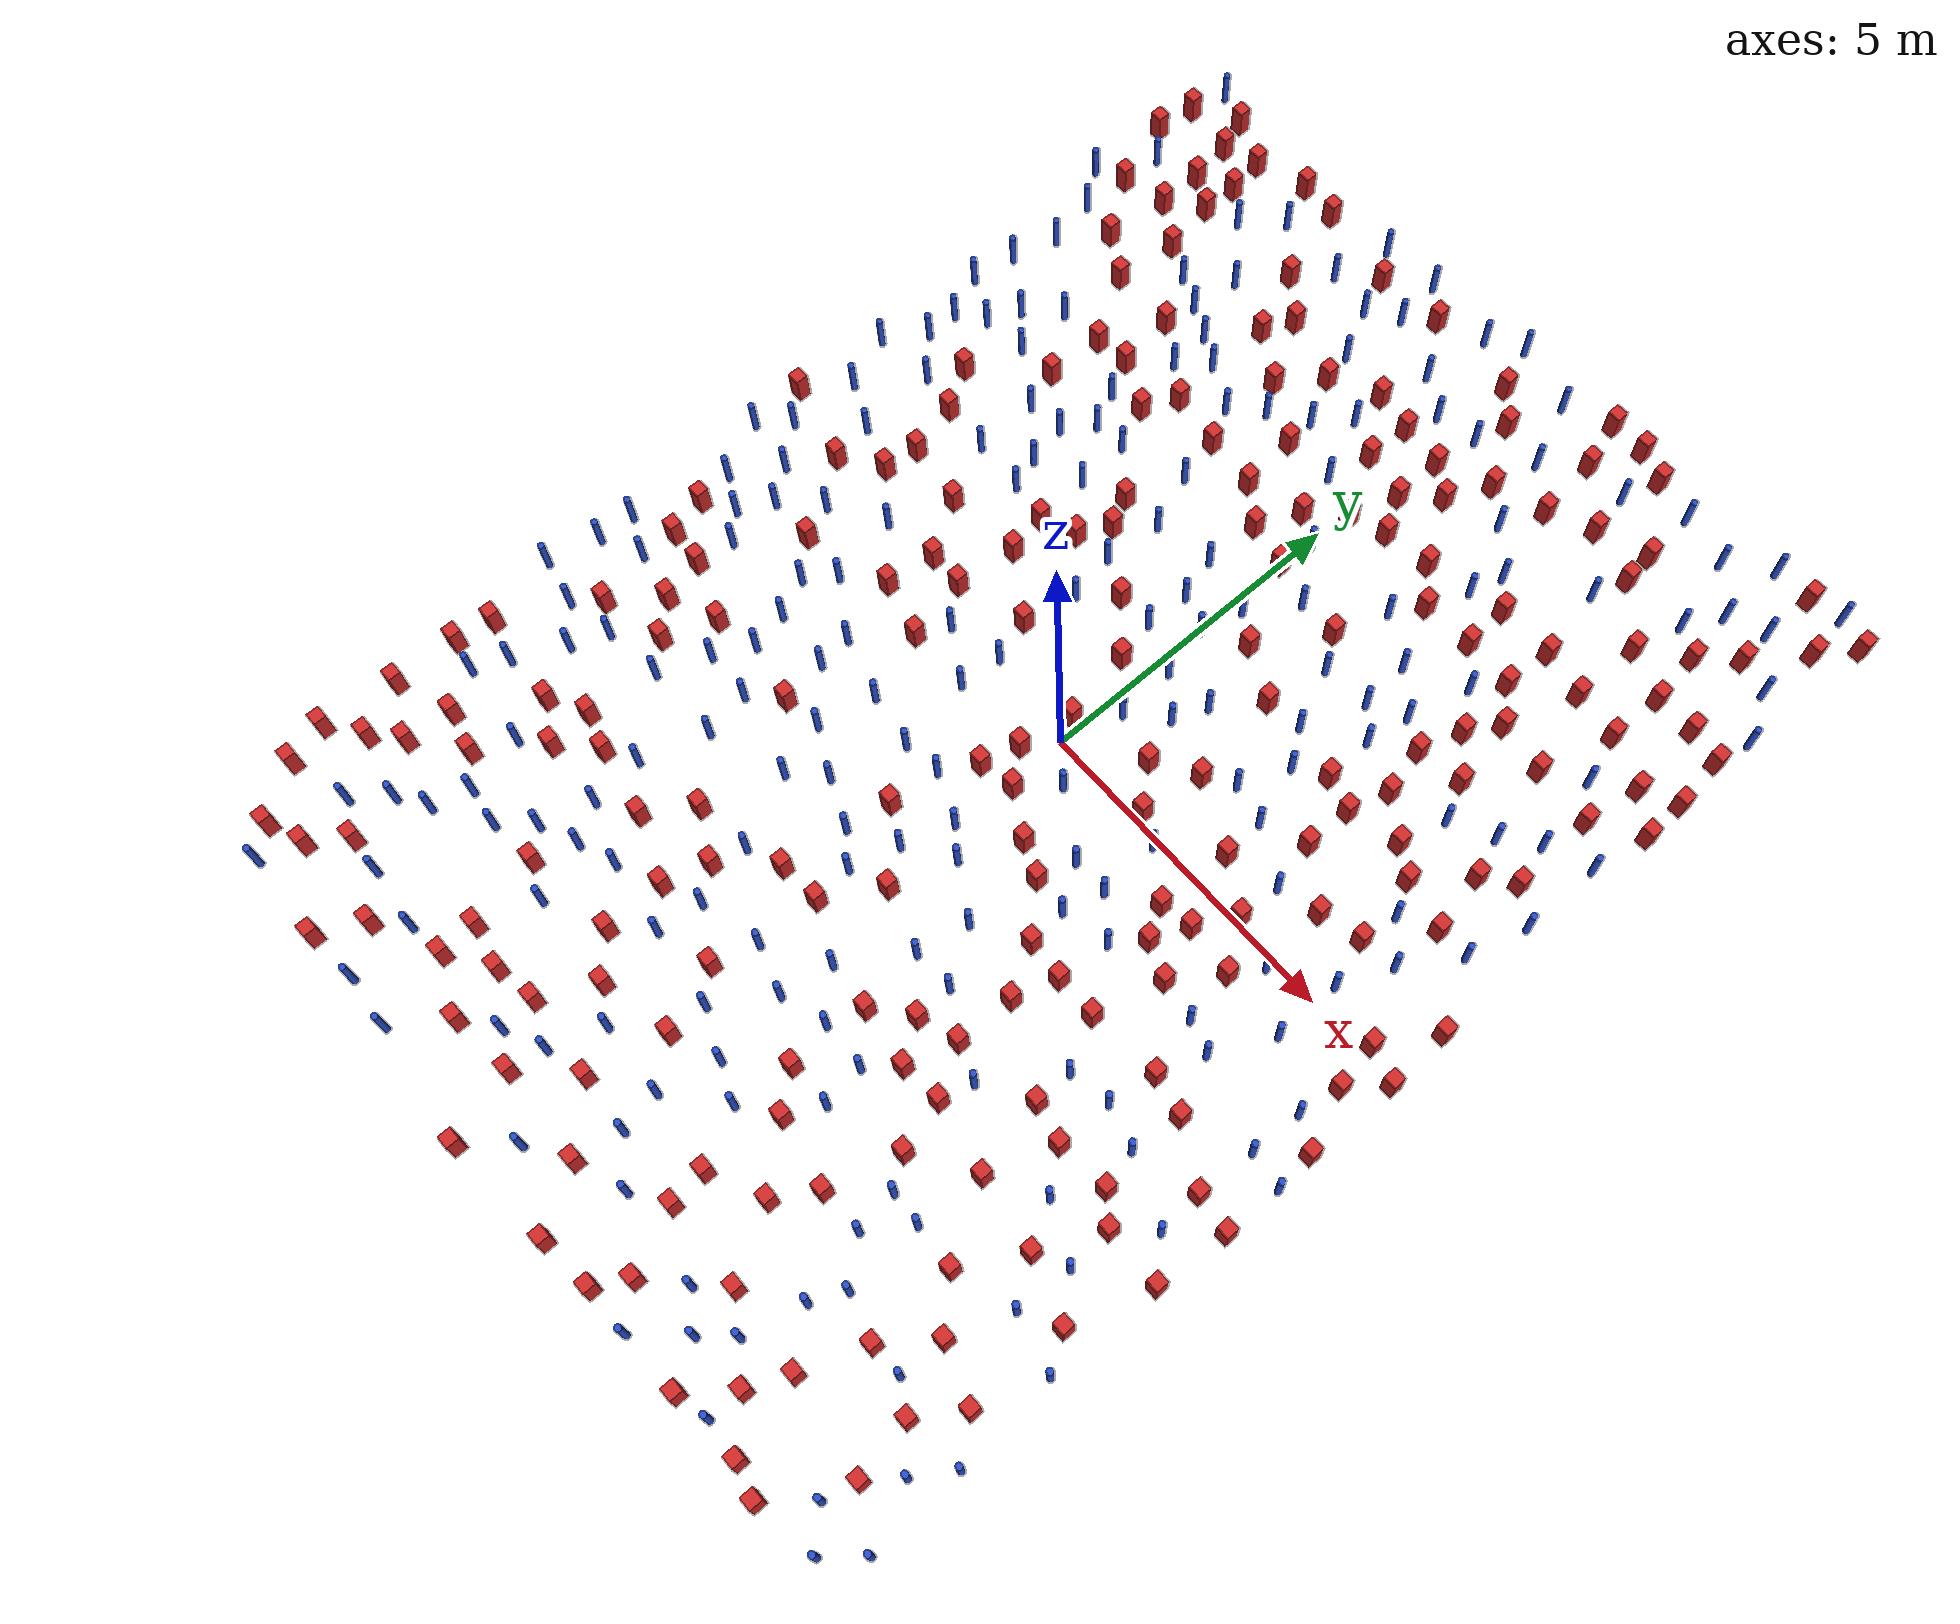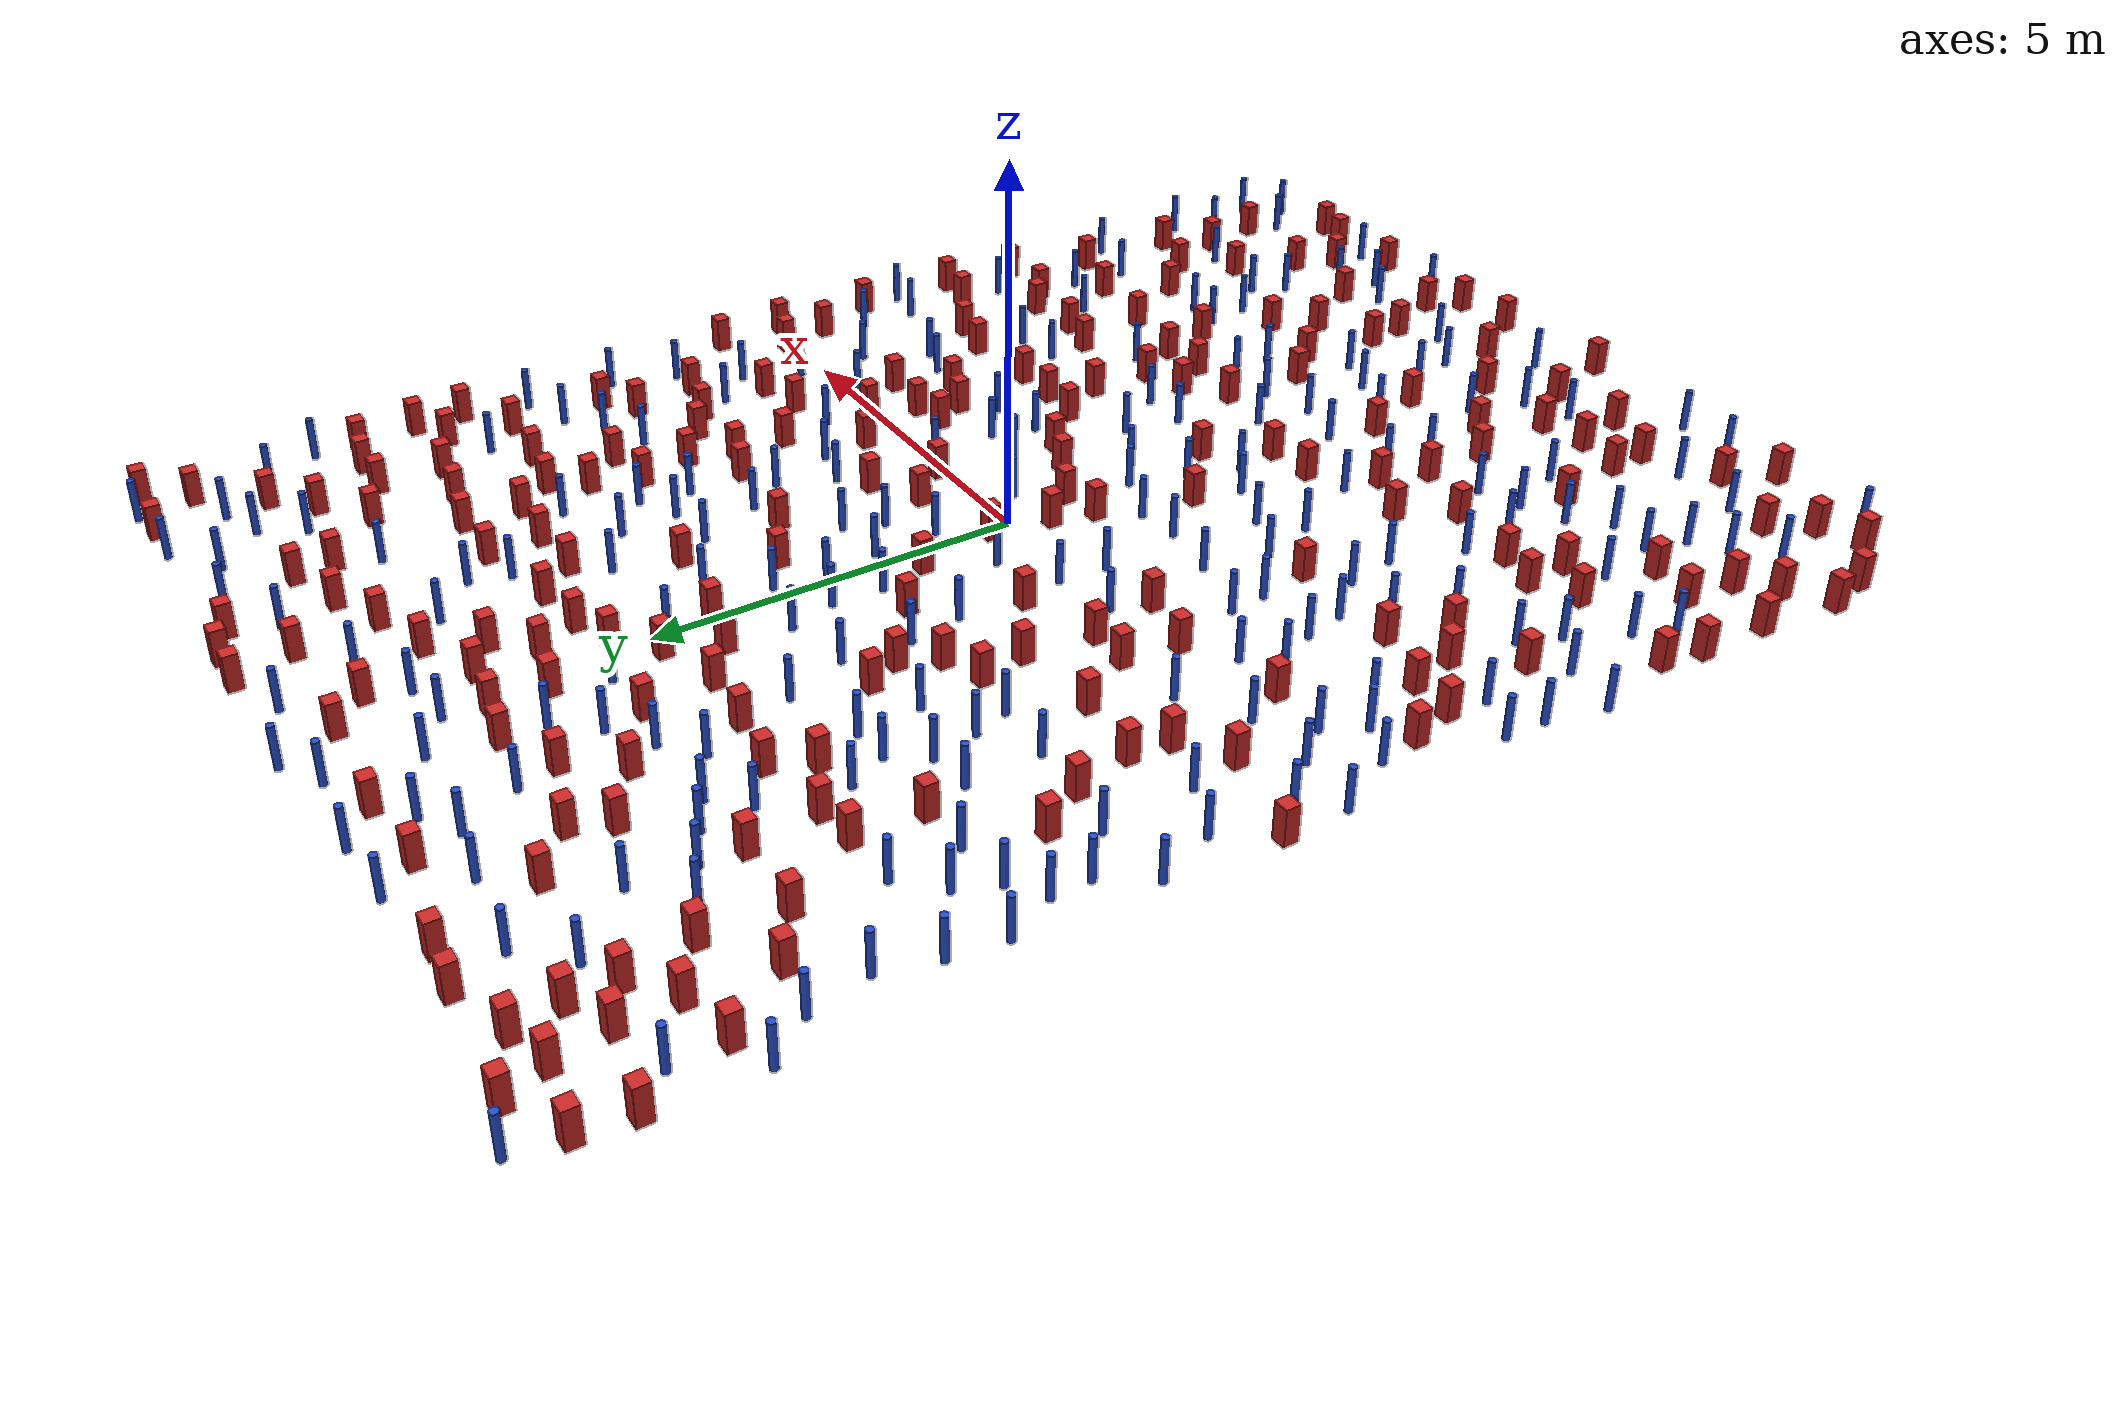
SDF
<sdf version="1.6">
  <model name="dense_68"><model name="pole_obstacle0">
  <static>true</static>
  <pose frame="">2.95338815927 3.82318107499 2.88873142074e-08 -9.90536690232e-09 4.6021994898e-07 -1.20965994968e-07</pose>
  <link name="link">
  <pose frame="">0 0 0.3 0 -0 0</pose>
    <inertial>
      <mass>1</mass>
      <inertia>
        <ixx>0.145833</ixx>
        <ixy>0</ixy>
        <ixz>0</ixz>
        <iyy>0.145833</iyy>
        <iyz>0</iyz>
        <izz>0.125</izz>
      </inertia>
    </inertial>
    <collision name="collision">
      <geometry>
        <cylinder>
          <radius>0.05</radius>
          <length>.6</length>
        </cylinder>
      </geometry>
      <max_contacts>10</max_contacts>
      <surface>
        <contact>
          <ode/>
        </contact>
        <bounce/>
        <friction>
          <torsional>
            <ode/>
          </torsional>
          <ode/>
        </friction>
      </surface>
    </collision>
    <visual name="visual">
      <geometry>
        <cylinder>
          <radius>0.05</radius>
          <length>.6</length>
        </cylinder>
      </geometry>
      <material>
        <script>
          <name>Gazebo/Blue</name>
          <uri>file://media/materials/scripts/gazebo.material</uri>
        </script>
      </material>
    </visual>
    <self_collide>0</self_collide>
    <kinematic>0</kinematic>
  </link>
</model>
<model name="pole_obstacle1">
  <static>true</static>
  <pose frame="">4.24833573397 -2.92627060806 2.88873142074e-08 -9.90536690245e-09 4.6021994898e-07 -1.20965994966e-07</pose>
  <link name="link">
  <pose frame="">0 0 0.3 0 -0 0</pose>
    <inertial>
      <mass>1</mass>
      <inertia>
        <ixx>0.145833</ixx>
        <ixy>0</ixy>
        <ixz>0</ixz>
        <iyy>0.145833</iyy>
        <iyz>0</iyz>
        <izz>0.125</izz>
      </inertia>
    </inertial>
    <collision name="collision">
      <geometry>
        <cylinder>
          <radius>0.05</radius>
          <length>.6</length>
        </cylinder>
      </geometry>
      <max_contacts>10</max_contacts>
      <surface>
        <contact>
          <ode/>
        </contact>
        <bounce/>
        <friction>
          <torsional>
            <ode/>
          </torsional>
          <ode/>
        </friction>
      </surface>
    </collision>
    <visual name="visual">
      <geometry>
        <cylinder>
          <radius>0.05</radius>
          <length>.6</length>
        </cylinder>
      </geometry>
      <material>
        <script>
          <name>Gazebo/Blue</name>
          <uri>file://media/materials/scripts/gazebo.material</uri>
        </script>
      </material>
    </visual>
    <self_collide>0</self_collide>
    <kinematic>0</kinematic>
  </link>
</model>
<model name="square_post_obstacle0">
  <static>true</static>
  <pose frame="">-4.89143161546 1.51569042266 8.22691968438e-08 7.2212513382e-06 -7.54495500217e-07 2.29674213826e-05</pose>
  <link name="link">
    <pose frame="">0 0 0.25 0 -0 0</pose>
    <inertial>
      <mass>100</mass>
      <inertia>
        <ixx>0.166667</ixx>
        <ixy>0</ixy>
        <ixz>0</ixz>
        <iyy>0.166667</iyy>
        <iyz>0</iyz>
        <izz>0.166667</izz>
      </inertia>
    </inertial>
    <collision name="collision">
      <geometry>
        <box>
          <size>.2 .2 .5</size>
        </box>
      </geometry>
      <max_contacts>10</max_contacts>
      <surface>
        <contact>
          <ode/>
        </contact>
        <bounce/>
        <friction>
          <torsional>
            <ode/>
          </torsional>
          <ode/>
        </friction>
      </surface>
    </collision>
    <visual name="visual">
      <geometry>
        <box>
          <size>.2 .2 .5</size>
        </box>
      </geometry>
      <material>
        <script>
          <name>Gazebo/Red</name>
          <uri>file://media/materials/scripts/gazebo.material</uri>
        </script>
      </material>
    </visual>
    <self_collide>0</self_collide>
    <kinematic>0</kinematic>
  </link>
</model>
<model name="square_post_obstacle1">
  <static>true</static>
  <pose frame="">1.20547896843 -4.45564103918 8.22691968438e-08 7.2212513382e-06 -7.54495500217e-07 2.29674213826e-05</pose>
  <link name="link">
    <pose frame="">0 0 0.25 0 -0 0</pose>
    <inertial>
      <mass>100</mass>
      <inertia>
        <ixx>0.166667</ixx>
        <ixy>0</ixy>
        <ixz>0</ixz>
        <iyy>0.166667</iyy>
        <iyz>0</iyz>
        <izz>0.166667</izz>
      </inertia>
    </inertial>
    <collision name="collision">
      <geometry>
        <box>
          <size>.2 .2 .5</size>
        </box>
      </geometry>
      <max_contacts>10</max_contacts>
      <surface>
        <contact>
          <ode/>
        </contact>
        <bounce/>
        <friction>
          <torsional>
            <ode/>
          </torsional>
          <ode/>
        </friction>
      </surface>
    </collision>
    <visual name="visual">
      <geometry>
        <box>
          <size>.2 .2 .5</size>
        </box>
      </geometry>
      <material>
        <script>
          <name>Gazebo/Red</name>
          <uri>file://media/materials/scripts/gazebo.material</uri>
        </script>
      </material>
    </visual>
    <self_collide>0</self_collide>
    <kinematic>0</kinematic>
  </link>
</model>
<model name="pole_obstacle2">
  <static>true</static>
  <pose frame="">-5.47846547494 -1.4591798869 2.88873142074e-08 -9.90536689445e-09 4.60219948999e-07 -1.20965994956e-07</pose>
  <link name="link">
  <pose frame="">0 0 0.3 0 -0 0</pose>
    <inertial>
      <mass>1</mass>
      <inertia>
        <ixx>0.145833</ixx>
        <ixy>0</ixy>
        <ixz>0</ixz>
        <iyy>0.145833</iyy>
        <iyz>0</iyz>
        <izz>0.125</izz>
      </inertia>
    </inertial>
    <collision name="collision">
      <geometry>
        <cylinder>
          <radius>0.05</radius>
          <length>.6</length>
        </cylinder>
      </geometry>
      <max_contacts>10</max_contacts>
      <surface>
        <contact>
          <ode/>
        </contact>
        <bounce/>
        <friction>
          <torsional>
            <ode/>
          </torsional>
          <ode/>
        </friction>
      </surface>
    </collision>
    <visual name="visual">
      <geometry>
        <cylinder>
          <radius>0.05</radius>
          <length>.6</length>
        </cylinder>
      </geometry>
      <material>
        <script>
          <name>Gazebo/Blue</name>
          <uri>file://media/materials/scripts/gazebo.material</uri>
        </script>
      </material>
    </visual>
    <self_collide>0</self_collide>
    <kinematic>0</kinematic>
  </link>
</model>
<model name="pole_obstacle3">
  <static>true</static>
  <pose frame="">0.289647013315 -7.17441640255 2.88873142074e-08 -9.90536689592e-09 4.60219948995e-07 -1.20965994956e-07</pose>
  <link name="link">
  <pose frame="">0 0 0.3 0 -0 0</pose>
    <inertial>
      <mass>1</mass>
      <inertia>
        <ixx>0.145833</ixx>
        <ixy>0</ixy>
        <ixz>0</ixz>
        <iyy>0.145833</iyy>
        <iyz>0</iyz>
        <izz>0.125</izz>
      </inertia>
    </inertial>
    <collision name="collision">
      <geometry>
        <cylinder>
          <radius>0.05</radius>
          <length>.6</length>
        </cylinder>
      </geometry>
      <max_contacts>10</max_contacts>
      <surface>
        <contact>
          <ode/>
        </contact>
        <bounce/>
        <friction>
          <torsional>
            <ode/>
          </torsional>
          <ode/>
        </friction>
      </surface>
    </collision>
    <visual name="visual">
      <geometry>
        <cylinder>
          <radius>0.05</radius>
          <length>.6</length>
        </cylinder>
      </geometry>
      <material>
        <script>
          <name>Gazebo/Blue</name>
          <uri>file://media/materials/scripts/gazebo.material</uri>
        </script>
      </material>
    </visual>
    <self_collide>0</self_collide>
    <kinematic>0</kinematic>
  </link>
</model>
<model name="pole_obstacle4">
  <static>true</static>
  <pose frame="">5.55034448489 -8.70579672338 2.88873142074e-08 -9.9053668967e-09 4.60219948993e-07 -1.20965994957e-07</pose>
  <link name="link">
  <pose frame="">0 0 0.3 0 -0 0</pose>
    <inertial>
      <mass>1</mass>
      <inertia>
        <ixx>0.145833</ixx>
        <ixy>0</ixy>
        <ixz>0</ixz>
        <iyy>0.145833</iyy>
        <iyz>0</iyz>
        <izz>0.125</izz>
      </inertia>
    </inertial>
    <collision name="collision">
      <geometry>
        <cylinder>
          <radius>0.05</radius>
          <length>.6</length>
        </cylinder>
      </geometry>
      <max_contacts>10</max_contacts>
      <surface>
        <contact>
          <ode/>
        </contact>
        <bounce/>
        <friction>
          <torsional>
            <ode/>
          </torsional>
          <ode/>
        </friction>
      </surface>
    </collision>
    <visual name="visual">
      <geometry>
        <cylinder>
          <radius>0.05</radius>
          <length>.6</length>
        </cylinder>
      </geometry>
      <material>
        <script>
          <name>Gazebo/Blue</name>
          <uri>file://media/materials/scripts/gazebo.material</uri>
        </script>
      </material>
    </visual>
    <self_collide>0</self_collide>
    <kinematic>0</kinematic>
  </link>
</model>
<model name="pole_obstacle5">
  <static>true</static>
  <pose frame="">-5.27086612871 4.74190391233 2.88873142074e-08 -9.90536690842e-09 4.60219948965e-07 -1.20965994976e-07</pose>
  <link name="link">
  <pose frame="">0 0 0.3 0 -0 0</pose>
    <inertial>
      <mass>1</mass>
      <inertia>
        <ixx>0.145833</ixx>
        <ixy>0</ixy>
        <ixz>0</ixz>
        <iyy>0.145833</iyy>
        <iyz>0</iyz>
        <izz>0.125</izz>
      </inertia>
    </inertial>
    <collision name="collision">
      <geometry>
        <cylinder>
          <radius>0.05</radius>
          <length>.6</length>
        </cylinder>
      </geometry>
      <max_contacts>10</max_contacts>
      <surface>
        <contact>
          <ode/>
        </contact>
        <bounce/>
        <friction>
          <torsional>
            <ode/>
          </torsional>
          <ode/>
        </friction>
      </surface>
    </collision>
    <visual name="visual">
      <geometry>
        <cylinder>
          <radius>0.05</radius>
          <length>.6</length>
        </cylinder>
      </geometry>
      <material>
        <script>
          <name>Gazebo/Blue</name>
          <uri>file://media/materials/scripts/gazebo.material</uri>
        </script>
      </material>
    </visual>
    <self_collide>0</self_collide>
    <kinematic>0</kinematic>
  </link>
</model>
<model name="pole_obstacle6">
  <static>true</static>
  <pose frame="">4.22046325973 8.89876180597 2.88873142074e-08 -9.9053668967e-09 4.60219948993e-07 -1.20965994957e-07</pose>
  <link name="link">
  <pose frame="">0 0 0.3 0 -0 0</pose>
    <inertial>
      <mass>1</mass>
      <inertia>
        <ixx>0.145833</ixx>
        <ixy>0</ixy>
        <ixz>0</ixz>
        <iyy>0.145833</iyy>
        <iyz>0</iyz>
        <izz>0.125</izz>
      </inertia>
    </inertial>
    <collision name="collision">
      <geometry>
        <cylinder>
          <radius>0.05</radius>
          <length>.6</length>
        </cylinder>
      </geometry>
      <max_contacts>10</max_contacts>
      <surface>
        <contact>
          <ode/>
        </contact>
        <bounce/>
        <friction>
          <torsional>
            <ode/>
          </torsional>
          <ode/>
        </friction>
      </surface>
    </collision>
    <visual name="visual">
      <geometry>
        <cylinder>
          <radius>0.05</radius>
          <length>.6</length>
        </cylinder>
      </geometry>
      <material>
        <script>
          <name>Gazebo/Blue</name>
          <uri>file://media/materials/scripts/gazebo.material</uri>
        </script>
      </material>
    </visual>
    <self_collide>0</self_collide>
    <kinematic>0</kinematic>
  </link>
</model>
<model name="square_post_obstacle2">
  <static>true</static>
  <pose frame="">3.51886979271 5.21029539455 8.22691968438e-08 7.2212513382e-06 -7.54495500217e-07 2.29674213826e-05</pose>
  <link name="link">
    <pose frame="">0 0 0.25 0 -0 0</pose>
    <inertial>
      <mass>100</mass>
      <inertia>
        <ixx>0.166667</ixx>
        <ixy>0</ixy>
        <ixz>0</ixz>
        <iyy>0.166667</iyy>
        <iyz>0</iyz>
        <izz>0.166667</izz>
      </inertia>
    </inertial>
    <collision name="collision">
      <geometry>
        <box>
          <size>.2 .2 .5</size>
        </box>
      </geometry>
      <max_contacts>10</max_contacts>
      <surface>
        <contact>
          <ode/>
        </contact>
        <bounce/>
        <friction>
          <torsional>
            <ode/>
          </torsional>
          <ode/>
        </friction>
      </surface>
    </collision>
    <visual name="visual">
      <geometry>
        <box>
          <size>.2 .2 .5</size>
        </box>
      </geometry>
      <material>
        <script>
          <name>Gazebo/Red</name>
          <uri>file://media/materials/scripts/gazebo.material</uri>
        </script>
      </material>
    </visual>
    <self_collide>0</self_collide>
    <kinematic>0</kinematic>
  </link>
</model>
<model name="square_post_obstacle3">
  <static>true</static>
  <pose frame="">-0.493345622477 -7.72560742261 8.22691968438e-08 7.22125133819e-06 -7.54495500217e-07 2.29674213826e-05</pose>
  <link name="link">
    <pose frame="">0 0 0.25 0 -0 0</pose>
    <inertial>
      <mass>100</mass>
      <inertia>
        <ixx>0.166667</ixx>
        <ixy>0</ixy>
        <ixz>0</ixz>
        <iyy>0.166667</iyy>
        <iyz>0</iyz>
        <izz>0.166667</izz>
      </inertia>
    </inertial>
    <collision name="collision">
      <geometry>
        <box>
          <size>.2 .2 .5</size>
        </box>
      </geometry>
      <max_contacts>10</max_contacts>
      <surface>
        <contact>
          <ode/>
        </contact>
        <bounce/>
        <friction>
          <torsional>
            <ode/>
          </torsional>
          <ode/>
        </friction>
      </surface>
    </collision>
    <visual name="visual">
      <geometry>
        <box>
          <size>.2 .2 .5</size>
        </box>
      </geometry>
      <material>
        <script>
          <name>Gazebo/Red</name>
          <uri>file://media/materials/scripts/gazebo.material</uri>
        </script>
      </material>
    </visual>
    <self_collide>0</self_collide>
    <kinematic>0</kinematic>
  </link>
</model>
<model name="square_post_obstacle4">
  <static>true</static>
  <pose frame="">4.50219879882 -5.79253463406 8.22691968438e-08 7.22125133819e-06 -7.54495500217e-07 2.29674213826e-05</pose>
  <link name="link">
    <pose frame="">0 0 0.25 0 -0 0</pose>
    <inertial>
      <mass>100</mass>
      <inertia>
        <ixx>0.166667</ixx>
        <ixy>0</ixy>
        <ixz>0</ixz>
        <iyy>0.166667</iyy>
        <iyz>0</iyz>
        <izz>0.166667</izz>
      </inertia>
    </inertial>
    <collision name="collision">
      <geometry>
        <box>
          <size>.2 .2 .5</size>
        </box>
      </geometry>
      <max_contacts>10</max_contacts>
      <surface>
        <contact>
          <ode/>
        </contact>
        <bounce/>
        <friction>
          <torsional>
            <ode/>
          </torsional>
          <ode/>
        </friction>
      </surface>
    </collision>
    <visual name="visual">
      <geometry>
        <box>
          <size>.2 .2 .5</size>
        </box>
      </geometry>
      <material>
        <script>
          <name>Gazebo/Red</name>
          <uri>file://media/materials/scripts/gazebo.material</uri>
        </script>
      </material>
    </visual>
    <self_collide>0</self_collide>
    <kinematic>0</kinematic>
  </link>
</model>
<model name="pole_obstacle7">
  <static>true</static>
  <pose frame="">-2.39501589239 -2.36706867355 2.88873142074e-08 -9.90536690232e-09 4.6021994898e-07 -1.20965994968e-07</pose>
  <link name="link">
  <pose frame="">0 0 0.3 0 -0 0</pose>
    <inertial>
      <mass>1</mass>
      <inertia>
        <ixx>0.145833</ixx>
        <ixy>0</ixy>
        <ixz>0</ixz>
        <iyy>0.145833</iyy>
        <iyz>0</iyz>
        <izz>0.125</izz>
      </inertia>
    </inertial>
    <collision name="collision">
      <geometry>
        <cylinder>
          <radius>0.05</radius>
          <length>.6</length>
        </cylinder>
      </geometry>
      <max_contacts>10</max_contacts>
      <surface>
        <contact>
          <ode/>
        </contact>
        <bounce/>
        <friction>
          <torsional>
            <ode/>
          </torsional>
          <ode/>
        </friction>
      </surface>
    </collision>
    <visual name="visual">
      <geometry>
        <cylinder>
          <radius>0.05</radius>
          <length>.6</length>
        </cylinder>
      </geometry>
      <material>
        <script>
          <name>Gazebo/Blue</name>
          <uri>file://media/materials/scripts/gazebo.material</uri>
        </script>
      </material>
    </visual>
    <self_collide>0</self_collide>
    <kinematic>0</kinematic>
  </link>
</model>
<model name="pole_obstacle8">
  <static>true</static>
  <pose frame="">-6.47609809093 0.466373372881 2.88873142074e-08 -9.90536689483e-09 4.60219948998e-07 -1.20965994956e-07</pose>
  <link name="link">
  <pose frame="">0 0 0.3 0 -0 0</pose>
    <inertial>
      <mass>1</mass>
      <inertia>
        <ixx>0.145833</ixx>
        <ixy>0</ixy>
        <ixz>0</ixz>
        <iyy>0.145833</iyy>
        <iyz>0</iyz>
        <izz>0.125</izz>
      </inertia>
    </inertial>
    <collision name="collision">
      <geometry>
        <cylinder>
          <radius>0.05</radius>
          <length>.6</length>
        </cylinder>
      </geometry>
      <max_contacts>10</max_contacts>
      <surface>
        <contact>
          <ode/>
        </contact>
        <bounce/>
        <friction>
          <torsional>
            <ode/>
          </torsional>
          <ode/>
        </friction>
      </surface>
    </collision>
    <visual name="visual">
      <geometry>
        <cylinder>
          <radius>0.05</radius>
          <length>.6</length>
        </cylinder>
      </geometry>
      <material>
        <script>
          <name>Gazebo/Blue</name>
          <uri>file://media/materials/scripts/gazebo.material</uri>
        </script>
      </material>
    </visual>
    <self_collide>0</self_collide>
    <kinematic>0</kinematic>
  </link>
</model>
<model name="square_post_obstacle5">
  <static>true</static>
  <pose frame="">-3.35329620936 0.536395780988 8.22691968438e-08 7.22125133819e-06 -7.54495500217e-07 2.29674213826e-05</pose>
  <link name="link">
    <pose frame="">0 0 0.25 0 -0 0</pose>
    <inertial>
      <mass>100</mass>
      <inertia>
        <ixx>0.166667</ixx>
        <ixy>0</ixy>
        <ixz>0</ixz>
        <iyy>0.166667</iyy>
        <iyz>0</iyz>
        <izz>0.166667</izz>
      </inertia>
    </inertial>
    <collision name="collision">
      <geometry>
        <box>
          <size>.2 .2 .5</size>
        </box>
      </geometry>
      <max_contacts>10</max_contacts>
      <surface>
        <contact>
          <ode/>
        </contact>
        <bounce/>
        <friction>
          <torsional>
            <ode/>
          </torsional>
          <ode/>
        </friction>
      </surface>
    </collision>
    <visual name="visual">
      <geometry>
        <box>
          <size>.2 .2 .5</size>
        </box>
      </geometry>
      <material>
        <script>
          <name>Gazebo/Red</name>
          <uri>file://media/materials/scripts/gazebo.material</uri>
        </script>
      </material>
    </visual>
    <self_collide>0</self_collide>
    <kinematic>0</kinematic>
  </link>
</model>
<model name="square_post_obstacle6">
  <static>true</static>
  <pose frame="">1.0574239623 0.681097987181 8.22691968438e-08 7.2212513382e-06 -7.54495500217e-07 2.29674213826e-05</pose>
  <link name="link">
    <pose frame="">0 0 0.25 0 -0 0</pose>
    <inertial>
      <mass>100</mass>
      <inertia>
        <ixx>0.166667</ixx>
        <ixy>0</ixy>
        <ixz>0</ixz>
        <iyy>0.166667</iyy>
        <iyz>0</iyz>
        <izz>0.166667</izz>
      </inertia>
    </inertial>
    <collision name="collision">
      <geometry>
        <box>
          <size>.2 .2 .5</size>
        </box>
      </geometry>
      <max_contacts>10</max_contacts>
      <surface>
        <contact>
          <ode/>
        </contact>
        <bounce/>
        <friction>
          <torsional>
            <ode/>
          </torsional>
          <ode/>
        </friction>
      </surface>
    </collision>
    <visual name="visual">
      <geometry>
        <box>
          <size>.2 .2 .5</size>
        </box>
      </geometry>
      <material>
        <script>
          <name>Gazebo/Red</name>
          <uri>file://media/materials/scripts/gazebo.material</uri>
        </script>
      </material>
    </visual>
    <self_collide>0</self_collide>
    <kinematic>0</kinematic>
  </link>
</model>
<model name="square_post_obstacle7">
  <static>true</static>
  <pose frame="">4.19814974283 2.39181814396 8.22691968438e-08 7.2212513382e-06 -7.54495500217e-07 2.29674213826e-05</pose>
  <link name="link">
    <pose frame="">0 0 0.25 0 -0 0</pose>
    <inertial>
      <mass>100</mass>
      <inertia>
        <ixx>0.166667</ixx>
        <ixy>0</ixy>
        <ixz>0</ixz>
        <iyy>0.166667</iyy>
        <iyz>0</iyz>
        <izz>0.166667</izz>
      </inertia>
    </inertial>
    <collision name="collision">
      <geometry>
        <box>
          <size>.2 .2 .5</size>
        </box>
      </geometry>
      <max_contacts>10</max_contacts>
      <surface>
        <contact>
          <ode/>
        </contact>
        <bounce/>
        <friction>
          <torsional>
            <ode/>
          </torsional>
          <ode/>
        </friction>
      </surface>
    </collision>
    <visual name="visual">
      <geometry>
        <box>
          <size>.2 .2 .5</size>
        </box>
      </geometry>
      <material>
        <script>
          <name>Gazebo/Red</name>
          <uri>file://media/materials/scripts/gazebo.material</uri>
        </script>
      </material>
    </visual>
    <self_collide>0</self_collide>
    <kinematic>0</kinematic>
  </link>
</model>
<model name="pole_obstacle9">
  <static>true</static>
  <pose frame="">-5.67694998414 -4.2069552184 2.88873142074e-08 -9.90536690842e-09 4.60219948965e-07 -1.20965994976e-07</pose>
  <link name="link">
  <pose frame="">0 0 0.3 0 -0 0</pose>
    <inertial>
      <mass>1</mass>
      <inertia>
        <ixx>0.145833</ixx>
        <ixy>0</ixy>
        <ixz>0</ixz>
        <iyy>0.145833</iyy>
        <iyz>0</iyz>
        <izz>0.125</izz>
      </inertia>
    </inertial>
    <collision name="collision">
      <geometry>
        <cylinder>
          <radius>0.05</radius>
          <length>.6</length>
        </cylinder>
      </geometry>
      <max_contacts>10</max_contacts>
      <surface>
        <contact>
          <ode/>
        </contact>
        <bounce/>
        <friction>
          <torsional>
            <ode/>
          </torsional>
          <ode/>
        </friction>
      </surface>
    </collision>
    <visual name="visual">
      <geometry>
        <cylinder>
          <radius>0.05</radius>
          <length>.6</length>
        </cylinder>
      </geometry>
      <material>
        <script>
          <name>Gazebo/Blue</name>
          <uri>file://media/materials/scripts/gazebo.material</uri>
        </script>
      </material>
    </visual>
    <self_collide>0</self_collide>
    <kinematic>0</kinematic>
  </link>
</model>
<model name="pole_obstacle10">
  <static>true</static>
  <pose frame="">4.12650036827 -1.38472819704 2.88873142074e-08 -9.90536689445e-09 4.60219948999e-07 -1.20965994956e-07</pose>
  <link name="link">
  <pose frame="">0 0 0.3 0 -0 0</pose>
    <inertial>
      <mass>1</mass>
      <inertia>
        <ixx>0.145833</ixx>
        <ixy>0</ixy>
        <ixz>0</ixz>
        <iyy>0.145833</iyy>
        <iyz>0</iyz>
        <izz>0.125</izz>
      </inertia>
    </inertial>
    <collision name="collision">
      <geometry>
        <cylinder>
          <radius>0.05</radius>
          <length>.6</length>
        </cylinder>
      </geometry>
      <max_contacts>10</max_contacts>
      <surface>
        <contact>
          <ode/>
        </contact>
        <bounce/>
        <friction>
          <torsional>
            <ode/>
          </torsional>
          <ode/>
        </friction>
      </surface>
    </collision>
    <visual name="visual">
      <geometry>
        <cylinder>
          <radius>0.05</radius>
          <length>.6</length>
        </cylinder>
      </geometry>
      <material>
        <script>
          <name>Gazebo/Blue</name>
          <uri>file://media/materials/scripts/gazebo.material</uri>
        </script>
      </material>
    </visual>
    <self_collide>0</self_collide>
    <kinematic>0</kinematic>
  </link>
</model>
<model name="pole_obstacle11">
  <static>true</static>
  <pose frame="">3.21454982424 4.77770129587 2.88873142074e-08 -9.90536689859e-09 4.60219948989e-07 -1.20965994961e-07</pose>
  <link name="link">
  <pose frame="">0 0 0.3 0 -0 0</pose>
    <inertial>
      <mass>1</mass>
      <inertia>
        <ixx>0.145833</ixx>
        <ixy>0</ixy>
        <ixz>0</ixz>
        <iyy>0.145833</iyy>
        <iyz>0</iyz>
        <izz>0.125</izz>
      </inertia>
    </inertial>
    <collision name="collision">
      <geometry>
        <cylinder>
          <radius>0.05</radius>
          <length>.6</length>
        </cylinder>
      </geometry>
      <max_contacts>10</max_contacts>
      <surface>
        <contact>
          <ode/>
        </contact>
        <bounce/>
        <friction>
          <torsional>
            <ode/>
          </torsional>
          <ode/>
        </friction>
      </surface>
    </collision>
    <visual name="visual">
      <geometry>
        <cylinder>
          <radius>0.05</radius>
          <length>.6</length>
        </cylinder>
      </geometry>
      <material>
        <script>
          <name>Gazebo/Blue</name>
          <uri>file://media/materials/scripts/gazebo.material</uri>
        </script>
      </material>
    </visual>
    <self_collide>0</self_collide>
    <kinematic>0</kinematic>
  </link>
</model>
<model name="pole_obstacle12">
  <static>true</static>
  <pose frame="">-2.20198437938 -1.49410046 2.88873142074e-08 -9.90536689395e-09 4.60219949e-07 -1.20965994953e-07</pose>
  <link name="link">
  <pose frame="">0 0 0.3 0 -0 0</pose>
    <inertial>
      <mass>1</mass>
      <inertia>
        <ixx>0.145833</ixx>
        <ixy>0</ixy>
        <ixz>0</ixz>
        <iyy>0.145833</iyy>
        <iyz>0</iyz>
        <izz>0.125</izz>
      </inertia>
    </inertial>
    <collision name="collision">
      <geometry>
        <cylinder>
          <radius>0.05</radius>
          <length>.6</length>
        </cylinder>
      </geometry>
      <max_contacts>10</max_contacts>
      <surface>
        <contact>
          <ode/>
        </contact>
        <bounce/>
        <friction>
          <torsional>
            <ode/>
          </torsional>
          <ode/>
        </friction>
      </surface>
    </collision>
    <visual name="visual">
      <geometry>
        <cylinder>
          <radius>0.05</radius>
          <length>.6</length>
        </cylinder>
      </geometry>
      <material>
        <script>
          <name>Gazebo/Blue</name>
          <uri>file://media/materials/scripts/gazebo.material</uri>
        </script>
      </material>
    </visual>
    <self_collide>0</self_collide>
    <kinematic>0</kinematic>
  </link>
</model>
<model name="square_post_obstacle8">
  <static>true</static>
  <pose frame="">1.70375247246 1.07010474662 8.22691968438e-08 7.2212513382e-06 -7.54495500217e-07 2.29674213826e-05</pose>
  <link name="link">
    <pose frame="">0 0 0.25 0 -0 0</pose>
    <inertial>
      <mass>100</mass>
      <inertia>
        <ixx>0.166667</ixx>
        <ixy>0</ixy>
        <ixz>0</ixz>
        <iyy>0.166667</iyy>
        <iyz>0</iyz>
        <izz>0.166667</izz>
      </inertia>
    </inertial>
    <collision name="collision">
      <geometry>
        <box>
          <size>.2 .2 .5</size>
        </box>
      </geometry>
      <max_contacts>10</max_contacts>
      <surface>
        <contact>
          <ode/>
        </contact>
        <bounce/>
        <friction>
          <torsional>
            <ode/>
          </torsional>
          <ode/>
        </friction>
      </surface>
    </collision>
    <visual name="visual">
      <geometry>
        <box>
          <size>.2 .2 .5</size>
        </box>
      </geometry>
      <material>
        <script>
          <name>Gazebo/Red</name>
          <uri>file://media/materials/scripts/gazebo.material</uri>
        </script>
      </material>
    </visual>
    <self_collide>0</self_collide>
    <kinematic>0</kinematic>
  </link>
</model>
<model name="square_post_obstacle9">
  <static>true</static>
  <pose frame="">5.07672383665 6.60330566266 8.22691968438e-08 7.2212513382e-06 -7.54495500217e-07 2.29674213826e-05</pose>
  <link name="link">
    <pose frame="">0 0 0.25 0 -0 0</pose>
    <inertial>
      <mass>100</mass>
      <inertia>
        <ixx>0.166667</ixx>
        <ixy>0</ixy>
        <ixz>0</ixz>
        <iyy>0.166667</iyy>
        <iyz>0</iyz>
        <izz>0.166667</izz>
      </inertia>
    </inertial>
    <collision name="collision">
      <geometry>
        <box>
          <size>.2 .2 .5</size>
        </box>
      </geometry>
      <max_contacts>10</max_contacts>
      <surface>
        <contact>
          <ode/>
        </contact>
        <bounce/>
        <friction>
          <torsional>
            <ode/>
          </torsional>
          <ode/>
        </friction>
      </surface>
    </collision>
    <visual name="visual">
      <geometry>
        <box>
          <size>.2 .2 .5</size>
        </box>
      </geometry>
      <material>
        <script>
          <name>Gazebo/Red</name>
          <uri>file://media/materials/scripts/gazebo.material</uri>
        </script>
      </material>
    </visual>
    <self_collide>0</self_collide>
    <kinematic>0</kinematic>
  </link>
</model>
<model name="pole_obstacle13">
  <static>true</static>
  <pose frame="">-3.09752706126 5.78183192374 2.88873142074e-08 -9.90536689859e-09 4.60219948989e-07 -1.20965994961e-07</pose>
  <link name="link">
  <pose frame="">0 0 0.3 0 -0 0</pose>
    <inertial>
      <mass>1</mass>
      <inertia>
        <ixx>0.145833</ixx>
        <ixy>0</ixy>
        <ixz>0</ixz>
        <iyy>0.145833</iyy>
        <iyz>0</iyz>
        <izz>0.125</izz>
      </inertia>
    </inertial>
    <collision name="collision">
      <geometry>
        <cylinder>
          <radius>0.05</radius>
          <length>.6</length>
        </cylinder>
      </geometry>
      <max_contacts>10</max_contacts>
      <surface>
        <contact>
          <ode/>
        </contact>
        <bounce/>
        <friction>
          <torsional>
            <ode/>
          </torsional>
          <ode/>
        </friction>
      </surface>
    </collision>
    <visual name="visual">
      <geometry>
        <cylinder>
          <radius>0.05</radius>
          <length>.6</length>
        </cylinder>
      </geometry>
      <material>
        <script>
          <name>Gazebo/Blue</name>
          <uri>file://media/materials/scripts/gazebo.material</uri>
        </script>
      </material>
    </visual>
    <self_collide>0</self_collide>
    <kinematic>0</kinematic>
  </link>
</model>
<model name="square_post_obstacle10">
  <static>true</static>
  <pose frame="">-5.09372376777 6.79573837946 8.22691968438e-08 7.2212513382e-06 -7.54495500217e-07 2.29674213826e-05</pose>
  <link name="link">
    <pose frame="">0 0 0.25 0 -0 0</pose>
    <inertial>
      <mass>100</mass>
      <inertia>
        <ixx>0.166667</ixx>
        <ixy>0</ixy>
        <ixz>0</ixz>
        <iyy>0.166667</iyy>
        <iyz>0</iyz>
        <izz>0.166667</izz>
      </inertia>
    </inertial>
    <collision name="collision">
      <geometry>
        <box>
          <size>.2 .2 .5</size>
        </box>
      </geometry>
      <max_contacts>10</max_contacts>
      <surface>
        <contact>
          <ode/>
        </contact>
        <bounce/>
        <friction>
          <torsional>
            <ode/>
          </torsional>
          <ode/>
        </friction>
      </surface>
    </collision>
    <visual name="visual">
      <geometry>
        <box>
          <size>.2 .2 .5</size>
        </box>
      </geometry>
      <material>
        <script>
          <name>Gazebo/Red</name>
          <uri>file://media/materials/scripts/gazebo.material</uri>
        </script>
      </material>
    </visual>
    <self_collide>0</self_collide>
    <kinematic>0</kinematic>
  </link>
</model>
<model name="square_post_obstacle11">
  <static>true</static>
  <pose frame="">3.88004198026 -4.7429489376 8.22691968438e-08 7.2212513382e-06 -7.54495500217e-07 2.29674213826e-05</pose>
  <link name="link">
    <pose frame="">0 0 0.25 0 -0 0</pose>
    <inertial>
      <mass>100</mass>
      <inertia>
        <ixx>0.166667</ixx>
        <ixy>0</ixy>
        <ixz>0</ixz>
        <iyy>0.166667</iyy>
        <iyz>0</iyz>
        <izz>0.166667</izz>
      </inertia>
    </inertial>
    <collision name="collision">
      <geometry>
        <box>
          <size>.2 .2 .5</size>
        </box>
      </geometry>
      <max_contacts>10</max_contacts>
      <surface>
        <contact>
          <ode/>
        </contact>
        <bounce/>
        <friction>
          <torsional>
            <ode/>
          </torsional>
          <ode/>
        </friction>
      </surface>
    </collision>
    <visual name="visual">
      <geometry>
        <box>
          <size>.2 .2 .5</size>
        </box>
      </geometry>
      <material>
        <script>
          <name>Gazebo/Red</name>
          <uri>file://media/materials/scripts/gazebo.material</uri>
        </script>
      </material>
    </visual>
    <self_collide>0</self_collide>
    <kinematic>0</kinematic>
  </link>
</model>
<model name="pole_obstacle14">
  <static>true</static>
  <pose frame="">-0.688879812202 3.46186205146 2.88873142074e-08 -9.90536689636e-09 4.60219948994e-07 -1.20965994958e-07</pose>
  <link name="link">
  <pose frame="">0 0 0.3 0 -0 0</pose>
    <inertial>
      <mass>1</mass>
      <inertia>
        <ixx>0.145833</ixx>
        <ixy>0</ixy>
        <ixz>0</ixz>
        <iyy>0.145833</iyy>
        <iyz>0</iyz>
        <izz>0.125</izz>
      </inertia>
    </inertial>
    <collision name="collision">
      <geometry>
        <cylinder>
          <radius>0.05</radius>
          <length>.6</length>
        </cylinder>
      </geometry>
      <max_contacts>10</max_contacts>
      <surface>
        <contact>
          <ode/>
        </contact>
        <bounce/>
        <friction>
          <torsional>
            <ode/>
          </torsional>
          <ode/>
        </friction>
      </surface>
    </collision>
    <visual name="visual">
      <geometry>
        <cylinder>
          <radius>0.05</radius>
          <length>.6</length>
        </cylinder>
      </geometry>
      <material>
        <script>
          <name>Gazebo/Blue</name>
          <uri>file://media/materials/scripts/gazebo.material</uri>
        </script>
      </material>
    </visual>
    <self_collide>0</self_collide>
    <kinematic>0</kinematic>
  </link>
</model>
<model name="pole_obstacle15">
  <static>true</static>
  <pose frame="">4.61216319745 -1.54552737831 2.88873142074e-08 -9.90536689445e-09 4.60219948999e-07 -1.20965994956e-07</pose>
  <link name="link">
  <pose frame="">0 0 0.3 0 -0 0</pose>
    <inertial>
      <mass>1</mass>
      <inertia>
        <ixx>0.145833</ixx>
        <ixy>0</ixy>
        <ixz>0</ixz>
        <iyy>0.145833</iyy>
        <iyz>0</iyz>
        <izz>0.125</izz>
      </inertia>
    </inertial>
    <collision name="collision">
      <geometry>
        <cylinder>
          <radius>0.05</radius>
          <length>.6</length>
        </cylinder>
      </geometry>
      <max_contacts>10</max_contacts>
      <surface>
        <contact>
          <ode/>
        </contact>
        <bounce/>
        <friction>
          <torsional>
            <ode/>
          </torsional>
          <ode/>
        </friction>
      </surface>
    </collision>
    <visual name="visual">
      <geometry>
        <cylinder>
          <radius>0.05</radius>
          <length>.6</length>
        </cylinder>
      </geometry>
      <material>
        <script>
          <name>Gazebo/Blue</name>
          <uri>file://media/materials/scripts/gazebo.material</uri>
        </script>
      </material>
    </visual>
    <self_collide>0</self_collide>
    <kinematic>0</kinematic>
  </link>
</model>
<model name="square_post_obstacle12">
  <static>true</static>
  <pose frame="">-0.361523648074 7.12259870741 8.22691968438e-08 7.22125133819e-06 -7.54495500217e-07 2.29674213826e-05</pose>
  <link name="link">
    <pose frame="">0 0 0.25 0 -0 0</pose>
    <inertial>
      <mass>100</mass>
      <inertia>
        <ixx>0.166667</ixx>
        <ixy>0</ixy>
        <ixz>0</ixz>
        <iyy>0.166667</iyy>
        <iyz>0</iyz>
        <izz>0.166667</izz>
      </inertia>
    </inertial>
    <collision name="collision">
      <geometry>
        <box>
          <size>.2 .2 .5</size>
        </box>
      </geometry>
      <max_contacts>10</max_contacts>
      <surface>
        <contact>
          <ode/>
        </contact>
        <bounce/>
        <friction>
          <torsional>
            <ode/>
          </torsional>
          <ode/>
        </friction>
      </surface>
    </collision>
    <visual name="visual">
      <geometry>
        <box>
          <size>.2 .2 .5</size>
        </box>
      </geometry>
      <material>
        <script>
          <name>Gazebo/Red</name>
          <uri>file://media/materials/scripts/gazebo.material</uri>
        </script>
      </material>
    </visual>
    <self_collide>0</self_collide>
    <kinematic>0</kinematic>
  </link>
</model>
<model name="pole_obstacle16">
  <static>true</static>
  <pose frame="">2.30162837116 6.40875875563 2.88873142074e-08 -9.90536689859e-09 4.60219948989e-07 -1.20965994961e-07</pose>
  <link name="link">
  <pose frame="">0 0 0.3 0 -0 0</pose>
    <inertial>
      <mass>1</mass>
      <inertia>
        <ixx>0.145833</ixx>
        <ixy>0</ixy>
        <ixz>0</ixz>
        <iyy>0.145833</iyy>
        <iyz>0</iyz>
        <izz>0.125</izz>
      </inertia>
    </inertial>
    <collision name="collision">
      <geometry>
        <cylinder>
          <radius>0.05</radius>
          <length>.6</length>
        </cylinder>
      </geometry>
      <max_contacts>10</max_contacts>
      <surface>
        <contact>
          <ode/>
        </contact>
        <bounce/>
        <friction>
          <torsional>
            <ode/>
          </torsional>
          <ode/>
        </friction>
      </surface>
    </collision>
    <visual name="visual">
      <geometry>
        <cylinder>
          <radius>0.05</radius>
          <length>.6</length>
        </cylinder>
      </geometry>
      <material>
        <script>
          <name>Gazebo/Blue</name>
          <uri>file://media/materials/scripts/gazebo.material</uri>
        </script>
      </material>
    </visual>
    <self_collide>0</self_collide>
    <kinematic>0</kinematic>
  </link>
</model>
<model name="pole_obstacle17">
  <static>true</static>
  <pose frame="">-2.13248471283 -3.16546060111 2.88873142074e-08 -9.90536690232e-09 4.6021994898e-07 -1.20965994968e-07</pose>
  <link name="link">
  <pose frame="">0 0 0.3 0 -0 0</pose>
    <inertial>
      <mass>1</mass>
      <inertia>
        <ixx>0.145833</ixx>
        <ixy>0</ixy>
        <ixz>0</ixz>
        <iyy>0.145833</iyy>
        <iyz>0</iyz>
        <izz>0.125</izz>
      </inertia>
    </inertial>
    <collision name="collision">
      <geometry>
        <cylinder>
          <radius>0.05</radius>
          <length>.6</length>
        </cylinder>
      </geometry>
      <max_contacts>10</max_contacts>
      <surface>
        <contact>
          <ode/>
        </contact>
        <bounce/>
        <friction>
          <torsional>
            <ode/>
          </torsional>
          <ode/>
        </friction>
      </surface>
    </collision>
    <visual name="visual">
      <geometry>
        <cylinder>
          <radius>0.05</radius>
          <length>.6</length>
        </cylinder>
      </geometry>
      <material>
        <script>
          <name>Gazebo/Blue</name>
          <uri>file://media/materials/scripts/gazebo.material</uri>
        </script>
      </material>
    </visual>
    <self_collide>0</self_collide>
    <kinematic>0</kinematic>
  </link>
</model>
<model name="square_post_obstacle13">
  <static>true</static>
  <pose frame="">5.81158382822 5.38576274802 8.22691968438e-08 7.2212513382e-06 -7.54495500217e-07 2.29674213826e-05</pose>
  <link name="link">
    <pose frame="">0 0 0.25 0 -0 0</pose>
    <inertial>
      <mass>100</mass>
      <inertia>
        <ixx>0.166667</ixx>
        <ixy>0</ixy>
        <ixz>0</ixz>
        <iyy>0.166667</iyy>
        <iyz>0</iyz>
        <izz>0.166667</izz>
      </inertia>
    </inertial>
    <collision name="collision">
      <geometry>
        <box>
          <size>.2 .2 .5</size>
        </box>
      </geometry>
      <max_contacts>10</max_contacts>
      <surface>
        <contact>
          <ode/>
        </contact>
        <bounce/>
        <friction>
          <torsional>
            <ode/>
          </torsional>
          <ode/>
        </friction>
      </surface>
    </collision>
    <visual name="visual">
      <geometry>
        <box>
          <size>.2 .2 .5</size>
        </box>
      </geometry>
      <material>
        <script>
          <name>Gazebo/Red</name>
          <uri>file://media/materials/scripts/gazebo.material</uri>
        </script>
      </material>
    </visual>
    <self_collide>0</self_collide>
    <kinematic>0</kinematic>
  </link>
</model>
<model name="pole_obstacle18">
  <static>true</static>
  <pose frame="">-6.36291029359 3.48522014257 2.88873142074e-08 -9.90536690245e-09 4.6021994898e-07 -1.20965994966e-07</pose>
  <link name="link">
  <pose frame="">0 0 0.3 0 -0 0</pose>
    <inertial>
      <mass>1</mass>
      <inertia>
        <ixx>0.145833</ixx>
        <ixy>0</ixy>
        <ixz>0</ixz>
        <iyy>0.145833</iyy>
        <iyz>0</iyz>
        <izz>0.125</izz>
      </inertia>
    </inertial>
    <collision name="collision">
      <geometry>
        <cylinder>
          <radius>0.05</radius>
          <length>.6</length>
        </cylinder>
      </geometry>
      <max_contacts>10</max_contacts>
      <surface>
        <contact>
          <ode/>
        </contact>
        <bounce/>
        <friction>
          <torsional>
            <ode/>
          </torsional>
          <ode/>
        </friction>
      </surface>
    </collision>
    <visual name="visual">
      <geometry>
        <cylinder>
          <radius>0.05</radius>
          <length>.6</length>
        </cylinder>
      </geometry>
      <material>
        <script>
          <name>Gazebo/Blue</name>
          <uri>file://media/materials/scripts/gazebo.material</uri>
        </script>
      </material>
    </visual>
    <self_collide>0</self_collide>
    <kinematic>0</kinematic>
  </link>
</model>
<model name="square_post_obstacle14">
  <static>true</static>
  <pose frame="">-0.396960825578 -3.98718183676 8.22691968438e-08 7.22125133819e-06 -7.54495500217e-07 2.29674213826e-05</pose>
  <link name="link">
    <pose frame="">0 0 0.25 0 -0 0</pose>
    <inertial>
      <mass>100</mass>
      <inertia>
        <ixx>0.166667</ixx>
        <ixy>0</ixy>
        <ixz>0</ixz>
        <iyy>0.166667</iyy>
        <iyz>0</iyz>
        <izz>0.166667</izz>
      </inertia>
    </inertial>
    <collision name="collision">
      <geometry>
        <box>
          <size>.2 .2 .5</size>
        </box>
      </geometry>
      <max_contacts>10</max_contacts>
      <surface>
        <contact>
          <ode/>
        </contact>
        <bounce/>
        <friction>
          <torsional>
            <ode/>
          </torsional>
          <ode/>
        </friction>
      </surface>
    </collision>
    <visual name="visual">
      <geometry>
        <box>
          <size>.2 .2 .5</size>
        </box>
      </geometry>
      <material>
        <script>
          <name>Gazebo/Red</name>
          <uri>file://media/materials/scripts/gazebo.material</uri>
        </script>
      </material>
    </visual>
    <self_collide>0</self_collide>
    <kinematic>0</kinematic>
  </link>
</model>
<model name="pole_obstacle19">
  <static>true</static>
  <pose frame="">2.42391757522 2.09392332959 2.88873142074e-08 -9.90536690232e-09 4.6021994898e-07 -1.20965994968e-07</pose>
  <link name="link">
  <pose frame="">0 0 0.3 0 -0 0</pose>
    <inertial>
      <mass>1</mass>
      <inertia>
        <ixx>0.145833</ixx>
        <ixy>0</ixy>
        <ixz>0</ixz>
        <iyy>0.145833</iyy>
        <iyz>0</iyz>
        <izz>0.125</izz>
      </inertia>
    </inertial>
    <collision name="collision">
      <geometry>
        <cylinder>
          <radius>0.05</radius>
          <length>.6</length>
        </cylinder>
      </geometry>
      <max_contacts>10</max_contacts>
      <surface>
        <contact>
          <ode/>
        </contact>
        <bounce/>
        <friction>
          <torsional>
            <ode/>
          </torsional>
          <ode/>
        </friction>
      </surface>
    </collision>
    <visual name="visual">
      <geometry>
        <cylinder>
          <radius>0.05</radius>
          <length>.6</length>
        </cylinder>
      </geometry>
      <material>
        <script>
          <name>Gazebo/Blue</name>
          <uri>file://media/materials/scripts/gazebo.material</uri>
        </script>
      </material>
    </visual>
    <self_collide>0</self_collide>
    <kinematic>0</kinematic>
  </link>
</model>
<model name="square_post_obstacle15">
  <static>true</static>
  <pose frame="">6.05378696804 8.75191636952 8.22691968438e-08 7.22125133819e-06 -7.54495500217e-07 2.29674213826e-05</pose>
  <link name="link">
    <pose frame="">0 0 0.25 0 -0 0</pose>
    <inertial>
      <mass>100</mass>
      <inertia>
        <ixx>0.166667</ixx>
        <ixy>0</ixy>
        <ixz>0</ixz>
        <iyy>0.166667</iyy>
        <iyz>0</iyz>
        <izz>0.166667</izz>
      </inertia>
    </inertial>
    <collision name="collision">
      <geometry>
        <box>
          <size>.2 .2 .5</size>
        </box>
      </geometry>
      <max_contacts>10</max_contacts>
      <surface>
        <contact>
          <ode/>
        </contact>
        <bounce/>
        <friction>
          <torsional>
            <ode/>
          </torsional>
          <ode/>
        </friction>
      </surface>
    </collision>
    <visual name="visual">
      <geometry>
        <box>
          <size>.2 .2 .5</size>
        </box>
      </geometry>
      <material>
        <script>
          <name>Gazebo/Red</name>
          <uri>file://media/materials/scripts/gazebo.material</uri>
        </script>
      </material>
    </visual>
    <self_collide>0</self_collide>
    <kinematic>0</kinematic>
  </link>
</model>
<model name="square_post_obstacle16">
  <static>true</static>
  <pose frame="">-2.09964077808 4.83931258459 8.22691968438e-08 7.22125133819e-06 -7.54495500217e-07 2.29674213826e-05</pose>
  <link name="link">
    <pose frame="">0 0 0.25 0 -0 0</pose>
    <inertial>
      <mass>100</mass>
      <inertia>
        <ixx>0.166667</ixx>
        <ixy>0</ixy>
        <ixz>0</ixz>
        <iyy>0.166667</iyy>
        <iyz>0</iyz>
        <izz>0.166667</izz>
      </inertia>
    </inertial>
    <collision name="collision">
      <geometry>
        <box>
          <size>.2 .2 .5</size>
        </box>
      </geometry>
      <max_contacts>10</max_contacts>
      <surface>
        <contact>
          <ode/>
        </contact>
        <bounce/>
        <friction>
          <torsional>
            <ode/>
          </torsional>
          <ode/>
        </friction>
      </surface>
    </collision>
    <visual name="visual">
      <geometry>
        <box>
          <size>.2 .2 .5</size>
        </box>
      </geometry>
      <material>
        <script>
          <name>Gazebo/Red</name>
          <uri>file://media/materials/scripts/gazebo.material</uri>
        </script>
      </material>
    </visual>
    <self_collide>0</self_collide>
    <kinematic>0</kinematic>
  </link>
</model>
<model name="square_post_obstacle17">
  <static>true</static>
  <pose frame="">-6.70024138544 -4.7773195989 8.22691968438e-08 7.22125133819e-06 -7.54495500217e-07 2.29674213826e-05</pose>
  <link name="link">
    <pose frame="">0 0 0.25 0 -0 0</pose>
    <inertial>
      <mass>100</mass>
      <inertia>
        <ixx>0.166667</ixx>
        <ixy>0</ixy>
        <ixz>0</ixz>
        <iyy>0.166667</iyy>
        <iyz>0</iyz>
        <izz>0.166667</izz>
      </inertia>
    </inertial>
    <collision name="collision">
      <geometry>
        <box>
          <size>.2 .2 .5</size>
        </box>
      </geometry>
      <max_contacts>10</max_contacts>
      <surface>
        <contact>
          <ode/>
        </contact>
        <bounce/>
        <friction>
          <torsional>
            <ode/>
          </torsional>
          <ode/>
        </friction>
      </surface>
    </collision>
    <visual name="visual">
      <geometry>
        <box>
          <size>.2 .2 .5</size>
        </box>
      </geometry>
      <material>
        <script>
          <name>Gazebo/Red</name>
          <uri>file://media/materials/scripts/gazebo.material</uri>
        </script>
      </material>
    </visual>
    <self_collide>0</self_collide>
    <kinematic>0</kinematic>
  </link>
</model>
<model name="pole_obstacle20">
  <static>true</static>
  <pose frame="">-3.47098428326 2.20703940675 2.88873142074e-08 -9.90536690232e-09 4.6021994898e-07 -1.20965994968e-07</pose>
  <link name="link">
  <pose frame="">0 0 0.3 0 -0 0</pose>
    <inertial>
      <mass>1</mass>
      <inertia>
        <ixx>0.145833</ixx>
        <ixy>0</ixy>
        <ixz>0</ixz>
        <iyy>0.145833</iyy>
        <iyz>0</iyz>
        <izz>0.125</izz>
      </inertia>
    </inertial>
    <collision name="collision">
      <geometry>
        <cylinder>
          <radius>0.05</radius>
          <length>.6</length>
        </cylinder>
      </geometry>
      <max_contacts>10</max_contacts>
      <surface>
        <contact>
          <ode/>
        </contact>
        <bounce/>
        <friction>
          <torsional>
            <ode/>
          </torsional>
          <ode/>
        </friction>
      </surface>
    </collision>
    <visual name="visual">
      <geometry>
        <cylinder>
          <radius>0.05</radius>
          <length>.6</length>
        </cylinder>
      </geometry>
      <material>
        <script>
          <name>Gazebo/Blue</name>
          <uri>file://media/materials/scripts/gazebo.material</uri>
        </script>
      </material>
    </visual>
    <self_collide>0</self_collide>
    <kinematic>0</kinematic>
  </link>
</model>
<model name="pole_obstacle21">
  <static>true</static>
  <pose frame="">1.05807493079 -8.22462605831 2.88873142074e-08 -9.90536690474e-09 4.60219948974e-07 -1.2096599497e-07</pose>
  <link name="link">
  <pose frame="">0 0 0.3 0 -0 0</pose>
    <inertial>
      <mass>1</mass>
      <inertia>
        <ixx>0.145833</ixx>
        <ixy>0</ixy>
        <ixz>0</ixz>
        <iyy>0.145833</iyy>
        <iyz>0</iyz>
        <izz>0.125</izz>
      </inertia>
    </inertial>
    <collision name="collision">
      <geometry>
        <cylinder>
          <radius>0.05</radius>
          <length>.6</length>
        </cylinder>
      </geometry>
      <max_contacts>10</max_contacts>
      <surface>
        <contact>
          <ode/>
        </contact>
        <bounce/>
        <friction>
          <torsional>
            <ode/>
          </torsional>
          <ode/>
        </friction>
      </surface>
    </collision>
    <visual name="visual">
      <geometry>
        <cylinder>
          <radius>0.05</radius>
          <length>.6</length>
        </cylinder>
      </geometry>
      <material>
        <script>
          <name>Gazebo/Blue</name>
          <uri>file://media/materials/scripts/gazebo.material</uri>
        </script>
      </material>
    </visual>
    <self_collide>0</self_collide>
    <kinematic>0</kinematic>
  </link>
</model>
<model name="pole_obstacle22">
  <static>true</static>
  <pose frame="">1.71378519307 -3.45411010123 2.88873142074e-08 -9.90536689791e-09 4.6021994899e-07 -1.20965994959e-07</pose>
  <link name="link">
  <pose frame="">0 0 0.3 0 -0 0</pose>
    <inertial>
      <mass>1</mass>
      <inertia>
        <ixx>0.145833</ixx>
        <ixy>0</ixy>
        <ixz>0</ixz>
        <iyy>0.145833</iyy>
        <iyz>0</iyz>
        <izz>0.125</izz>
      </inertia>
    </inertial>
    <collision name="collision">
      <geometry>
        <cylinder>
          <radius>0.05</radius>
          <length>.6</length>
        </cylinder>
      </geometry>
      <max_contacts>10</max_contacts>
      <surface>
        <contact>
          <ode/>
        </contact>
        <bounce/>
        <friction>
          <torsional>
            <ode/>
          </torsional>
          <ode/>
        </friction>
      </surface>
    </collision>
    <visual name="visual">
      <geometry>
        <cylinder>
          <radius>0.05</radius>
          <length>.6</length>
        </cylinder>
      </geometry>
      <material>
        <script>
          <name>Gazebo/Blue</name>
          <uri>file://media/materials/scripts/gazebo.material</uri>
        </script>
      </material>
    </visual>
    <self_collide>0</self_collide>
    <kinematic>0</kinematic>
  </link>
</model>
<model name="pole_obstacle23">
  <static>true</static>
  <pose frame="">1.32292772586 8.14820011121 2.88873142074e-08 -9.90536690474e-09 4.60219948974e-07 -1.2096599497e-07</pose>
  <link name="link">
  <pose frame="">0 0 0.3 0 -0 0</pose>
    <inertial>
      <mass>1</mass>
      <inertia>
        <ixx>0.145833</ixx>
        <ixy>0</ixy>
        <ixz>0</ixz>
        <iyy>0.145833</iyy>
        <iyz>0</iyz>
        <izz>0.125</izz>
      </inertia>
    </inertial>
    <collision name="collision">
      <geometry>
        <cylinder>
          <radius>0.05</radius>
          <length>.6</length>
        </cylinder>
      </geometry>
      <max_contacts>10</max_contacts>
      <surface>
        <contact>
          <ode/>
        </contact>
        <bounce/>
        <friction>
          <torsional>
            <ode/>
          </torsional>
          <ode/>
        </friction>
      </surface>
    </collision>
    <visual name="visual">
      <geometry>
        <cylinder>
          <radius>0.05</radius>
          <length>.6</length>
        </cylinder>
      </geometry>
      <material>
        <script>
          <name>Gazebo/Blue</name>
          <uri>file://media/materials/scripts/gazebo.material</uri>
        </script>
      </material>
    </visual>
    <self_collide>0</self_collide>
    <kinematic>0</kinematic>
  </link>
</model>
<model name="square_post_obstacle18">
  <static>true</static>
  <pose frame="">2.99183701534 -5.29524657008 8.22691968438e-08 7.22125133819e-06 -7.54495500217e-07 2.29674213826e-05</pose>
  <link name="link">
    <pose frame="">0 0 0.25 0 -0 0</pose>
    <inertial>
      <mass>100</mass>
      <inertia>
        <ixx>0.166667</ixx>
        <ixy>0</ixy>
        <ixz>0</ixz>
        <iyy>0.166667</iyy>
        <iyz>0</iyz>
        <izz>0.166667</izz>
      </inertia>
    </inertial>
    <collision name="collision">
      <geometry>
        <box>
          <size>.2 .2 .5</size>
        </box>
      </geometry>
      <max_contacts>10</max_contacts>
      <surface>
        <contact>
          <ode/>
        </contact>
        <bounce/>
        <friction>
          <torsional>
            <ode/>
          </torsional>
          <ode/>
        </friction>
      </surface>
    </collision>
    <visual name="visual">
      <geometry>
        <box>
          <size>.2 .2 .5</size>
        </box>
      </geometry>
      <material>
        <script>
          <name>Gazebo/Red</name>
          <uri>file://media/materials/scripts/gazebo.material</uri>
        </script>
      </material>
    </visual>
    <self_collide>0</self_collide>
    <kinematic>0</kinematic>
  </link>
</model>
<model name="pole_obstacle24">
  <static>true</static>
  <pose frame="">-4.15992003659 -6.58074387573 2.88873142074e-08 -9.90536690842e-09 4.60219948965e-07 -1.20965994976e-07</pose>
  <link name="link">
  <pose frame="">0 0 0.3 0 -0 0</pose>
    <inertial>
      <mass>1</mass>
      <inertia>
        <ixx>0.145833</ixx>
        <ixy>0</ixy>
        <ixz>0</ixz>
        <iyy>0.145833</iyy>
        <iyz>0</iyz>
        <izz>0.125</izz>
      </inertia>
    </inertial>
    <collision name="collision">
      <geometry>
        <cylinder>
          <radius>0.05</radius>
          <length>.6</length>
        </cylinder>
      </geometry>
      <max_contacts>10</max_contacts>
      <surface>
        <contact>
          <ode/>
        </contact>
        <bounce/>
        <friction>
          <torsional>
            <ode/>
          </torsional>
          <ode/>
        </friction>
      </surface>
    </collision>
    <visual name="visual">
      <geometry>
        <cylinder>
          <radius>0.05</radius>
          <length>.6</length>
        </cylinder>
      </geometry>
      <material>
        <script>
          <name>Gazebo/Blue</name>
          <uri>file://media/materials/scripts/gazebo.material</uri>
        </script>
      </material>
    </visual>
    <self_collide>0</self_collide>
    <kinematic>0</kinematic>
  </link>
</model>
<model name="pole_obstacle25">
  <static>true</static>
  <pose frame="">-1.39941806681 6.18166165972 2.88873142074e-08 -9.90536689852e-09 4.60219948989e-07 -1.2096599496e-07</pose>
  <link name="link">
  <pose frame="">0 0 0.3 0 -0 0</pose>
    <inertial>
      <mass>1</mass>
      <inertia>
        <ixx>0.145833</ixx>
        <ixy>0</ixy>
        <ixz>0</ixz>
        <iyy>0.145833</iyy>
        <iyz>0</iyz>
        <izz>0.125</izz>
      </inertia>
    </inertial>
    <collision name="collision">
      <geometry>
        <cylinder>
          <radius>0.05</radius>
          <length>.6</length>
        </cylinder>
      </geometry>
      <max_contacts>10</max_contacts>
      <surface>
        <contact>
          <ode/>
        </contact>
        <bounce/>
        <friction>
          <torsional>
            <ode/>
          </torsional>
          <ode/>
        </friction>
      </surface>
    </collision>
    <visual name="visual">
      <geometry>
        <cylinder>
          <radius>0.05</radius>
          <length>.6</length>
        </cylinder>
      </geometry>
      <material>
        <script>
          <name>Gazebo/Blue</name>
          <uri>file://media/materials/scripts/gazebo.material</uri>
        </script>
      </material>
    </visual>
    <self_collide>0</self_collide>
    <kinematic>0</kinematic>
  </link>
</model>
<model name="pole_obstacle26">
  <static>true</static>
  <pose frame="">-3.63461069473 2.69218367755 2.88873142074e-08 -9.90536689597e-09 4.60219948995e-07 -1.20965994957e-07</pose>
  <link name="link">
  <pose frame="">0 0 0.3 0 -0 0</pose>
    <inertial>
      <mass>1</mass>
      <inertia>
        <ixx>0.145833</ixx>
        <ixy>0</ixy>
        <ixz>0</ixz>
        <iyy>0.145833</iyy>
        <iyz>0</iyz>
        <izz>0.125</izz>
      </inertia>
    </inertial>
    <collision name="collision">
      <geometry>
        <cylinder>
          <radius>0.05</radius>
          <length>.6</length>
        </cylinder>
      </geometry>
      <max_contacts>10</max_contacts>
      <surface>
        <contact>
          <ode/>
        </contact>
        <bounce/>
        <friction>
          <torsional>
            <ode/>
          </torsional>
          <ode/>
        </friction>
      </surface>
    </collision>
    <visual name="visual">
      <geometry>
        <cylinder>
          <radius>0.05</radius>
          <length>.6</length>
        </cylinder>
      </geometry>
      <material>
        <script>
          <name>Gazebo/Blue</name>
          <uri>file://media/materials/scripts/gazebo.material</uri>
        </script>
      </material>
    </visual>
    <self_collide>0</self_collide>
    <kinematic>0</kinematic>
  </link>
</model>
<model name="pole_obstacle27">
  <static>true</static>
  <pose frame="">3.0299802702 -8.66852703791 2.88873142074e-08 -9.90536692318e-09 4.6021994893e-07 -1.20965994988e-07</pose>
  <link name="link">
  <pose frame="">0 0 0.3 0 -0 0</pose>
    <inertial>
      <mass>1</mass>
      <inertia>
        <ixx>0.145833</ixx>
        <ixy>0</ixy>
        <ixz>0</ixz>
        <iyy>0.145833</iyy>
        <iyz>0</iyz>
        <izz>0.125</izz>
      </inertia>
    </inertial>
    <collision name="collision">
      <geometry>
        <cylinder>
          <radius>0.05</radius>
          <length>.6</length>
        </cylinder>
      </geometry>
      <max_contacts>10</max_contacts>
      <surface>
        <contact>
          <ode/>
        </contact>
        <bounce/>
        <friction>
          <torsional>
            <ode/>
          </torsional>
          <ode/>
        </friction>
      </surface>
    </collision>
    <visual name="visual">
      <geometry>
        <cylinder>
          <radius>0.05</radius>
          <length>.6</length>
        </cylinder>
      </geometry>
      <material>
        <script>
          <name>Gazebo/Blue</name>
          <uri>file://media/materials/scripts/gazebo.material</uri>
        </script>
      </material>
    </visual>
    <self_collide>0</self_collide>
    <kinematic>0</kinematic>
  </link>
</model>
<model name="pole_obstacle28">
  <static>true</static>
  <pose frame="">6.3905071494 -7.2385293284 2.88873142074e-08 -9.90536690842e-09 4.60219948965e-07 -1.20965994976e-07</pose>
  <link name="link">
  <pose frame="">0 0 0.3 0 -0 0</pose>
    <inertial>
      <mass>1</mass>
      <inertia>
        <ixx>0.145833</ixx>
        <ixy>0</ixy>
        <ixz>0</ixz>
        <iyy>0.145833</iyy>
        <iyz>0</iyz>
        <izz>0.125</izz>
      </inertia>
    </inertial>
    <collision name="collision">
      <geometry>
        <cylinder>
          <radius>0.05</radius>
          <length>.6</length>
        </cylinder>
      </geometry>
      <max_contacts>10</max_contacts>
      <surface>
        <contact>
          <ode/>
        </contact>
        <bounce/>
        <friction>
          <torsional>
            <ode/>
          </torsional>
          <ode/>
        </friction>
      </surface>
    </collision>
    <visual name="visual">
      <geometry>
        <cylinder>
          <radius>0.05</radius>
          <length>.6</length>
        </cylinder>
      </geometry>
      <material>
        <script>
          <name>Gazebo/Blue</name>
          <uri>file://media/materials/scripts/gazebo.material</uri>
        </script>
      </material>
    </visual>
    <self_collide>0</self_collide>
    <kinematic>0</kinematic>
  </link>
</model>
<model name="square_post_obstacle19">
  <static>true</static>
  <pose frame="">-5.108507465 2.32276426685 8.22691968438e-08 7.2212513382e-06 -7.54495500217e-07 2.29674213826e-05</pose>
  <link name="link">
    <pose frame="">0 0 0.25 0 -0 0</pose>
    <inertial>
      <mass>100</mass>
      <inertia>
        <ixx>0.166667</ixx>
        <ixy>0</ixy>
        <ixz>0</ixz>
        <iyy>0.166667</iyy>
        <iyz>0</iyz>
        <izz>0.166667</izz>
      </inertia>
    </inertial>
    <collision name="collision">
      <geometry>
        <box>
          <size>.2 .2 .5</size>
        </box>
      </geometry>
      <max_contacts>10</max_contacts>
      <surface>
        <contact>
          <ode/>
        </contact>
        <bounce/>
        <friction>
          <torsional>
            <ode/>
          </torsional>
          <ode/>
        </friction>
      </surface>
    </collision>
    <visual name="visual">
      <geometry>
        <box>
          <size>.2 .2 .5</size>
        </box>
      </geometry>
      <material>
        <script>
          <name>Gazebo/Red</name>
          <uri>file://media/materials/scripts/gazebo.material</uri>
        </script>
      </material>
    </visual>
    <self_collide>0</self_collide>
    <kinematic>0</kinematic>
  </link>
</model>
<model name="square_post_obstacle20">
  <static>true</static>
  <pose frame="">2.37018745026 -2.94971573956 8.22691968438e-08 7.2212513382e-06 -7.54495500217e-07 2.29674213826e-05</pose>
  <link name="link">
    <pose frame="">0 0 0.25 0 -0 0</pose>
    <inertial>
      <mass>100</mass>
      <inertia>
        <ixx>0.166667</ixx>
        <ixy>0</ixy>
        <ixz>0</ixz>
        <iyy>0.166667</iyy>
        <iyz>0</iyz>
        <izz>0.166667</izz>
      </inertia>
    </inertial>
    <collision name="collision">
      <geometry>
        <box>
          <size>.2 .2 .5</size>
        </box>
      </geometry>
      <max_contacts>10</max_contacts>
      <surface>
        <contact>
          <ode/>
        </contact>
        <bounce/>
        <friction>
          <torsional>
            <ode/>
          </torsional>
          <ode/>
        </friction>
      </surface>
    </collision>
    <visual name="visual">
      <geometry>
        <box>
          <size>.2 .2 .5</size>
        </box>
      </geometry>
      <material>
        <script>
          <name>Gazebo/Red</name>
          <uri>file://media/materials/scripts/gazebo.material</uri>
        </script>
      </material>
    </visual>
    <self_collide>0</self_collide>
    <kinematic>0</kinematic>
  </link>
</model>
<model name="pole_obstacle29">
  <static>true</static>
  <pose frame="">6.49619927924 -2.06322555982 2.88873142074e-08 -9.90536690245e-09 4.6021994898e-07 -1.20965994966e-07</pose>
  <link name="link">
  <pose frame="">0 0 0.3 0 -0 0</pose>
    <inertial>
      <mass>1</mass>
      <inertia>
        <ixx>0.145833</ixx>
        <ixy>0</ixy>
        <ixz>0</ixz>
        <iyy>0.145833</iyy>
        <iyz>0</iyz>
        <izz>0.125</izz>
      </inertia>
    </inertial>
    <collision name="collision">
      <geometry>
        <cylinder>
          <radius>0.05</radius>
          <length>.6</length>
        </cylinder>
      </geometry>
      <max_contacts>10</max_contacts>
      <surface>
        <contact>
          <ode/>
        </contact>
        <bounce/>
        <friction>
          <torsional>
            <ode/>
          </torsional>
          <ode/>
        </friction>
      </surface>
    </collision>
    <visual name="visual">
      <geometry>
        <cylinder>
          <radius>0.05</radius>
          <length>.6</length>
        </cylinder>
      </geometry>
      <material>
        <script>
          <name>Gazebo/Blue</name>
          <uri>file://media/materials/scripts/gazebo.material</uri>
        </script>
      </material>
    </visual>
    <self_collide>0</self_collide>
    <kinematic>0</kinematic>
  </link>
</model>
<model name="square_post_obstacle21">
  <static>true</static>
  <pose frame="">-0.658608529936 4.32308007939 8.22691968438e-08 7.2212513382e-06 -7.54495500217e-07 2.29674213826e-05</pose>
  <link name="link">
    <pose frame="">0 0 0.25 0 -0 0</pose>
    <inertial>
      <mass>100</mass>
      <inertia>
        <ixx>0.166667</ixx>
        <ixy>0</ixy>
        <ixz>0</ixz>
        <iyy>0.166667</iyy>
        <iyz>0</iyz>
        <izz>0.166667</izz>
      </inertia>
    </inertial>
    <collision name="collision">
      <geometry>
        <box>
          <size>.2 .2 .5</size>
        </box>
      </geometry>
      <max_contacts>10</max_contacts>
      <surface>
        <contact>
          <ode/>
        </contact>
        <bounce/>
        <friction>
          <torsional>
            <ode/>
          </torsional>
          <ode/>
        </friction>
      </surface>
    </collision>
    <visual name="visual">
      <geometry>
        <box>
          <size>.2 .2 .5</size>
        </box>
      </geometry>
      <material>
        <script>
          <name>Gazebo/Red</name>
          <uri>file://media/materials/scripts/gazebo.material</uri>
        </script>
      </material>
    </visual>
    <self_collide>0</self_collide>
    <kinematic>0</kinematic>
  </link>
</model>
<model name="pole_obstacle30">
  <static>true</static>
  <pose frame="">2.41918449153 3.54463106303 2.88873142074e-08 -9.90536690232e-09 4.6021994898e-07 -1.20965994968e-07</pose>
  <link name="link">
  <pose frame="">0 0 0.3 0 -0 0</pose>
    <inertial>
      <mass>1</mass>
      <inertia>
        <ixx>0.145833</ixx>
        <ixy>0</ixy>
        <ixz>0</ixz>
        <iyy>0.145833</iyy>
        <iyz>0</iyz>
        <izz>0.125</izz>
      </inertia>
    </inertial>
    <collision name="collision">
      <geometry>
        <cylinder>
          <radius>0.05</radius>
          <length>.6</length>
        </cylinder>
      </geometry>
      <max_contacts>10</max_contacts>
      <surface>
        <contact>
          <ode/>
        </contact>
        <bounce/>
        <friction>
          <torsional>
            <ode/>
          </torsional>
          <ode/>
        </friction>
      </surface>
    </collision>
    <visual name="visual">
      <geometry>
        <cylinder>
          <radius>0.05</radius>
          <length>.6</length>
        </cylinder>
      </geometry>
      <material>
        <script>
          <name>Gazebo/Blue</name>
          <uri>file://media/materials/scripts/gazebo.material</uri>
        </script>
      </material>
    </visual>
    <self_collide>0</self_collide>
    <kinematic>0</kinematic>
  </link>
</model>
<model name="square_post_obstacle22">
  <static>true</static>
  <pose frame="">-3.99296304401 4.83571430791 8.22691968438e-08 7.2212513382e-06 -7.54495500217e-07 2.29674213826e-05</pose>
  <link name="link">
    <pose frame="">0 0 0.25 0 -0 0</pose>
    <inertial>
      <mass>100</mass>
      <inertia>
        <ixx>0.166667</ixx>
        <ixy>0</ixy>
        <ixz>0</ixz>
        <iyy>0.166667</iyy>
        <iyz>0</iyz>
        <izz>0.166667</izz>
      </inertia>
    </inertial>
    <collision name="collision">
      <geometry>
        <box>
          <size>.2 .2 .5</size>
        </box>
      </geometry>
      <max_contacts>10</max_contacts>
      <surface>
        <contact>
          <ode/>
        </contact>
        <bounce/>
        <friction>
          <torsional>
            <ode/>
          </torsional>
          <ode/>
        </friction>
      </surface>
    </collision>
    <visual name="visual">
      <geometry>
        <box>
          <size>.2 .2 .5</size>
        </box>
      </geometry>
      <material>
        <script>
          <name>Gazebo/Red</name>
          <uri>file://media/materials/scripts/gazebo.material</uri>
        </script>
      </material>
    </visual>
    <self_collide>0</self_collide>
    <kinematic>0</kinematic>
  </link>
</model>
<model name="square_post_obstacle23">
  <static>true</static>
  <pose frame="">4.22750566799 -3.75409815203 8.22691968438e-08 7.2212513382e-06 -7.54495500217e-07 2.29674213826e-05</pose>
  <link name="link">
    <pose frame="">0 0 0.25 0 -0 0</pose>
    <inertial>
      <mass>100</mass>
      <inertia>
        <ixx>0.166667</ixx>
        <ixy>0</ixy>
        <ixz>0</ixz>
        <iyy>0.166667</iyy>
        <iyz>0</iyz>
        <izz>0.166667</izz>
      </inertia>
    </inertial>
    <collision name="collision">
      <geometry>
        <box>
          <size>.2 .2 .5</size>
        </box>
      </geometry>
      <max_contacts>10</max_contacts>
      <surface>
        <contact>
          <ode/>
        </contact>
        <bounce/>
        <friction>
          <torsional>
            <ode/>
          </torsional>
          <ode/>
        </friction>
      </surface>
    </collision>
    <visual name="visual">
      <geometry>
        <box>
          <size>.2 .2 .5</size>
        </box>
      </geometry>
      <material>
        <script>
          <name>Gazebo/Red</name>
          <uri>file://media/materials/scripts/gazebo.material</uri>
        </script>
      </material>
    </visual>
    <self_collide>0</self_collide>
    <kinematic>0</kinematic>
  </link>
</model>
<model name="pole_obstacle31">
  <static>true</static>
  <pose frame="">2.12098977054 1.35088619284 2.88873142074e-08 -9.90536689395e-09 4.60219949e-07 -1.20965994953e-07</pose>
  <link name="link">
  <pose frame="">0 0 0.3 0 -0 0</pose>
    <inertial>
      <mass>1</mass>
      <inertia>
        <ixx>0.145833</ixx>
        <ixy>0</ixy>
        <ixz>0</ixz>
        <iyy>0.145833</iyy>
        <iyz>0</iyz>
        <izz>0.125</izz>
      </inertia>
    </inertial>
    <collision name="collision">
      <geometry>
        <cylinder>
          <radius>0.05</radius>
          <length>.6</length>
        </cylinder>
      </geometry>
      <max_contacts>10</max_contacts>
      <surface>
        <contact>
          <ode/>
        </contact>
        <bounce/>
        <friction>
          <torsional>
            <ode/>
          </torsional>
          <ode/>
        </friction>
      </surface>
    </collision>
    <visual name="visual">
      <geometry>
        <cylinder>
          <radius>0.05</radius>
          <length>.6</length>
        </cylinder>
      </geometry>
      <material>
        <script>
          <name>Gazebo/Blue</name>
          <uri>file://media/materials/scripts/gazebo.material</uri>
        </script>
      </material>
    </visual>
    <self_collide>0</self_collide>
    <kinematic>0</kinematic>
  </link>
</model>
<model name="square_post_obstacle24">
  <static>true</static>
  <pose frame="">0.113420928763 8.74636391603 8.22691968438e-08 7.22125133819e-06 -7.54495500217e-07 2.29674213826e-05</pose>
  <link name="link">
    <pose frame="">0 0 0.25 0 -0 0</pose>
    <inertial>
      <mass>100</mass>
      <inertia>
        <ixx>0.166667</ixx>
        <ixy>0</ixy>
        <ixz>0</ixz>
        <iyy>0.166667</iyy>
        <iyz>0</iyz>
        <izz>0.166667</izz>
      </inertia>
    </inertial>
    <collision name="collision">
      <geometry>
        <box>
          <size>.2 .2 .5</size>
        </box>
      </geometry>
      <max_contacts>10</max_contacts>
      <surface>
        <contact>
          <ode/>
        </contact>
        <bounce/>
        <friction>
          <torsional>
            <ode/>
          </torsional>
          <ode/>
        </friction>
      </surface>
    </collision>
    <visual name="visual">
      <geometry>
        <box>
          <size>.2 .2 .5</size>
        </box>
      </geometry>
      <material>
        <script>
          <name>Gazebo/Red</name>
          <uri>file://media/materials/scripts/gazebo.material</uri>
        </script>
      </material>
    </visual>
    <self_collide>0</self_collide>
    <kinematic>0</kinematic>
  </link>
</model>
<model name="square_post_obstacle25">
  <static>true</static>
  <pose frame="">4.97284607775 7.43642797296 8.22691968438e-08 7.2212513382e-06 -7.54495500217e-07 2.29674213826e-05</pose>
  <link name="link">
    <pose frame="">0 0 0.25 0 -0 0</pose>
    <inertial>
      <mass>100</mass>
      <inertia>
        <ixx>0.166667</ixx>
        <ixy>0</ixy>
        <ixz>0</ixz>
        <iyy>0.166667</iyy>
        <iyz>0</iyz>
        <izz>0.166667</izz>
      </inertia>
    </inertial>
    <collision name="collision">
      <geometry>
        <box>
          <size>.2 .2 .5</size>
        </box>
      </geometry>
      <max_contacts>10</max_contacts>
      <surface>
        <contact>
          <ode/>
        </contact>
        <bounce/>
        <friction>
          <torsional>
            <ode/>
          </torsional>
          <ode/>
        </friction>
      </surface>
    </collision>
    <visual name="visual">
      <geometry>
        <box>
          <size>.2 .2 .5</size>
        </box>
      </geometry>
      <material>
        <script>
          <name>Gazebo/Red</name>
          <uri>file://media/materials/scripts/gazebo.material</uri>
        </script>
      </material>
    </visual>
    <self_collide>0</self_collide>
    <kinematic>0</kinematic>
  </link>
</model>
<model name="square_post_obstacle26">
  <static>true</static>
  <pose frame="">-5.56888251649 0.548899556664 8.22691968438e-08 7.2212513382e-06 -7.54495500217e-07 2.29674213826e-05</pose>
  <link name="link">
    <pose frame="">0 0 0.25 0 -0 0</pose>
    <inertial>
      <mass>100</mass>
      <inertia>
        <ixx>0.166667</ixx>
        <ixy>0</ixy>
        <ixz>0</ixz>
        <iyy>0.166667</iyy>
        <iyz>0</iyz>
        <izz>0.166667</izz>
      </inertia>
    </inertial>
    <collision name="collision">
      <geometry>
        <box>
          <size>.2 .2 .5</size>
        </box>
      </geometry>
      <max_contacts>10</max_contacts>
      <surface>
        <contact>
          <ode/>
        </contact>
        <bounce/>
        <friction>
          <torsional>
            <ode/>
          </torsional>
          <ode/>
        </friction>
      </surface>
    </collision>
    <visual name="visual">
      <geometry>
        <box>
          <size>.2 .2 .5</size>
        </box>
      </geometry>
      <material>
        <script>
          <name>Gazebo/Red</name>
          <uri>file://media/materials/scripts/gazebo.material</uri>
        </script>
      </material>
    </visual>
    <self_collide>0</self_collide>
    <kinematic>0</kinematic>
  </link>
</model>
<model name="pole_obstacle32">
  <static>true</static>
  <pose frame="">-0.978145460235 6.68846403294 2.88873142074e-08 -9.90536689644e-09 4.60219948994e-07 -1.20965994957e-07</pose>
  <link name="link">
  <pose frame="">0 0 0.3 0 -0 0</pose>
    <inertial>
      <mass>1</mass>
      <inertia>
        <ixx>0.145833</ixx>
        <ixy>0</ixy>
        <ixz>0</ixz>
        <iyy>0.145833</iyy>
        <iyz>0</iyz>
        <izz>0.125</izz>
      </inertia>
    </inertial>
    <collision name="collision">
      <geometry>
        <cylinder>
          <radius>0.05</radius>
          <length>.6</length>
        </cylinder>
      </geometry>
      <max_contacts>10</max_contacts>
      <surface>
        <contact>
          <ode/>
        </contact>
        <bounce/>
        <friction>
          <torsional>
            <ode/>
          </torsional>
          <ode/>
        </friction>
      </surface>
    </collision>
    <visual name="visual">
      <geometry>
        <cylinder>
          <radius>0.05</radius>
          <length>.6</length>
        </cylinder>
      </geometry>
      <material>
        <script>
          <name>Gazebo/Blue</name>
          <uri>file://media/materials/scripts/gazebo.material</uri>
        </script>
      </material>
    </visual>
    <self_collide>0</self_collide>
    <kinematic>0</kinematic>
  </link>
</model>
<model name="square_post_obstacle27">
  <static>true</static>
  <pose frame="">-2.95584262746 -5.01635917533 8.22691968438e-08 7.2212513382e-06 -7.54495500217e-07 2.29674213826e-05</pose>
  <link name="link">
    <pose frame="">0 0 0.25 0 -0 0</pose>
    <inertial>
      <mass>100</mass>
      <inertia>
        <ixx>0.166667</ixx>
        <ixy>0</ixy>
        <ixz>0</ixz>
        <iyy>0.166667</iyy>
        <iyz>0</iyz>
        <izz>0.166667</izz>
      </inertia>
    </inertial>
    <collision name="collision">
      <geometry>
        <box>
          <size>.2 .2 .5</size>
        </box>
      </geometry>
      <max_contacts>10</max_contacts>
      <surface>
        <contact>
          <ode/>
        </contact>
        <bounce/>
        <friction>
          <torsional>
            <ode/>
          </torsional>
          <ode/>
        </friction>
      </surface>
    </collision>
    <visual name="visual">
      <geometry>
        <box>
          <size>.2 .2 .5</size>
        </box>
      </geometry>
      <material>
        <script>
          <name>Gazebo/Red</name>
          <uri>file://media/materials/scripts/gazebo.material</uri>
        </script>
      </material>
    </visual>
    <self_collide>0</self_collide>
    <kinematic>0</kinematic>
  </link>
</model>
<model name="square_post_obstacle28">
  <static>true</static>
  <pose frame="">-5.88088668942 6.23241408819 8.22691968438e-08 7.2212513382e-06 -7.54495500217e-07 2.29674213826e-05</pose>
  <link name="link">
    <pose frame="">0 0 0.25 0 -0 0</pose>
    <inertial>
      <mass>100</mass>
      <inertia>
        <ixx>0.166667</ixx>
        <ixy>0</ixy>
        <ixz>0</ixz>
        <iyy>0.166667</iyy>
        <iyz>0</iyz>
        <izz>0.166667</izz>
      </inertia>
    </inertial>
    <collision name="collision">
      <geometry>
        <box>
          <size>.2 .2 .5</size>
        </box>
      </geometry>
      <max_contacts>10</max_contacts>
      <surface>
        <contact>
          <ode/>
        </contact>
        <bounce/>
        <friction>
          <torsional>
            <ode/>
          </torsional>
          <ode/>
        </friction>
      </surface>
    </collision>
    <visual name="visual">
      <geometry>
        <box>
          <size>.2 .2 .5</size>
        </box>
      </geometry>
      <material>
        <script>
          <name>Gazebo/Red</name>
          <uri>file://media/materials/scripts/gazebo.material</uri>
        </script>
      </material>
    </visual>
    <self_collide>0</self_collide>
    <kinematic>0</kinematic>
  </link>
</model>
<model name="pole_obstacle33">
  <static>true</static>
  <pose frame="">0.318309777084 -5.17466550888 2.88873142074e-08 -9.90536689683e-09 4.60219948993e-07 -1.20965994957e-07</pose>
  <link name="link">
  <pose frame="">0 0 0.3 0 -0 0</pose>
    <inertial>
      <mass>1</mass>
      <inertia>
        <ixx>0.145833</ixx>
        <ixy>0</ixy>
        <ixz>0</ixz>
        <iyy>0.145833</iyy>
        <iyz>0</iyz>
        <izz>0.125</izz>
      </inertia>
    </inertial>
    <collision name="collision">
      <geometry>
        <cylinder>
          <radius>0.05</radius>
          <length>.6</length>
        </cylinder>
      </geometry>
      <max_contacts>10</max_contacts>
      <surface>
        <contact>
          <ode/>
        </contact>
        <bounce/>
        <friction>
          <torsional>
            <ode/>
          </torsional>
          <ode/>
        </friction>
      </surface>
    </collision>
    <visual name="visual">
      <geometry>
        <cylinder>
          <radius>0.05</radius>
          <length>.6</length>
        </cylinder>
      </geometry>
      <material>
        <script>
          <name>Gazebo/Blue</name>
          <uri>file://media/materials/scripts/gazebo.material</uri>
        </script>
      </material>
    </visual>
    <self_collide>0</self_collide>
    <kinematic>0</kinematic>
  </link>
</model>
<model name="pole_obstacle34">
  <static>true</static>
  <pose frame="">-6.38263424655 5.55719528867 2.88873142074e-08 -9.90536690842e-09 4.60219948965e-07 -1.20965994976e-07</pose>
  <link name="link">
  <pose frame="">0 0 0.3 0 -0 0</pose>
    <inertial>
      <mass>1</mass>
      <inertia>
        <ixx>0.145833</ixx>
        <ixy>0</ixy>
        <ixz>0</ixz>
        <iyy>0.145833</iyy>
        <iyz>0</iyz>
        <izz>0.125</izz>
      </inertia>
    </inertial>
    <collision name="collision">
      <geometry>
        <cylinder>
          <radius>0.05</radius>
          <length>.6</length>
        </cylinder>
      </geometry>
      <max_contacts>10</max_contacts>
      <surface>
        <contact>
          <ode/>
        </contact>
        <bounce/>
        <friction>
          <torsional>
            <ode/>
          </torsional>
          <ode/>
        </friction>
      </surface>
    </collision>
    <visual name="visual">
      <geometry>
        <cylinder>
          <radius>0.05</radius>
          <length>.6</length>
        </cylinder>
      </geometry>
      <material>
        <script>
          <name>Gazebo/Blue</name>
          <uri>file://media/materials/scripts/gazebo.material</uri>
        </script>
      </material>
    </visual>
    <self_collide>0</self_collide>
    <kinematic>0</kinematic>
  </link>
</model>
<model name="square_post_obstacle29">
  <static>true</static>
  <pose frame="">5.03210273392 -9.29875231078 8.22691968438e-08 7.22125133819e-06 -7.54495500217e-07 2.29674213826e-05</pose>
  <link name="link">
    <pose frame="">0 0 0.25 0 -0 0</pose>
    <inertial>
      <mass>100</mass>
      <inertia>
        <ixx>0.166667</ixx>
        <ixy>0</ixy>
        <ixz>0</ixz>
        <iyy>0.166667</iyy>
        <iyz>0</iyz>
        <izz>0.166667</izz>
      </inertia>
    </inertial>
    <collision name="collision">
      <geometry>
        <box>
          <size>.2 .2 .5</size>
        </box>
      </geometry>
      <max_contacts>10</max_contacts>
      <surface>
        <contact>
          <ode/>
        </contact>
        <bounce/>
        <friction>
          <torsional>
            <ode/>
          </torsional>
          <ode/>
        </friction>
      </surface>
    </collision>
    <visual name="visual">
      <geometry>
        <box>
          <size>.2 .2 .5</size>
        </box>
      </geometry>
      <material>
        <script>
          <name>Gazebo/Red</name>
          <uri>file://media/materials/scripts/gazebo.material</uri>
        </script>
      </material>
    </visual>
    <self_collide>0</self_collide>
    <kinematic>0</kinematic>
  </link>
</model>
<model name="pole_obstacle35">
  <static>true</static>
  <pose frame="">-3.04799570644 8.30142210731 2.88873142074e-08 -9.9053668994e-09 4.60219948987e-07 -1.20965994963e-07</pose>
  <link name="link">
  <pose frame="">0 0 0.3 0 -0 0</pose>
    <inertial>
      <mass>1</mass>
      <inertia>
        <ixx>0.145833</ixx>
        <ixy>0</ixy>
        <ixz>0</ixz>
        <iyy>0.145833</iyy>
        <iyz>0</iyz>
        <izz>0.125</izz>
      </inertia>
    </inertial>
    <collision name="collision">
      <geometry>
        <cylinder>
          <radius>0.05</radius>
          <length>.6</length>
        </cylinder>
      </geometry>
      <max_contacts>10</max_contacts>
      <surface>
        <contact>
          <ode/>
        </contact>
        <bounce/>
        <friction>
          <torsional>
            <ode/>
          </torsional>
          <ode/>
        </friction>
      </surface>
    </collision>
    <visual name="visual">
      <geometry>
        <cylinder>
          <radius>0.05</radius>
          <length>.6</length>
        </cylinder>
      </geometry>
      <material>
        <script>
          <name>Gazebo/Blue</name>
          <uri>file://media/materials/scripts/gazebo.material</uri>
        </script>
      </material>
    </visual>
    <self_collide>0</self_collide>
    <kinematic>0</kinematic>
  </link>
</model>
<model name="square_post_obstacle30">
  <static>true</static>
  <pose frame="">1.4470258372 5.73822127395 8.22691968438e-08 7.2212513382e-06 -7.54495500217e-07 2.29674213826e-05</pose>
  <link name="link">
    <pose frame="">0 0 0.25 0 -0 0</pose>
    <inertial>
      <mass>100</mass>
      <inertia>
        <ixx>0.166667</ixx>
        <ixy>0</ixy>
        <ixz>0</ixz>
        <iyy>0.166667</iyy>
        <iyz>0</iyz>
        <izz>0.166667</izz>
      </inertia>
    </inertial>
    <collision name="collision">
      <geometry>
        <box>
          <size>.2 .2 .5</size>
        </box>
      </geometry>
      <max_contacts>10</max_contacts>
      <surface>
        <contact>
          <ode/>
        </contact>
        <bounce/>
        <friction>
          <torsional>
            <ode/>
          </torsional>
          <ode/>
        </friction>
      </surface>
    </collision>
    <visual name="visual">
      <geometry>
        <box>
          <size>.2 .2 .5</size>
        </box>
      </geometry>
      <material>
        <script>
          <name>Gazebo/Red</name>
          <uri>file://media/materials/scripts/gazebo.material</uri>
        </script>
      </material>
    </visual>
    <self_collide>0</self_collide>
    <kinematic>0</kinematic>
  </link>
</model>
<model name="pole_obstacle36">
  <static>true</static>
  <pose frame="">-4.3431573789 -1.09699216679 2.88873142074e-08 -9.90536689445e-09 4.60219948999e-07 -1.20965994956e-07</pose>
  <link name="link">
  <pose frame="">0 0 0.3 0 -0 0</pose>
    <inertial>
      <mass>1</mass>
      <inertia>
        <ixx>0.145833</ixx>
        <ixy>0</ixy>
        <ixz>0</ixz>
        <iyy>0.145833</iyy>
        <iyz>0</iyz>
        <izz>0.125</izz>
      </inertia>
    </inertial>
    <collision name="collision">
      <geometry>
        <cylinder>
          <radius>0.05</radius>
          <length>.6</length>
        </cylinder>
      </geometry>
      <max_contacts>10</max_contacts>
      <surface>
        <contact>
          <ode/>
        </contact>
        <bounce/>
        <friction>
          <torsional>
            <ode/>
          </torsional>
          <ode/>
        </friction>
      </surface>
    </collision>
    <visual name="visual">
      <geometry>
        <cylinder>
          <radius>0.05</radius>
          <length>.6</length>
        </cylinder>
      </geometry>
      <material>
        <script>
          <name>Gazebo/Blue</name>
          <uri>file://media/materials/scripts/gazebo.material</uri>
        </script>
      </material>
    </visual>
    <self_collide>0</self_collide>
    <kinematic>0</kinematic>
  </link>
</model>
<model name="pole_obstacle37">
  <static>true</static>
  <pose frame="">-6.40705415362 -0.817425480912 2.88873142074e-08 -9.90536689837e-09 4.60219948989e-07 -1.2096599496e-07</pose>
  <link name="link">
  <pose frame="">0 0 0.3 0 -0 0</pose>
    <inertial>
      <mass>1</mass>
      <inertia>
        <ixx>0.145833</ixx>
        <ixy>0</ixy>
        <ixz>0</ixz>
        <iyy>0.145833</iyy>
        <iyz>0</iyz>
        <izz>0.125</izz>
      </inertia>
    </inertial>
    <collision name="collision">
      <geometry>
        <cylinder>
          <radius>0.05</radius>
          <length>.6</length>
        </cylinder>
      </geometry>
      <max_contacts>10</max_contacts>
      <surface>
        <contact>
          <ode/>
        </contact>
        <bounce/>
        <friction>
          <torsional>
            <ode/>
          </torsional>
          <ode/>
        </friction>
      </surface>
    </collision>
    <visual name="visual">
      <geometry>
        <cylinder>
          <radius>0.05</radius>
          <length>.6</length>
        </cylinder>
      </geometry>
      <material>
        <script>
          <name>Gazebo/Blue</name>
          <uri>file://media/materials/scripts/gazebo.material</uri>
        </script>
      </material>
    </visual>
    <self_collide>0</self_collide>
    <kinematic>0</kinematic>
  </link>
</model>
<model name="pole_obstacle38">
  <static>true</static>
  <pose frame="">6.03492944194 -7.77203540346 2.88873142074e-08 -9.90536690842e-09 4.60219948965e-07 -1.20965994976e-07</pose>
  <link name="link">
  <pose frame="">0 0 0.3 0 -0 0</pose>
    <inertial>
      <mass>1</mass>
      <inertia>
        <ixx>0.145833</ixx>
        <ixy>0</ixy>
        <ixz>0</ixz>
        <iyy>0.145833</iyy>
        <iyz>0</iyz>
        <izz>0.125</izz>
      </inertia>
    </inertial>
    <collision name="collision">
      <geometry>
        <cylinder>
          <radius>0.05</radius>
          <length>.6</length>
        </cylinder>
      </geometry>
      <max_contacts>10</max_contacts>
      <surface>
        <contact>
          <ode/>
        </contact>
        <bounce/>
        <friction>
          <torsional>
            <ode/>
          </torsional>
          <ode/>
        </friction>
      </surface>
    </collision>
    <visual name="visual">
      <geometry>
        <cylinder>
          <radius>0.05</radius>
          <length>.6</length>
        </cylinder>
      </geometry>
      <material>
        <script>
          <name>Gazebo/Blue</name>
          <uri>file://media/materials/scripts/gazebo.material</uri>
        </script>
      </material>
    </visual>
    <self_collide>0</self_collide>
    <kinematic>0</kinematic>
  </link>
</model>
<model name="pole_obstacle39">
  <static>true</static>
  <pose frame="">2.43836224285 -9.28975259155 2.88873142074e-08 -9.90536692318e-09 4.6021994893e-07 -1.20965994988e-07</pose>
  <link name="link">
  <pose frame="">0 0 0.3 0 -0 0</pose>
    <inertial>
      <mass>1</mass>
      <inertia>
        <ixx>0.145833</ixx>
        <ixy>0</ixy>
        <ixz>0</ixz>
        <iyy>0.145833</iyy>
        <iyz>0</iyz>
        <izz>0.125</izz>
      </inertia>
    </inertial>
    <collision name="collision">
      <geometry>
        <cylinder>
          <radius>0.05</radius>
          <length>.6</length>
        </cylinder>
      </geometry>
      <max_contacts>10</max_contacts>
      <surface>
        <contact>
          <ode/>
        </contact>
        <bounce/>
        <friction>
          <torsional>
            <ode/>
          </torsional>
          <ode/>
        </friction>
      </surface>
    </collision>
    <visual name="visual">
      <geometry>
        <cylinder>
          <radius>0.05</radius>
          <length>.6</length>
        </cylinder>
      </geometry>
      <material>
        <script>
          <name>Gazebo/Blue</name>
          <uri>file://media/materials/scripts/gazebo.material</uri>
        </script>
      </material>
    </visual>
    <self_collide>0</self_collide>
    <kinematic>0</kinematic>
  </link>
</model>
<model name="pole_obstacle40">
  <static>true</static>
  <pose frame="">-4.32751106925 2.26925690166 2.88873142074e-08 -9.90536690245e-09 4.6021994898e-07 -1.20965994966e-07</pose>
  <link name="link">
  <pose frame="">0 0 0.3 0 -0 0</pose>
    <inertial>
      <mass>1</mass>
      <inertia>
        <ixx>0.145833</ixx>
        <ixy>0</ixy>
        <ixz>0</ixz>
        <iyy>0.145833</iyy>
        <iyz>0</iyz>
        <izz>0.125</izz>
      </inertia>
    </inertial>
    <collision name="collision">
      <geometry>
        <cylinder>
          <radius>0.05</radius>
          <length>.6</length>
        </cylinder>
      </geometry>
      <max_contacts>10</max_contacts>
      <surface>
        <contact>
          <ode/>
        </contact>
        <bounce/>
        <friction>
          <torsional>
            <ode/>
          </torsional>
          <ode/>
        </friction>
      </surface>
    </collision>
    <visual name="visual">
      <geometry>
        <cylinder>
          <radius>0.05</radius>
          <length>.6</length>
        </cylinder>
      </geometry>
      <material>
        <script>
          <name>Gazebo/Blue</name>
          <uri>file://media/materials/scripts/gazebo.material</uri>
        </script>
      </material>
    </visual>
    <self_collide>0</self_collide>
    <kinematic>0</kinematic>
  </link>
</model>
<model name="pole_obstacle41">
  <static>true</static>
  <pose frame="">0.899352378228 9.15873301165 2.88873142074e-08 -9.90536690779e-09 4.60219948967e-07 -1.20965994975e-07</pose>
  <link name="link">
  <pose frame="">0 0 0.3 0 -0 0</pose>
    <inertial>
      <mass>1</mass>
      <inertia>
        <ixx>0.145833</ixx>
        <ixy>0</ixy>
        <ixz>0</ixz>
        <iyy>0.145833</iyy>
        <iyz>0</iyz>
        <izz>0.125</izz>
      </inertia>
    </inertial>
    <collision name="collision">
      <geometry>
        <cylinder>
          <radius>0.05</radius>
          <length>.6</length>
        </cylinder>
      </geometry>
      <max_contacts>10</max_contacts>
      <surface>
        <contact>
          <ode/>
        </contact>
        <bounce/>
        <friction>
          <torsional>
            <ode/>
          </torsional>
          <ode/>
        </friction>
      </surface>
    </collision>
    <visual name="visual">
      <geometry>
        <cylinder>
          <radius>0.05</radius>
          <length>.6</length>
        </cylinder>
      </geometry>
      <material>
        <script>
          <name>Gazebo/Blue</name>
          <uri>file://media/materials/scripts/gazebo.material</uri>
        </script>
      </material>
    </visual>
    <self_collide>0</self_collide>
    <kinematic>0</kinematic>
  </link>
</model>
<model name="pole_obstacle42">
  <static>true</static>
  <pose frame="">1.90044574133 -1.6433815035 2.88873142074e-08 -9.90536689672e-09 4.60219948993e-07 -1.20965994959e-07</pose>
  <link name="link">
  <pose frame="">0 0 0.3 0 -0 0</pose>
    <inertial>
      <mass>1</mass>
      <inertia>
        <ixx>0.145833</ixx>
        <ixy>0</ixy>
        <ixz>0</ixz>
        <iyy>0.145833</iyy>
        <iyz>0</iyz>
        <izz>0.125</izz>
      </inertia>
    </inertial>
    <collision name="collision">
      <geometry>
        <cylinder>
          <radius>0.05</radius>
          <length>.6</length>
        </cylinder>
      </geometry>
      <max_contacts>10</max_contacts>
      <surface>
        <contact>
          <ode/>
        </contact>
        <bounce/>
        <friction>
          <torsional>
            <ode/>
          </torsional>
          <ode/>
        </friction>
      </surface>
    </collision>
    <visual name="visual">
      <geometry>
        <cylinder>
          <radius>0.05</radius>
          <length>.6</length>
        </cylinder>
      </geometry>
      <material>
        <script>
          <name>Gazebo/Blue</name>
          <uri>file://media/materials/scripts/gazebo.material</uri>
        </script>
      </material>
    </visual>
    <self_collide>0</self_collide>
    <kinematic>0</kinematic>
  </link>
</model>
<model name="square_post_obstacle31">
  <static>true</static>
  <pose frame="">4.32650749568 6.92393562034 8.22691968438e-08 7.2212513382e-06 -7.54495500217e-07 2.29674213826e-05</pose>
  <link name="link">
    <pose frame="">0 0 0.25 0 -0 0</pose>
    <inertial>
      <mass>100</mass>
      <inertia>
        <ixx>0.166667</ixx>
        <ixy>0</ixy>
        <ixz>0</ixz>
        <iyy>0.166667</iyy>
        <iyz>0</iyz>
        <izz>0.166667</izz>
      </inertia>
    </inertial>
    <collision name="collision">
      <geometry>
        <box>
          <size>.2 .2 .5</size>
        </box>
      </geometry>
      <max_contacts>10</max_contacts>
      <surface>
        <contact>
          <ode/>
        </contact>
        <bounce/>
        <friction>
          <torsional>
            <ode/>
          </torsional>
          <ode/>
        </friction>
      </surface>
    </collision>
    <visual name="visual">
      <geometry>
        <box>
          <size>.2 .2 .5</size>
        </box>
      </geometry>
      <material>
        <script>
          <name>Gazebo/Red</name>
          <uri>file://media/materials/scripts/gazebo.material</uri>
        </script>
      </material>
    </visual>
    <self_collide>0</self_collide>
    <kinematic>0</kinematic>
  </link>
</model>
<model name="square_post_obstacle32">
  <static>true</static>
  <pose frame="">4.98477406157 -2.3625889347 8.22691968438e-08 7.2212513382e-06 -7.54495500217e-07 2.29674213826e-05</pose>
  <link name="link">
    <pose frame="">0 0 0.25 0 -0 0</pose>
    <inertial>
      <mass>100</mass>
      <inertia>
        <ixx>0.166667</ixx>
        <ixy>0</ixy>
        <ixz>0</ixz>
        <iyy>0.166667</iyy>
        <iyz>0</iyz>
        <izz>0.166667</izz>
      </inertia>
    </inertial>
    <collision name="collision">
      <geometry>
        <box>
          <size>.2 .2 .5</size>
        </box>
      </geometry>
      <max_contacts>10</max_contacts>
      <surface>
        <contact>
          <ode/>
        </contact>
        <bounce/>
        <friction>
          <torsional>
            <ode/>
          </torsional>
          <ode/>
        </friction>
      </surface>
    </collision>
    <visual name="visual">
      <geometry>
        <box>
          <size>.2 .2 .5</size>
        </box>
      </geometry>
      <material>
        <script>
          <name>Gazebo/Red</name>
          <uri>file://media/materials/scripts/gazebo.material</uri>
        </script>
      </material>
    </visual>
    <self_collide>0</self_collide>
    <kinematic>0</kinematic>
  </link>
</model>
<model name="square_post_obstacle33">
  <static>true</static>
  <pose frame="">2.77304114887 -4.52940186468 8.22691968438e-08 7.22125133819e-06 -7.54495500217e-07 2.29674213826e-05</pose>
  <link name="link">
    <pose frame="">0 0 0.25 0 -0 0</pose>
    <inertial>
      <mass>100</mass>
      <inertia>
        <ixx>0.166667</ixx>
        <ixy>0</ixy>
        <ixz>0</ixz>
        <iyy>0.166667</iyy>
        <iyz>0</iyz>
        <izz>0.166667</izz>
      </inertia>
    </inertial>
    <collision name="collision">
      <geometry>
        <box>
          <size>.2 .2 .5</size>
        </box>
      </geometry>
      <max_contacts>10</max_contacts>
      <surface>
        <contact>
          <ode/>
        </contact>
        <bounce/>
        <friction>
          <torsional>
            <ode/>
          </torsional>
          <ode/>
        </friction>
      </surface>
    </collision>
    <visual name="visual">
      <geometry>
        <box>
          <size>.2 .2 .5</size>
        </box>
      </geometry>
      <material>
        <script>
          <name>Gazebo/Red</name>
          <uri>file://media/materials/scripts/gazebo.material</uri>
        </script>
      </material>
    </visual>
    <self_collide>0</self_collide>
    <kinematic>0</kinematic>
  </link>
</model>
<model name="square_post_obstacle34">
  <static>true</static>
  <pose frame="">-5.50843700741 2.9577754186 8.22691968438e-08 7.2212513382e-06 -7.54495500217e-07 2.29674213826e-05</pose>
  <link name="link">
    <pose frame="">0 0 0.25 0 -0 0</pose>
    <inertial>
      <mass>100</mass>
      <inertia>
        <ixx>0.166667</ixx>
        <ixy>0</ixy>
        <ixz>0</ixz>
        <iyy>0.166667</iyy>
        <iyz>0</iyz>
        <izz>0.166667</izz>
      </inertia>
    </inertial>
    <collision name="collision">
      <geometry>
        <box>
          <size>.2 .2 .5</size>
        </box>
      </geometry>
      <max_contacts>10</max_contacts>
      <surface>
        <contact>
          <ode/>
        </contact>
        <bounce/>
        <friction>
          <torsional>
            <ode/>
          </torsional>
          <ode/>
        </friction>
      </surface>
    </collision>
    <visual name="visual">
      <geometry>
        <box>
          <size>.2 .2 .5</size>
        </box>
      </geometry>
      <material>
        <script>
          <name>Gazebo/Red</name>
          <uri>file://media/materials/scripts/gazebo.material</uri>
        </script>
      </material>
    </visual>
    <self_collide>0</self_collide>
    <kinematic>0</kinematic>
  </link>
</model>
<model name="pole_obstacle43">
  <static>true</static>
  <pose frame="">3.40829630708 9.08948920971 2.88873142074e-08 -9.90536692318e-09 4.6021994893e-07 -1.20965994988e-07</pose>
  <link name="link">
  <pose frame="">0 0 0.3 0 -0 0</pose>
    <inertial>
      <mass>1</mass>
      <inertia>
        <ixx>0.145833</ixx>
        <ixy>0</ixy>
        <ixz>0</ixz>
        <iyy>0.145833</iyy>
        <iyz>0</iyz>
        <izz>0.125</izz>
      </inertia>
    </inertial>
    <collision name="collision">
      <geometry>
        <cylinder>
          <radius>0.05</radius>
          <length>.6</length>
        </cylinder>
      </geometry>
      <max_contacts>10</max_contacts>
      <surface>
        <contact>
          <ode/>
        </contact>
        <bounce/>
        <friction>
          <torsional>
            <ode/>
          </torsional>
          <ode/>
        </friction>
      </surface>
    </collision>
    <visual name="visual">
      <geometry>
        <cylinder>
          <radius>0.05</radius>
          <length>.6</length>
        </cylinder>
      </geometry>
      <material>
        <script>
          <name>Gazebo/Blue</name>
          <uri>file://media/materials/scripts/gazebo.material</uri>
        </script>
      </material>
    </visual>
    <self_collide>0</self_collide>
    <kinematic>0</kinematic>
  </link>
</model>
<model name="pole_obstacle44">
  <static>true</static>
  <pose frame="">-4.76435596727 7.87955859203 2.88873142074e-08 -9.90536690842e-09 4.60219948965e-07 -1.20965994976e-07</pose>
  <link name="link">
  <pose frame="">0 0 0.3 0 -0 0</pose>
    <inertial>
      <mass>1</mass>
      <inertia>
        <ixx>0.145833</ixx>
        <ixy>0</ixy>
        <ixz>0</ixz>
        <iyy>0.145833</iyy>
        <iyz>0</iyz>
        <izz>0.125</izz>
      </inertia>
    </inertial>
    <collision name="collision">
      <geometry>
        <cylinder>
          <radius>0.05</radius>
          <length>.6</length>
        </cylinder>
      </geometry>
      <max_contacts>10</max_contacts>
      <surface>
        <contact>
          <ode/>
        </contact>
        <bounce/>
        <friction>
          <torsional>
            <ode/>
          </torsional>
          <ode/>
        </friction>
      </surface>
    </collision>
    <visual name="visual">
      <geometry>
        <cylinder>
          <radius>0.05</radius>
          <length>.6</length>
        </cylinder>
      </geometry>
      <material>
        <script>
          <name>Gazebo/Blue</name>
          <uri>file://media/materials/scripts/gazebo.material</uri>
        </script>
      </material>
    </visual>
    <self_collide>0</self_collide>
    <kinematic>0</kinematic>
  </link>
</model>
<model name="pole_obstacle45">
  <static>true</static>
  <pose frame="">-6.57851565119 4.84604466267 2.88873142074e-08 -9.90536690842e-09 4.60219948965e-07 -1.20965994976e-07</pose>
  <link name="link">
  <pose frame="">0 0 0.3 0 -0 0</pose>
    <inertial>
      <mass>1</mass>
      <inertia>
        <ixx>0.145833</ixx>
        <ixy>0</ixy>
        <ixz>0</ixz>
        <iyy>0.145833</iyy>
        <iyz>0</iyz>
        <izz>0.125</izz>
      </inertia>
    </inertial>
    <collision name="collision">
      <geometry>
        <cylinder>
          <radius>0.05</radius>
          <length>.6</length>
        </cylinder>
      </geometry>
      <max_contacts>10</max_contacts>
      <surface>
        <contact>
          <ode/>
        </contact>
        <bounce/>
        <friction>
          <torsional>
            <ode/>
          </torsional>
          <ode/>
        </friction>
      </surface>
    </collision>
    <visual name="visual">
      <geometry>
        <cylinder>
          <radius>0.05</radius>
          <length>.6</length>
        </cylinder>
      </geometry>
      <material>
        <script>
          <name>Gazebo/Blue</name>
          <uri>file://media/materials/scripts/gazebo.material</uri>
        </script>
      </material>
    </visual>
    <self_collide>0</self_collide>
    <kinematic>0</kinematic>
  </link>
</model>
<model name="square_post_obstacle35">
  <static>true</static>
  <pose frame="">-5.78124887673 7.25372089332 8.22691968438e-08 7.2212513382e-06 -7.54495500217e-07 2.29674213826e-05</pose>
  <link name="link">
    <pose frame="">0 0 0.25 0 -0 0</pose>
    <inertial>
      <mass>100</mass>
      <inertia>
        <ixx>0.166667</ixx>
        <ixy>0</ixy>
        <ixz>0</ixz>
        <iyy>0.166667</iyy>
        <iyz>0</iyz>
        <izz>0.166667</izz>
      </inertia>
    </inertial>
    <collision name="collision">
      <geometry>
        <box>
          <size>.2 .2 .5</size>
        </box>
      </geometry>
      <max_contacts>10</max_contacts>
      <surface>
        <contact>
          <ode/>
        </contact>
        <bounce/>
        <friction>
          <torsional>
            <ode/>
          </torsional>
          <ode/>
        </friction>
      </surface>
    </collision>
    <visual name="visual">
      <geometry>
        <box>
          <size>.2 .2 .5</size>
        </box>
      </geometry>
      <material>
        <script>
          <name>Gazebo/Red</name>
          <uri>file://media/materials/scripts/gazebo.material</uri>
        </script>
      </material>
    </visual>
    <self_collide>0</self_collide>
    <kinematic>0</kinematic>
  </link>
</model>
<model name="pole_obstacle46">
  <static>true</static>
  <pose frame="">-3.51646716942 -5.35829615018 2.88873142074e-08 -9.90536689859e-09 4.60219948989e-07 -1.20965994961e-07</pose>
  <link name="link">
  <pose frame="">0 0 0.3 0 -0 0</pose>
    <inertial>
      <mass>1</mass>
      <inertia>
        <ixx>0.145833</ixx>
        <ixy>0</ixy>
        <ixz>0</ixz>
        <iyy>0.145833</iyy>
        <iyz>0</iyz>
        <izz>0.125</izz>
      </inertia>
    </inertial>
    <collision name="collision">
      <geometry>
        <cylinder>
          <radius>0.05</radius>
          <length>.6</length>
        </cylinder>
      </geometry>
      <max_contacts>10</max_contacts>
      <surface>
        <contact>
          <ode/>
        </contact>
        <bounce/>
        <friction>
          <torsional>
            <ode/>
          </torsional>
          <ode/>
        </friction>
      </surface>
    </collision>
    <visual name="visual">
      <geometry>
        <cylinder>
          <radius>0.05</radius>
          <length>.6</length>
        </cylinder>
      </geometry>
      <material>
        <script>
          <name>Gazebo/Blue</name>
          <uri>file://media/materials/scripts/gazebo.material</uri>
        </script>
      </material>
    </visual>
    <self_collide>0</self_collide>
    <kinematic>0</kinematic>
  </link>
</model>
<model name="pole_obstacle47">
  <static>true</static>
  <pose frame="">5.05046700179 -0.671111797282 2.88873142074e-08 -9.90536689837e-09 4.60219948989e-07 -1.2096599496e-07</pose>
  <link name="link">
  <pose frame="">0 0 0.3 0 -0 0</pose>
    <inertial>
      <mass>1</mass>
      <inertia>
        <ixx>0.145833</ixx>
        <ixy>0</ixy>
        <ixz>0</ixz>
        <iyy>0.145833</iyy>
        <iyz>0</iyz>
        <izz>0.125</izz>
      </inertia>
    </inertial>
    <collision name="collision">
      <geometry>
        <cylinder>
          <radius>0.05</radius>
          <length>.6</length>
        </cylinder>
      </geometry>
      <max_contacts>10</max_contacts>
      <surface>
        <contact>
          <ode/>
        </contact>
        <bounce/>
        <friction>
          <torsional>
            <ode/>
          </torsional>
          <ode/>
        </friction>
      </surface>
    </collision>
    <visual name="visual">
      <geometry>
        <cylinder>
          <radius>0.05</radius>
          <length>.6</length>
        </cylinder>
      </geometry>
      <material>
        <script>
          <name>Gazebo/Blue</name>
          <uri>file://media/materials/scripts/gazebo.material</uri>
        </script>
      </material>
    </visual>
    <self_collide>0</self_collide>
    <kinematic>0</kinematic>
  </link>
</model>
<model name="square_post_obstacle36">
  <static>true</static>
  <pose frame="">-3.8725887 9.0288964442 8.22691968438e-08 7.22125133819e-06 -7.54495500217e-07 2.29674213826e-05</pose>
  <link name="link">
    <pose frame="">0 0 0.25 0 -0 0</pose>
    <inertial>
      <mass>100</mass>
      <inertia>
        <ixx>0.166667</ixx>
        <ixy>0</ixy>
        <ixz>0</ixz>
        <iyy>0.166667</iyy>
        <iyz>0</iyz>
        <izz>0.166667</izz>
      </inertia>
    </inertial>
    <collision name="collision">
      <geometry>
        <box>
          <size>.2 .2 .5</size>
        </box>
      </geometry>
      <max_contacts>10</max_contacts>
      <surface>
        <contact>
          <ode/>
        </contact>
        <bounce/>
        <friction>
          <torsional>
            <ode/>
          </torsional>
          <ode/>
        </friction>
      </surface>
    </collision>
    <visual name="visual">
      <geometry>
        <box>
          <size>.2 .2 .5</size>
        </box>
      </geometry>
      <material>
        <script>
          <name>Gazebo/Red</name>
          <uri>file://media/materials/scripts/gazebo.material</uri>
        </script>
      </material>
    </visual>
    <self_collide>0</self_collide>
    <kinematic>0</kinematic>
  </link>
</model>
<model name="square_post_obstacle37">
  <static>true</static>
  <pose frame="">1.60803207701 -6.16248636813 8.22691968438e-08 7.2212513382e-06 -7.54495500217e-07 2.29674213826e-05</pose>
  <link name="link">
    <pose frame="">0 0 0.25 0 -0 0</pose>
    <inertial>
      <mass>100</mass>
      <inertia>
        <ixx>0.166667</ixx>
        <ixy>0</ixy>
        <ixz>0</ixz>
        <iyy>0.166667</iyy>
        <iyz>0</iyz>
        <izz>0.166667</izz>
      </inertia>
    </inertial>
    <collision name="collision">
      <geometry>
        <box>
          <size>.2 .2 .5</size>
        </box>
      </geometry>
      <max_contacts>10</max_contacts>
      <surface>
        <contact>
          <ode/>
        </contact>
        <bounce/>
        <friction>
          <torsional>
            <ode/>
          </torsional>
          <ode/>
        </friction>
      </surface>
    </collision>
    <visual name="visual">
      <geometry>
        <box>
          <size>.2 .2 .5</size>
        </box>
      </geometry>
      <material>
        <script>
          <name>Gazebo/Red</name>
          <uri>file://media/materials/scripts/gazebo.material</uri>
        </script>
      </material>
    </visual>
    <self_collide>0</self_collide>
    <kinematic>0</kinematic>
  </link>
</model>
<model name="pole_obstacle48">
  <static>true</static>
  <pose frame="">-5.57795164293 -0.592030560609 2.88873142074e-08 -9.90536689837e-09 4.60219948989e-07 -1.2096599496e-07</pose>
  <link name="link">
  <pose frame="">0 0 0.3 0 -0 0</pose>
    <inertial>
      <mass>1</mass>
      <inertia>
        <ixx>0.145833</ixx>
        <ixy>0</ixy>
        <ixz>0</ixz>
        <iyy>0.145833</iyy>
        <iyz>0</iyz>
        <izz>0.125</izz>
      </inertia>
    </inertial>
    <collision name="collision">
      <geometry>
        <cylinder>
          <radius>0.05</radius>
          <length>.6</length>
        </cylinder>
      </geometry>
      <max_contacts>10</max_contacts>
      <surface>
        <contact>
          <ode/>
        </contact>
        <bounce/>
        <friction>
          <torsional>
            <ode/>
          </torsional>
          <ode/>
        </friction>
      </surface>
    </collision>
    <visual name="visual">
      <geometry>
        <cylinder>
          <radius>0.05</radius>
          <length>.6</length>
        </cylinder>
      </geometry>
      <material>
        <script>
          <name>Gazebo/Blue</name>
          <uri>file://media/materials/scripts/gazebo.material</uri>
        </script>
      </material>
    </visual>
    <self_collide>0</self_collide>
    <kinematic>0</kinematic>
  </link>
</model>
<model name="square_post_obstacle38">
  <static>true</static>
  <pose frame="">3.56726255685 5.98754879618 8.22691968438e-08 7.2212513382e-06 -7.54495500217e-07 2.29674213826e-05</pose>
  <link name="link">
    <pose frame="">0 0 0.25 0 -0 0</pose>
    <inertial>
      <mass>100</mass>
      <inertia>
        <ixx>0.166667</ixx>
        <ixy>0</ixy>
        <ixz>0</ixz>
        <iyy>0.166667</iyy>
        <iyz>0</iyz>
        <izz>0.166667</izz>
      </inertia>
    </inertial>
    <collision name="collision">
      <geometry>
        <box>
          <size>.2 .2 .5</size>
        </box>
      </geometry>
      <max_contacts>10</max_contacts>
      <surface>
        <contact>
          <ode/>
        </contact>
        <bounce/>
        <friction>
          <torsional>
            <ode/>
          </torsional>
          <ode/>
        </friction>
      </surface>
    </collision>
    <visual name="visual">
      <geometry>
        <box>
          <size>.2 .2 .5</size>
        </box>
      </geometry>
      <material>
        <script>
          <name>Gazebo/Red</name>
          <uri>file://media/materials/scripts/gazebo.material</uri>
        </script>
      </material>
    </visual>
    <self_collide>0</self_collide>
    <kinematic>0</kinematic>
  </link>
</model>
<model name="square_post_obstacle39">
  <static>true</static>
  <pose frame="">-6.90768108743 8.19594916055 8.22691968438e-08 7.22125133819e-06 -7.54495500217e-07 2.29674213826e-05</pose>
  <link name="link">
    <pose frame="">0 0 0.25 0 -0 0</pose>
    <inertial>
      <mass>100</mass>
      <inertia>
        <ixx>0.166667</ixx>
        <ixy>0</ixy>
        <ixz>0</ixz>
        <iyy>0.166667</iyy>
        <iyz>0</iyz>
        <izz>0.166667</izz>
      </inertia>
    </inertial>
    <collision name="collision">
      <geometry>
        <box>
          <size>.2 .2 .5</size>
        </box>
      </geometry>
      <max_contacts>10</max_contacts>
      <surface>
        <contact>
          <ode/>
        </contact>
        <bounce/>
        <friction>
          <torsional>
            <ode/>
          </torsional>
          <ode/>
        </friction>
      </surface>
    </collision>
    <visual name="visual">
      <geometry>
        <box>
          <size>.2 .2 .5</size>
        </box>
      </geometry>
      <material>
        <script>
          <name>Gazebo/Red</name>
          <uri>file://media/materials/scripts/gazebo.material</uri>
        </script>
      </material>
    </visual>
    <self_collide>0</self_collide>
    <kinematic>0</kinematic>
  </link>
</model>
<model name="pole_obstacle49">
  <static>true</static>
  <pose frame="">-0.845034352433 -7.11770903729 2.88873142074e-08 -9.90536689661e-09 4.60219948993e-07 -1.20965994957e-07</pose>
  <link name="link">
  <pose frame="">0 0 0.3 0 -0 0</pose>
    <inertial>
      <mass>1</mass>
      <inertia>
        <ixx>0.145833</ixx>
        <ixy>0</ixy>
        <ixz>0</ixz>
        <iyy>0.145833</iyy>
        <iyz>0</iyz>
        <izz>0.125</izz>
      </inertia>
    </inertial>
    <collision name="collision">
      <geometry>
        <cylinder>
          <radius>0.05</radius>
          <length>.6</length>
        </cylinder>
      </geometry>
      <max_contacts>10</max_contacts>
      <surface>
        <contact>
          <ode/>
        </contact>
        <bounce/>
        <friction>
          <torsional>
            <ode/>
          </torsional>
          <ode/>
        </friction>
      </surface>
    </collision>
    <visual name="visual">
      <geometry>
        <cylinder>
          <radius>0.05</radius>
          <length>.6</length>
        </cylinder>
      </geometry>
      <material>
        <script>
          <name>Gazebo/Blue</name>
          <uri>file://media/materials/scripts/gazebo.material</uri>
        </script>
      </material>
    </visual>
    <self_collide>0</self_collide>
    <kinematic>0</kinematic>
  </link>
</model>
<model name="pole_obstacle50">
  <static>true</static>
  <pose frame="">-4.21921542562 -2.81185399373 2.88873142074e-08 -9.90536690245e-09 4.6021994898e-07 -1.20965994966e-07</pose>
  <link name="link">
  <pose frame="">0 0 0.3 0 -0 0</pose>
    <inertial>
      <mass>1</mass>
      <inertia>
        <ixx>0.145833</ixx>
        <ixy>0</ixy>
        <ixz>0</ixz>
        <iyy>0.145833</iyy>
        <iyz>0</iyz>
        <izz>0.125</izz>
      </inertia>
    </inertial>
    <collision name="collision">
      <geometry>
        <cylinder>
          <radius>0.05</radius>
          <length>.6</length>
        </cylinder>
      </geometry>
      <max_contacts>10</max_contacts>
      <surface>
        <contact>
          <ode/>
        </contact>
        <bounce/>
        <friction>
          <torsional>
            <ode/>
          </torsional>
          <ode/>
        </friction>
      </surface>
    </collision>
    <visual name="visual">
      <geometry>
        <cylinder>
          <radius>0.05</radius>
          <length>.6</length>
        </cylinder>
      </geometry>
      <material>
        <script>
          <name>Gazebo/Blue</name>
          <uri>file://media/materials/scripts/gazebo.material</uri>
        </script>
      </material>
    </visual>
    <self_collide>0</self_collide>
    <kinematic>0</kinematic>
  </link>
</model>
<model name="pole_obstacle51">
  <static>true</static>
  <pose frame="">-3.42958910382 -2.85291495817 2.88873142074e-08 -9.90536689597e-09 4.60219948995e-07 -1.20965994957e-07</pose>
  <link name="link">
  <pose frame="">0 0 0.3 0 -0 0</pose>
    <inertial>
      <mass>1</mass>
      <inertia>
        <ixx>0.145833</ixx>
        <ixy>0</ixy>
        <ixz>0</ixz>
        <iyy>0.145833</iyy>
        <iyz>0</iyz>
        <izz>0.125</izz>
      </inertia>
    </inertial>
    <collision name="collision">
      <geometry>
        <cylinder>
          <radius>0.05</radius>
          <length>.6</length>
        </cylinder>
      </geometry>
      <max_contacts>10</max_contacts>
      <surface>
        <contact>
          <ode/>
        </contact>
        <bounce/>
        <friction>
          <torsional>
            <ode/>
          </torsional>
          <ode/>
        </friction>
      </surface>
    </collision>
    <visual name="visual">
      <geometry>
        <cylinder>
          <radius>0.05</radius>
          <length>.6</length>
        </cylinder>
      </geometry>
      <material>
        <script>
          <name>Gazebo/Blue</name>
          <uri>file://media/materials/scripts/gazebo.material</uri>
        </script>
      </material>
    </visual>
    <self_collide>0</self_collide>
    <kinematic>0</kinematic>
  </link>
</model>
<model name="pole_obstacle52">
  <static>true</static>
  <pose frame="">1.85922119316 -5.64357730502 2.88873142074e-08 -9.90536689852e-09 4.60219948989e-07 -1.2096599496e-07</pose>
  <link name="link">
  <pose frame="">0 0 0.3 0 -0 0</pose>
    <inertial>
      <mass>1</mass>
      <inertia>
        <ixx>0.145833</ixx>
        <ixy>0</ixy>
        <ixz>0</ixz>
        <iyy>0.145833</iyy>
        <iyz>0</iyz>
        <izz>0.125</izz>
      </inertia>
    </inertial>
    <collision name="collision">
      <geometry>
        <cylinder>
          <radius>0.05</radius>
          <length>.6</length>
        </cylinder>
      </geometry>
      <max_contacts>10</max_contacts>
      <surface>
        <contact>
          <ode/>
        </contact>
        <bounce/>
        <friction>
          <torsional>
            <ode/>
          </torsional>
          <ode/>
        </friction>
      </surface>
    </collision>
    <visual name="visual">
      <geometry>
        <cylinder>
          <radius>0.05</radius>
          <length>.6</length>
        </cylinder>
      </geometry>
      <material>
        <script>
          <name>Gazebo/Blue</name>
          <uri>file://media/materials/scripts/gazebo.material</uri>
        </script>
      </material>
    </visual>
    <self_collide>0</self_collide>
    <kinematic>0</kinematic>
  </link>
</model>
<model name="pole_obstacle53">
  <static>true</static>
  <pose frame="">-6.28925711133 -5.46033291262 2.88873142074e-08 -9.90536690842e-09 4.60219948965e-07 -1.20965994976e-07</pose>
  <link name="link">
  <pose frame="">0 0 0.3 0 -0 0</pose>
    <inertial>
      <mass>1</mass>
      <inertia>
        <ixx>0.145833</ixx>
        <ixy>0</ixy>
        <ixz>0</ixz>
        <iyy>0.145833</iyy>
        <iyz>0</iyz>
        <izz>0.125</izz>
      </inertia>
    </inertial>
    <collision name="collision">
      <geometry>
        <cylinder>
          <radius>0.05</radius>
          <length>.6</length>
        </cylinder>
      </geometry>
      <max_contacts>10</max_contacts>
      <surface>
        <contact>
          <ode/>
        </contact>
        <bounce/>
        <friction>
          <torsional>
            <ode/>
          </torsional>
          <ode/>
        </friction>
      </surface>
    </collision>
    <visual name="visual">
      <geometry>
        <cylinder>
          <radius>0.05</radius>
          <length>.6</length>
        </cylinder>
      </geometry>
      <material>
        <script>
          <name>Gazebo/Blue</name>
          <uri>file://media/materials/scripts/gazebo.material</uri>
        </script>
      </material>
    </visual>
    <self_collide>0</self_collide>
    <kinematic>0</kinematic>
  </link>
</model>
<model name="square_post_obstacle40">
  <static>true</static>
  <pose frame="">-6.87013311288 0.896118733905 8.22691968438e-08 7.2212513382e-06 -7.54495500217e-07 2.29674213826e-05</pose>
  <link name="link">
    <pose frame="">0 0 0.25 0 -0 0</pose>
    <inertial>
      <mass>100</mass>
      <inertia>
        <ixx>0.166667</ixx>
        <ixy>0</ixy>
        <ixz>0</ixz>
        <iyy>0.166667</iyy>
        <iyz>0</iyz>
        <izz>0.166667</izz>
      </inertia>
    </inertial>
    <collision name="collision">
      <geometry>
        <box>
          <size>.2 .2 .5</size>
        </box>
      </geometry>
      <max_contacts>10</max_contacts>
      <surface>
        <contact>
          <ode/>
        </contact>
        <bounce/>
        <friction>
          <torsional>
            <ode/>
          </torsional>
          <ode/>
        </friction>
      </surface>
    </collision>
    <visual name="visual">
      <geometry>
        <box>
          <size>.2 .2 .5</size>
        </box>
      </geometry>
      <material>
        <script>
          <name>Gazebo/Red</name>
          <uri>file://media/materials/scripts/gazebo.material</uri>
        </script>
      </material>
    </visual>
    <self_collide>0</self_collide>
    <kinematic>0</kinematic>
  </link>
</model>
<model name="pole_obstacle54">
  <static>true</static>
  <pose frame="">-0.549693112478 5.72079669298 2.88873142074e-08 -9.90536689526e-09 4.60219948997e-07 -1.20965994955e-07</pose>
  <link name="link">
  <pose frame="">0 0 0.3 0 -0 0</pose>
    <inertial>
      <mass>1</mass>
      <inertia>
        <ixx>0.145833</ixx>
        <ixy>0</ixy>
        <ixz>0</ixz>
        <iyy>0.145833</iyy>
        <iyz>0</iyz>
        <izz>0.125</izz>
      </inertia>
    </inertial>
    <collision name="collision">
      <geometry>
        <cylinder>
          <radius>0.05</radius>
          <length>.6</length>
        </cylinder>
      </geometry>
      <max_contacts>10</max_contacts>
      <surface>
        <contact>
          <ode/>
        </contact>
        <bounce/>
        <friction>
          <torsional>
            <ode/>
          </torsional>
          <ode/>
        </friction>
      </surface>
    </collision>
    <visual name="visual">
      <geometry>
        <cylinder>
          <radius>0.05</radius>
          <length>.6</length>
        </cylinder>
      </geometry>
      <material>
        <script>
          <name>Gazebo/Blue</name>
          <uri>file://media/materials/scripts/gazebo.material</uri>
        </script>
      </material>
    </visual>
    <self_collide>0</self_collide>
    <kinematic>0</kinematic>
  </link>
</model>
<model name="square_post_obstacle41">
  <static>true</static>
  <pose frame="">2.68928621535 -6.36576682193 8.22691968438e-08 7.2212513382e-06 -7.54495500217e-07 2.29674213826e-05</pose>
  <link name="link">
    <pose frame="">0 0 0.25 0 -0 0</pose>
    <inertial>
      <mass>100</mass>
      <inertia>
        <ixx>0.166667</ixx>
        <ixy>0</ixy>
        <ixz>0</ixz>
        <iyy>0.166667</iyy>
        <iyz>0</iyz>
        <izz>0.166667</izz>
      </inertia>
    </inertial>
    <collision name="collision">
      <geometry>
        <box>
          <size>.2 .2 .5</size>
        </box>
      </geometry>
      <max_contacts>10</max_contacts>
      <surface>
        <contact>
          <ode/>
        </contact>
        <bounce/>
        <friction>
          <torsional>
            <ode/>
          </torsional>
          <ode/>
        </friction>
      </surface>
    </collision>
    <visual name="visual">
      <geometry>
        <box>
          <size>.2 .2 .5</size>
        </box>
      </geometry>
      <material>
        <script>
          <name>Gazebo/Red</name>
          <uri>file://media/materials/scripts/gazebo.material</uri>
        </script>
      </material>
    </visual>
    <self_collide>0</self_collide>
    <kinematic>0</kinematic>
  </link>
</model>
<model name="pole_obstacle55">
  <static>true</static>
  <pose frame="">0.443394616955 7.76191521064 2.88873142074e-08 -9.90536689683e-09 4.60219948993e-07 -1.20965994957e-07</pose>
  <link name="link">
  <pose frame="">0 0 0.3 0 -0 0</pose>
    <inertial>
      <mass>1</mass>
      <inertia>
        <ixx>0.145833</ixx>
        <ixy>0</ixy>
        <ixz>0</ixz>
        <iyy>0.145833</iyy>
        <iyz>0</iyz>
        <izz>0.125</izz>
      </inertia>
    </inertial>
    <collision name="collision">
      <geometry>
        <cylinder>
          <radius>0.05</radius>
          <length>.6</length>
        </cylinder>
      </geometry>
      <max_contacts>10</max_contacts>
      <surface>
        <contact>
          <ode/>
        </contact>
        <bounce/>
        <friction>
          <torsional>
            <ode/>
          </torsional>
          <ode/>
        </friction>
      </surface>
    </collision>
    <visual name="visual">
      <geometry>
        <cylinder>
          <radius>0.05</radius>
          <length>.6</length>
        </cylinder>
      </geometry>
      <material>
        <script>
          <name>Gazebo/Blue</name>
          <uri>file://media/materials/scripts/gazebo.material</uri>
        </script>
      </material>
    </visual>
    <self_collide>0</self_collide>
    <kinematic>0</kinematic>
  </link>
</model>
<model name="square_post_obstacle42">
  <static>true</static>
  <pose frame="">-5.97188376322 -6.75187943986 8.22691968438e-08 7.22125133819e-06 -7.54495500217e-07 2.29674213826e-05</pose>
  <link name="link">
    <pose frame="">0 0 0.25 0 -0 0</pose>
    <inertial>
      <mass>100</mass>
      <inertia>
        <ixx>0.166667</ixx>
        <ixy>0</ixy>
        <ixz>0</ixz>
        <iyy>0.166667</iyy>
        <iyz>0</iyz>
        <izz>0.166667</izz>
      </inertia>
    </inertial>
    <collision name="collision">
      <geometry>
        <box>
          <size>.2 .2 .5</size>
        </box>
      </geometry>
      <max_contacts>10</max_contacts>
      <surface>
        <contact>
          <ode/>
        </contact>
        <bounce/>
        <friction>
          <torsional>
            <ode/>
          </torsional>
          <ode/>
        </friction>
      </surface>
    </collision>
    <visual name="visual">
      <geometry>
        <box>
          <size>.2 .2 .5</size>
        </box>
      </geometry>
      <material>
        <script>
          <name>Gazebo/Red</name>
          <uri>file://media/materials/scripts/gazebo.material</uri>
        </script>
      </material>
    </visual>
    <self_collide>0</self_collide>
    <kinematic>0</kinematic>
  </link>
</model>
<model name="square_post_obstacle43">
  <static>true</static>
  <pose frame="">-4.52124168001 9.10415499762 8.22691968438e-08 7.22125133819e-06 -7.54495500217e-07 2.29674213826e-05</pose>
  <link name="link">
    <pose frame="">0 0 0.25 0 -0 0</pose>
    <inertial>
      <mass>100</mass>
      <inertia>
        <ixx>0.166667</ixx>
        <ixy>0</ixy>
        <ixz>0</ixz>
        <iyy>0.166667</iyy>
        <iyz>0</iyz>
        <izz>0.166667</izz>
      </inertia>
    </inertial>
    <collision name="collision">
      <geometry>
        <box>
          <size>.2 .2 .5</size>
        </box>
      </geometry>
      <max_contacts>10</max_contacts>
      <surface>
        <contact>
          <ode/>
        </contact>
        <bounce/>
        <friction>
          <torsional>
            <ode/>
          </torsional>
          <ode/>
        </friction>
      </surface>
    </collision>
    <visual name="visual">
      <geometry>
        <box>
          <size>.2 .2 .5</size>
        </box>
      </geometry>
      <material>
        <script>
          <name>Gazebo/Red</name>
          <uri>file://media/materials/scripts/gazebo.material</uri>
        </script>
      </material>
    </visual>
    <self_collide>0</self_collide>
    <kinematic>0</kinematic>
  </link>
</model>
<model name="pole_obstacle56">
  <static>true</static>
  <pose frame="">4.52452395426 7.71323931481 2.88873142074e-08 -9.90536690842e-09 4.60219948965e-07 -1.20965994976e-07</pose>
  <link name="link">
  <pose frame="">0 0 0.3 0 -0 0</pose>
    <inertial>
      <mass>1</mass>
      <inertia>
        <ixx>0.145833</ixx>
        <ixy>0</ixy>
        <ixz>0</ixz>
        <iyy>0.145833</iyy>
        <iyz>0</iyz>
        <izz>0.125</izz>
      </inertia>
    </inertial>
    <collision name="collision">
      <geometry>
        <cylinder>
          <radius>0.05</radius>
          <length>.6</length>
        </cylinder>
      </geometry>
      <max_contacts>10</max_contacts>
      <surface>
        <contact>
          <ode/>
        </contact>
        <bounce/>
        <friction>
          <torsional>
            <ode/>
          </torsional>
          <ode/>
        </friction>
      </surface>
    </collision>
    <visual name="visual">
      <geometry>
        <cylinder>
          <radius>0.05</radius>
          <length>.6</length>
        </cylinder>
      </geometry>
      <material>
        <script>
          <name>Gazebo/Blue</name>
          <uri>file://media/materials/scripts/gazebo.material</uri>
        </script>
      </material>
    </visual>
    <self_collide>0</self_collide>
    <kinematic>0</kinematic>
  </link>
</model>
<model name="pole_obstacle57">
  <static>true</static>
  <pose frame="">3.3826965203 -6.35336297614 2.88873142074e-08 -9.90536689859e-09 4.60219948989e-07 -1.20965994961e-07</pose>
  <link name="link">
  <pose frame="">0 0 0.3 0 -0 0</pose>
    <inertial>
      <mass>1</mass>
      <inertia>
        <ixx>0.145833</ixx>
        <ixy>0</ixy>
        <ixz>0</ixz>
        <iyy>0.145833</iyy>
        <iyz>0</iyz>
        <izz>0.125</izz>
      </inertia>
    </inertial>
    <collision name="collision">
      <geometry>
        <cylinder>
          <radius>0.05</radius>
          <length>.6</length>
        </cylinder>
      </geometry>
      <max_contacts>10</max_contacts>
      <surface>
        <contact>
          <ode/>
        </contact>
        <bounce/>
        <friction>
          <torsional>
            <ode/>
          </torsional>
          <ode/>
        </friction>
      </surface>
    </collision>
    <visual name="visual">
      <geometry>
        <cylinder>
          <radius>0.05</radius>
          <length>.6</length>
        </cylinder>
      </geometry>
      <material>
        <script>
          <name>Gazebo/Blue</name>
          <uri>file://media/materials/scripts/gazebo.material</uri>
        </script>
      </material>
    </visual>
    <self_collide>0</self_collide>
    <kinematic>0</kinematic>
  </link>
</model>
<model name="pole_obstacle58">
  <static>true</static>
  <pose frame="">2.35883688281 4.3297631418 2.88873142074e-08 -9.90536689859e-09 4.60219948989e-07 -1.20965994961e-07</pose>
  <link name="link">
  <pose frame="">0 0 0.3 0 -0 0</pose>
    <inertial>
      <mass>1</mass>
      <inertia>
        <ixx>0.145833</ixx>
        <ixy>0</ixy>
        <ixz>0</ixz>
        <iyy>0.145833</iyy>
        <iyz>0</iyz>
        <izz>0.125</izz>
      </inertia>
    </inertial>
    <collision name="collision">
      <geometry>
        <cylinder>
          <radius>0.05</radius>
          <length>.6</length>
        </cylinder>
      </geometry>
      <max_contacts>10</max_contacts>
      <surface>
        <contact>
          <ode/>
        </contact>
        <bounce/>
        <friction>
          <torsional>
            <ode/>
          </torsional>
          <ode/>
        </friction>
      </surface>
    </collision>
    <visual name="visual">
      <geometry>
        <cylinder>
          <radius>0.05</radius>
          <length>.6</length>
        </cylinder>
      </geometry>
      <material>
        <script>
          <name>Gazebo/Blue</name>
          <uri>file://media/materials/scripts/gazebo.material</uri>
        </script>
      </material>
    </visual>
    <self_collide>0</self_collide>
    <kinematic>0</kinematic>
  </link>
</model>
<model name="square_post_obstacle44">
  <static>true</static>
  <pose frame="">-2.82374033689 7.23022554029 8.22691968438e-08 7.2212513382e-06 -7.54495500217e-07 2.29674213826e-05</pose>
  <link name="link">
    <pose frame="">0 0 0.25 0 -0 0</pose>
    <inertial>
      <mass>100</mass>
      <inertia>
        <ixx>0.166667</ixx>
        <ixy>0</ixy>
        <ixz>0</ixz>
        <iyy>0.166667</iyy>
        <iyz>0</iyz>
        <izz>0.166667</izz>
      </inertia>
    </inertial>
    <collision name="collision">
      <geometry>
        <box>
          <size>.2 .2 .5</size>
        </box>
      </geometry>
      <max_contacts>10</max_contacts>
      <surface>
        <contact>
          <ode/>
        </contact>
        <bounce/>
        <friction>
          <torsional>
            <ode/>
          </torsional>
          <ode/>
        </friction>
      </surface>
    </collision>
    <visual name="visual">
      <geometry>
        <box>
          <size>.2 .2 .5</size>
        </box>
      </geometry>
      <material>
        <script>
          <name>Gazebo/Red</name>
          <uri>file://media/materials/scripts/gazebo.material</uri>
        </script>
      </material>
    </visual>
    <self_collide>0</self_collide>
    <kinematic>0</kinematic>
  </link>
</model>
<model name="pole_obstacle59">
  <static>true</static>
  <pose frame="">0.444974564538 -4.39592673974 2.88873142074e-08 -9.90536689683e-09 4.60219948993e-07 -1.20965994957e-07</pose>
  <link name="link">
  <pose frame="">0 0 0.3 0 -0 0</pose>
    <inertial>
      <mass>1</mass>
      <inertia>
        <ixx>0.145833</ixx>
        <ixy>0</ixy>
        <ixz>0</ixz>
        <iyy>0.145833</iyy>
        <iyz>0</iyz>
        <izz>0.125</izz>
      </inertia>
    </inertial>
    <collision name="collision">
      <geometry>
        <cylinder>
          <radius>0.05</radius>
          <length>.6</length>
        </cylinder>
      </geometry>
      <max_contacts>10</max_contacts>
      <surface>
        <contact>
          <ode/>
        </contact>
        <bounce/>
        <friction>
          <torsional>
            <ode/>
          </torsional>
          <ode/>
        </friction>
      </surface>
    </collision>
    <visual name="visual">
      <geometry>
        <cylinder>
          <radius>0.05</radius>
          <length>.6</length>
        </cylinder>
      </geometry>
      <material>
        <script>
          <name>Gazebo/Blue</name>
          <uri>file://media/materials/scripts/gazebo.material</uri>
        </script>
      </material>
    </visual>
    <self_collide>0</self_collide>
    <kinematic>0</kinematic>
  </link>
</model>
<model name="square_post_obstacle45">
  <static>true</static>
  <pose frame="">0.295105017387 -8.48352578291 8.22691968438e-08 7.2212513382e-06 -7.54495500217e-07 2.29674213826e-05</pose>
  <link name="link">
    <pose frame="">0 0 0.25 0 -0 0</pose>
    <inertial>
      <mass>100</mass>
      <inertia>
        <ixx>0.166667</ixx>
        <ixy>0</ixy>
        <ixz>0</ixz>
        <iyy>0.166667</iyy>
        <iyz>0</iyz>
        <izz>0.166667</izz>
      </inertia>
    </inertial>
    <collision name="collision">
      <geometry>
        <box>
          <size>.2 .2 .5</size>
        </box>
      </geometry>
      <max_contacts>10</max_contacts>
      <surface>
        <contact>
          <ode/>
        </contact>
        <bounce/>
        <friction>
          <torsional>
            <ode/>
          </torsional>
          <ode/>
        </friction>
      </surface>
    </collision>
    <visual name="visual">
      <geometry>
        <box>
          <size>.2 .2 .5</size>
        </box>
      </geometry>
      <material>
        <script>
          <name>Gazebo/Red</name>
          <uri>file://media/materials/scripts/gazebo.material</uri>
        </script>
      </material>
    </visual>
    <self_collide>0</self_collide>
    <kinematic>0</kinematic>
  </link>
</model>
<model name="pole_obstacle60">
  <static>true</static>
  <pose frame="">-1.94271214867 4.14186233684 2.88873142074e-08 -9.90536689852e-09 4.60219948989e-07 -1.2096599496e-07</pose>
  <link name="link">
  <pose frame="">0 0 0.3 0 -0 0</pose>
    <inertial>
      <mass>1</mass>
      <inertia>
        <ixx>0.145833</ixx>
        <ixy>0</ixy>
        <ixz>0</ixz>
        <iyy>0.145833</iyy>
        <iyz>0</iyz>
        <izz>0.125</izz>
      </inertia>
    </inertial>
    <collision name="collision">
      <geometry>
        <cylinder>
          <radius>0.05</radius>
          <length>.6</length>
        </cylinder>
      </geometry>
      <max_contacts>10</max_contacts>
      <surface>
        <contact>
          <ode/>
        </contact>
        <bounce/>
        <friction>
          <torsional>
            <ode/>
          </torsional>
          <ode/>
        </friction>
      </surface>
    </collision>
    <visual name="visual">
      <geometry>
        <cylinder>
          <radius>0.05</radius>
          <length>.6</length>
        </cylinder>
      </geometry>
      <material>
        <script>
          <name>Gazebo/Blue</name>
          <uri>file://media/materials/scripts/gazebo.material</uri>
        </script>
      </material>
    </visual>
    <self_collide>0</self_collide>
    <kinematic>0</kinematic>
  </link>
</model>
<model name="square_post_obstacle46">
  <static>true</static>
  <pose frame="">1.54921073364 0.12284174151 8.22691968438e-08 7.2212513382e-06 -7.54495500217e-07 2.29674213826e-05</pose>
  <link name="link">
    <pose frame="">0 0 0.25 0 -0 0</pose>
    <inertial>
      <mass>100</mass>
      <inertia>
        <ixx>0.166667</ixx>
        <ixy>0</ixy>
        <ixz>0</ixz>
        <iyy>0.166667</iyy>
        <iyz>0</iyz>
        <izz>0.166667</izz>
      </inertia>
    </inertial>
    <collision name="collision">
      <geometry>
        <box>
          <size>.2 .2 .5</size>
        </box>
      </geometry>
      <max_contacts>10</max_contacts>
      <surface>
        <contact>
          <ode/>
        </contact>
        <bounce/>
        <friction>
          <torsional>
            <ode/>
          </torsional>
          <ode/>
        </friction>
      </surface>
    </collision>
    <visual name="visual">
      <geometry>
        <box>
          <size>.2 .2 .5</size>
        </box>
      </geometry>
      <material>
        <script>
          <name>Gazebo/Red</name>
          <uri>file://media/materials/scripts/gazebo.material</uri>
        </script>
      </material>
    </visual>
    <self_collide>0</self_collide>
    <kinematic>0</kinematic>
  </link>
</model>
<model name="pole_obstacle61">
  <static>true</static>
  <pose frame="">-6.41899074953 1.55711391883 2.88873142074e-08 -9.90536689445e-09 4.60219948999e-07 -1.20965994956e-07</pose>
  <link name="link">
  <pose frame="">0 0 0.3 0 -0 0</pose>
    <inertial>
      <mass>1</mass>
      <inertia>
        <ixx>0.145833</ixx>
        <ixy>0</ixy>
        <ixz>0</ixz>
        <iyy>0.145833</iyy>
        <iyz>0</iyz>
        <izz>0.125</izz>
      </inertia>
    </inertial>
    <collision name="collision">
      <geometry>
        <cylinder>
          <radius>0.05</radius>
          <length>.6</length>
        </cylinder>
      </geometry>
      <max_contacts>10</max_contacts>
      <surface>
        <contact>
          <ode/>
        </contact>
        <bounce/>
        <friction>
          <torsional>
            <ode/>
          </torsional>
          <ode/>
        </friction>
      </surface>
    </collision>
    <visual name="visual">
      <geometry>
        <cylinder>
          <radius>0.05</radius>
          <length>.6</length>
        </cylinder>
      </geometry>
      <material>
        <script>
          <name>Gazebo/Blue</name>
          <uri>file://media/materials/scripts/gazebo.material</uri>
        </script>
      </material>
    </visual>
    <self_collide>0</self_collide>
    <kinematic>0</kinematic>
  </link>
</model>
<model name="square_post_obstacle47">
  <static>true</static>
  <pose frame="">-2.2233526803 -8.53265162642 8.22691968438e-08 7.22125133819e-06 -7.54495500217e-07 2.29674213826e-05</pose>
  <link name="link">
    <pose frame="">0 0 0.25 0 -0 0</pose>
    <inertial>
      <mass>100</mass>
      <inertia>
        <ixx>0.166667</ixx>
        <ixy>0</ixy>
        <ixz>0</ixz>
        <iyy>0.166667</iyy>
        <iyz>0</iyz>
        <izz>0.166667</izz>
      </inertia>
    </inertial>
    <collision name="collision">
      <geometry>
        <box>
          <size>.2 .2 .5</size>
        </box>
      </geometry>
      <max_contacts>10</max_contacts>
      <surface>
        <contact>
          <ode/>
        </contact>
        <bounce/>
        <friction>
          <torsional>
            <ode/>
          </torsional>
          <ode/>
        </friction>
      </surface>
    </collision>
    <visual name="visual">
      <geometry>
        <box>
          <size>.2 .2 .5</size>
        </box>
      </geometry>
      <material>
        <script>
          <name>Gazebo/Red</name>
          <uri>file://media/materials/scripts/gazebo.material</uri>
        </script>
      </material>
    </visual>
    <self_collide>0</self_collide>
    <kinematic>0</kinematic>
  </link>
</model>
<model name="pole_obstacle62">
  <static>true</static>
  <pose frame="">-3.61412440753 -4.54910075798 2.88873142074e-08 -9.90536689859e-09 4.60219948989e-07 -1.20965994961e-07</pose>
  <link name="link">
  <pose frame="">0 0 0.3 0 -0 0</pose>
    <inertial>
      <mass>1</mass>
      <inertia>
        <ixx>0.145833</ixx>
        <ixy>0</ixy>
        <ixz>0</ixz>
        <iyy>0.145833</iyy>
        <iyz>0</iyz>
        <izz>0.125</izz>
      </inertia>
    </inertial>
    <collision name="collision">
      <geometry>
        <cylinder>
          <radius>0.05</radius>
          <length>.6</length>
        </cylinder>
      </geometry>
      <max_contacts>10</max_contacts>
      <surface>
        <contact>
          <ode/>
        </contact>
        <bounce/>
        <friction>
          <torsional>
            <ode/>
          </torsional>
          <ode/>
        </friction>
      </surface>
    </collision>
    <visual name="visual">
      <geometry>
        <cylinder>
          <radius>0.05</radius>
          <length>.6</length>
        </cylinder>
      </geometry>
      <material>
        <script>
          <name>Gazebo/Blue</name>
          <uri>file://media/materials/scripts/gazebo.material</uri>
        </script>
      </material>
    </visual>
    <self_collide>0</self_collide>
    <kinematic>0</kinematic>
  </link>
</model>
<model name="square_post_obstacle48">
  <static>true</static>
  <pose frame="">6.44008663165 -1.45887982451 8.22691968438e-08 7.2212513382e-06 -7.54495500217e-07 2.29674213826e-05</pose>
  <link name="link">
    <pose frame="">0 0 0.25 0 -0 0</pose>
    <inertial>
      <mass>100</mass>
      <inertia>
        <ixx>0.166667</ixx>
        <ixy>0</ixy>
        <ixz>0</ixz>
        <iyy>0.166667</iyy>
        <iyz>0</iyz>
        <izz>0.166667</izz>
      </inertia>
    </inertial>
    <collision name="collision">
      <geometry>
        <box>
          <size>.2 .2 .5</size>
        </box>
      </geometry>
      <max_contacts>10</max_contacts>
      <surface>
        <contact>
          <ode/>
        </contact>
        <bounce/>
        <friction>
          <torsional>
            <ode/>
          </torsional>
          <ode/>
        </friction>
      </surface>
    </collision>
    <visual name="visual">
      <geometry>
        <box>
          <size>.2 .2 .5</size>
        </box>
      </geometry>
      <material>
        <script>
          <name>Gazebo/Red</name>
          <uri>file://media/materials/scripts/gazebo.material</uri>
        </script>
      </material>
    </visual>
    <self_collide>0</self_collide>
    <kinematic>0</kinematic>
  </link>
</model>
<model name="square_post_obstacle49">
  <static>true</static>
  <pose frame="">-2.56475902144 -0.460987065026 8.22691968438e-08 7.2212513382e-06 -7.54495500217e-07 2.29674213826e-05</pose>
  <link name="link">
    <pose frame="">0 0 0.25 0 -0 0</pose>
    <inertial>
      <mass>100</mass>
      <inertia>
        <ixx>0.166667</ixx>
        <ixy>0</ixy>
        <ixz>0</ixz>
        <iyy>0.166667</iyy>
        <iyz>0</iyz>
        <izz>0.166667</izz>
      </inertia>
    </inertial>
    <collision name="collision">
      <geometry>
        <box>
          <size>.2 .2 .5</size>
        </box>
      </geometry>
      <max_contacts>10</max_contacts>
      <surface>
        <contact>
          <ode/>
        </contact>
        <bounce/>
        <friction>
          <torsional>
            <ode/>
          </torsional>
          <ode/>
        </friction>
      </surface>
    </collision>
    <visual name="visual">
      <geometry>
        <box>
          <size>.2 .2 .5</size>
        </box>
      </geometry>
      <material>
        <script>
          <name>Gazebo/Red</name>
          <uri>file://media/materials/scripts/gazebo.material</uri>
        </script>
      </material>
    </visual>
    <self_collide>0</self_collide>
    <kinematic>0</kinematic>
  </link>
</model>
<model name="pole_obstacle63">
  <static>true</static>
  <pose frame="">5.42742456569 -5.51341413305 2.88873142074e-08 -9.90536690842e-09 4.60219948965e-07 -1.20965994976e-07</pose>
  <link name="link">
  <pose frame="">0 0 0.3 0 -0 0</pose>
    <inertial>
      <mass>1</mass>
      <inertia>
        <ixx>0.145833</ixx>
        <ixy>0</ixy>
        <ixz>0</ixz>
        <iyy>0.145833</iyy>
        <iyz>0</iyz>
        <izz>0.125</izz>
      </inertia>
    </inertial>
    <collision name="collision">
      <geometry>
        <cylinder>
          <radius>0.05</radius>
          <length>.6</length>
        </cylinder>
      </geometry>
      <max_contacts>10</max_contacts>
      <surface>
        <contact>
          <ode/>
        </contact>
        <bounce/>
        <friction>
          <torsional>
            <ode/>
          </torsional>
          <ode/>
        </friction>
      </surface>
    </collision>
    <visual name="visual">
      <geometry>
        <cylinder>
          <radius>0.05</radius>
          <length>.6</length>
        </cylinder>
      </geometry>
      <material>
        <script>
          <name>Gazebo/Blue</name>
          <uri>file://media/materials/scripts/gazebo.material</uri>
        </script>
      </material>
    </visual>
    <self_collide>0</self_collide>
    <kinematic>0</kinematic>
  </link>
</model>
<model name="pole_obstacle64">
  <static>true</static>
  <pose frame="">5.96547266339 9.49017356136 2.88873142074e-08 -9.9053668967e-09 4.60219948993e-07 -1.20965994957e-07</pose>
  <link name="link">
  <pose frame="">0 0 0.3 0 -0 0</pose>
    <inertial>
      <mass>1</mass>
      <inertia>
        <ixx>0.145833</ixx>
        <ixy>0</ixy>
        <ixz>0</ixz>
        <iyy>0.145833</iyy>
        <iyz>0</iyz>
        <izz>0.125</izz>
      </inertia>
    </inertial>
    <collision name="collision">
      <geometry>
        <cylinder>
          <radius>0.05</radius>
          <length>.6</length>
        </cylinder>
      </geometry>
      <max_contacts>10</max_contacts>
      <surface>
        <contact>
          <ode/>
        </contact>
        <bounce/>
        <friction>
          <torsional>
            <ode/>
          </torsional>
          <ode/>
        </friction>
      </surface>
    </collision>
    <visual name="visual">
      <geometry>
        <cylinder>
          <radius>0.05</radius>
          <length>.6</length>
        </cylinder>
      </geometry>
      <material>
        <script>
          <name>Gazebo/Blue</name>
          <uri>file://media/materials/scripts/gazebo.material</uri>
        </script>
      </material>
    </visual>
    <self_collide>0</self_collide>
    <kinematic>0</kinematic>
  </link>
</model>
<model name="pole_obstacle65">
  <static>true</static>
  <pose frame="">0.491046160283 -6.29526179245 2.88873142074e-08 -9.90536689616e-09 4.60219948994e-07 -1.20965994955e-07</pose>
  <link name="link">
  <pose frame="">0 0 0.3 0 -0 0</pose>
    <inertial>
      <mass>1</mass>
      <inertia>
        <ixx>0.145833</ixx>
        <ixy>0</ixy>
        <ixz>0</ixz>
        <iyy>0.145833</iyy>
        <iyz>0</iyz>
        <izz>0.125</izz>
      </inertia>
    </inertial>
    <collision name="collision">
      <geometry>
        <cylinder>
          <radius>0.05</radius>
          <length>.6</length>
        </cylinder>
      </geometry>
      <max_contacts>10</max_contacts>
      <surface>
        <contact>
          <ode/>
        </contact>
        <bounce/>
        <friction>
          <torsional>
            <ode/>
          </torsional>
          <ode/>
        </friction>
      </surface>
    </collision>
    <visual name="visual">
      <geometry>
        <cylinder>
          <radius>0.05</radius>
          <length>.6</length>
        </cylinder>
      </geometry>
      <material>
        <script>
          <name>Gazebo/Blue</name>
          <uri>file://media/materials/scripts/gazebo.material</uri>
        </script>
      </material>
    </visual>
    <self_collide>0</self_collide>
    <kinematic>0</kinematic>
  </link>
</model>
<model name="pole_obstacle66">
  <static>true</static>
  <pose frame="">-4.97730518468 -5.60602980783 2.88873142074e-08 -9.90536690842e-09 4.60219948965e-07 -1.20965994976e-07</pose>
  <link name="link">
  <pose frame="">0 0 0.3 0 -0 0</pose>
    <inertial>
      <mass>1</mass>
      <inertia>
        <ixx>0.145833</ixx>
        <ixy>0</ixy>
        <ixz>0</ixz>
        <iyy>0.145833</iyy>
        <iyz>0</iyz>
        <izz>0.125</izz>
      </inertia>
    </inertial>
    <collision name="collision">
      <geometry>
        <cylinder>
          <radius>0.05</radius>
          <length>.6</length>
        </cylinder>
      </geometry>
      <max_contacts>10</max_contacts>
      <surface>
        <contact>
          <ode/>
        </contact>
        <bounce/>
        <friction>
          <torsional>
            <ode/>
          </torsional>
          <ode/>
        </friction>
      </surface>
    </collision>
    <visual name="visual">
      <geometry>
        <cylinder>
          <radius>0.05</radius>
          <length>.6</length>
        </cylinder>
      </geometry>
      <material>
        <script>
          <name>Gazebo/Blue</name>
          <uri>file://media/materials/scripts/gazebo.material</uri>
        </script>
      </material>
    </visual>
    <self_collide>0</self_collide>
    <kinematic>0</kinematic>
  </link>
</model>
<model name="square_post_obstacle50">
  <static>true</static>
  <pose frame="">5.04219597152 5.71919740872 8.22691968438e-08 7.2212513382e-06 -7.54495500217e-07 2.29674213826e-05</pose>
  <link name="link">
    <pose frame="">0 0 0.25 0 -0 0</pose>
    <inertial>
      <mass>100</mass>
      <inertia>
        <ixx>0.166667</ixx>
        <ixy>0</ixy>
        <ixz>0</ixz>
        <iyy>0.166667</iyy>
        <iyz>0</iyz>
        <izz>0.166667</izz>
      </inertia>
    </inertial>
    <collision name="collision">
      <geometry>
        <box>
          <size>.2 .2 .5</size>
        </box>
      </geometry>
      <max_contacts>10</max_contacts>
      <surface>
        <contact>
          <ode/>
        </contact>
        <bounce/>
        <friction>
          <torsional>
            <ode/>
          </torsional>
          <ode/>
        </friction>
      </surface>
    </collision>
    <visual name="visual">
      <geometry>
        <box>
          <size>.2 .2 .5</size>
        </box>
      </geometry>
      <material>
        <script>
          <name>Gazebo/Red</name>
          <uri>file://media/materials/scripts/gazebo.material</uri>
        </script>
      </material>
    </visual>
    <self_collide>0</self_collide>
    <kinematic>0</kinematic>
  </link>
</model>
<model name="pole_obstacle67">
  <static>true</static>
  <pose frame="">-1.79344769 8.48152388576 2.88873142074e-08 -9.90536690474e-09 4.60219948974e-07 -1.2096599497e-07</pose>
  <link name="link">
  <pose frame="">0 0 0.3 0 -0 0</pose>
    <inertial>
      <mass>1</mass>
      <inertia>
        <ixx>0.145833</ixx>
        <ixy>0</ixy>
        <ixz>0</ixz>
        <iyy>0.145833</iyy>
        <iyz>0</iyz>
        <izz>0.125</izz>
      </inertia>
    </inertial>
    <collision name="collision">
      <geometry>
        <cylinder>
          <radius>0.05</radius>
          <length>.6</length>
        </cylinder>
      </geometry>
      <max_contacts>10</max_contacts>
      <surface>
        <contact>
          <ode/>
        </contact>
        <bounce/>
        <friction>
          <torsional>
            <ode/>
          </torsional>
          <ode/>
        </friction>
      </surface>
    </collision>
    <visual name="visual">
      <geometry>
        <cylinder>
          <radius>0.05</radius>
          <length>.6</length>
        </cylinder>
      </geometry>
      <material>
        <script>
          <name>Gazebo/Blue</name>
          <uri>file://media/materials/scripts/gazebo.material</uri>
        </script>
      </material>
    </visual>
    <self_collide>0</self_collide>
    <kinematic>0</kinematic>
  </link>
</model>
<model name="pole_obstacle68">
  <static>true</static>
  <pose frame="">-5.79321202497 -7.85407905585 2.88873142074e-08 -9.90536690842e-09 4.60219948965e-07 -1.20965994976e-07</pose>
  <link name="link">
  <pose frame="">0 0 0.3 0 -0 0</pose>
    <inertial>
      <mass>1</mass>
      <inertia>
        <ixx>0.145833</ixx>
        <ixy>0</ixy>
        <ixz>0</ixz>
        <iyy>0.145833</iyy>
        <iyz>0</iyz>
        <izz>0.125</izz>
      </inertia>
    </inertial>
    <collision name="collision">
      <geometry>
        <cylinder>
          <radius>0.05</radius>
          <length>.6</length>
        </cylinder>
      </geometry>
      <max_contacts>10</max_contacts>
      <surface>
        <contact>
          <ode/>
        </contact>
        <bounce/>
        <friction>
          <torsional>
            <ode/>
          </torsional>
          <ode/>
        </friction>
      </surface>
    </collision>
    <visual name="visual">
      <geometry>
        <cylinder>
          <radius>0.05</radius>
          <length>.6</length>
        </cylinder>
      </geometry>
      <material>
        <script>
          <name>Gazebo/Blue</name>
          <uri>file://media/materials/scripts/gazebo.material</uri>
        </script>
      </material>
    </visual>
    <self_collide>0</self_collide>
    <kinematic>0</kinematic>
  </link>
</model>
<model name="square_post_obstacle51">
  <static>true</static>
  <pose frame="">-5.25417287853 8.2433065508 8.22691968438e-08 7.22125133819e-06 -7.54495500217e-07 2.29674213826e-05</pose>
  <link name="link">
    <pose frame="">0 0 0.25 0 -0 0</pose>
    <inertial>
      <mass>100</mass>
      <inertia>
        <ixx>0.166667</ixx>
        <ixy>0</ixy>
        <ixz>0</ixz>
        <iyy>0.166667</iyy>
        <iyz>0</iyz>
        <izz>0.166667</izz>
      </inertia>
    </inertial>
    <collision name="collision">
      <geometry>
        <box>
          <size>.2 .2 .5</size>
        </box>
      </geometry>
      <max_contacts>10</max_contacts>
      <surface>
        <contact>
          <ode/>
        </contact>
        <bounce/>
        <friction>
          <torsional>
            <ode/>
          </torsional>
          <ode/>
        </friction>
      </surface>
    </collision>
    <visual name="visual">
      <geometry>
        <box>
          <size>.2 .2 .5</size>
        </box>
      </geometry>
      <material>
        <script>
          <name>Gazebo/Red</name>
          <uri>file://media/materials/scripts/gazebo.material</uri>
        </script>
      </material>
    </visual>
    <self_collide>0</self_collide>
    <kinematic>0</kinematic>
  </link>
</model>
<model name="square_post_obstacle52">
  <static>true</static>
  <pose frame="">0.133570180541 5.45676671177 8.22691968438e-08 7.2212513382e-06 -7.54495500217e-07 2.29674213826e-05</pose>
  <link name="link">
    <pose frame="">0 0 0.25 0 -0 0</pose>
    <inertial>
      <mass>100</mass>
      <inertia>
        <ixx>0.166667</ixx>
        <ixy>0</ixy>
        <ixz>0</ixz>
        <iyy>0.166667</iyy>
        <iyz>0</iyz>
        <izz>0.166667</izz>
      </inertia>
    </inertial>
    <collision name="collision">
      <geometry>
        <box>
          <size>.2 .2 .5</size>
        </box>
      </geometry>
      <max_contacts>10</max_contacts>
      <surface>
        <contact>
          <ode/>
        </contact>
        <bounce/>
        <friction>
          <torsional>
            <ode/>
          </torsional>
          <ode/>
        </friction>
      </surface>
    </collision>
    <visual name="visual">
      <geometry>
        <box>
          <size>.2 .2 .5</size>
        </box>
      </geometry>
      <material>
        <script>
          <name>Gazebo/Red</name>
          <uri>file://media/materials/scripts/gazebo.material</uri>
        </script>
      </material>
    </visual>
    <self_collide>0</self_collide>
    <kinematic>0</kinematic>
  </link>
</model>
<model name="square_post_obstacle53">
  <static>true</static>
  <pose frame="">-1.06489842813 -4.03133479153 8.22691968438e-08 7.2212513382e-06 -7.54495500217e-07 2.29674213826e-05</pose>
  <link name="link">
    <pose frame="">0 0 0.25 0 -0 0</pose>
    <inertial>
      <mass>100</mass>
      <inertia>
        <ixx>0.166667</ixx>
        <ixy>0</ixy>
        <ixz>0</ixz>
        <iyy>0.166667</iyy>
        <iyz>0</iyz>
        <izz>0.166667</izz>
      </inertia>
    </inertial>
    <collision name="collision">
      <geometry>
        <box>
          <size>.2 .2 .5</size>
        </box>
      </geometry>
      <max_contacts>10</max_contacts>
      <surface>
        <contact>
          <ode/>
        </contact>
        <bounce/>
        <friction>
          <torsional>
            <ode/>
          </torsional>
          <ode/>
        </friction>
      </surface>
    </collision>
    <visual name="visual">
      <geometry>
        <box>
          <size>.2 .2 .5</size>
        </box>
      </geometry>
      <material>
        <script>
          <name>Gazebo/Red</name>
          <uri>file://media/materials/scripts/gazebo.material</uri>
        </script>
      </material>
    </visual>
    <self_collide>0</self_collide>
    <kinematic>0</kinematic>
  </link>
</model>
<model name="square_post_obstacle54">
  <static>true</static>
  <pose frame="">3.51488883954 -1.28814952726 8.22691968438e-08 7.2212513382e-06 -7.54495500217e-07 2.29674213826e-05</pose>
  <link name="link">
    <pose frame="">0 0 0.25 0 -0 0</pose>
    <inertial>
      <mass>100</mass>
      <inertia>
        <ixx>0.166667</ixx>
        <ixy>0</ixy>
        <ixz>0</ixz>
        <iyy>0.166667</iyy>
        <iyz>0</iyz>
        <izz>0.166667</izz>
      </inertia>
    </inertial>
    <collision name="collision">
      <geometry>
        <box>
          <size>.2 .2 .5</size>
        </box>
      </geometry>
      <max_contacts>10</max_contacts>
      <surface>
        <contact>
          <ode/>
        </contact>
        <bounce/>
        <friction>
          <torsional>
            <ode/>
          </torsional>
          <ode/>
        </friction>
      </surface>
    </collision>
    <visual name="visual">
      <geometry>
        <box>
          <size>.2 .2 .5</size>
        </box>
      </geometry>
      <material>
        <script>
          <name>Gazebo/Red</name>
          <uri>file://media/materials/scripts/gazebo.material</uri>
        </script>
      </material>
    </visual>
    <self_collide>0</self_collide>
    <kinematic>0</kinematic>
  </link>
</model>
<model name="square_post_obstacle55">
  <static>true</static>
  <pose frame="">5.10214788465 -6.4042798632 8.22691968438e-08 7.2212513382e-06 -7.54495500217e-07 2.29674213826e-05</pose>
  <link name="link">
    <pose frame="">0 0 0.25 0 -0 0</pose>
    <inertial>
      <mass>100</mass>
      <inertia>
        <ixx>0.166667</ixx>
        <ixy>0</ixy>
        <ixz>0</ixz>
        <iyy>0.166667</iyy>
        <iyz>0</iyz>
        <izz>0.166667</izz>
      </inertia>
    </inertial>
    <collision name="collision">
      <geometry>
        <box>
          <size>.2 .2 .5</size>
        </box>
      </geometry>
      <max_contacts>10</max_contacts>
      <surface>
        <contact>
          <ode/>
        </contact>
        <bounce/>
        <friction>
          <torsional>
            <ode/>
          </torsional>
          <ode/>
        </friction>
      </surface>
    </collision>
    <visual name="visual">
      <geometry>
        <box>
          <size>.2 .2 .5</size>
        </box>
      </geometry>
      <material>
        <script>
          <name>Gazebo/Red</name>
          <uri>file://media/materials/scripts/gazebo.material</uri>
        </script>
      </material>
    </visual>
    <self_collide>0</self_collide>
    <kinematic>0</kinematic>
  </link>
</model>
<model name="square_post_obstacle56">
  <static>true</static>
  <pose frame="">1.62956645404 9.46225908693 8.22691968438e-08 7.22125133819e-06 -7.54495500217e-07 2.29674213826e-05</pose>
  <link name="link">
    <pose frame="">0 0 0.25 0 -0 0</pose>
    <inertial>
      <mass>100</mass>
      <inertia>
        <ixx>0.166667</ixx>
        <ixy>0</ixy>
        <ixz>0</ixz>
        <iyy>0.166667</iyy>
        <iyz>0</iyz>
        <izz>0.166667</izz>
      </inertia>
    </inertial>
    <collision name="collision">
      <geometry>
        <box>
          <size>.2 .2 .5</size>
        </box>
      </geometry>
      <max_contacts>10</max_contacts>
      <surface>
        <contact>
          <ode/>
        </contact>
        <bounce/>
        <friction>
          <torsional>
            <ode/>
          </torsional>
          <ode/>
        </friction>
      </surface>
    </collision>
    <visual name="visual">
      <geometry>
        <box>
          <size>.2 .2 .5</size>
        </box>
      </geometry>
      <material>
        <script>
          <name>Gazebo/Red</name>
          <uri>file://media/materials/scripts/gazebo.material</uri>
        </script>
      </material>
    </visual>
    <self_collide>0</self_collide>
    <kinematic>0</kinematic>
  </link>
</model>
<model name="square_post_obstacle57">
  <static>true</static>
  <pose frame="">0.85562043418 -9.35954926265 8.22691968438e-08 7.22125133819e-06 -7.54495500217e-07 2.29674213826e-05</pose>
  <link name="link">
    <pose frame="">0 0 0.25 0 -0 0</pose>
    <inertial>
      <mass>100</mass>
      <inertia>
        <ixx>0.166667</ixx>
        <ixy>0</ixy>
        <ixz>0</ixz>
        <iyy>0.166667</iyy>
        <iyz>0</iyz>
        <izz>0.166667</izz>
      </inertia>
    </inertial>
    <collision name="collision">
      <geometry>
        <box>
          <size>.2 .2 .5</size>
        </box>
      </geometry>
      <max_contacts>10</max_contacts>
      <surface>
        <contact>
          <ode/>
        </contact>
        <bounce/>
        <friction>
          <torsional>
            <ode/>
          </torsional>
          <ode/>
        </friction>
      </surface>
    </collision>
    <visual name="visual">
      <geometry>
        <box>
          <size>.2 .2 .5</size>
        </box>
      </geometry>
      <material>
        <script>
          <name>Gazebo/Red</name>
          <uri>file://media/materials/scripts/gazebo.material</uri>
        </script>
      </material>
    </visual>
    <self_collide>0</self_collide>
    <kinematic>0</kinematic>
  </link>
</model>
<model name="square_post_obstacle58">
  <static>true</static>
  <pose frame="">4.12640777615 3.65802413421 8.22691968438e-08 7.2212513382e-06 -7.54495500217e-07 2.29674213826e-05</pose>
  <link name="link">
    <pose frame="">0 0 0.25 0 -0 0</pose>
    <inertial>
      <mass>100</mass>
      <inertia>
        <ixx>0.166667</ixx>
        <ixy>0</ixy>
        <ixz>0</ixz>
        <iyy>0.166667</iyy>
        <iyz>0</iyz>
        <izz>0.166667</izz>
      </inertia>
    </inertial>
    <collision name="collision">
      <geometry>
        <box>
          <size>.2 .2 .5</size>
        </box>
      </geometry>
      <max_contacts>10</max_contacts>
      <surface>
        <contact>
          <ode/>
        </contact>
        <bounce/>
        <friction>
          <torsional>
            <ode/>
          </torsional>
          <ode/>
        </friction>
      </surface>
    </collision>
    <visual name="visual">
      <geometry>
        <box>
          <size>.2 .2 .5</size>
        </box>
      </geometry>
      <material>
        <script>
          <name>Gazebo/Red</name>
          <uri>file://media/materials/scripts/gazebo.material</uri>
        </script>
      </material>
    </visual>
    <self_collide>0</self_collide>
    <kinematic>0</kinematic>
  </link>
</model>
<model name="pole_obstacle69">
  <static>true</static>
  <pose frame="">-5.85827670572 -1.09774539539 2.88873142074e-08 -9.90536689445e-09 4.60219948999e-07 -1.20965994956e-07</pose>
  <link name="link">
  <pose frame="">0 0 0.3 0 -0 0</pose>
    <inertial>
      <mass>1</mass>
      <inertia>
        <ixx>0.145833</ixx>
        <ixy>0</ixy>
        <ixz>0</ixz>
        <iyy>0.145833</iyy>
        <iyz>0</iyz>
        <izz>0.125</izz>
      </inertia>
    </inertial>
    <collision name="collision">
      <geometry>
        <cylinder>
          <radius>0.05</radius>
          <length>.6</length>
        </cylinder>
      </geometry>
      <max_contacts>10</max_contacts>
      <surface>
        <contact>
          <ode/>
        </contact>
        <bounce/>
        <friction>
          <torsional>
            <ode/>
          </torsional>
          <ode/>
        </friction>
      </surface>
    </collision>
    <visual name="visual">
      <geometry>
        <cylinder>
          <radius>0.05</radius>
          <length>.6</length>
        </cylinder>
      </geometry>
      <material>
        <script>
          <name>Gazebo/Blue</name>
          <uri>file://media/materials/scripts/gazebo.material</uri>
        </script>
      </material>
    </visual>
    <self_collide>0</self_collide>
    <kinematic>0</kinematic>
  </link>
</model>
<model name="pole_obstacle70">
  <static>true</static>
  <pose frame="">-6.49441318463 7.76860619862 2.88873142074e-08 -9.90536690842e-09 4.60219948965e-07 -1.20965994976e-07</pose>
  <link name="link">
  <pose frame="">0 0 0.3 0 -0 0</pose>
    <inertial>
      <mass>1</mass>
      <inertia>
        <ixx>0.145833</ixx>
        <ixy>0</ixy>
        <ixz>0</ixz>
        <iyy>0.145833</iyy>
        <iyz>0</iyz>
        <izz>0.125</izz>
      </inertia>
    </inertial>
    <collision name="collision">
      <geometry>
        <cylinder>
          <radius>0.05</radius>
          <length>.6</length>
        </cylinder>
      </geometry>
      <max_contacts>10</max_contacts>
      <surface>
        <contact>
          <ode/>
        </contact>
        <bounce/>
        <friction>
          <torsional>
            <ode/>
          </torsional>
          <ode/>
        </friction>
      </surface>
    </collision>
    <visual name="visual">
      <geometry>
        <cylinder>
          <radius>0.05</radius>
          <length>.6</length>
        </cylinder>
      </geometry>
      <material>
        <script>
          <name>Gazebo/Blue</name>
          <uri>file://media/materials/scripts/gazebo.material</uri>
        </script>
      </material>
    </visual>
    <self_collide>0</self_collide>
    <kinematic>0</kinematic>
  </link>
</model>
<model name="square_post_obstacle59">
  <static>true</static>
  <pose frame="">-4.54461665638 4.78231792849 8.22691968438e-08 7.2212513382e-06 -7.54495500217e-07 2.29674213826e-05</pose>
  <link name="link">
    <pose frame="">0 0 0.25 0 -0 0</pose>
    <inertial>
      <mass>100</mass>
      <inertia>
        <ixx>0.166667</ixx>
        <ixy>0</ixy>
        <ixz>0</ixz>
        <iyy>0.166667</iyy>
        <iyz>0</iyz>
        <izz>0.166667</izz>
      </inertia>
    </inertial>
    <collision name="collision">
      <geometry>
        <box>
          <size>.2 .2 .5</size>
        </box>
      </geometry>
      <max_contacts>10</max_contacts>
      <surface>
        <contact>
          <ode/>
        </contact>
        <bounce/>
        <friction>
          <torsional>
            <ode/>
          </torsional>
          <ode/>
        </friction>
      </surface>
    </collision>
    <visual name="visual">
      <geometry>
        <box>
          <size>.2 .2 .5</size>
        </box>
      </geometry>
      <material>
        <script>
          <name>Gazebo/Red</name>
          <uri>file://media/materials/scripts/gazebo.material</uri>
        </script>
      </material>
    </visual>
    <self_collide>0</self_collide>
    <kinematic>0</kinematic>
  </link>
</model>
<model name="square_post_obstacle60">
  <static>true</static>
  <pose frame="">-2.80633311508 2.10468690188 8.22691968438e-08 7.2212513382e-06 -7.54495500217e-07 2.29674213826e-05</pose>
  <link name="link">
    <pose frame="">0 0 0.25 0 -0 0</pose>
    <inertial>
      <mass>100</mass>
      <inertia>
        <ixx>0.166667</ixx>
        <ixy>0</ixy>
        <ixz>0</ixz>
        <iyy>0.166667</iyy>
        <iyz>0</iyz>
        <izz>0.166667</izz>
      </inertia>
    </inertial>
    <collision name="collision">
      <geometry>
        <box>
          <size>.2 .2 .5</size>
        </box>
      </geometry>
      <max_contacts>10</max_contacts>
      <surface>
        <contact>
          <ode/>
        </contact>
        <bounce/>
        <friction>
          <torsional>
            <ode/>
          </torsional>
          <ode/>
        </friction>
      </surface>
    </collision>
    <visual name="visual">
      <geometry>
        <box>
          <size>.2 .2 .5</size>
        </box>
      </geometry>
      <material>
        <script>
          <name>Gazebo/Red</name>
          <uri>file://media/materials/scripts/gazebo.material</uri>
        </script>
      </material>
    </visual>
    <self_collide>0</self_collide>
    <kinematic>0</kinematic>
  </link>
</model>
<model name="square_post_obstacle61">
  <static>true</static>
  <pose frame="">1.5698614102 -7.89176565725 8.22691968438e-08 7.2212513382e-06 -7.54495500217e-07 2.29674213826e-05</pose>
  <link name="link">
    <pose frame="">0 0 0.25 0 -0 0</pose>
    <inertial>
      <mass>100</mass>
      <inertia>
        <ixx>0.166667</ixx>
        <ixy>0</ixy>
        <ixz>0</ixz>
        <iyy>0.166667</iyy>
        <iyz>0</iyz>
        <izz>0.166667</izz>
      </inertia>
    </inertial>
    <collision name="collision">
      <geometry>
        <box>
          <size>.2 .2 .5</size>
        </box>
      </geometry>
      <max_contacts>10</max_contacts>
      <surface>
        <contact>
          <ode/>
        </contact>
        <bounce/>
        <friction>
          <torsional>
            <ode/>
          </torsional>
          <ode/>
        </friction>
      </surface>
    </collision>
    <visual name="visual">
      <geometry>
        <box>
          <size>.2 .2 .5</size>
        </box>
      </geometry>
      <material>
        <script>
          <name>Gazebo/Red</name>
          <uri>file://media/materials/scripts/gazebo.material</uri>
        </script>
      </material>
    </visual>
    <self_collide>0</self_collide>
    <kinematic>0</kinematic>
  </link>
</model>
<model name="pole_obstacle71">
  <static>true</static>
  <pose frame="">-3.96966585372 7.072029253 2.88873142074e-08 -9.90536689401e-09 4.60219948999e-07 -1.20965994955e-07</pose>
  <link name="link">
  <pose frame="">0 0 0.3 0 -0 0</pose>
    <inertial>
      <mass>1</mass>
      <inertia>
        <ixx>0.145833</ixx>
        <ixy>0</ixy>
        <ixz>0</ixz>
        <iyy>0.145833</iyy>
        <iyz>0</iyz>
        <izz>0.125</izz>
      </inertia>
    </inertial>
    <collision name="collision">
      <geometry>
        <cylinder>
          <radius>0.05</radius>
          <length>.6</length>
        </cylinder>
      </geometry>
      <max_contacts>10</max_contacts>
      <surface>
        <contact>
          <ode/>
        </contact>
        <bounce/>
        <friction>
          <torsional>
            <ode/>
          </torsional>
          <ode/>
        </friction>
      </surface>
    </collision>
    <visual name="visual">
      <geometry>
        <cylinder>
          <radius>0.05</radius>
          <length>.6</length>
        </cylinder>
      </geometry>
      <material>
        <script>
          <name>Gazebo/Blue</name>
          <uri>file://media/materials/scripts/gazebo.material</uri>
        </script>
      </material>
    </visual>
    <self_collide>0</self_collide>
    <kinematic>0</kinematic>
  </link>
</model>
<model name="pole_obstacle72">
  <static>true</static>
  <pose frame="">-2.27395002027 8.16362570571 2.88873142074e-08 -9.90536692318e-09 4.6021994893e-07 -1.20965994988e-07</pose>
  <link name="link">
  <pose frame="">0 0 0.3 0 -0 0</pose>
    <inertial>
      <mass>1</mass>
      <inertia>
        <ixx>0.145833</ixx>
        <ixy>0</ixy>
        <ixz>0</ixz>
        <iyy>0.145833</iyy>
        <iyz>0</iyz>
        <izz>0.125</izz>
      </inertia>
    </inertial>
    <collision name="collision">
      <geometry>
        <cylinder>
          <radius>0.05</radius>
          <length>.6</length>
        </cylinder>
      </geometry>
      <max_contacts>10</max_contacts>
      <surface>
        <contact>
          <ode/>
        </contact>
        <bounce/>
        <friction>
          <torsional>
            <ode/>
          </torsional>
          <ode/>
        </friction>
      </surface>
    </collision>
    <visual name="visual">
      <geometry>
        <cylinder>
          <radius>0.05</radius>
          <length>.6</length>
        </cylinder>
      </geometry>
      <material>
        <script>
          <name>Gazebo/Blue</name>
          <uri>file://media/materials/scripts/gazebo.material</uri>
        </script>
      </material>
    </visual>
    <self_collide>0</self_collide>
    <kinematic>0</kinematic>
  </link>
</model>
<model name="square_post_obstacle62">
  <static>true</static>
  <pose frame="">2.96860081308 -1.06024419381 8.22691968438e-08 7.2212513382e-06 -7.54495500217e-07 2.29674213826e-05</pose>
  <link name="link">
    <pose frame="">0 0 0.25 0 -0 0</pose>
    <inertial>
      <mass>100</mass>
      <inertia>
        <ixx>0.166667</ixx>
        <ixy>0</ixy>
        <ixz>0</ixz>
        <iyy>0.166667</iyy>
        <iyz>0</iyz>
        <izz>0.166667</izz>
      </inertia>
    </inertial>
    <collision name="collision">
      <geometry>
        <box>
          <size>.2 .2 .5</size>
        </box>
      </geometry>
      <max_contacts>10</max_contacts>
      <surface>
        <contact>
          <ode/>
        </contact>
        <bounce/>
        <friction>
          <torsional>
            <ode/>
          </torsional>
          <ode/>
        </friction>
      </surface>
    </collision>
    <visual name="visual">
      <geometry>
        <box>
          <size>.2 .2 .5</size>
        </box>
      </geometry>
      <material>
        <script>
          <name>Gazebo/Red</name>
          <uri>file://media/materials/scripts/gazebo.material</uri>
        </script>
      </material>
    </visual>
    <self_collide>0</self_collide>
    <kinematic>0</kinematic>
  </link>
</model>
<model name="square_post_obstacle63">
  <static>true</static>
  <pose frame="">-0.441353842119 -1.06322872604 8.22691968438e-08 7.22125133819e-06 -7.54495500217e-07 2.29674213826e-05</pose>
  <link name="link">
    <pose frame="">0 0 0.25 0 -0 0</pose>
    <inertial>
      <mass>100</mass>
      <inertia>
        <ixx>0.166667</ixx>
        <ixy>0</ixy>
        <ixz>0</ixz>
        <iyy>0.166667</iyy>
        <iyz>0</iyz>
        <izz>0.166667</izz>
      </inertia>
    </inertial>
    <collision name="collision">
      <geometry>
        <box>
          <size>.2 .2 .5</size>
        </box>
      </geometry>
      <max_contacts>10</max_contacts>
      <surface>
        <contact>
          <ode/>
        </contact>
        <bounce/>
        <friction>
          <torsional>
            <ode/>
          </torsional>
          <ode/>
        </friction>
      </surface>
    </collision>
    <visual name="visual">
      <geometry>
        <box>
          <size>.2 .2 .5</size>
        </box>
      </geometry>
      <material>
        <script>
          <name>Gazebo/Red</name>
          <uri>file://media/materials/scripts/gazebo.material</uri>
        </script>
      </material>
    </visual>
    <self_collide>0</self_collide>
    <kinematic>0</kinematic>
  </link>
</model>
<model name="pole_obstacle73">
  <static>true</static>
  <pose frame="">5.48417873443 -4.67692983862 2.88873142074e-08 -9.90536690842e-09 4.60219948965e-07 -1.20965994976e-07</pose>
  <link name="link">
  <pose frame="">0 0 0.3 0 -0 0</pose>
    <inertial>
      <mass>1</mass>
      <inertia>
        <ixx>0.145833</ixx>
        <ixy>0</ixy>
        <ixz>0</ixz>
        <iyy>0.145833</iyy>
        <iyz>0</iyz>
        <izz>0.125</izz>
      </inertia>
    </inertial>
    <collision name="collision">
      <geometry>
        <cylinder>
          <radius>0.05</radius>
          <length>.6</length>
        </cylinder>
      </geometry>
      <max_contacts>10</max_contacts>
      <surface>
        <contact>
          <ode/>
        </contact>
        <bounce/>
        <friction>
          <torsional>
            <ode/>
          </torsional>
          <ode/>
        </friction>
      </surface>
    </collision>
    <visual name="visual">
      <geometry>
        <cylinder>
          <radius>0.05</radius>
          <length>.6</length>
        </cylinder>
      </geometry>
      <material>
        <script>
          <name>Gazebo/Blue</name>
          <uri>file://media/materials/scripts/gazebo.material</uri>
        </script>
      </material>
    </visual>
    <self_collide>0</self_collide>
    <kinematic>0</kinematic>
  </link>
</model>
<model name="pole_obstacle74">
  <static>true</static>
  <pose frame="">0.701945826271 3.97241966983 2.88873142074e-08 -9.90536689658e-09 4.60219948993e-07 -1.20965994958e-07</pose>
  <link name="link">
  <pose frame="">0 0 0.3 0 -0 0</pose>
    <inertial>
      <mass>1</mass>
      <inertia>
        <ixx>0.145833</ixx>
        <ixy>0</ixy>
        <ixz>0</ixz>
        <iyy>0.145833</iyy>
        <iyz>0</iyz>
        <izz>0.125</izz>
      </inertia>
    </inertial>
    <collision name="collision">
      <geometry>
        <cylinder>
          <radius>0.05</radius>
          <length>.6</length>
        </cylinder>
      </geometry>
      <max_contacts>10</max_contacts>
      <surface>
        <contact>
          <ode/>
        </contact>
        <bounce/>
        <friction>
          <torsional>
            <ode/>
          </torsional>
          <ode/>
        </friction>
      </surface>
    </collision>
    <visual name="visual">
      <geometry>
        <cylinder>
          <radius>0.05</radius>
          <length>.6</length>
        </cylinder>
      </geometry>
      <material>
        <script>
          <name>Gazebo/Blue</name>
          <uri>file://media/materials/scripts/gazebo.material</uri>
        </script>
      </material>
    </visual>
    <self_collide>0</self_collide>
    <kinematic>0</kinematic>
  </link>
</model>
<model name="square_post_obstacle64">
  <static>true</static>
  <pose frame="">5.86610958267 -2.8599877468 8.22691968438e-08 7.2212513382e-06 -7.54495500217e-07 2.29674213826e-05</pose>
  <link name="link">
    <pose frame="">0 0 0.25 0 -0 0</pose>
    <inertial>
      <mass>100</mass>
      <inertia>
        <ixx>0.166667</ixx>
        <ixy>0</ixy>
        <ixz>0</ixz>
        <iyy>0.166667</iyy>
        <iyz>0</iyz>
        <izz>0.166667</izz>
      </inertia>
    </inertial>
    <collision name="collision">
      <geometry>
        <box>
          <size>.2 .2 .5</size>
        </box>
      </geometry>
      <max_contacts>10</max_contacts>
      <surface>
        <contact>
          <ode/>
        </contact>
        <bounce/>
        <friction>
          <torsional>
            <ode/>
          </torsional>
          <ode/>
        </friction>
      </surface>
    </collision>
    <visual name="visual">
      <geometry>
        <box>
          <size>.2 .2 .5</size>
        </box>
      </geometry>
      <material>
        <script>
          <name>Gazebo/Red</name>
          <uri>file://media/materials/scripts/gazebo.material</uri>
        </script>
      </material>
    </visual>
    <self_collide>0</self_collide>
    <kinematic>0</kinematic>
  </link>
</model>
<model name="pole_obstacle75">
  <static>true</static>
  <pose frame="">-3.61009110257 -9.23267757967 2.88873142074e-08 -9.9053668994e-09 4.60219948987e-07 -1.20965994963e-07</pose>
  <link name="link">
  <pose frame="">0 0 0.3 0 -0 0</pose>
    <inertial>
      <mass>1</mass>
      <inertia>
        <ixx>0.145833</ixx>
        <ixy>0</ixy>
        <ixz>0</ixz>
        <iyy>0.145833</iyy>
        <iyz>0</iyz>
        <izz>0.125</izz>
      </inertia>
    </inertial>
    <collision name="collision">
      <geometry>
        <cylinder>
          <radius>0.05</radius>
          <length>.6</length>
        </cylinder>
      </geometry>
      <max_contacts>10</max_contacts>
      <surface>
        <contact>
          <ode/>
        </contact>
        <bounce/>
        <friction>
          <torsional>
            <ode/>
          </torsional>
          <ode/>
        </friction>
      </surface>
    </collision>
    <visual name="visual">
      <geometry>
        <cylinder>
          <radius>0.05</radius>
          <length>.6</length>
        </cylinder>
      </geometry>
      <material>
        <script>
          <name>Gazebo/Blue</name>
          <uri>file://media/materials/scripts/gazebo.material</uri>
        </script>
      </material>
    </visual>
    <self_collide>0</self_collide>
    <kinematic>0</kinematic>
  </link>
</model>
<model name="pole_obstacle76">
  <static>true</static>
  <pose frame="">-1.37994424659 -5.16311437465 2.88873142074e-08 -9.90536689852e-09 4.60219948989e-07 -1.2096599496e-07</pose>
  <link name="link">
  <pose frame="">0 0 0.3 0 -0 0</pose>
    <inertial>
      <mass>1</mass>
      <inertia>
        <ixx>0.145833</ixx>
        <ixy>0</ixy>
        <ixz>0</ixz>
        <iyy>0.145833</iyy>
        <iyz>0</iyz>
        <izz>0.125</izz>
      </inertia>
    </inertial>
    <collision name="collision">
      <geometry>
        <cylinder>
          <radius>0.05</radius>
          <length>.6</length>
        </cylinder>
      </geometry>
      <max_contacts>10</max_contacts>
      <surface>
        <contact>
          <ode/>
        </contact>
        <bounce/>
        <friction>
          <torsional>
            <ode/>
          </torsional>
          <ode/>
        </friction>
      </surface>
    </collision>
    <visual name="visual">
      <geometry>
        <cylinder>
          <radius>0.05</radius>
          <length>.6</length>
        </cylinder>
      </geometry>
      <material>
        <script>
          <name>Gazebo/Blue</name>
          <uri>file://media/materials/scripts/gazebo.material</uri>
        </script>
      </material>
    </visual>
    <self_collide>0</self_collide>
    <kinematic>0</kinematic>
  </link>
</model>
<model name="square_post_obstacle65">
  <static>true</static>
  <pose frame="">1.90731623586 5.23412859087 8.22691968438e-08 7.2212513382e-06 -7.54495500217e-07 2.29674213826e-05</pose>
  <link name="link">
    <pose frame="">0 0 0.25 0 -0 0</pose>
    <inertial>
      <mass>100</mass>
      <inertia>
        <ixx>0.166667</ixx>
        <ixy>0</ixy>
        <ixz>0</ixz>
        <iyy>0.166667</iyy>
        <iyz>0</iyz>
        <izz>0.166667</izz>
      </inertia>
    </inertial>
    <collision name="collision">
      <geometry>
        <box>
          <size>.2 .2 .5</size>
        </box>
      </geometry>
      <max_contacts>10</max_contacts>
      <surface>
        <contact>
          <ode/>
        </contact>
        <bounce/>
        <friction>
          <torsional>
            <ode/>
          </torsional>
          <ode/>
        </friction>
      </surface>
    </collision>
    <visual name="visual">
      <geometry>
        <box>
          <size>.2 .2 .5</size>
        </box>
      </geometry>
      <material>
        <script>
          <name>Gazebo/Red</name>
          <uri>file://media/materials/scripts/gazebo.material</uri>
        </script>
      </material>
    </visual>
    <self_collide>0</self_collide>
    <kinematic>0</kinematic>
  </link>
</model>
<model name="pole_obstacle77">
  <static>true</static>
  <pose frame="">-4.36401900023 3.27578762418 2.88873142074e-08 -9.90536690245e-09 4.6021994898e-07 -1.20965994966e-07</pose>
  <link name="link">
  <pose frame="">0 0 0.3 0 -0 0</pose>
    <inertial>
      <mass>1</mass>
      <inertia>
        <ixx>0.145833</ixx>
        <ixy>0</ixy>
        <ixz>0</ixz>
        <iyy>0.145833</iyy>
        <iyz>0</iyz>
        <izz>0.125</izz>
      </inertia>
    </inertial>
    <collision name="collision">
      <geometry>
        <cylinder>
          <radius>0.05</radius>
          <length>.6</length>
        </cylinder>
      </geometry>
      <max_contacts>10</max_contacts>
      <surface>
        <contact>
          <ode/>
        </contact>
        <bounce/>
        <friction>
          <torsional>
            <ode/>
          </torsional>
          <ode/>
        </friction>
      </surface>
    </collision>
    <visual name="visual">
      <geometry>
        <cylinder>
          <radius>0.05</radius>
          <length>.6</length>
        </cylinder>
      </geometry>
      <material>
        <script>
          <name>Gazebo/Blue</name>
          <uri>file://media/materials/scripts/gazebo.material</uri>
        </script>
      </material>
    </visual>
    <self_collide>0</self_collide>
    <kinematic>0</kinematic>
  </link>
</model>
<model name="square_post_obstacle66">
  <static>true</static>
  <pose frame="">2.73113315941 9.24209433608 8.22691968438e-08 7.22125133819e-06 -7.54495500217e-07 2.29674213826e-05</pose>
  <link name="link">
    <pose frame="">0 0 0.25 0 -0 0</pose>
    <inertial>
      <mass>100</mass>
      <inertia>
        <ixx>0.166667</ixx>
        <ixy>0</ixy>
        <ixz>0</ixz>
        <iyy>0.166667</iyy>
        <iyz>0</iyz>
        <izz>0.166667</izz>
      </inertia>
    </inertial>
    <collision name="collision">
      <geometry>
        <box>
          <size>.2 .2 .5</size>
        </box>
      </geometry>
      <max_contacts>10</max_contacts>
      <surface>
        <contact>
          <ode/>
        </contact>
        <bounce/>
        <friction>
          <torsional>
            <ode/>
          </torsional>
          <ode/>
        </friction>
      </surface>
    </collision>
    <visual name="visual">
      <geometry>
        <box>
          <size>.2 .2 .5</size>
        </box>
      </geometry>
      <material>
        <script>
          <name>Gazebo/Red</name>
          <uri>file://media/materials/scripts/gazebo.material</uri>
        </script>
      </material>
    </visual>
    <self_collide>0</self_collide>
    <kinematic>0</kinematic>
  </link>
</model>
<model name="pole_obstacle78">
  <static>true</static>
  <pose frame="">5.99858282601 -9.14602631289 2.88873142074e-08 -9.9053668967e-09 4.60219948993e-07 -1.20965994957e-07</pose>
  <link name="link">
  <pose frame="">0 0 0.3 0 -0 0</pose>
    <inertial>
      <mass>1</mass>
      <inertia>
        <ixx>0.145833</ixx>
        <ixy>0</ixy>
        <ixz>0</ixz>
        <iyy>0.145833</iyy>
        <iyz>0</iyz>
        <izz>0.125</izz>
      </inertia>
    </inertial>
    <collision name="collision">
      <geometry>
        <cylinder>
          <radius>0.05</radius>
          <length>.6</length>
        </cylinder>
      </geometry>
      <max_contacts>10</max_contacts>
      <surface>
        <contact>
          <ode/>
        </contact>
        <bounce/>
        <friction>
          <torsional>
            <ode/>
          </torsional>
          <ode/>
        </friction>
      </surface>
    </collision>
    <visual name="visual">
      <geometry>
        <cylinder>
          <radius>0.05</radius>
          <length>.6</length>
        </cylinder>
      </geometry>
      <material>
        <script>
          <name>Gazebo/Blue</name>
          <uri>file://media/materials/scripts/gazebo.material</uri>
        </script>
      </material>
    </visual>
    <self_collide>0</self_collide>
    <kinematic>0</kinematic>
  </link>
</model>
<model name="pole_obstacle79">
  <static>true</static>
  <pose frame="">-0.220142687257 -5.99588297079 2.88873142074e-08 -9.90536689703e-09 4.60219948992e-07 -1.20965994959e-07</pose>
  <link name="link">
  <pose frame="">0 0 0.3 0 -0 0</pose>
    <inertial>
      <mass>1</mass>
      <inertia>
        <ixx>0.145833</ixx>
        <ixy>0</ixy>
        <ixz>0</ixz>
        <iyy>0.145833</iyy>
        <iyz>0</iyz>
        <izz>0.125</izz>
      </inertia>
    </inertial>
    <collision name="collision">
      <geometry>
        <cylinder>
          <radius>0.05</radius>
          <length>.6</length>
        </cylinder>
      </geometry>
      <max_contacts>10</max_contacts>
      <surface>
        <contact>
          <ode/>
        </contact>
        <bounce/>
        <friction>
          <torsional>
            <ode/>
          </torsional>
          <ode/>
        </friction>
      </surface>
    </collision>
    <visual name="visual">
      <geometry>
        <cylinder>
          <radius>0.05</radius>
          <length>.6</length>
        </cylinder>
      </geometry>
      <material>
        <script>
          <name>Gazebo/Blue</name>
          <uri>file://media/materials/scripts/gazebo.material</uri>
        </script>
      </material>
    </visual>
    <self_collide>0</self_collide>
    <kinematic>0</kinematic>
  </link>
</model>
<model name="square_post_obstacle67">
  <static>true</static>
  <pose frame="">-6.38916918772 -7.11746175121 8.22691968438e-08 7.2212513382e-06 -7.54495500217e-07 2.29674213826e-05</pose>
  <link name="link">
    <pose frame="">0 0 0.25 0 -0 0</pose>
    <inertial>
      <mass>100</mass>
      <inertia>
        <ixx>0.166667</ixx>
        <ixy>0</ixy>
        <ixz>0</ixz>
        <iyy>0.166667</iyy>
        <iyz>0</iyz>
        <izz>0.166667</izz>
      </inertia>
    </inertial>
    <collision name="collision">
      <geometry>
        <box>
          <size>.2 .2 .5</size>
        </box>
      </geometry>
      <max_contacts>10</max_contacts>
      <surface>
        <contact>
          <ode/>
        </contact>
        <bounce/>
        <friction>
          <torsional>
            <ode/>
          </torsional>
          <ode/>
        </friction>
      </surface>
    </collision>
    <visual name="visual">
      <geometry>
        <box>
          <size>.2 .2 .5</size>
        </box>
      </geometry>
      <material>
        <script>
          <name>Gazebo/Red</name>
          <uri>file://media/materials/scripts/gazebo.material</uri>
        </script>
      </material>
    </visual>
    <self_collide>0</self_collide>
    <kinematic>0</kinematic>
  </link>
</model>
<model name="square_post_obstacle68">
  <static>true</static>
  <pose frame="">5.45128388711 9.38837965538 8.22691968438e-08 7.22125133819e-06 -7.54495500217e-07 2.29674213826e-05</pose>
  <link name="link">
    <pose frame="">0 0 0.25 0 -0 0</pose>
    <inertial>
      <mass>100</mass>
      <inertia>
        <ixx>0.166667</ixx>
        <ixy>0</ixy>
        <ixz>0</ixz>
        <iyy>0.166667</iyy>
        <iyz>0</iyz>
        <izz>0.166667</izz>
      </inertia>
    </inertial>
    <collision name="collision">
      <geometry>
        <box>
          <size>.2 .2 .5</size>
        </box>
      </geometry>
      <max_contacts>10</max_contacts>
      <surface>
        <contact>
          <ode/>
        </contact>
        <bounce/>
        <friction>
          <torsional>
            <ode/>
          </torsional>
          <ode/>
        </friction>
      </surface>
    </collision>
    <visual name="visual">
      <geometry>
        <box>
          <size>.2 .2 .5</size>
        </box>
      </geometry>
      <material>
        <script>
          <name>Gazebo/Red</name>
          <uri>file://media/materials/scripts/gazebo.material</uri>
        </script>
      </material>
    </visual>
    <self_collide>0</self_collide>
    <kinematic>0</kinematic>
  </link>
</model>
<model name="pole_obstacle80">
  <static>true</static>
  <pose frame="">0.217586208194 3.25701772054 2.88873142074e-08 -9.90536692545e-09 4.60219948925e-07 -1.2096599499e-07</pose>
  <link name="link">
  <pose frame="">0 0 0.3 0 -0 0</pose>
    <inertial>
      <mass>1</mass>
      <inertia>
        <ixx>0.145833</ixx>
        <ixy>0</ixy>
        <ixz>0</ixz>
        <iyy>0.145833</iyy>
        <iyz>0</iyz>
        <izz>0.125</izz>
      </inertia>
    </inertial>
    <collision name="collision">
      <geometry>
        <cylinder>
          <radius>0.05</radius>
          <length>.6</length>
        </cylinder>
      </geometry>
      <max_contacts>10</max_contacts>
      <surface>
        <contact>
          <ode/>
        </contact>
        <bounce/>
        <friction>
          <torsional>
            <ode/>
          </torsional>
          <ode/>
        </friction>
      </surface>
    </collision>
    <visual name="visual">
      <geometry>
        <cylinder>
          <radius>0.05</radius>
          <length>.6</length>
        </cylinder>
      </geometry>
      <material>
        <script>
          <name>Gazebo/Blue</name>
          <uri>file://media/materials/scripts/gazebo.material</uri>
        </script>
      </material>
    </visual>
    <self_collide>0</self_collide>
    <kinematic>0</kinematic>
  </link>
</model>
<model name="square_post_obstacle69">
  <static>true</static>
  <pose frame="">-2.98584578917 -2.44960622711 8.22691968438e-08 7.2212513382e-06 -7.54495500217e-07 2.29674213826e-05</pose>
  <link name="link">
    <pose frame="">0 0 0.25 0 -0 0</pose>
    <inertial>
      <mass>100</mass>
      <inertia>
        <ixx>0.166667</ixx>
        <ixy>0</ixy>
        <ixz>0</ixz>
        <iyy>0.166667</iyy>
        <iyz>0</iyz>
        <izz>0.166667</izz>
      </inertia>
    </inertial>
    <collision name="collision">
      <geometry>
        <box>
          <size>.2 .2 .5</size>
        </box>
      </geometry>
      <max_contacts>10</max_contacts>
      <surface>
        <contact>
          <ode/>
        </contact>
        <bounce/>
        <friction>
          <torsional>
            <ode/>
          </torsional>
          <ode/>
        </friction>
      </surface>
    </collision>
    <visual name="visual">
      <geometry>
        <box>
          <size>.2 .2 .5</size>
        </box>
      </geometry>
      <material>
        <script>
          <name>Gazebo/Red</name>
          <uri>file://media/materials/scripts/gazebo.material</uri>
        </script>
      </material>
    </visual>
    <self_collide>0</self_collide>
    <kinematic>0</kinematic>
  </link>
</model>
<model name="pole_obstacle81">
  <static>true</static>
  <pose frame="">1.06115362895 -3.46877572658 2.88873142074e-08 -9.90536689791e-09 4.6021994899e-07 -1.20965994959e-07</pose>
  <link name="link">
  <pose frame="">0 0 0.3 0 -0 0</pose>
    <inertial>
      <mass>1</mass>
      <inertia>
        <ixx>0.145833</ixx>
        <ixy>0</ixy>
        <ixz>0</ixz>
        <iyy>0.145833</iyy>
        <iyz>0</iyz>
        <izz>0.125</izz>
      </inertia>
    </inertial>
    <collision name="collision">
      <geometry>
        <cylinder>
          <radius>0.05</radius>
          <length>.6</length>
        </cylinder>
      </geometry>
      <max_contacts>10</max_contacts>
      <surface>
        <contact>
          <ode/>
        </contact>
        <bounce/>
        <friction>
          <torsional>
            <ode/>
          </torsional>
          <ode/>
        </friction>
      </surface>
    </collision>
    <visual name="visual">
      <geometry>
        <cylinder>
          <radius>0.05</radius>
          <length>.6</length>
        </cylinder>
      </geometry>
      <material>
        <script>
          <name>Gazebo/Blue</name>
          <uri>file://media/materials/scripts/gazebo.material</uri>
        </script>
      </material>
    </visual>
    <self_collide>0</self_collide>
    <kinematic>0</kinematic>
  </link>
</model>
<model name="square_post_obstacle70">
  <static>true</static>
  <pose frame="">-2.25129498444 3.25023731401 8.22691968438e-08 7.2212513382e-06 -7.54495500217e-07 2.29674213826e-05</pose>
  <link name="link">
    <pose frame="">0 0 0.25 0 -0 0</pose>
    <inertial>
      <mass>100</mass>
      <inertia>
        <ixx>0.166667</ixx>
        <ixy>0</ixy>
        <ixz>0</ixz>
        <iyy>0.166667</iyy>
        <iyz>0</iyz>
        <izz>0.166667</izz>
      </inertia>
    </inertial>
    <collision name="collision">
      <geometry>
        <box>
          <size>.2 .2 .5</size>
        </box>
      </geometry>
      <max_contacts>10</max_contacts>
      <surface>
        <contact>
          <ode/>
        </contact>
        <bounce/>
        <friction>
          <torsional>
            <ode/>
          </torsional>
          <ode/>
        </friction>
      </surface>
    </collision>
    <visual name="visual">
      <geometry>
        <box>
          <size>.2 .2 .5</size>
        </box>
      </geometry>
      <material>
        <script>
          <name>Gazebo/Red</name>
          <uri>file://media/materials/scripts/gazebo.material</uri>
        </script>
      </material>
    </visual>
    <self_collide>0</self_collide>
    <kinematic>0</kinematic>
  </link>
</model>
<model name="pole_obstacle82">
  <static>true</static>
  <pose frame="">3.41654378482 -8.26095335905 2.88873142074e-08 -9.90536692318e-09 4.6021994893e-07 -1.20965994988e-07</pose>
  <link name="link">
  <pose frame="">0 0 0.3 0 -0 0</pose>
    <inertial>
      <mass>1</mass>
      <inertia>
        <ixx>0.145833</ixx>
        <ixy>0</ixy>
        <ixz>0</ixz>
        <iyy>0.145833</iyy>
        <iyz>0</iyz>
        <izz>0.125</izz>
      </inertia>
    </inertial>
    <collision name="collision">
      <geometry>
        <cylinder>
          <radius>0.05</radius>
          <length>.6</length>
        </cylinder>
      </geometry>
      <max_contacts>10</max_contacts>
      <surface>
        <contact>
          <ode/>
        </contact>
        <bounce/>
        <friction>
          <torsional>
            <ode/>
          </torsional>
          <ode/>
        </friction>
      </surface>
    </collision>
    <visual name="visual">
      <geometry>
        <cylinder>
          <radius>0.05</radius>
          <length>.6</length>
        </cylinder>
      </geometry>
      <material>
        <script>
          <name>Gazebo/Blue</name>
          <uri>file://media/materials/scripts/gazebo.material</uri>
        </script>
      </material>
    </visual>
    <self_collide>0</self_collide>
    <kinematic>0</kinematic>
  </link>
</model>
<model name="square_post_obstacle71">
  <static>true</static>
  <pose frame="">4.19457487001 0.886041474974 8.22691968438e-08 7.2212513382e-06 -7.54495500217e-07 2.29674213826e-05</pose>
  <link name="link">
    <pose frame="">0 0 0.25 0 -0 0</pose>
    <inertial>
      <mass>100</mass>
      <inertia>
        <ixx>0.166667</ixx>
        <ixy>0</ixy>
        <ixz>0</ixz>
        <iyy>0.166667</iyy>
        <iyz>0</iyz>
        <izz>0.166667</izz>
      </inertia>
    </inertial>
    <collision name="collision">
      <geometry>
        <box>
          <size>.2 .2 .5</size>
        </box>
      </geometry>
      <max_contacts>10</max_contacts>
      <surface>
        <contact>
          <ode/>
        </contact>
        <bounce/>
        <friction>
          <torsional>
            <ode/>
          </torsional>
          <ode/>
        </friction>
      </surface>
    </collision>
    <visual name="visual">
      <geometry>
        <box>
          <size>.2 .2 .5</size>
        </box>
      </geometry>
      <material>
        <script>
          <name>Gazebo/Red</name>
          <uri>file://media/materials/scripts/gazebo.material</uri>
        </script>
      </material>
    </visual>
    <self_collide>0</self_collide>
    <kinematic>0</kinematic>
  </link>
</model>
<model name="square_post_obstacle72">
  <static>true</static>
  <pose frame="">0.845611340505 6.69355127158 8.22691968438e-08 7.2212513382e-06 -7.54495500217e-07 2.29674213826e-05</pose>
  <link name="link">
    <pose frame="">0 0 0.25 0 -0 0</pose>
    <inertial>
      <mass>100</mass>
      <inertia>
        <ixx>0.166667</ixx>
        <ixy>0</ixy>
        <ixz>0</ixz>
        <iyy>0.166667</iyy>
        <iyz>0</iyz>
        <izz>0.166667</izz>
      </inertia>
    </inertial>
    <collision name="collision">
      <geometry>
        <box>
          <size>.2 .2 .5</size>
        </box>
      </geometry>
      <max_contacts>10</max_contacts>
      <surface>
        <contact>
          <ode/>
        </contact>
        <bounce/>
        <friction>
          <torsional>
            <ode/>
          </torsional>
          <ode/>
        </friction>
      </surface>
    </collision>
    <visual name="visual">
      <geometry>
        <box>
          <size>.2 .2 .5</size>
        </box>
      </geometry>
      <material>
        <script>
          <name>Gazebo/Red</name>
          <uri>file://media/materials/scripts/gazebo.material</uri>
        </script>
      </material>
    </visual>
    <self_collide>0</self_collide>
    <kinematic>0</kinematic>
  </link>
</model>
<model name="pole_obstacle83">
  <static>true</static>
  <pose frame="">-2.59215975054 -5.6934091363 2.88873142074e-08 -9.90536689859e-09 4.60219948989e-07 -1.20965994961e-07</pose>
  <link name="link">
  <pose frame="">0 0 0.3 0 -0 0</pose>
    <inertial>
      <mass>1</mass>
      <inertia>
        <ixx>0.145833</ixx>
        <ixy>0</ixy>
        <ixz>0</ixz>
        <iyy>0.145833</iyy>
        <iyz>0</iyz>
        <izz>0.125</izz>
      </inertia>
    </inertial>
    <collision name="collision">
      <geometry>
        <cylinder>
          <radius>0.05</radius>
          <length>.6</length>
        </cylinder>
      </geometry>
      <max_contacts>10</max_contacts>
      <surface>
        <contact>
          <ode/>
        </contact>
        <bounce/>
        <friction>
          <torsional>
            <ode/>
          </torsional>
          <ode/>
        </friction>
      </surface>
    </collision>
    <visual name="visual">
      <geometry>
        <cylinder>
          <radius>0.05</radius>
          <length>.6</length>
        </cylinder>
      </geometry>
      <material>
        <script>
          <name>Gazebo/Blue</name>
          <uri>file://media/materials/scripts/gazebo.material</uri>
        </script>
      </material>
    </visual>
    <self_collide>0</self_collide>
    <kinematic>0</kinematic>
  </link>
</model>
<model name="pole_obstacle84">
  <static>true</static>
  <pose frame="">-1.72093641902 -8.16516331236 2.88873142074e-08 -9.90536690474e-09 4.60219948974e-07 -1.2096599497e-07</pose>
  <link name="link">
  <pose frame="">0 0 0.3 0 -0 0</pose>
    <inertial>
      <mass>1</mass>
      <inertia>
        <ixx>0.145833</ixx>
        <ixy>0</ixy>
        <ixz>0</ixz>
        <iyy>0.145833</iyy>
        <iyz>0</iyz>
        <izz>0.125</izz>
      </inertia>
    </inertial>
    <collision name="collision">
      <geometry>
        <cylinder>
          <radius>0.05</radius>
          <length>.6</length>
        </cylinder>
      </geometry>
      <max_contacts>10</max_contacts>
      <surface>
        <contact>
          <ode/>
        </contact>
        <bounce/>
        <friction>
          <torsional>
            <ode/>
          </torsional>
          <ode/>
        </friction>
      </surface>
    </collision>
    <visual name="visual">
      <geometry>
        <cylinder>
          <radius>0.05</radius>
          <length>.6</length>
        </cylinder>
      </geometry>
      <material>
        <script>
          <name>Gazebo/Blue</name>
          <uri>file://media/materials/scripts/gazebo.material</uri>
        </script>
      </material>
    </visual>
    <self_collide>0</self_collide>
    <kinematic>0</kinematic>
  </link>
</model>
<model name="pole_obstacle85">
  <static>true</static>
  <pose frame="">5.93170921405 -1.98072250784 2.88873142074e-08 -9.90536689117e-09 4.60219949006e-07 -1.20965994949e-07</pose>
  <link name="link">
  <pose frame="">0 0 0.3 0 -0 0</pose>
    <inertial>
      <mass>1</mass>
      <inertia>
        <ixx>0.145833</ixx>
        <ixy>0</ixy>
        <ixz>0</ixz>
        <iyy>0.145833</iyy>
        <iyz>0</iyz>
        <izz>0.125</izz>
      </inertia>
    </inertial>
    <collision name="collision">
      <geometry>
        <cylinder>
          <radius>0.05</radius>
          <length>.6</length>
        </cylinder>
      </geometry>
      <max_contacts>10</max_contacts>
      <surface>
        <contact>
          <ode/>
        </contact>
        <bounce/>
        <friction>
          <torsional>
            <ode/>
          </torsional>
          <ode/>
        </friction>
      </surface>
    </collision>
    <visual name="visual">
      <geometry>
        <cylinder>
          <radius>0.05</radius>
          <length>.6</length>
        </cylinder>
      </geometry>
      <material>
        <script>
          <name>Gazebo/Blue</name>
          <uri>file://media/materials/scripts/gazebo.material</uri>
        </script>
      </material>
    </visual>
    <self_collide>0</self_collide>
    <kinematic>0</kinematic>
  </link>
</model>
<model name="square_post_obstacle73">
  <static>true</static>
  <pose frame="">-4.59540827341 -2.39774058924 8.22691968438e-08 7.2212513382e-06 -7.54495500217e-07 2.29674213826e-05</pose>
  <link name="link">
    <pose frame="">0 0 0.25 0 -0 0</pose>
    <inertial>
      <mass>100</mass>
      <inertia>
        <ixx>0.166667</ixx>
        <ixy>0</ixy>
        <ixz>0</ixz>
        <iyy>0.166667</iyy>
        <iyz>0</iyz>
        <izz>0.166667</izz>
      </inertia>
    </inertial>
    <collision name="collision">
      <geometry>
        <box>
          <size>.2 .2 .5</size>
        </box>
      </geometry>
      <max_contacts>10</max_contacts>
      <surface>
        <contact>
          <ode/>
        </contact>
        <bounce/>
        <friction>
          <torsional>
            <ode/>
          </torsional>
          <ode/>
        </friction>
      </surface>
    </collision>
    <visual name="visual">
      <geometry>
        <box>
          <size>.2 .2 .5</size>
        </box>
      </geometry>
      <material>
        <script>
          <name>Gazebo/Red</name>
          <uri>file://media/materials/scripts/gazebo.material</uri>
        </script>
      </material>
    </visual>
    <self_collide>0</self_collide>
    <kinematic>0</kinematic>
  </link>
</model>
<model name="pole_obstacle86">
  <static>true</static>
  <pose frame="">1.00251594025 1.86602653008 2.88873142074e-08 -9.90536689555e-09 4.60219948996e-07 -1.20965994954e-07</pose>
  <link name="link">
  <pose frame="">0 0 0.3 0 -0 0</pose>
    <inertial>
      <mass>1</mass>
      <inertia>
        <ixx>0.145833</ixx>
        <ixy>0</ixy>
        <ixz>0</ixz>
        <iyy>0.145833</iyy>
        <iyz>0</iyz>
        <izz>0.125</izz>
      </inertia>
    </inertial>
    <collision name="collision">
      <geometry>
        <cylinder>
          <radius>0.05</radius>
          <length>.6</length>
        </cylinder>
      </geometry>
      <max_contacts>10</max_contacts>
      <surface>
        <contact>
          <ode/>
        </contact>
        <bounce/>
        <friction>
          <torsional>
            <ode/>
          </torsional>
          <ode/>
        </friction>
      </surface>
    </collision>
    <visual name="visual">
      <geometry>
        <cylinder>
          <radius>0.05</radius>
          <length>.6</length>
        </cylinder>
      </geometry>
      <material>
        <script>
          <name>Gazebo/Blue</name>
          <uri>file://media/materials/scripts/gazebo.material</uri>
        </script>
      </material>
    </visual>
    <self_collide>0</self_collide>
    <kinematic>0</kinematic>
  </link>
</model>
<model name="square_post_obstacle74">
  <static>true</static>
  <pose frame="">-5.9097521893 -3.41296863932 8.22691968438e-08 7.2212513382e-06 -7.54495500217e-07 2.29674213826e-05</pose>
  <link name="link">
    <pose frame="">0 0 0.25 0 -0 0</pose>
    <inertial>
      <mass>100</mass>
      <inertia>
        <ixx>0.166667</ixx>
        <ixy>0</ixy>
        <ixz>0</ixz>
        <iyy>0.166667</iyy>
        <iyz>0</iyz>
        <izz>0.166667</izz>
      </inertia>
    </inertial>
    <collision name="collision">
      <geometry>
        <box>
          <size>.2 .2 .5</size>
        </box>
      </geometry>
      <max_contacts>10</max_contacts>
      <surface>
        <contact>
          <ode/>
        </contact>
        <bounce/>
        <friction>
          <torsional>
            <ode/>
          </torsional>
          <ode/>
        </friction>
      </surface>
    </collision>
    <visual name="visual">
      <geometry>
        <box>
          <size>.2 .2 .5</size>
        </box>
      </geometry>
      <material>
        <script>
          <name>Gazebo/Red</name>
          <uri>file://media/materials/scripts/gazebo.material</uri>
        </script>
      </material>
    </visual>
    <self_collide>0</self_collide>
    <kinematic>0</kinematic>
  </link>
</model>
<model name="pole_obstacle87">
  <static>true</static>
  <pose frame="">0.234358191978 1.81872209852 2.88873142074e-08 -9.90536690118e-09 4.60219948983e-07 -1.20965994965e-07</pose>
  <link name="link">
  <pose frame="">0 0 0.3 0 -0 0</pose>
    <inertial>
      <mass>1</mass>
      <inertia>
        <ixx>0.145833</ixx>
        <ixy>0</ixy>
        <ixz>0</ixz>
        <iyy>0.145833</iyy>
        <iyz>0</iyz>
        <izz>0.125</izz>
      </inertia>
    </inertial>
    <collision name="collision">
      <geometry>
        <cylinder>
          <radius>0.05</radius>
          <length>.6</length>
        </cylinder>
      </geometry>
      <max_contacts>10</max_contacts>
      <surface>
        <contact>
          <ode/>
        </contact>
        <bounce/>
        <friction>
          <torsional>
            <ode/>
          </torsional>
          <ode/>
        </friction>
      </surface>
    </collision>
    <visual name="visual">
      <geometry>
        <cylinder>
          <radius>0.05</radius>
          <length>.6</length>
        </cylinder>
      </geometry>
      <material>
        <script>
          <name>Gazebo/Blue</name>
          <uri>file://media/materials/scripts/gazebo.material</uri>
        </script>
      </material>
    </visual>
    <self_collide>0</self_collide>
    <kinematic>0</kinematic>
  </link>
</model>
<model name="pole_obstacle88">
  <static>true</static>
  <pose frame="">4.65355884577 -4.28782236179 2.88873142074e-08 -9.90536690842e-09 4.60219948965e-07 -1.20965994976e-07</pose>
  <link name="link">
  <pose frame="">0 0 0.3 0 -0 0</pose>
    <inertial>
      <mass>1</mass>
      <inertia>
        <ixx>0.145833</ixx>
        <ixy>0</ixy>
        <ixz>0</ixz>
        <iyy>0.145833</iyy>
        <iyz>0</iyz>
        <izz>0.125</izz>
      </inertia>
    </inertial>
    <collision name="collision">
      <geometry>
        <cylinder>
          <radius>0.05</radius>
          <length>.6</length>
        </cylinder>
      </geometry>
      <max_contacts>10</max_contacts>
      <surface>
        <contact>
          <ode/>
        </contact>
        <bounce/>
        <friction>
          <torsional>
            <ode/>
          </torsional>
          <ode/>
        </friction>
      </surface>
    </collision>
    <visual name="visual">
      <geometry>
        <cylinder>
          <radius>0.05</radius>
          <length>.6</length>
        </cylinder>
      </geometry>
      <material>
        <script>
          <name>Gazebo/Blue</name>
          <uri>file://media/materials/scripts/gazebo.material</uri>
        </script>
      </material>
    </visual>
    <self_collide>0</self_collide>
    <kinematic>0</kinematic>
  </link>
</model>
<model name="square_post_obstacle75">
  <static>true</static>
  <pose frame="">2.57591666765 -2.29832830454 8.22691968438e-08 7.2212513382e-06 -7.54495500217e-07 2.29674213826e-05</pose>
  <link name="link">
    <pose frame="">0 0 0.25 0 -0 0</pose>
    <inertial>
      <mass>100</mass>
      <inertia>
        <ixx>0.166667</ixx>
        <ixy>0</ixy>
        <ixz>0</ixz>
        <iyy>0.166667</iyy>
        <iyz>0</iyz>
        <izz>0.166667</izz>
      </inertia>
    </inertial>
    <collision name="collision">
      <geometry>
        <box>
          <size>.2 .2 .5</size>
        </box>
      </geometry>
      <max_contacts>10</max_contacts>
      <surface>
        <contact>
          <ode/>
        </contact>
        <bounce/>
        <friction>
          <torsional>
            <ode/>
          </torsional>
          <ode/>
        </friction>
      </surface>
    </collision>
    <visual name="visual">
      <geometry>
        <box>
          <size>.2 .2 .5</size>
        </box>
      </geometry>
      <material>
        <script>
          <name>Gazebo/Red</name>
          <uri>file://media/materials/scripts/gazebo.material</uri>
        </script>
      </material>
    </visual>
    <self_collide>0</self_collide>
    <kinematic>0</kinematic>
  </link>
</model>
<model name="square_post_obstacle76">
  <static>true</static>
  <pose frame="">-6.80618920076 -6.35029914119 8.22691968438e-08 7.22125133819e-06 -7.54495500217e-07 2.29674213826e-05</pose>
  <link name="link">
    <pose frame="">0 0 0.25 0 -0 0</pose>
    <inertial>
      <mass>100</mass>
      <inertia>
        <ixx>0.166667</ixx>
        <ixy>0</ixy>
        <ixz>0</ixz>
        <iyy>0.166667</iyy>
        <iyz>0</iyz>
        <izz>0.166667</izz>
      </inertia>
    </inertial>
    <collision name="collision">
      <geometry>
        <box>
          <size>.2 .2 .5</size>
        </box>
      </geometry>
      <max_contacts>10</max_contacts>
      <surface>
        <contact>
          <ode/>
        </contact>
        <bounce/>
        <friction>
          <torsional>
            <ode/>
          </torsional>
          <ode/>
        </friction>
      </surface>
    </collision>
    <visual name="visual">
      <geometry>
        <box>
          <size>.2 .2 .5</size>
        </box>
      </geometry>
      <material>
        <script>
          <name>Gazebo/Red</name>
          <uri>file://media/materials/scripts/gazebo.material</uri>
        </script>
      </material>
    </visual>
    <self_collide>0</self_collide>
    <kinematic>0</kinematic>
  </link>
</model>
<model name="square_post_obstacle77">
  <static>true</static>
  <pose frame="">-2.77978038958 0.516277642619 8.22691968438e-08 7.2212513382e-06 -7.54495500217e-07 2.29674213826e-05</pose>
  <link name="link">
    <pose frame="">0 0 0.25 0 -0 0</pose>
    <inertial>
      <mass>100</mass>
      <inertia>
        <ixx>0.166667</ixx>
        <ixy>0</ixy>
        <ixz>0</ixz>
        <iyy>0.166667</iyy>
        <iyz>0</iyz>
        <izz>0.166667</izz>
      </inertia>
    </inertial>
    <collision name="collision">
      <geometry>
        <box>
          <size>.2 .2 .5</size>
        </box>
      </geometry>
      <max_contacts>10</max_contacts>
      <surface>
        <contact>
          <ode/>
        </contact>
        <bounce/>
        <friction>
          <torsional>
            <ode/>
          </torsional>
          <ode/>
        </friction>
      </surface>
    </collision>
    <visual name="visual">
      <geometry>
        <box>
          <size>.2 .2 .5</size>
        </box>
      </geometry>
      <material>
        <script>
          <name>Gazebo/Red</name>
          <uri>file://media/materials/scripts/gazebo.material</uri>
        </script>
      </material>
    </visual>
    <self_collide>0</self_collide>
    <kinematic>0</kinematic>
  </link>
</model>
<model name="square_post_obstacle78">
  <static>true</static>
  <pose frame="">5.66142510613 4.49917808692 8.22691968438e-08 7.2212513382e-06 -7.54495500217e-07 2.29674213826e-05</pose>
  <link name="link">
    <pose frame="">0 0 0.25 0 -0 0</pose>
    <inertial>
      <mass>100</mass>
      <inertia>
        <ixx>0.166667</ixx>
        <ixy>0</ixy>
        <ixz>0</ixz>
        <iyy>0.166667</iyy>
        <iyz>0</iyz>
        <izz>0.166667</izz>
      </inertia>
    </inertial>
    <collision name="collision">
      <geometry>
        <box>
          <size>.2 .2 .5</size>
        </box>
      </geometry>
      <max_contacts>10</max_contacts>
      <surface>
        <contact>
          <ode/>
        </contact>
        <bounce/>
        <friction>
          <torsional>
            <ode/>
          </torsional>
          <ode/>
        </friction>
      </surface>
    </collision>
    <visual name="visual">
      <geometry>
        <box>
          <size>.2 .2 .5</size>
        </box>
      </geometry>
      <material>
        <script>
          <name>Gazebo/Red</name>
          <uri>file://media/materials/scripts/gazebo.material</uri>
        </script>
      </material>
    </visual>
    <self_collide>0</self_collide>
    <kinematic>0</kinematic>
  </link>
</model>
<model name="pole_obstacle89">
  <static>true</static>
  <pose frame="">-0.743374856303 0.626334241716 2.88873142074e-08 -9.90536689967e-09 4.60219948986e-07 -1.20965994963e-07</pose>
  <link name="link">
  <pose frame="">0 0 0.3 0 -0 0</pose>
    <inertial>
      <mass>1</mass>
      <inertia>
        <ixx>0.145833</ixx>
        <ixy>0</ixy>
        <ixz>0</ixz>
        <iyy>0.145833</iyy>
        <iyz>0</iyz>
        <izz>0.125</izz>
      </inertia>
    </inertial>
    <collision name="collision">
      <geometry>
        <cylinder>
          <radius>0.05</radius>
          <length>.6</length>
        </cylinder>
      </geometry>
      <max_contacts>10</max_contacts>
      <surface>
        <contact>
          <ode/>
        </contact>
        <bounce/>
        <friction>
          <torsional>
            <ode/>
          </torsional>
          <ode/>
        </friction>
      </surface>
    </collision>
    <visual name="visual">
      <geometry>
        <cylinder>
          <radius>0.05</radius>
          <length>.6</length>
        </cylinder>
      </geometry>
      <material>
        <script>
          <name>Gazebo/Blue</name>
          <uri>file://media/materials/scripts/gazebo.material</uri>
        </script>
      </material>
    </visual>
    <self_collide>0</self_collide>
    <kinematic>0</kinematic>
  </link>
</model>
<model name="square_post_obstacle79">
  <static>true</static>
  <pose frame="">1.74859923506 -4.02586419914 8.22691968438e-08 7.2212513382e-06 -7.54495500217e-07 2.29674213826e-05</pose>
  <link name="link">
    <pose frame="">0 0 0.25 0 -0 0</pose>
    <inertial>
      <mass>100</mass>
      <inertia>
        <ixx>0.166667</ixx>
        <ixy>0</ixy>
        <ixz>0</ixz>
        <iyy>0.166667</iyy>
        <iyz>0</iyz>
        <izz>0.166667</izz>
      </inertia>
    </inertial>
    <collision name="collision">
      <geometry>
        <box>
          <size>.2 .2 .5</size>
        </box>
      </geometry>
      <max_contacts>10</max_contacts>
      <surface>
        <contact>
          <ode/>
        </contact>
        <bounce/>
        <friction>
          <torsional>
            <ode/>
          </torsional>
          <ode/>
        </friction>
      </surface>
    </collision>
    <visual name="visual">
      <geometry>
        <box>
          <size>.2 .2 .5</size>
        </box>
      </geometry>
      <material>
        <script>
          <name>Gazebo/Red</name>
          <uri>file://media/materials/scripts/gazebo.material</uri>
        </script>
      </material>
    </visual>
    <self_collide>0</self_collide>
    <kinematic>0</kinematic>
  </link>
</model>
<model name="square_post_obstacle80">
  <static>true</static>
  <pose frame="">-5.89989526229 -6.0331485318 8.22691968438e-08 7.22125133819e-06 -7.54495500217e-07 2.29674213826e-05</pose>
  <link name="link">
    <pose frame="">0 0 0.25 0 -0 0</pose>
    <inertial>
      <mass>100</mass>
      <inertia>
        <ixx>0.166667</ixx>
        <ixy>0</ixy>
        <ixz>0</ixz>
        <iyy>0.166667</iyy>
        <iyz>0</iyz>
        <izz>0.166667</izz>
      </inertia>
    </inertial>
    <collision name="collision">
      <geometry>
        <box>
          <size>.2 .2 .5</size>
        </box>
      </geometry>
      <max_contacts>10</max_contacts>
      <surface>
        <contact>
          <ode/>
        </contact>
        <bounce/>
        <friction>
          <torsional>
            <ode/>
          </torsional>
          <ode/>
        </friction>
      </surface>
    </collision>
    <visual name="visual">
      <geometry>
        <box>
          <size>.2 .2 .5</size>
        </box>
      </geometry>
      <material>
        <script>
          <name>Gazebo/Red</name>
          <uri>file://media/materials/scripts/gazebo.material</uri>
        </script>
      </material>
    </visual>
    <self_collide>0</self_collide>
    <kinematic>0</kinematic>
  </link>
</model>
<model name="square_post_obstacle81">
  <static>true</static>
  <pose frame="">0.0384166265616 4.1695598879 8.22691968438e-08 7.2212513382e-06 -7.54495500217e-07 2.29674213826e-05</pose>
  <link name="link">
    <pose frame="">0 0 0.25 0 -0 0</pose>
    <inertial>
      <mass>100</mass>
      <inertia>
        <ixx>0.166667</ixx>
        <ixy>0</ixy>
        <ixz>0</ixz>
        <iyy>0.166667</iyy>
        <iyz>0</iyz>
        <izz>0.166667</izz>
      </inertia>
    </inertial>
    <collision name="collision">
      <geometry>
        <box>
          <size>.2 .2 .5</size>
        </box>
      </geometry>
      <max_contacts>10</max_contacts>
      <surface>
        <contact>
          <ode/>
        </contact>
        <bounce/>
        <friction>
          <torsional>
            <ode/>
          </torsional>
          <ode/>
        </friction>
      </surface>
    </collision>
    <visual name="visual">
      <geometry>
        <box>
          <size>.2 .2 .5</size>
        </box>
      </geometry>
      <material>
        <script>
          <name>Gazebo/Red</name>
          <uri>file://media/materials/scripts/gazebo.material</uri>
        </script>
      </material>
    </visual>
    <self_collide>0</self_collide>
    <kinematic>0</kinematic>
  </link>
</model>
<model name="pole_obstacle90">
  <static>true</static>
  <pose frame="">-1.50738151445 0.192560686878 2.88873142074e-08 -9.90536689986e-09 4.60219948986e-07 -1.20965994962e-07</pose>
  <link name="link">
  <pose frame="">0 0 0.3 0 -0 0</pose>
    <inertial>
      <mass>1</mass>
      <inertia>
        <ixx>0.145833</ixx>
        <ixy>0</ixy>
        <ixz>0</ixz>
        <iyy>0.145833</iyy>
        <iyz>0</iyz>
        <izz>0.125</izz>
      </inertia>
    </inertial>
    <collision name="collision">
      <geometry>
        <cylinder>
          <radius>0.05</radius>
          <length>.6</length>
        </cylinder>
      </geometry>
      <max_contacts>10</max_contacts>
      <surface>
        <contact>
          <ode/>
        </contact>
        <bounce/>
        <friction>
          <torsional>
            <ode/>
          </torsional>
          <ode/>
        </friction>
      </surface>
    </collision>
    <visual name="visual">
      <geometry>
        <cylinder>
          <radius>0.05</radius>
          <length>.6</length>
        </cylinder>
      </geometry>
      <material>
        <script>
          <name>Gazebo/Blue</name>
          <uri>file://media/materials/scripts/gazebo.material</uri>
        </script>
      </material>
    </visual>
    <self_collide>0</self_collide>
    <kinematic>0</kinematic>
  </link>
</model>
<model name="square_post_obstacle82">
  <static>true</static>
  <pose frame="">-1.3494134234 -6.80995264339 8.22691968438e-08 7.2212513382e-06 -7.54495500217e-07 2.29674213826e-05</pose>
  <link name="link">
    <pose frame="">0 0 0.25 0 -0 0</pose>
    <inertial>
      <mass>100</mass>
      <inertia>
        <ixx>0.166667</ixx>
        <ixy>0</ixy>
        <ixz>0</ixz>
        <iyy>0.166667</iyy>
        <iyz>0</iyz>
        <izz>0.166667</izz>
      </inertia>
    </inertial>
    <collision name="collision">
      <geometry>
        <box>
          <size>.2 .2 .5</size>
        </box>
      </geometry>
      <max_contacts>10</max_contacts>
      <surface>
        <contact>
          <ode/>
        </contact>
        <bounce/>
        <friction>
          <torsional>
            <ode/>
          </torsional>
          <ode/>
        </friction>
      </surface>
    </collision>
    <visual name="visual">
      <geometry>
        <box>
          <size>.2 .2 .5</size>
        </box>
      </geometry>
      <material>
        <script>
          <name>Gazebo/Red</name>
          <uri>file://media/materials/scripts/gazebo.material</uri>
        </script>
      </material>
    </visual>
    <self_collide>0</self_collide>
    <kinematic>0</kinematic>
  </link>
</model>
<model name="square_post_obstacle83">
  <static>true</static>
  <pose frame="">-6.74747124353 -8.10673178946 8.22691968438e-08 7.22125133819e-06 -7.54495500217e-07 2.29674213826e-05</pose>
  <link name="link">
    <pose frame="">0 0 0.25 0 -0 0</pose>
    <inertial>
      <mass>100</mass>
      <inertia>
        <ixx>0.166667</ixx>
        <ixy>0</ixy>
        <ixz>0</ixz>
        <iyy>0.166667</iyy>
        <iyz>0</iyz>
        <izz>0.166667</izz>
      </inertia>
    </inertial>
    <collision name="collision">
      <geometry>
        <box>
          <size>.2 .2 .5</size>
        </box>
      </geometry>
      <max_contacts>10</max_contacts>
      <surface>
        <contact>
          <ode/>
        </contact>
        <bounce/>
        <friction>
          <torsional>
            <ode/>
          </torsional>
          <ode/>
        </friction>
      </surface>
    </collision>
    <visual name="visual">
      <geometry>
        <box>
          <size>.2 .2 .5</size>
        </box>
      </geometry>
      <material>
        <script>
          <name>Gazebo/Red</name>
          <uri>file://media/materials/scripts/gazebo.material</uri>
        </script>
      </material>
    </visual>
    <self_collide>0</self_collide>
    <kinematic>0</kinematic>
  </link>
</model>
<model name="square_post_obstacle84">
  <static>true</static>
  <pose frame="">-3.88394612844 1.36169598148 8.22691968438e-08 7.22125133819e-06 -7.54495500217e-07 2.29674213826e-05</pose>
  <link name="link">
    <pose frame="">0 0 0.25 0 -0 0</pose>
    <inertial>
      <mass>100</mass>
      <inertia>
        <ixx>0.166667</ixx>
        <ixy>0</ixy>
        <ixz>0</ixz>
        <iyy>0.166667</iyy>
        <iyz>0</iyz>
        <izz>0.166667</izz>
      </inertia>
    </inertial>
    <collision name="collision">
      <geometry>
        <box>
          <size>.2 .2 .5</size>
        </box>
      </geometry>
      <max_contacts>10</max_contacts>
      <surface>
        <contact>
          <ode/>
        </contact>
        <bounce/>
        <friction>
          <torsional>
            <ode/>
          </torsional>
          <ode/>
        </friction>
      </surface>
    </collision>
    <visual name="visual">
      <geometry>
        <box>
          <size>.2 .2 .5</size>
        </box>
      </geometry>
      <material>
        <script>
          <name>Gazebo/Red</name>
          <uri>file://media/materials/scripts/gazebo.material</uri>
        </script>
      </material>
    </visual>
    <self_collide>0</self_collide>
    <kinematic>0</kinematic>
  </link>
</model>
<model name="pole_obstacle91">
  <static>true</static>
  <pose frame="">-1.87969214909 7.3956992861 2.88873142074e-08 -9.90536689852e-09 4.60219948989e-07 -1.2096599496e-07</pose>
  <link name="link">
  <pose frame="">0 0 0.3 0 -0 0</pose>
    <inertial>
      <mass>1</mass>
      <inertia>
        <ixx>0.145833</ixx>
        <ixy>0</ixy>
        <ixz>0</ixz>
        <iyy>0.145833</iyy>
        <iyz>0</iyz>
        <izz>0.125</izz>
      </inertia>
    </inertial>
    <collision name="collision">
      <geometry>
        <cylinder>
          <radius>0.05</radius>
          <length>.6</length>
        </cylinder>
      </geometry>
      <max_contacts>10</max_contacts>
      <surface>
        <contact>
          <ode/>
        </contact>
        <bounce/>
        <friction>
          <torsional>
            <ode/>
          </torsional>
          <ode/>
        </friction>
      </surface>
    </collision>
    <visual name="visual">
      <geometry>
        <cylinder>
          <radius>0.05</radius>
          <length>.6</length>
        </cylinder>
      </geometry>
      <material>
        <script>
          <name>Gazebo/Blue</name>
          <uri>file://media/materials/scripts/gazebo.material</uri>
        </script>
      </material>
    </visual>
    <self_collide>0</self_collide>
    <kinematic>0</kinematic>
  </link>
</model>
<model name="square_post_obstacle85">
  <static>true</static>
  <pose frame="">3.58765914998 2.828697927 8.22691968438e-08 7.2212513382e-06 -7.54495500217e-07 2.29674213826e-05</pose>
  <link name="link">
    <pose frame="">0 0 0.25 0 -0 0</pose>
    <inertial>
      <mass>100</mass>
      <inertia>
        <ixx>0.166667</ixx>
        <ixy>0</ixy>
        <ixz>0</ixz>
        <iyy>0.166667</iyy>
        <iyz>0</iyz>
        <izz>0.166667</izz>
      </inertia>
    </inertial>
    <collision name="collision">
      <geometry>
        <box>
          <size>.2 .2 .5</size>
        </box>
      </geometry>
      <max_contacts>10</max_contacts>
      <surface>
        <contact>
          <ode/>
        </contact>
        <bounce/>
        <friction>
          <torsional>
            <ode/>
          </torsional>
          <ode/>
        </friction>
      </surface>
    </collision>
    <visual name="visual">
      <geometry>
        <box>
          <size>.2 .2 .5</size>
        </box>
      </geometry>
      <material>
        <script>
          <name>Gazebo/Red</name>
          <uri>file://media/materials/scripts/gazebo.material</uri>
        </script>
      </material>
    </visual>
    <self_collide>0</self_collide>
    <kinematic>0</kinematic>
  </link>
</model>
<model name="pole_obstacle92">
  <static>true</static>
  <pose frame="">-1.60400978231 3.29651822979 2.88873142074e-08 -9.90536689791e-09 4.6021994899e-07 -1.20965994959e-07</pose>
  <link name="link">
  <pose frame="">0 0 0.3 0 -0 0</pose>
    <inertial>
      <mass>1</mass>
      <inertia>
        <ixx>0.145833</ixx>
        <ixy>0</ixy>
        <ixz>0</ixz>
        <iyy>0.145833</iyy>
        <iyz>0</iyz>
        <izz>0.125</izz>
      </inertia>
    </inertial>
    <collision name="collision">
      <geometry>
        <cylinder>
          <radius>0.05</radius>
          <length>.6</length>
        </cylinder>
      </geometry>
      <max_contacts>10</max_contacts>
      <surface>
        <contact>
          <ode/>
        </contact>
        <bounce/>
        <friction>
          <torsional>
            <ode/>
          </torsional>
          <ode/>
        </friction>
      </surface>
    </collision>
    <visual name="visual">
      <geometry>
        <cylinder>
          <radius>0.05</radius>
          <length>.6</length>
        </cylinder>
      </geometry>
      <material>
        <script>
          <name>Gazebo/Blue</name>
          <uri>file://media/materials/scripts/gazebo.material</uri>
        </script>
      </material>
    </visual>
    <self_collide>0</self_collide>
    <kinematic>0</kinematic>
  </link>
</model>
<model name="pole_obstacle93">
  <static>true</static>
  <pose frame="">-1.46219772768 -5.84406266683 2.88873142074e-08 -9.90536689852e-09 4.60219948989e-07 -1.2096599496e-07</pose>
  <link name="link">
  <pose frame="">0 0 0.3 0 -0 0</pose>
    <inertial>
      <mass>1</mass>
      <inertia>
        <ixx>0.145833</ixx>
        <ixy>0</ixy>
        <ixz>0</ixz>
        <iyy>0.145833</iyy>
        <iyz>0</iyz>
        <izz>0.125</izz>
      </inertia>
    </inertial>
    <collision name="collision">
      <geometry>
        <cylinder>
          <radius>0.05</radius>
          <length>.6</length>
        </cylinder>
      </geometry>
      <max_contacts>10</max_contacts>
      <surface>
        <contact>
          <ode/>
        </contact>
        <bounce/>
        <friction>
          <torsional>
            <ode/>
          </torsional>
          <ode/>
        </friction>
      </surface>
    </collision>
    <visual name="visual">
      <geometry>
        <cylinder>
          <radius>0.05</radius>
          <length>.6</length>
        </cylinder>
      </geometry>
      <material>
        <script>
          <name>Gazebo/Blue</name>
          <uri>file://media/materials/scripts/gazebo.material</uri>
        </script>
      </material>
    </visual>
    <self_collide>0</self_collide>
    <kinematic>0</kinematic>
  </link>
</model>
<model name="square_post_obstacle86">
  <static>true</static>
  <pose frame="">-6.82895561713 8.83637297897 8.22691968438e-08 7.22125133819e-06 -7.54495500217e-07 2.29674213826e-05</pose>
  <link name="link">
    <pose frame="">0 0 0.25 0 -0 0</pose>
    <inertial>
      <mass>100</mass>
      <inertia>
        <ixx>0.166667</ixx>
        <ixy>0</ixy>
        <ixz>0</ixz>
        <iyy>0.166667</iyy>
        <iyz>0</iyz>
        <izz>0.166667</izz>
      </inertia>
    </inertial>
    <collision name="collision">
      <geometry>
        <box>
          <size>.2 .2 .5</size>
        </box>
      </geometry>
      <max_contacts>10</max_contacts>
      <surface>
        <contact>
          <ode/>
        </contact>
        <bounce/>
        <friction>
          <torsional>
            <ode/>
          </torsional>
          <ode/>
        </friction>
      </surface>
    </collision>
    <visual name="visual">
      <geometry>
        <box>
          <size>.2 .2 .5</size>
        </box>
      </geometry>
      <material>
        <script>
          <name>Gazebo/Red</name>
          <uri>file://media/materials/scripts/gazebo.material</uri>
        </script>
      </material>
    </visual>
    <self_collide>0</self_collide>
    <kinematic>0</kinematic>
  </link>
</model>
<model name="pole_obstacle94">
  <static>true</static>
  <pose frame="">-3.16514771165 -5.88949380818 2.88873142074e-08 -9.90536689859e-09 4.60219948989e-07 -1.20965994961e-07</pose>
  <link name="link">
  <pose frame="">0 0 0.3 0 -0 0</pose>
    <inertial>
      <mass>1</mass>
      <inertia>
        <ixx>0.145833</ixx>
        <ixy>0</ixy>
        <ixz>0</ixz>
        <iyy>0.145833</iyy>
        <iyz>0</iyz>
        <izz>0.125</izz>
      </inertia>
    </inertial>
    <collision name="collision">
      <geometry>
        <cylinder>
          <radius>0.05</radius>
          <length>.6</length>
        </cylinder>
      </geometry>
      <max_contacts>10</max_contacts>
      <surface>
        <contact>
          <ode/>
        </contact>
        <bounce/>
        <friction>
          <torsional>
            <ode/>
          </torsional>
          <ode/>
        </friction>
      </surface>
    </collision>
    <visual name="visual">
      <geometry>
        <cylinder>
          <radius>0.05</radius>
          <length>.6</length>
        </cylinder>
      </geometry>
      <material>
        <script>
          <name>Gazebo/Blue</name>
          <uri>file://media/materials/scripts/gazebo.material</uri>
        </script>
      </material>
    </visual>
    <self_collide>0</self_collide>
    <kinematic>0</kinematic>
  </link>
</model>
<model name="square_post_obstacle87">
  <static>true</static>
  <pose frame="">1.98760986462 -8.8011796065 8.22691968438e-08 7.2212513382e-06 -7.54495500217e-07 2.29674213826e-05</pose>
  <link name="link">
    <pose frame="">0 0 0.25 0 -0 0</pose>
    <inertial>
      <mass>100</mass>
      <inertia>
        <ixx>0.166667</ixx>
        <ixy>0</ixy>
        <ixz>0</ixz>
        <iyy>0.166667</iyy>
        <iyz>0</iyz>
        <izz>0.166667</izz>
      </inertia>
    </inertial>
    <collision name="collision">
      <geometry>
        <box>
          <size>.2 .2 .5</size>
        </box>
      </geometry>
      <max_contacts>10</max_contacts>
      <surface>
        <contact>
          <ode/>
        </contact>
        <bounce/>
        <friction>
          <torsional>
            <ode/>
          </torsional>
          <ode/>
        </friction>
      </surface>
    </collision>
    <visual name="visual">
      <geometry>
        <box>
          <size>.2 .2 .5</size>
        </box>
      </geometry>
      <material>
        <script>
          <name>Gazebo/Red</name>
          <uri>file://media/materials/scripts/gazebo.material</uri>
        </script>
      </material>
    </visual>
    <self_collide>0</self_collide>
    <kinematic>0</kinematic>
  </link>
</model>
<model name="pole_obstacle95">
  <static>true</static>
  <pose frame="">-6.66959274094 4.14174133365 2.88873142074e-08 -9.90536690842e-09 4.60219948965e-07 -1.20965994976e-07</pose>
  <link name="link">
  <pose frame="">0 0 0.3 0 -0 0</pose>
    <inertial>
      <mass>1</mass>
      <inertia>
        <ixx>0.145833</ixx>
        <ixy>0</ixy>
        <ixz>0</ixz>
        <iyy>0.145833</iyy>
        <iyz>0</iyz>
        <izz>0.125</izz>
      </inertia>
    </inertial>
    <collision name="collision">
      <geometry>
        <cylinder>
          <radius>0.05</radius>
          <length>.6</length>
        </cylinder>
      </geometry>
      <max_contacts>10</max_contacts>
      <surface>
        <contact>
          <ode/>
        </contact>
        <bounce/>
        <friction>
          <torsional>
            <ode/>
          </torsional>
          <ode/>
        </friction>
      </surface>
    </collision>
    <visual name="visual">
      <geometry>
        <cylinder>
          <radius>0.05</radius>
          <length>.6</length>
        </cylinder>
      </geometry>
      <material>
        <script>
          <name>Gazebo/Blue</name>
          <uri>file://media/materials/scripts/gazebo.material</uri>
        </script>
      </material>
    </visual>
    <self_collide>0</self_collide>
    <kinematic>0</kinematic>
  </link>
</model>
<model name="square_post_obstacle88">
  <static>true</static>
  <pose frame="">3.62448370422 4.21825290989 8.22691968438e-08 7.2212513382e-06 -7.54495500217e-07 2.29674213826e-05</pose>
  <link name="link">
    <pose frame="">0 0 0.25 0 -0 0</pose>
    <inertial>
      <mass>100</mass>
      <inertia>
        <ixx>0.166667</ixx>
        <ixy>0</ixy>
        <ixz>0</ixz>
        <iyy>0.166667</iyy>
        <iyz>0</iyz>
        <izz>0.166667</izz>
      </inertia>
    </inertial>
    <collision name="collision">
      <geometry>
        <box>
          <size>.2 .2 .5</size>
        </box>
      </geometry>
      <max_contacts>10</max_contacts>
      <surface>
        <contact>
          <ode/>
        </contact>
        <bounce/>
        <friction>
          <torsional>
            <ode/>
          </torsional>
          <ode/>
        </friction>
      </surface>
    </collision>
    <visual name="visual">
      <geometry>
        <box>
          <size>.2 .2 .5</size>
        </box>
      </geometry>
      <material>
        <script>
          <name>Gazebo/Red</name>
          <uri>file://media/materials/scripts/gazebo.material</uri>
        </script>
      </material>
    </visual>
    <self_collide>0</self_collide>
    <kinematic>0</kinematic>
  </link>
</model>
<model name="pole_obstacle96">
  <static>true</static>
  <pose frame="">5.96921208756 -1.1934396779 2.88873142074e-08 -9.90536689445e-09 4.60219948999e-07 -1.20965994956e-07</pose>
  <link name="link">
  <pose frame="">0 0 0.3 0 -0 0</pose>
    <inertial>
      <mass>1</mass>
      <inertia>
        <ixx>0.145833</ixx>
        <ixy>0</ixy>
        <ixz>0</ixz>
        <iyy>0.145833</iyy>
        <iyz>0</iyz>
        <izz>0.125</izz>
      </inertia>
    </inertial>
    <collision name="collision">
      <geometry>
        <cylinder>
          <radius>0.05</radius>
          <length>.6</length>
        </cylinder>
      </geometry>
      <max_contacts>10</max_contacts>
      <surface>
        <contact>
          <ode/>
        </contact>
        <bounce/>
        <friction>
          <torsional>
            <ode/>
          </torsional>
          <ode/>
        </friction>
      </surface>
    </collision>
    <visual name="visual">
      <geometry>
        <cylinder>
          <radius>0.05</radius>
          <length>.6</length>
        </cylinder>
      </geometry>
      <material>
        <script>
          <name>Gazebo/Blue</name>
          <uri>file://media/materials/scripts/gazebo.material</uri>
        </script>
      </material>
    </visual>
    <self_collide>0</self_collide>
    <kinematic>0</kinematic>
  </link>
</model>
<model name="pole_obstacle97">
  <static>true</static>
  <pose frame="">-1.5458738384 1.65960232332 2.88873142074e-08 -9.90536689672e-09 4.60219948993e-07 -1.20965994959e-07</pose>
  <link name="link">
  <pose frame="">0 0 0.3 0 -0 0</pose>
    <inertial>
      <mass>1</mass>
      <inertia>
        <ixx>0.145833</ixx>
        <ixy>0</ixy>
        <ixz>0</ixz>
        <iyy>0.145833</iyy>
        <iyz>0</iyz>
        <izz>0.125</izz>
      </inertia>
    </inertial>
    <collision name="collision">
      <geometry>
        <cylinder>
          <radius>0.05</radius>
          <length>.6</length>
        </cylinder>
      </geometry>
      <max_contacts>10</max_contacts>
      <surface>
        <contact>
          <ode/>
        </contact>
        <bounce/>
        <friction>
          <torsional>
            <ode/>
          </torsional>
          <ode/>
        </friction>
      </surface>
    </collision>
    <visual name="visual">
      <geometry>
        <cylinder>
          <radius>0.05</radius>
          <length>.6</length>
        </cylinder>
      </geometry>
      <material>
        <script>
          <name>Gazebo/Blue</name>
          <uri>file://media/materials/scripts/gazebo.material</uri>
        </script>
      </material>
    </visual>
    <self_collide>0</self_collide>
    <kinematic>0</kinematic>
  </link>
</model>
<model name="square_post_obstacle89">
  <static>true</static>
  <pose frame="">2.32214594269 -6.95775635293 8.22691968438e-08 7.2212513382e-06 -7.54495500217e-07 2.29674213826e-05</pose>
  <link name="link">
    <pose frame="">0 0 0.25 0 -0 0</pose>
    <inertial>
      <mass>100</mass>
      <inertia>
        <ixx>0.166667</ixx>
        <ixy>0</ixy>
        <ixz>0</ixz>
        <iyy>0.166667</iyy>
        <iyz>0</iyz>
        <izz>0.166667</izz>
      </inertia>
    </inertial>
    <collision name="collision">
      <geometry>
        <box>
          <size>.2 .2 .5</size>
        </box>
      </geometry>
      <max_contacts>10</max_contacts>
      <surface>
        <contact>
          <ode/>
        </contact>
        <bounce/>
        <friction>
          <torsional>
            <ode/>
          </torsional>
          <ode/>
        </friction>
      </surface>
    </collision>
    <visual name="visual">
      <geometry>
        <box>
          <size>.2 .2 .5</size>
        </box>
      </geometry>
      <material>
        <script>
          <name>Gazebo/Red</name>
          <uri>file://media/materials/scripts/gazebo.material</uri>
        </script>
      </material>
    </visual>
    <self_collide>0</self_collide>
    <kinematic>0</kinematic>
  </link>
</model>
<model name="pole_obstacle98">
  <static>true</static>
  <pose frame="">-0.155122532531 9.47459133012 2.88873142074e-08 -9.90536690775e-09 4.60219948967e-07 -1.20965994977e-07</pose>
  <link name="link">
  <pose frame="">0 0 0.3 0 -0 0</pose>
    <inertial>
      <mass>1</mass>
      <inertia>
        <ixx>0.145833</ixx>
        <ixy>0</ixy>
        <ixz>0</ixz>
        <iyy>0.145833</iyy>
        <iyz>0</iyz>
        <izz>0.125</izz>
      </inertia>
    </inertial>
    <collision name="collision">
      <geometry>
        <cylinder>
          <radius>0.05</radius>
          <length>.6</length>
        </cylinder>
      </geometry>
      <max_contacts>10</max_contacts>
      <surface>
        <contact>
          <ode/>
        </contact>
        <bounce/>
        <friction>
          <torsional>
            <ode/>
          </torsional>
          <ode/>
        </friction>
      </surface>
    </collision>
    <visual name="visual">
      <geometry>
        <cylinder>
          <radius>0.05</radius>
          <length>.6</length>
        </cylinder>
      </geometry>
      <material>
        <script>
          <name>Gazebo/Blue</name>
          <uri>file://media/materials/scripts/gazebo.material</uri>
        </script>
      </material>
    </visual>
    <self_collide>0</self_collide>
    <kinematic>0</kinematic>
  </link>
</model>
<model name="pole_obstacle99">
  <static>true</static>
  <pose frame="">-5.46050959873 -3.66921437932 2.88873142074e-08 -9.90536690245e-09 4.6021994898e-07 -1.20965994966e-07</pose>
  <link name="link">
  <pose frame="">0 0 0.3 0 -0 0</pose>
    <inertial>
      <mass>1</mass>
      <inertia>
        <ixx>0.145833</ixx>
        <ixy>0</ixy>
        <ixz>0</ixz>
        <iyy>0.145833</iyy>
        <iyz>0</iyz>
        <izz>0.125</izz>
      </inertia>
    </inertial>
    <collision name="collision">
      <geometry>
        <cylinder>
          <radius>0.05</radius>
          <length>.6</length>
        </cylinder>
      </geometry>
      <max_contacts>10</max_contacts>
      <surface>
        <contact>
          <ode/>
        </contact>
        <bounce/>
        <friction>
          <torsional>
            <ode/>
          </torsional>
          <ode/>
        </friction>
      </surface>
    </collision>
    <visual name="visual">
      <geometry>
        <cylinder>
          <radius>0.05</radius>
          <length>.6</length>
        </cylinder>
      </geometry>
      <material>
        <script>
          <name>Gazebo/Blue</name>
          <uri>file://media/materials/scripts/gazebo.material</uri>
        </script>
      </material>
    </visual>
    <self_collide>0</self_collide>
    <kinematic>0</kinematic>
  </link>
</model>
<model name="square_post_obstacle90">
  <static>true</static>
  <pose frame="">1.16206302694 7.3760330887 8.22691968438e-08 7.2212513382e-06 -7.54495500217e-07 2.29674213826e-05</pose>
  <link name="link">
    <pose frame="">0 0 0.25 0 -0 0</pose>
    <inertial>
      <mass>100</mass>
      <inertia>
        <ixx>0.166667</ixx>
        <ixy>0</ixy>
        <ixz>0</ixz>
        <iyy>0.166667</iyy>
        <iyz>0</iyz>
        <izz>0.166667</izz>
      </inertia>
    </inertial>
    <collision name="collision">
      <geometry>
        <box>
          <size>.2 .2 .5</size>
        </box>
      </geometry>
      <max_contacts>10</max_contacts>
      <surface>
        <contact>
          <ode/>
        </contact>
        <bounce/>
        <friction>
          <torsional>
            <ode/>
          </torsional>
          <ode/>
        </friction>
      </surface>
    </collision>
    <visual name="visual">
      <geometry>
        <box>
          <size>.2 .2 .5</size>
        </box>
      </geometry>
      <material>
        <script>
          <name>Gazebo/Red</name>
          <uri>file://media/materials/scripts/gazebo.material</uri>
        </script>
      </material>
    </visual>
    <self_collide>0</self_collide>
    <kinematic>0</kinematic>
  </link>
</model>
<model name="square_post_obstacle91">
  <static>true</static>
  <pose frame="">-2.0173065335 2.79102392457 8.22691968438e-08 7.2212513382e-06 -7.54495500217e-07 2.29674213826e-05</pose>
  <link name="link">
    <pose frame="">0 0 0.25 0 -0 0</pose>
    <inertial>
      <mass>100</mass>
      <inertia>
        <ixx>0.166667</ixx>
        <ixy>0</ixy>
        <ixz>0</ixz>
        <iyy>0.166667</iyy>
        <iyz>0</iyz>
        <izz>0.166667</izz>
      </inertia>
    </inertial>
    <collision name="collision">
      <geometry>
        <box>
          <size>.2 .2 .5</size>
        </box>
      </geometry>
      <max_contacts>10</max_contacts>
      <surface>
        <contact>
          <ode/>
        </contact>
        <bounce/>
        <friction>
          <torsional>
            <ode/>
          </torsional>
          <ode/>
        </friction>
      </surface>
    </collision>
    <visual name="visual">
      <geometry>
        <box>
          <size>.2 .2 .5</size>
        </box>
      </geometry>
      <material>
        <script>
          <name>Gazebo/Red</name>
          <uri>file://media/materials/scripts/gazebo.material</uri>
        </script>
      </material>
    </visual>
    <self_collide>0</self_collide>
    <kinematic>0</kinematic>
  </link>
</model>
<model name="pole_obstacle100">
  <static>true</static>
  <pose frame="">-2.83504426528 9.22296318618 2.88873142074e-08 -9.90536692318e-09 4.6021994893e-07 -1.20965994988e-07</pose>
  <link name="link">
  <pose frame="">0 0 0.3 0 -0 0</pose>
    <inertial>
      <mass>1</mass>
      <inertia>
        <ixx>0.145833</ixx>
        <ixy>0</ixy>
        <ixz>0</ixz>
        <iyy>0.145833</iyy>
        <iyz>0</iyz>
        <izz>0.125</izz>
      </inertia>
    </inertial>
    <collision name="collision">
      <geometry>
        <cylinder>
          <radius>0.05</radius>
          <length>.6</length>
        </cylinder>
      </geometry>
      <max_contacts>10</max_contacts>
      <surface>
        <contact>
          <ode/>
        </contact>
        <bounce/>
        <friction>
          <torsional>
            <ode/>
          </torsional>
          <ode/>
        </friction>
      </surface>
    </collision>
    <visual name="visual">
      <geometry>
        <cylinder>
          <radius>0.05</radius>
          <length>.6</length>
        </cylinder>
      </geometry>
      <material>
        <script>
          <name>Gazebo/Blue</name>
          <uri>file://media/materials/scripts/gazebo.material</uri>
        </script>
      </material>
    </visual>
    <self_collide>0</self_collide>
    <kinematic>0</kinematic>
  </link>
</model>
<model name="square_post_obstacle92">
  <static>true</static>
  <pose frame="">5.68136752098 -8.21846066049 8.22691968438e-08 7.22125133819e-06 -7.54495500217e-07 2.29674213826e-05</pose>
  <link name="link">
    <pose frame="">0 0 0.25 0 -0 0</pose>
    <inertial>
      <mass>100</mass>
      <inertia>
        <ixx>0.166667</ixx>
        <ixy>0</ixy>
        <ixz>0</ixz>
        <iyy>0.166667</iyy>
        <iyz>0</iyz>
        <izz>0.166667</izz>
      </inertia>
    </inertial>
    <collision name="collision">
      <geometry>
        <box>
          <size>.2 .2 .5</size>
        </box>
      </geometry>
      <max_contacts>10</max_contacts>
      <surface>
        <contact>
          <ode/>
        </contact>
        <bounce/>
        <friction>
          <torsional>
            <ode/>
          </torsional>
          <ode/>
        </friction>
      </surface>
    </collision>
    <visual name="visual">
      <geometry>
        <box>
          <size>.2 .2 .5</size>
        </box>
      </geometry>
      <material>
        <script>
          <name>Gazebo/Red</name>
          <uri>file://media/materials/scripts/gazebo.material</uri>
        </script>
      </material>
    </visual>
    <self_collide>0</self_collide>
    <kinematic>0</kinematic>
  </link>
</model>
<model name="pole_obstacle101">
  <static>true</static>
  <pose frame="">-1.55824635545 -0.470808951213 2.88873142074e-08 -9.90536689816e-09 4.6021994899e-07 -1.2096599496e-07</pose>
  <link name="link">
  <pose frame="">0 0 0.3 0 -0 0</pose>
    <inertial>
      <mass>1</mass>
      <inertia>
        <ixx>0.145833</ixx>
        <ixy>0</ixy>
        <ixz>0</ixz>
        <iyy>0.145833</iyy>
        <iyz>0</iyz>
        <izz>0.125</izz>
      </inertia>
    </inertial>
    <collision name="collision">
      <geometry>
        <cylinder>
          <radius>0.05</radius>
          <length>.6</length>
        </cylinder>
      </geometry>
      <max_contacts>10</max_contacts>
      <surface>
        <contact>
          <ode/>
        </contact>
        <bounce/>
        <friction>
          <torsional>
            <ode/>
          </torsional>
          <ode/>
        </friction>
      </surface>
    </collision>
    <visual name="visual">
      <geometry>
        <cylinder>
          <radius>0.05</radius>
          <length>.6</length>
        </cylinder>
      </geometry>
      <material>
        <script>
          <name>Gazebo/Blue</name>
          <uri>file://media/materials/scripts/gazebo.material</uri>
        </script>
      </material>
    </visual>
    <self_collide>0</self_collide>
    <kinematic>0</kinematic>
  </link>
</model>
<model name="square_post_obstacle93">
  <static>true</static>
  <pose frame="">2.66865635406 7.94502433171 8.22691968438e-08 7.22125133819e-06 -7.54495500217e-07 2.29674213826e-05</pose>
  <link name="link">
    <pose frame="">0 0 0.25 0 -0 0</pose>
    <inertial>
      <mass>100</mass>
      <inertia>
        <ixx>0.166667</ixx>
        <ixy>0</ixy>
        <ixz>0</ixz>
        <iyy>0.166667</iyy>
        <iyz>0</iyz>
        <izz>0.166667</izz>
      </inertia>
    </inertial>
    <collision name="collision">
      <geometry>
        <box>
          <size>.2 .2 .5</size>
        </box>
      </geometry>
      <max_contacts>10</max_contacts>
      <surface>
        <contact>
          <ode/>
        </contact>
        <bounce/>
        <friction>
          <torsional>
            <ode/>
          </torsional>
          <ode/>
        </friction>
      </surface>
    </collision>
    <visual name="visual">
      <geometry>
        <box>
          <size>.2 .2 .5</size>
        </box>
      </geometry>
      <material>
        <script>
          <name>Gazebo/Red</name>
          <uri>file://media/materials/scripts/gazebo.material</uri>
        </script>
      </material>
    </visual>
    <self_collide>0</self_collide>
    <kinematic>0</kinematic>
  </link>
</model>
<model name="square_post_obstacle94">
  <static>true</static>
  <pose frame="">-2.96891068486 4.98764113949 8.22691968438e-08 7.2212513382e-06 -7.54495500217e-07 2.29674213826e-05</pose>
  <link name="link">
    <pose frame="">0 0 0.25 0 -0 0</pose>
    <inertial>
      <mass>100</mass>
      <inertia>
        <ixx>0.166667</ixx>
        <ixy>0</ixy>
        <ixz>0</ixz>
        <iyy>0.166667</iyy>
        <iyz>0</iyz>
        <izz>0.166667</izz>
      </inertia>
    </inertial>
    <collision name="collision">
      <geometry>
        <box>
          <size>.2 .2 .5</size>
        </box>
      </geometry>
      <max_contacts>10</max_contacts>
      <surface>
        <contact>
          <ode/>
        </contact>
        <bounce/>
        <friction>
          <torsional>
            <ode/>
          </torsional>
          <ode/>
        </friction>
      </surface>
    </collision>
    <visual name="visual">
      <geometry>
        <box>
          <size>.2 .2 .5</size>
        </box>
      </geometry>
      <material>
        <script>
          <name>Gazebo/Red</name>
          <uri>file://media/materials/scripts/gazebo.material</uri>
        </script>
      </material>
    </visual>
    <self_collide>0</self_collide>
    <kinematic>0</kinematic>
  </link>
</model>
<model name="square_post_obstacle95">
  <static>true</static>
  <pose frame="">3.52809690828 0.0721381093843 8.22691968438e-08 7.2212513382e-06 -7.54495500217e-07 2.29674213826e-05</pose>
  <link name="link">
    <pose frame="">0 0 0.25 0 -0 0</pose>
    <inertial>
      <mass>100</mass>
      <inertia>
        <ixx>0.166667</ixx>
        <ixy>0</ixy>
        <ixz>0</ixz>
        <iyy>0.166667</iyy>
        <iyz>0</iyz>
        <izz>0.166667</izz>
      </inertia>
    </inertial>
    <collision name="collision">
      <geometry>
        <box>
          <size>.2 .2 .5</size>
        </box>
      </geometry>
      <max_contacts>10</max_contacts>
      <surface>
        <contact>
          <ode/>
        </contact>
        <bounce/>
        <friction>
          <torsional>
            <ode/>
          </torsional>
          <ode/>
        </friction>
      </surface>
    </collision>
    <visual name="visual">
      <geometry>
        <box>
          <size>.2 .2 .5</size>
        </box>
      </geometry>
      <material>
        <script>
          <name>Gazebo/Red</name>
          <uri>file://media/materials/scripts/gazebo.material</uri>
        </script>
      </material>
    </visual>
    <self_collide>0</self_collide>
    <kinematic>0</kinematic>
  </link>
</model>
<model name="square_post_obstacle96">
  <static>true</static>
  <pose frame="">-1.00983236348 7.25172491799 8.22691968438e-08 7.2212513382e-06 -7.54495500217e-07 2.29674213826e-05</pose>
  <link name="link">
    <pose frame="">0 0 0.25 0 -0 0</pose>
    <inertial>
      <mass>100</mass>
      <inertia>
        <ixx>0.166667</ixx>
        <ixy>0</ixy>
        <ixz>0</ixz>
        <iyy>0.166667</iyy>
        <iyz>0</iyz>
        <izz>0.166667</izz>
      </inertia>
    </inertial>
    <collision name="collision">
      <geometry>
        <box>
          <size>.2 .2 .5</size>
        </box>
      </geometry>
      <max_contacts>10</max_contacts>
      <surface>
        <contact>
          <ode/>
        </contact>
        <bounce/>
        <friction>
          <torsional>
            <ode/>
          </torsional>
          <ode/>
        </friction>
      </surface>
    </collision>
    <visual name="visual">
      <geometry>
        <box>
          <size>.2 .2 .5</size>
        </box>
      </geometry>
      <material>
        <script>
          <name>Gazebo/Red</name>
          <uri>file://media/materials/scripts/gazebo.material</uri>
        </script>
      </material>
    </visual>
    <self_collide>0</self_collide>
    <kinematic>0</kinematic>
  </link>
</model>
<model name="square_post_obstacle97">
  <static>true</static>
  <pose frame="">-1.77646345106 -7.62012668404 8.22691968438e-08 7.2212513382e-06 -7.54495500217e-07 2.29674213826e-05</pose>
  <link name="link">
    <pose frame="">0 0 0.25 0 -0 0</pose>
    <inertial>
      <mass>100</mass>
      <inertia>
        <ixx>0.166667</ixx>
        <ixy>0</ixy>
        <ixz>0</ixz>
        <iyy>0.166667</iyy>
        <iyz>0</iyz>
        <izz>0.166667</izz>
      </inertia>
    </inertial>
    <collision name="collision">
      <geometry>
        <box>
          <size>.2 .2 .5</size>
        </box>
      </geometry>
      <max_contacts>10</max_contacts>
      <surface>
        <contact>
          <ode/>
        </contact>
        <bounce/>
        <friction>
          <torsional>
            <ode/>
          </torsional>
          <ode/>
        </friction>
      </surface>
    </collision>
    <visual name="visual">
      <geometry>
        <box>
          <size>.2 .2 .5</size>
        </box>
      </geometry>
      <material>
        <script>
          <name>Gazebo/Red</name>
          <uri>file://media/materials/scripts/gazebo.material</uri>
        </script>
      </material>
    </visual>
    <self_collide>0</self_collide>
    <kinematic>0</kinematic>
  </link>
</model>
<model name="pole_obstacle102">
  <static>true</static>
  <pose frame="">-5.77723811398 2.45026634693 2.88873142074e-08 -9.90536690245e-09 4.6021994898e-07 -1.20965994966e-07</pose>
  <link name="link">
  <pose frame="">0 0 0.3 0 -0 0</pose>
    <inertial>
      <mass>1</mass>
      <inertia>
        <ixx>0.145833</ixx>
        <ixy>0</ixy>
        <ixz>0</ixz>
        <iyy>0.145833</iyy>
        <iyz>0</iyz>
        <izz>0.125</izz>
      </inertia>
    </inertial>
    <collision name="collision">
      <geometry>
        <cylinder>
          <radius>0.05</radius>
          <length>.6</length>
        </cylinder>
      </geometry>
      <max_contacts>10</max_contacts>
      <surface>
        <contact>
          <ode/>
        </contact>
        <bounce/>
        <friction>
          <torsional>
            <ode/>
          </torsional>
          <ode/>
        </friction>
      </surface>
    </collision>
    <visual name="visual">
      <geometry>
        <cylinder>
          <radius>0.05</radius>
          <length>.6</length>
        </cylinder>
      </geometry>
      <material>
        <script>
          <name>Gazebo/Blue</name>
          <uri>file://media/materials/scripts/gazebo.material</uri>
        </script>
      </material>
    </visual>
    <self_collide>0</self_collide>
    <kinematic>0</kinematic>
  </link>
</model>
<model name="pole_obstacle103">
  <static>true</static>
  <pose frame="">-2.4050203494 5.40175848421 2.88873142074e-08 -9.90536689859e-09 4.60219948989e-07 -1.20965994961e-07</pose>
  <link name="link">
  <pose frame="">0 0 0.3 0 -0 0</pose>
    <inertial>
      <mass>1</mass>
      <inertia>
        <ixx>0.145833</ixx>
        <ixy>0</ixy>
        <ixz>0</ixz>
        <iyy>0.145833</iyy>
        <iyz>0</iyz>
        <izz>0.125</izz>
      </inertia>
    </inertial>
    <collision name="collision">
      <geometry>
        <cylinder>
          <radius>0.05</radius>
          <length>.6</length>
        </cylinder>
      </geometry>
      <max_contacts>10</max_contacts>
      <surface>
        <contact>
          <ode/>
        </contact>
        <bounce/>
        <friction>
          <torsional>
            <ode/>
          </torsional>
          <ode/>
        </friction>
      </surface>
    </collision>
    <visual name="visual">
      <geometry>
        <cylinder>
          <radius>0.05</radius>
          <length>.6</length>
        </cylinder>
      </geometry>
      <material>
        <script>
          <name>Gazebo/Blue</name>
          <uri>file://media/materials/scripts/gazebo.material</uri>
        </script>
      </material>
    </visual>
    <self_collide>0</self_collide>
    <kinematic>0</kinematic>
  </link>
</model>
<model name="square_post_obstacle98">
  <static>true</static>
  <pose frame="">1.96037896075 -2.23652137138 8.22691968438e-08 7.2212513382e-06 -7.54495500217e-07 2.29674213826e-05</pose>
  <link name="link">
    <pose frame="">0 0 0.25 0 -0 0</pose>
    <inertial>
      <mass>100</mass>
      <inertia>
        <ixx>0.166667</ixx>
        <ixy>0</ixy>
        <ixz>0</ixz>
        <iyy>0.166667</iyy>
        <iyz>0</iyz>
        <izz>0.166667</izz>
      </inertia>
    </inertial>
    <collision name="collision">
      <geometry>
        <box>
          <size>.2 .2 .5</size>
        </box>
      </geometry>
      <max_contacts>10</max_contacts>
      <surface>
        <contact>
          <ode/>
        </contact>
        <bounce/>
        <friction>
          <torsional>
            <ode/>
          </torsional>
          <ode/>
        </friction>
      </surface>
    </collision>
    <visual name="visual">
      <geometry>
        <box>
          <size>.2 .2 .5</size>
        </box>
      </geometry>
      <material>
        <script>
          <name>Gazebo/Red</name>
          <uri>file://media/materials/scripts/gazebo.material</uri>
        </script>
      </material>
    </visual>
    <self_collide>0</self_collide>
    <kinematic>0</kinematic>
  </link>
</model>
<model name="square_post_obstacle99">
  <static>true</static>
  <pose frame="">-3.12521516252 -7.59323868157 8.22691968438e-08 7.2212513382e-06 -7.54495500217e-07 2.29674213826e-05</pose>
  <link name="link">
    <pose frame="">0 0 0.25 0 -0 0</pose>
    <inertial>
      <mass>100</mass>
      <inertia>
        <ixx>0.166667</ixx>
        <ixy>0</ixy>
        <ixz>0</ixz>
        <iyy>0.166667</iyy>
        <iyz>0</iyz>
        <izz>0.166667</izz>
      </inertia>
    </inertial>
    <collision name="collision">
      <geometry>
        <box>
          <size>.2 .2 .5</size>
        </box>
      </geometry>
      <max_contacts>10</max_contacts>
      <surface>
        <contact>
          <ode/>
        </contact>
        <bounce/>
        <friction>
          <torsional>
            <ode/>
          </torsional>
          <ode/>
        </friction>
      </surface>
    </collision>
    <visual name="visual">
      <geometry>
        <box>
          <size>.2 .2 .5</size>
        </box>
      </geometry>
      <material>
        <script>
          <name>Gazebo/Red</name>
          <uri>file://media/materials/scripts/gazebo.material</uri>
        </script>
      </material>
    </visual>
    <self_collide>0</self_collide>
    <kinematic>0</kinematic>
  </link>
</model>
<model name="pole_obstacle104">
  <static>true</static>
  <pose frame="">2.55107720086 8.64581301646 2.88873142074e-08 -9.90536692318e-09 4.6021994893e-07 -1.20965994988e-07</pose>
  <link name="link">
  <pose frame="">0 0 0.3 0 -0 0</pose>
    <inertial>
      <mass>1</mass>
      <inertia>
        <ixx>0.145833</ixx>
        <ixy>0</ixy>
        <ixz>0</ixz>
        <iyy>0.145833</iyy>
        <iyz>0</iyz>
        <izz>0.125</izz>
      </inertia>
    </inertial>
    <collision name="collision">
      <geometry>
        <cylinder>
          <radius>0.05</radius>
          <length>.6</length>
        </cylinder>
      </geometry>
      <max_contacts>10</max_contacts>
      <surface>
        <contact>
          <ode/>
        </contact>
        <bounce/>
        <friction>
          <torsional>
            <ode/>
          </torsional>
          <ode/>
        </friction>
      </surface>
    </collision>
    <visual name="visual">
      <geometry>
        <cylinder>
          <radius>0.05</radius>
          <length>.6</length>
        </cylinder>
      </geometry>
      <material>
        <script>
          <name>Gazebo/Blue</name>
          <uri>file://media/materials/scripts/gazebo.material</uri>
        </script>
      </material>
    </visual>
    <self_collide>0</self_collide>
    <kinematic>0</kinematic>
  </link>
</model>
<model name="pole_obstacle105">
  <static>true</static>
  <pose frame="">5.42131177291 8.51209517468 2.88873142074e-08 -9.9053668967e-09 4.60219948993e-07 -1.20965994957e-07</pose>
  <link name="link">
  <pose frame="">0 0 0.3 0 -0 0</pose>
    <inertial>
      <mass>1</mass>
      <inertia>
        <ixx>0.145833</ixx>
        <ixy>0</ixy>
        <ixz>0</ixz>
        <iyy>0.145833</iyy>
        <iyz>0</iyz>
        <izz>0.125</izz>
      </inertia>
    </inertial>
    <collision name="collision">
      <geometry>
        <cylinder>
          <radius>0.05</radius>
          <length>.6</length>
        </cylinder>
      </geometry>
      <max_contacts>10</max_contacts>
      <surface>
        <contact>
          <ode/>
        </contact>
        <bounce/>
        <friction>
          <torsional>
            <ode/>
          </torsional>
          <ode/>
        </friction>
      </surface>
    </collision>
    <visual name="visual">
      <geometry>
        <cylinder>
          <radius>0.05</radius>
          <length>.6</length>
        </cylinder>
      </geometry>
      <material>
        <script>
          <name>Gazebo/Blue</name>
          <uri>file://media/materials/scripts/gazebo.material</uri>
        </script>
      </material>
    </visual>
    <self_collide>0</self_collide>
    <kinematic>0</kinematic>
  </link>
</model>
<model name="square_post_obstacle100">
  <static>true</static>
  <pose frame="">6.4584873798 0.938837930503 8.22691968438e-08 7.2212513382e-06 -7.54495500217e-07 2.29674213826e-05</pose>
  <link name="link">
    <pose frame="">0 0 0.25 0 -0 0</pose>
    <inertial>
      <mass>100</mass>
      <inertia>
        <ixx>0.166667</ixx>
        <ixy>0</ixy>
        <ixz>0</ixz>
        <iyy>0.166667</iyy>
        <iyz>0</iyz>
        <izz>0.166667</izz>
      </inertia>
    </inertial>
    <collision name="collision">
      <geometry>
        <box>
          <size>.2 .2 .5</size>
        </box>
      </geometry>
      <max_contacts>10</max_contacts>
      <surface>
        <contact>
          <ode/>
        </contact>
        <bounce/>
        <friction>
          <torsional>
            <ode/>
          </torsional>
          <ode/>
        </friction>
      </surface>
    </collision>
    <visual name="visual">
      <geometry>
        <box>
          <size>.2 .2 .5</size>
        </box>
      </geometry>
      <material>
        <script>
          <name>Gazebo/Red</name>
          <uri>file://media/materials/scripts/gazebo.material</uri>
        </script>
      </material>
    </visual>
    <self_collide>0</self_collide>
    <kinematic>0</kinematic>
  </link>
</model>
<model name="pole_obstacle106">
  <static>true</static>
  <pose frame="">3.34924388034 7.14173322824 2.88873142074e-08 -9.90536689859e-09 4.60219948989e-07 -1.20965994961e-07</pose>
  <link name="link">
  <pose frame="">0 0 0.3 0 -0 0</pose>
    <inertial>
      <mass>1</mass>
      <inertia>
        <ixx>0.145833</ixx>
        <ixy>0</ixy>
        <ixz>0</ixz>
        <iyy>0.145833</iyy>
        <iyz>0</iyz>
        <izz>0.125</izz>
      </inertia>
    </inertial>
    <collision name="collision">
      <geometry>
        <cylinder>
          <radius>0.05</radius>
          <length>.6</length>
        </cylinder>
      </geometry>
      <max_contacts>10</max_contacts>
      <surface>
        <contact>
          <ode/>
        </contact>
        <bounce/>
        <friction>
          <torsional>
            <ode/>
          </torsional>
          <ode/>
        </friction>
      </surface>
    </collision>
    <visual name="visual">
      <geometry>
        <cylinder>
          <radius>0.05</radius>
          <length>.6</length>
        </cylinder>
      </geometry>
      <material>
        <script>
          <name>Gazebo/Blue</name>
          <uri>file://media/materials/scripts/gazebo.material</uri>
        </script>
      </material>
    </visual>
    <self_collide>0</self_collide>
    <kinematic>0</kinematic>
  </link>
</model>
<model name="square_post_obstacle101">
  <static>true</static>
  <pose frame="">-1.24137384011 4.75209440688 8.22691968438e-08 7.2212513382e-06 -7.54495500217e-07 2.29674213826e-05</pose>
  <link name="link">
    <pose frame="">0 0 0.25 0 -0 0</pose>
    <inertial>
      <mass>100</mass>
      <inertia>
        <ixx>0.166667</ixx>
        <ixy>0</ixy>
        <ixz>0</ixz>
        <iyy>0.166667</iyy>
        <iyz>0</iyz>
        <izz>0.166667</izz>
      </inertia>
    </inertial>
    <collision name="collision">
      <geometry>
        <box>
          <size>.2 .2 .5</size>
        </box>
      </geometry>
      <max_contacts>10</max_contacts>
      <surface>
        <contact>
          <ode/>
        </contact>
        <bounce/>
        <friction>
          <torsional>
            <ode/>
          </torsional>
          <ode/>
        </friction>
      </surface>
    </collision>
    <visual name="visual">
      <geometry>
        <box>
          <size>.2 .2 .5</size>
        </box>
      </geometry>
      <material>
        <script>
          <name>Gazebo/Red</name>
          <uri>file://media/materials/scripts/gazebo.material</uri>
        </script>
      </material>
    </visual>
    <self_collide>0</self_collide>
    <kinematic>0</kinematic>
  </link>
</model>
<model name="square_post_obstacle102">
  <static>true</static>
  <pose frame="">3.6273669325 -3.6080583678 8.22691968438e-08 7.2212513382e-06 -7.54495500217e-07 2.29674213826e-05</pose>
  <link name="link">
    <pose frame="">0 0 0.25 0 -0 0</pose>
    <inertial>
      <mass>100</mass>
      <inertia>
        <ixx>0.166667</ixx>
        <ixy>0</ixy>
        <ixz>0</ixz>
        <iyy>0.166667</iyy>
        <iyz>0</iyz>
        <izz>0.166667</izz>
      </inertia>
    </inertial>
    <collision name="collision">
      <geometry>
        <box>
          <size>.2 .2 .5</size>
        </box>
      </geometry>
      <max_contacts>10</max_contacts>
      <surface>
        <contact>
          <ode/>
        </contact>
        <bounce/>
        <friction>
          <torsional>
            <ode/>
          </torsional>
          <ode/>
        </friction>
      </surface>
    </collision>
    <visual name="visual">
      <geometry>
        <box>
          <size>.2 .2 .5</size>
        </box>
      </geometry>
      <material>
        <script>
          <name>Gazebo/Red</name>
          <uri>file://media/materials/scripts/gazebo.material</uri>
        </script>
      </material>
    </visual>
    <self_collide>0</self_collide>
    <kinematic>0</kinematic>
  </link>
</model>
<model name="pole_obstacle107">
  <static>true</static>
  <pose frame="">3.8123427238 -5.75265353441 2.88873142074e-08 -9.90536689859e-09 4.60219948989e-07 -1.20965994961e-07</pose>
  <link name="link">
  <pose frame="">0 0 0.3 0 -0 0</pose>
    <inertial>
      <mass>1</mass>
      <inertia>
        <ixx>0.145833</ixx>
        <ixy>0</ixy>
        <ixz>0</ixz>
        <iyy>0.145833</iyy>
        <iyz>0</iyz>
        <izz>0.125</izz>
      </inertia>
    </inertial>
    <collision name="collision">
      <geometry>
        <cylinder>
          <radius>0.05</radius>
          <length>.6</length>
        </cylinder>
      </geometry>
      <max_contacts>10</max_contacts>
      <surface>
        <contact>
          <ode/>
        </contact>
        <bounce/>
        <friction>
          <torsional>
            <ode/>
          </torsional>
          <ode/>
        </friction>
      </surface>
    </collision>
    <visual name="visual">
      <geometry>
        <cylinder>
          <radius>0.05</radius>
          <length>.6</length>
        </cylinder>
      </geometry>
      <material>
        <script>
          <name>Gazebo/Blue</name>
          <uri>file://media/materials/scripts/gazebo.material</uri>
        </script>
      </material>
    </visual>
    <self_collide>0</self_collide>
    <kinematic>0</kinematic>
  </link>
</model>
<model name="pole_obstacle108">
  <static>true</static>
  <pose frame="">1.06537539007 -6.5296060038 2.88873142074e-08 -9.90536689852e-09 4.60219948989e-07 -1.2096599496e-07</pose>
  <link name="link">
  <pose frame="">0 0 0.3 0 -0 0</pose>
    <inertial>
      <mass>1</mass>
      <inertia>
        <ixx>0.145833</ixx>
        <ixy>0</ixy>
        <ixz>0</ixz>
        <iyy>0.145833</iyy>
        <iyz>0</iyz>
        <izz>0.125</izz>
      </inertia>
    </inertial>
    <collision name="collision">
      <geometry>
        <cylinder>
          <radius>0.05</radius>
          <length>.6</length>
        </cylinder>
      </geometry>
      <max_contacts>10</max_contacts>
      <surface>
        <contact>
          <ode/>
        </contact>
        <bounce/>
        <friction>
          <torsional>
            <ode/>
          </torsional>
          <ode/>
        </friction>
      </surface>
    </collision>
    <visual name="visual">
      <geometry>
        <cylinder>
          <radius>0.05</radius>
          <length>.6</length>
        </cylinder>
      </geometry>
      <material>
        <script>
          <name>Gazebo/Blue</name>
          <uri>file://media/materials/scripts/gazebo.material</uri>
        </script>
      </material>
    </visual>
    <self_collide>0</self_collide>
    <kinematic>0</kinematic>
  </link>
</model>
<model name="pole_obstacle109">
  <static>true</static>
  <pose frame="">5.0589221295 0.348679534401 2.88873142074e-08 -9.90536689981e-09 4.60219948986e-07 -1.20965994962e-07</pose>
  <link name="link">
  <pose frame="">0 0 0.3 0 -0 0</pose>
    <inertial>
      <mass>1</mass>
      <inertia>
        <ixx>0.145833</ixx>
        <ixy>0</ixy>
        <ixz>0</ixz>
        <iyy>0.145833</iyy>
        <iyz>0</iyz>
        <izz>0.125</izz>
      </inertia>
    </inertial>
    <collision name="collision">
      <geometry>
        <cylinder>
          <radius>0.05</radius>
          <length>.6</length>
        </cylinder>
      </geometry>
      <max_contacts>10</max_contacts>
      <surface>
        <contact>
          <ode/>
        </contact>
        <bounce/>
        <friction>
          <torsional>
            <ode/>
          </torsional>
          <ode/>
        </friction>
      </surface>
    </collision>
    <visual name="visual">
      <geometry>
        <cylinder>
          <radius>0.05</radius>
          <length>.6</length>
        </cylinder>
      </geometry>
      <material>
        <script>
          <name>Gazebo/Blue</name>
          <uri>file://media/materials/scripts/gazebo.material</uri>
        </script>
      </material>
    </visual>
    <self_collide>0</self_collide>
    <kinematic>0</kinematic>
  </link>
</model>
<model name="pole_obstacle110">
  <static>true</static>
  <pose frame="">-4.52986368785 -3.56269048437 2.88873142074e-08 -9.90536690245e-09 4.6021994898e-07 -1.20965994966e-07</pose>
  <link name="link">
  <pose frame="">0 0 0.3 0 -0 0</pose>
    <inertial>
      <mass>1</mass>
      <inertia>
        <ixx>0.145833</ixx>
        <ixy>0</ixy>
        <ixz>0</ixz>
        <iyy>0.145833</iyy>
        <iyz>0</iyz>
        <izz>0.125</izz>
      </inertia>
    </inertial>
    <collision name="collision">
      <geometry>
        <cylinder>
          <radius>0.05</radius>
          <length>.6</length>
        </cylinder>
      </geometry>
      <max_contacts>10</max_contacts>
      <surface>
        <contact>
          <ode/>
        </contact>
        <bounce/>
        <friction>
          <torsional>
            <ode/>
          </torsional>
          <ode/>
        </friction>
      </surface>
    </collision>
    <visual name="visual">
      <geometry>
        <cylinder>
          <radius>0.05</radius>
          <length>.6</length>
        </cylinder>
      </geometry>
      <material>
        <script>
          <name>Gazebo/Blue</name>
          <uri>file://media/materials/scripts/gazebo.material</uri>
        </script>
      </material>
    </visual>
    <self_collide>0</self_collide>
    <kinematic>0</kinematic>
  </link>
</model>
<model name="square_post_obstacle103">
  <static>true</static>
  <pose frame="">0.108870677987 -0.962241690021 8.22691968438e-08 7.2212513382e-06 -7.54495500217e-07 2.29674213826e-05</pose>
  <link name="link">
    <pose frame="">0 0 0.25 0 -0 0</pose>
    <inertial>
      <mass>100</mass>
      <inertia>
        <ixx>0.166667</ixx>
        <ixy>0</ixy>
        <ixz>0</ixz>
        <iyy>0.166667</iyy>
        <iyz>0</iyz>
        <izz>0.166667</izz>
      </inertia>
    </inertial>
    <collision name="collision">
      <geometry>
        <box>
          <size>.2 .2 .5</size>
        </box>
      </geometry>
      <max_contacts>10</max_contacts>
      <surface>
        <contact>
          <ode/>
        </contact>
        <bounce/>
        <friction>
          <torsional>
            <ode/>
          </torsional>
          <ode/>
        </friction>
      </surface>
    </collision>
    <visual name="visual">
      <geometry>
        <box>
          <size>.2 .2 .5</size>
        </box>
      </geometry>
      <material>
        <script>
          <name>Gazebo/Red</name>
          <uri>file://media/materials/scripts/gazebo.material</uri>
        </script>
      </material>
    </visual>
    <self_collide>0</self_collide>
    <kinematic>0</kinematic>
  </link>
</model>
<model name="square_post_obstacle104">
  <static>true</static>
  <pose frame="">5.70959949036 6.59898730295 8.22691968438e-08 7.2212513382e-06 -7.54495500217e-07 2.29674213826e-05</pose>
  <link name="link">
    <pose frame="">0 0 0.25 0 -0 0</pose>
    <inertial>
      <mass>100</mass>
      <inertia>
        <ixx>0.166667</ixx>
        <ixy>0</ixy>
        <ixz>0</ixz>
        <iyy>0.166667</iyy>
        <iyz>0</iyz>
        <izz>0.166667</izz>
      </inertia>
    </inertial>
    <collision name="collision">
      <geometry>
        <box>
          <size>.2 .2 .5</size>
        </box>
      </geometry>
      <max_contacts>10</max_contacts>
      <surface>
        <contact>
          <ode/>
        </contact>
        <bounce/>
        <friction>
          <torsional>
            <ode/>
          </torsional>
          <ode/>
        </friction>
      </surface>
    </collision>
    <visual name="visual">
      <geometry>
        <box>
          <size>.2 .2 .5</size>
        </box>
      </geometry>
      <material>
        <script>
          <name>Gazebo/Red</name>
          <uri>file://media/materials/scripts/gazebo.material</uri>
        </script>
      </material>
    </visual>
    <self_collide>0</self_collide>
    <kinematic>0</kinematic>
  </link>
</model>
<model name="square_post_obstacle105">
  <static>true</static>
  <pose frame="">-1.92635302986 -6.32361667722 8.22691968438e-08 7.2212513382e-06 -7.54495500217e-07 2.29674213826e-05</pose>
  <link name="link">
    <pose frame="">0 0 0.25 0 -0 0</pose>
    <inertial>
      <mass>100</mass>
      <inertia>
        <ixx>0.166667</ixx>
        <ixy>0</ixy>
        <ixz>0</ixz>
        <iyy>0.166667</iyy>
        <iyz>0</iyz>
        <izz>0.166667</izz>
      </inertia>
    </inertial>
    <collision name="collision">
      <geometry>
        <box>
          <size>.2 .2 .5</size>
        </box>
      </geometry>
      <max_contacts>10</max_contacts>
      <surface>
        <contact>
          <ode/>
        </contact>
        <bounce/>
        <friction>
          <torsional>
            <ode/>
          </torsional>
          <ode/>
        </friction>
      </surface>
    </collision>
    <visual name="visual">
      <geometry>
        <box>
          <size>.2 .2 .5</size>
        </box>
      </geometry>
      <material>
        <script>
          <name>Gazebo/Red</name>
          <uri>file://media/materials/scripts/gazebo.material</uri>
        </script>
      </material>
    </visual>
    <self_collide>0</self_collide>
    <kinematic>0</kinematic>
  </link>
</model>
<model name="pole_obstacle111">
  <static>true</static>
  <pose frame="">-4.0514354884 6.2896635294 2.88873142074e-08 -9.90536690842e-09 4.60219948965e-07 -1.20965994976e-07</pose>
  <link name="link">
  <pose frame="">0 0 0.3 0 -0 0</pose>
    <inertial>
      <mass>1</mass>
      <inertia>
        <ixx>0.145833</ixx>
        <ixy>0</ixy>
        <ixz>0</ixz>
        <iyy>0.145833</iyy>
        <iyz>0</iyz>
        <izz>0.125</izz>
      </inertia>
    </inertial>
    <collision name="collision">
      <geometry>
        <cylinder>
          <radius>0.05</radius>
          <length>.6</length>
        </cylinder>
      </geometry>
      <max_contacts>10</max_contacts>
      <surface>
        <contact>
          <ode/>
        </contact>
        <bounce/>
        <friction>
          <torsional>
            <ode/>
          </torsional>
          <ode/>
        </friction>
      </surface>
    </collision>
    <visual name="visual">
      <geometry>
        <cylinder>
          <radius>0.05</radius>
          <length>.6</length>
        </cylinder>
      </geometry>
      <material>
        <script>
          <name>Gazebo/Blue</name>
          <uri>file://media/materials/scripts/gazebo.material</uri>
        </script>
      </material>
    </visual>
    <self_collide>0</self_collide>
    <kinematic>0</kinematic>
  </link>
</model>
<model name="square_post_obstacle106">
  <static>true</static>
  <pose frame="">1.33175468599 -1.59498167407 8.22691968438e-08 7.2212513382e-06 -7.54495500217e-07 2.29674213826e-05</pose>
  <link name="link">
    <pose frame="">0 0 0.25 0 -0 0</pose>
    <inertial>
      <mass>100</mass>
      <inertia>
        <ixx>0.166667</ixx>
        <ixy>0</ixy>
        <ixz>0</ixz>
        <iyy>0.166667</iyy>
        <iyz>0</iyz>
        <izz>0.166667</izz>
      </inertia>
    </inertial>
    <collision name="collision">
      <geometry>
        <box>
          <size>.2 .2 .5</size>
        </box>
      </geometry>
      <max_contacts>10</max_contacts>
      <surface>
        <contact>
          <ode/>
        </contact>
        <bounce/>
        <friction>
          <torsional>
            <ode/>
          </torsional>
          <ode/>
        </friction>
      </surface>
    </collision>
    <visual name="visual">
      <geometry>
        <box>
          <size>.2 .2 .5</size>
        </box>
      </geometry>
      <material>
        <script>
          <name>Gazebo/Red</name>
          <uri>file://media/materials/scripts/gazebo.material</uri>
        </script>
      </material>
    </visual>
    <self_collide>0</self_collide>
    <kinematic>0</kinematic>
  </link>
</model>
<model name="square_post_obstacle107">
  <static>true</static>
  <pose frame="">4.20049698985 -8.02603836467 8.22691968438e-08 7.22125133819e-06 -7.54495500217e-07 2.29674213826e-05</pose>
  <link name="link">
    <pose frame="">0 0 0.25 0 -0 0</pose>
    <inertial>
      <mass>100</mass>
      <inertia>
        <ixx>0.166667</ixx>
        <ixy>0</ixy>
        <ixz>0</ixz>
        <iyy>0.166667</iyy>
        <iyz>0</iyz>
        <izz>0.166667</izz>
      </inertia>
    </inertial>
    <collision name="collision">
      <geometry>
        <box>
          <size>.2 .2 .5</size>
        </box>
      </geometry>
      <max_contacts>10</max_contacts>
      <surface>
        <contact>
          <ode/>
        </contact>
        <bounce/>
        <friction>
          <torsional>
            <ode/>
          </torsional>
          <ode/>
        </friction>
      </surface>
    </collision>
    <visual name="visual">
      <geometry>
        <box>
          <size>.2 .2 .5</size>
        </box>
      </geometry>
      <material>
        <script>
          <name>Gazebo/Red</name>
          <uri>file://media/materials/scripts/gazebo.material</uri>
        </script>
      </material>
    </visual>
    <self_collide>0</self_collide>
    <kinematic>0</kinematic>
  </link>
</model>
<model name="square_post_obstacle108">
  <static>true</static>
  <pose frame="">5.94728491843 -6.70066411979 8.22691968438e-08 7.2212513382e-06 -7.54495500217e-07 2.29674213826e-05</pose>
  <link name="link">
    <pose frame="">0 0 0.25 0 -0 0</pose>
    <inertial>
      <mass>100</mass>
      <inertia>
        <ixx>0.166667</ixx>
        <ixy>0</ixy>
        <ixz>0</ixz>
        <iyy>0.166667</iyy>
        <iyz>0</iyz>
        <izz>0.166667</izz>
      </inertia>
    </inertial>
    <collision name="collision">
      <geometry>
        <box>
          <size>.2 .2 .5</size>
        </box>
      </geometry>
      <max_contacts>10</max_contacts>
      <surface>
        <contact>
          <ode/>
        </contact>
        <bounce/>
        <friction>
          <torsional>
            <ode/>
          </torsional>
          <ode/>
        </friction>
      </surface>
    </collision>
    <visual name="visual">
      <geometry>
        <box>
          <size>.2 .2 .5</size>
        </box>
      </geometry>
      <material>
        <script>
          <name>Gazebo/Red</name>
          <uri>file://media/materials/scripts/gazebo.material</uri>
        </script>
      </material>
    </visual>
    <self_collide>0</self_collide>
    <kinematic>0</kinematic>
  </link>
</model>
<model name="pole_obstacle112">
  <static>true</static>
  <pose frame="">-3.77614546877 3.32087222282 2.88873142074e-08 -9.90536689597e-09 4.60219948995e-07 -1.20965994957e-07</pose>
  <link name="link">
  <pose frame="">0 0 0.3 0 -0 0</pose>
    <inertial>
      <mass>1</mass>
      <inertia>
        <ixx>0.145833</ixx>
        <ixy>0</ixy>
        <ixz>0</ixz>
        <iyy>0.145833</iyy>
        <iyz>0</iyz>
        <izz>0.125</izz>
      </inertia>
    </inertial>
    <collision name="collision">
      <geometry>
        <cylinder>
          <radius>0.05</radius>
          <length>.6</length>
        </cylinder>
      </geometry>
      <max_contacts>10</max_contacts>
      <surface>
        <contact>
          <ode/>
        </contact>
        <bounce/>
        <friction>
          <torsional>
            <ode/>
          </torsional>
          <ode/>
        </friction>
      </surface>
    </collision>
    <visual name="visual">
      <geometry>
        <cylinder>
          <radius>0.05</radius>
          <length>.6</length>
        </cylinder>
      </geometry>
      <material>
        <script>
          <name>Gazebo/Blue</name>
          <uri>file://media/materials/scripts/gazebo.material</uri>
        </script>
      </material>
    </visual>
    <self_collide>0</self_collide>
    <kinematic>0</kinematic>
  </link>
</model>
<model name="square_post_obstacle109">
  <static>true</static>
  <pose frame="">-6.92689783256 -7.4891029306 8.22691968438e-08 7.2212513382e-06 -7.54495500217e-07 2.29674213826e-05</pose>
  <link name="link">
    <pose frame="">0 0 0.25 0 -0 0</pose>
    <inertial>
      <mass>100</mass>
      <inertia>
        <ixx>0.166667</ixx>
        <ixy>0</ixy>
        <ixz>0</ixz>
        <iyy>0.166667</iyy>
        <iyz>0</iyz>
        <izz>0.166667</izz>
      </inertia>
    </inertial>
    <collision name="collision">
      <geometry>
        <box>
          <size>.2 .2 .5</size>
        </box>
      </geometry>
      <max_contacts>10</max_contacts>
      <surface>
        <contact>
          <ode/>
        </contact>
        <bounce/>
        <friction>
          <torsional>
            <ode/>
          </torsional>
          <ode/>
        </friction>
      </surface>
    </collision>
    <visual name="visual">
      <geometry>
        <box>
          <size>.2 .2 .5</size>
        </box>
      </geometry>
      <material>
        <script>
          <name>Gazebo/Red</name>
          <uri>file://media/materials/scripts/gazebo.material</uri>
        </script>
      </material>
    </visual>
    <self_collide>0</self_collide>
    <kinematic>0</kinematic>
  </link>
</model>
<model name="square_post_obstacle110">
  <static>true</static>
  <pose frame="">-0.615982910293 -5.59972403722 8.22691968438e-08 7.22125133819e-06 -7.54495500217e-07 2.29674213826e-05</pose>
  <link name="link">
    <pose frame="">0 0 0.25 0 -0 0</pose>
    <inertial>
      <mass>100</mass>
      <inertia>
        <ixx>0.166667</ixx>
        <ixy>0</ixy>
        <ixz>0</ixz>
        <iyy>0.166667</iyy>
        <iyz>0</iyz>
        <izz>0.166667</izz>
      </inertia>
    </inertial>
    <collision name="collision">
      <geometry>
        <box>
          <size>.2 .2 .5</size>
        </box>
      </geometry>
      <max_contacts>10</max_contacts>
      <surface>
        <contact>
          <ode/>
        </contact>
        <bounce/>
        <friction>
          <torsional>
            <ode/>
          </torsional>
          <ode/>
        </friction>
      </surface>
    </collision>
    <visual name="visual">
      <geometry>
        <box>
          <size>.2 .2 .5</size>
        </box>
      </geometry>
      <material>
        <script>
          <name>Gazebo/Red</name>
          <uri>file://media/materials/scripts/gazebo.material</uri>
        </script>
      </material>
    </visual>
    <self_collide>0</self_collide>
    <kinematic>0</kinematic>
  </link>
</model>
<model name="pole_obstacle113">
  <static>true</static>
  <pose frame="">-0.939949511306 -3.04380701879 2.88873142074e-08 -9.90536689636e-09 4.60219948994e-07 -1.20965994958e-07</pose>
  <link name="link">
  <pose frame="">0 0 0.3 0 -0 0</pose>
    <inertial>
      <mass>1</mass>
      <inertia>
        <ixx>0.145833</ixx>
        <ixy>0</ixy>
        <ixz>0</ixz>
        <iyy>0.145833</iyy>
        <iyz>0</iyz>
        <izz>0.125</izz>
      </inertia>
    </inertial>
    <collision name="collision">
      <geometry>
        <cylinder>
          <radius>0.05</radius>
          <length>.6</length>
        </cylinder>
      </geometry>
      <max_contacts>10</max_contacts>
      <surface>
        <contact>
          <ode/>
        </contact>
        <bounce/>
        <friction>
          <torsional>
            <ode/>
          </torsional>
          <ode/>
        </friction>
      </surface>
    </collision>
    <visual name="visual">
      <geometry>
        <cylinder>
          <radius>0.05</radius>
          <length>.6</length>
        </cylinder>
      </geometry>
      <material>
        <script>
          <name>Gazebo/Blue</name>
          <uri>file://media/materials/scripts/gazebo.material</uri>
        </script>
      </material>
    </visual>
    <self_collide>0</self_collide>
    <kinematic>0</kinematic>
  </link>
</model>
<model name="pole_obstacle114">
  <static>true</static>
  <pose frame="">1.61997766648 4.78340791397 2.88873142074e-08 -9.90536689852e-09 4.60219948989e-07 -1.2096599496e-07</pose>
  <link name="link">
  <pose frame="">0 0 0.3 0 -0 0</pose>
    <inertial>
      <mass>1</mass>
      <inertia>
        <ixx>0.145833</ixx>
        <ixy>0</ixy>
        <ixz>0</ixz>
        <iyy>0.145833</iyy>
        <iyz>0</iyz>
        <izz>0.125</izz>
      </inertia>
    </inertial>
    <collision name="collision">
      <geometry>
        <cylinder>
          <radius>0.05</radius>
          <length>.6</length>
        </cylinder>
      </geometry>
      <max_contacts>10</max_contacts>
      <surface>
        <contact>
          <ode/>
        </contact>
        <bounce/>
        <friction>
          <torsional>
            <ode/>
          </torsional>
          <ode/>
        </friction>
      </surface>
    </collision>
    <visual name="visual">
      <geometry>
        <cylinder>
          <radius>0.05</radius>
          <length>.6</length>
        </cylinder>
      </geometry>
      <material>
        <script>
          <name>Gazebo/Blue</name>
          <uri>file://media/materials/scripts/gazebo.material</uri>
        </script>
      </material>
    </visual>
    <self_collide>0</self_collide>
    <kinematic>0</kinematic>
  </link>
</model>
<model name="square_post_obstacle111">
  <static>true</static>
  <pose frame="">3.46966602128 8.19968832513 8.22691968438e-08 7.22125133819e-06 -7.54495500217e-07 2.29674213826e-05</pose>
  <link name="link">
    <pose frame="">0 0 0.25 0 -0 0</pose>
    <inertial>
      <mass>100</mass>
      <inertia>
        <ixx>0.166667</ixx>
        <ixy>0</ixy>
        <ixz>0</ixz>
        <iyy>0.166667</iyy>
        <iyz>0</iyz>
        <izz>0.166667</izz>
      </inertia>
    </inertial>
    <collision name="collision">
      <geometry>
        <box>
          <size>.2 .2 .5</size>
        </box>
      </geometry>
      <max_contacts>10</max_contacts>
      <surface>
        <contact>
          <ode/>
        </contact>
        <bounce/>
        <friction>
          <torsional>
            <ode/>
          </torsional>
          <ode/>
        </friction>
      </surface>
    </collision>
    <visual name="visual">
      <geometry>
        <box>
          <size>.2 .2 .5</size>
        </box>
      </geometry>
      <material>
        <script>
          <name>Gazebo/Red</name>
          <uri>file://media/materials/scripts/gazebo.material</uri>
        </script>
      </material>
    </visual>
    <self_collide>0</self_collide>
    <kinematic>0</kinematic>
  </link>
</model>
<model name="pole_obstacle115">
  <static>true</static>
  <pose frame="">-2.94532323443 3.81224248161 2.88873142074e-08 -9.90536690232e-09 4.6021994898e-07 -1.20965994968e-07</pose>
  <link name="link">
  <pose frame="">0 0 0.3 0 -0 0</pose>
    <inertial>
      <mass>1</mass>
      <inertia>
        <ixx>0.145833</ixx>
        <ixy>0</ixy>
        <ixz>0</ixz>
        <iyy>0.145833</iyy>
        <iyz>0</iyz>
        <izz>0.125</izz>
      </inertia>
    </inertial>
    <collision name="collision">
      <geometry>
        <cylinder>
          <radius>0.05</radius>
          <length>.6</length>
        </cylinder>
      </geometry>
      <max_contacts>10</max_contacts>
      <surface>
        <contact>
          <ode/>
        </contact>
        <bounce/>
        <friction>
          <torsional>
            <ode/>
          </torsional>
          <ode/>
        </friction>
      </surface>
    </collision>
    <visual name="visual">
      <geometry>
        <cylinder>
          <radius>0.05</radius>
          <length>.6</length>
        </cylinder>
      </geometry>
      <material>
        <script>
          <name>Gazebo/Blue</name>
          <uri>file://media/materials/scripts/gazebo.material</uri>
        </script>
      </material>
    </visual>
    <self_collide>0</self_collide>
    <kinematic>0</kinematic>
  </link>
</model>
<model name="square_post_obstacle112">
  <static>true</static>
  <pose frame="">-1.08876507777 2.11141107669 8.22691968438e-08 7.22125133819e-06 -7.54495500217e-07 2.29674213826e-05</pose>
  <link name="link">
    <pose frame="">0 0 0.25 0 -0 0</pose>
    <inertial>
      <mass>100</mass>
      <inertia>
        <ixx>0.166667</ixx>
        <ixy>0</ixy>
        <ixz>0</ixz>
        <iyy>0.166667</iyy>
        <iyz>0</iyz>
        <izz>0.166667</izz>
      </inertia>
    </inertial>
    <collision name="collision">
      <geometry>
        <box>
          <size>.2 .2 .5</size>
        </box>
      </geometry>
      <max_contacts>10</max_contacts>
      <surface>
        <contact>
          <ode/>
        </contact>
        <bounce/>
        <friction>
          <torsional>
            <ode/>
          </torsional>
          <ode/>
        </friction>
      </surface>
    </collision>
    <visual name="visual">
      <geometry>
        <box>
          <size>.2 .2 .5</size>
        </box>
      </geometry>
      <material>
        <script>
          <name>Gazebo/Red</name>
          <uri>file://media/materials/scripts/gazebo.material</uri>
        </script>
      </material>
    </visual>
    <self_collide>0</self_collide>
    <kinematic>0</kinematic>
  </link>
</model>
<model name="square_post_obstacle113">
  <static>true</static>
  <pose frame="">0.697155674342 5.65302463057 8.22691968438e-08 7.2212513382e-06 -7.54495500217e-07 2.29674213826e-05</pose>
  <link name="link">
    <pose frame="">0 0 0.25 0 -0 0</pose>
    <inertial>
      <mass>100</mass>
      <inertia>
        <ixx>0.166667</ixx>
        <ixy>0</ixy>
        <ixz>0</ixz>
        <iyy>0.166667</iyy>
        <iyz>0</iyz>
        <izz>0.166667</izz>
      </inertia>
    </inertial>
    <collision name="collision">
      <geometry>
        <box>
          <size>.2 .2 .5</size>
        </box>
      </geometry>
      <max_contacts>10</max_contacts>
      <surface>
        <contact>
          <ode/>
        </contact>
        <bounce/>
        <friction>
          <torsional>
            <ode/>
          </torsional>
          <ode/>
        </friction>
      </surface>
    </collision>
    <visual name="visual">
      <geometry>
        <box>
          <size>.2 .2 .5</size>
        </box>
      </geometry>
      <material>
        <script>
          <name>Gazebo/Red</name>
          <uri>file://media/materials/scripts/gazebo.material</uri>
        </script>
      </material>
    </visual>
    <self_collide>0</self_collide>
    <kinematic>0</kinematic>
  </link>
</model>
<model name="square_post_obstacle114">
  <static>true</static>
  <pose frame="">-3.08795373628 -8.15774296068 8.22691968438e-08 7.22125133819e-06 -7.54495500217e-07 2.29674213826e-05</pose>
  <link name="link">
    <pose frame="">0 0 0.25 0 -0 0</pose>
    <inertial>
      <mass>100</mass>
      <inertia>
        <ixx>0.166667</ixx>
        <ixy>0</ixy>
        <ixz>0</ixz>
        <iyy>0.166667</iyy>
        <iyz>0</iyz>
        <izz>0.166667</izz>
      </inertia>
    </inertial>
    <collision name="collision">
      <geometry>
        <box>
          <size>.2 .2 .5</size>
        </box>
      </geometry>
      <max_contacts>10</max_contacts>
      <surface>
        <contact>
          <ode/>
        </contact>
        <bounce/>
        <friction>
          <torsional>
            <ode/>
          </torsional>
          <ode/>
        </friction>
      </surface>
    </collision>
    <visual name="visual">
      <geometry>
        <box>
          <size>.2 .2 .5</size>
        </box>
      </geometry>
      <material>
        <script>
          <name>Gazebo/Red</name>
          <uri>file://media/materials/scripts/gazebo.material</uri>
        </script>
      </material>
    </visual>
    <self_collide>0</self_collide>
    <kinematic>0</kinematic>
  </link>
</model>
<model name="square_post_obstacle115">
  <static>true</static>
  <pose frame="">3.39516028407 1.46669084562 8.22691968438e-08 7.2212513382e-06 -7.54495500217e-07 2.29674213826e-05</pose>
  <link name="link">
    <pose frame="">0 0 0.25 0 -0 0</pose>
    <inertial>
      <mass>100</mass>
      <inertia>
        <ixx>0.166667</ixx>
        <ixy>0</ixy>
        <ixz>0</ixz>
        <iyy>0.166667</iyy>
        <iyz>0</iyz>
        <izz>0.166667</izz>
      </inertia>
    </inertial>
    <collision name="collision">
      <geometry>
        <box>
          <size>.2 .2 .5</size>
        </box>
      </geometry>
      <max_contacts>10</max_contacts>
      <surface>
        <contact>
          <ode/>
        </contact>
        <bounce/>
        <friction>
          <torsional>
            <ode/>
          </torsional>
          <ode/>
        </friction>
      </surface>
    </collision>
    <visual name="visual">
      <geometry>
        <box>
          <size>.2 .2 .5</size>
        </box>
      </geometry>
      <material>
        <script>
          <name>Gazebo/Red</name>
          <uri>file://media/materials/scripts/gazebo.material</uri>
        </script>
      </material>
    </visual>
    <self_collide>0</self_collide>
    <kinematic>0</kinematic>
  </link>
</model>
<model name="pole_obstacle116">
  <static>true</static>
  <pose frame="">-1.89456845196 9.275374111 2.88873142074e-08 -9.90536690474e-09 4.60219948974e-07 -1.2096599497e-07</pose>
  <link name="link">
  <pose frame="">0 0 0.3 0 -0 0</pose>
    <inertial>
      <mass>1</mass>
      <inertia>
        <ixx>0.145833</ixx>
        <ixy>0</ixy>
        <ixz>0</ixz>
        <iyy>0.145833</iyy>
        <iyz>0</iyz>
        <izz>0.125</izz>
      </inertia>
    </inertial>
    <collision name="collision">
      <geometry>
        <cylinder>
          <radius>0.05</radius>
          <length>.6</length>
        </cylinder>
      </geometry>
      <max_contacts>10</max_contacts>
      <surface>
        <contact>
          <ode/>
        </contact>
        <bounce/>
        <friction>
          <torsional>
            <ode/>
          </torsional>
          <ode/>
        </friction>
      </surface>
    </collision>
    <visual name="visual">
      <geometry>
        <cylinder>
          <radius>0.05</radius>
          <length>.6</length>
        </cylinder>
      </geometry>
      <material>
        <script>
          <name>Gazebo/Blue</name>
          <uri>file://media/materials/scripts/gazebo.material</uri>
        </script>
      </material>
    </visual>
    <self_collide>0</self_collide>
    <kinematic>0</kinematic>
  </link>
</model>
<model name="pole_obstacle117">
  <static>true</static>
  <pose frame="">-2.83641801413 -6.73298251179 2.88873142074e-08 -9.90536689859e-09 4.60219948989e-07 -1.20965994961e-07</pose>
  <link name="link">
  <pose frame="">0 0 0.3 0 -0 0</pose>
    <inertial>
      <mass>1</mass>
      <inertia>
        <ixx>0.145833</ixx>
        <ixy>0</ixy>
        <ixz>0</ixz>
        <iyy>0.145833</iyy>
        <iyz>0</iyz>
        <izz>0.125</izz>
      </inertia>
    </inertial>
    <collision name="collision">
      <geometry>
        <cylinder>
          <radius>0.05</radius>
          <length>.6</length>
        </cylinder>
      </geometry>
      <max_contacts>10</max_contacts>
      <surface>
        <contact>
          <ode/>
        </contact>
        <bounce/>
        <friction>
          <torsional>
            <ode/>
          </torsional>
          <ode/>
        </friction>
      </surface>
    </collision>
    <visual name="visual">
      <geometry>
        <cylinder>
          <radius>0.05</radius>
          <length>.6</length>
        </cylinder>
      </geometry>
      <material>
        <script>
          <name>Gazebo/Blue</name>
          <uri>file://media/materials/scripts/gazebo.material</uri>
        </script>
      </material>
    </visual>
    <self_collide>0</self_collide>
    <kinematic>0</kinematic>
  </link>
</model>
<model name="square_post_obstacle116">
  <static>true</static>
  <pose frame="">6.45632784729 9.31877201313 8.22691968438e-08 7.22125133819e-06 -7.54495500217e-07 2.29674213826e-05</pose>
  <link name="link">
    <pose frame="">0 0 0.25 0 -0 0</pose>
    <inertial>
      <mass>100</mass>
      <inertia>
        <ixx>0.166667</ixx>
        <ixy>0</ixy>
        <ixz>0</ixz>
        <iyy>0.166667</iyy>
        <iyz>0</iyz>
        <izz>0.166667</izz>
      </inertia>
    </inertial>
    <collision name="collision">
      <geometry>
        <box>
          <size>.2 .2 .5</size>
        </box>
      </geometry>
      <max_contacts>10</max_contacts>
      <surface>
        <contact>
          <ode/>
        </contact>
        <bounce/>
        <friction>
          <torsional>
            <ode/>
          </torsional>
          <ode/>
        </friction>
      </surface>
    </collision>
    <visual name="visual">
      <geometry>
        <box>
          <size>.2 .2 .5</size>
        </box>
      </geometry>
      <material>
        <script>
          <name>Gazebo/Red</name>
          <uri>file://media/materials/scripts/gazebo.material</uri>
        </script>
      </material>
    </visual>
    <self_collide>0</self_collide>
    <kinematic>0</kinematic>
  </link>
</model>
<model name="square_post_obstacle117">
  <static>true</static>
  <pose frame="">0.806773525741 -1.36654385746 8.22691968438e-08 7.2212513382e-06 -7.54495500217e-07 2.29674213826e-05</pose>
  <link name="link">
    <pose frame="">0 0 0.25 0 -0 0</pose>
    <inertial>
      <mass>100</mass>
      <inertia>
        <ixx>0.166667</ixx>
        <ixy>0</ixy>
        <ixz>0</ixz>
        <iyy>0.166667</iyy>
        <iyz>0</iyz>
        <izz>0.166667</izz>
      </inertia>
    </inertial>
    <collision name="collision">
      <geometry>
        <box>
          <size>.2 .2 .5</size>
        </box>
      </geometry>
      <max_contacts>10</max_contacts>
      <surface>
        <contact>
          <ode/>
        </contact>
        <bounce/>
        <friction>
          <torsional>
            <ode/>
          </torsional>
          <ode/>
        </friction>
      </surface>
    </collision>
    <visual name="visual">
      <geometry>
        <box>
          <size>.2 .2 .5</size>
        </box>
      </geometry>
      <material>
        <script>
          <name>Gazebo/Red</name>
          <uri>file://media/materials/scripts/gazebo.material</uri>
        </script>
      </material>
    </visual>
    <self_collide>0</self_collide>
    <kinematic>0</kinematic>
  </link>
</model>
<model name="square_post_obstacle118">
  <static>true</static>
  <pose frame="">-4.81098748998 -0.602729627563 8.22691968438e-08 7.2212513382e-06 -7.54495500217e-07 2.29674213826e-05</pose>
  <link name="link">
    <pose frame="">0 0 0.25 0 -0 0</pose>
    <inertial>
      <mass>100</mass>
      <inertia>
        <ixx>0.166667</ixx>
        <ixy>0</ixy>
        <ixz>0</ixz>
        <iyy>0.166667</iyy>
        <iyz>0</iyz>
        <izz>0.166667</izz>
      </inertia>
    </inertial>
    <collision name="collision">
      <geometry>
        <box>
          <size>.2 .2 .5</size>
        </box>
      </geometry>
      <max_contacts>10</max_contacts>
      <surface>
        <contact>
          <ode/>
        </contact>
        <bounce/>
        <friction>
          <torsional>
            <ode/>
          </torsional>
          <ode/>
        </friction>
      </surface>
    </collision>
    <visual name="visual">
      <geometry>
        <box>
          <size>.2 .2 .5</size>
        </box>
      </geometry>
      <material>
        <script>
          <name>Gazebo/Red</name>
          <uri>file://media/materials/scripts/gazebo.material</uri>
        </script>
      </material>
    </visual>
    <self_collide>0</self_collide>
    <kinematic>0</kinematic>
  </link>
</model>
<model name="pole_obstacle118">
  <static>true</static>
  <pose frame="">-3.3009172358 -3.55679530675 2.88873142074e-08 -9.90536690232e-09 4.6021994898e-07 -1.20965994968e-07</pose>
  <link name="link">
  <pose frame="">0 0 0.3 0 -0 0</pose>
    <inertial>
      <mass>1</mass>
      <inertia>
        <ixx>0.145833</ixx>
        <ixy>0</ixy>
        <ixz>0</ixz>
        <iyy>0.145833</iyy>
        <iyz>0</iyz>
        <izz>0.125</izz>
      </inertia>
    </inertial>
    <collision name="collision">
      <geometry>
        <cylinder>
          <radius>0.05</radius>
          <length>.6</length>
        </cylinder>
      </geometry>
      <max_contacts>10</max_contacts>
      <surface>
        <contact>
          <ode/>
        </contact>
        <bounce/>
        <friction>
          <torsional>
            <ode/>
          </torsional>
          <ode/>
        </friction>
      </surface>
    </collision>
    <visual name="visual">
      <geometry>
        <cylinder>
          <radius>0.05</radius>
          <length>.6</length>
        </cylinder>
      </geometry>
      <material>
        <script>
          <name>Gazebo/Blue</name>
          <uri>file://media/materials/scripts/gazebo.material</uri>
        </script>
      </material>
    </visual>
    <self_collide>0</self_collide>
    <kinematic>0</kinematic>
  </link>
</model>
<model name="square_post_obstacle119">
  <static>true</static>
  <pose frame="">-5.20755742617 -4.93624083739 8.22691968438e-08 7.22125133819e-06 -7.54495500217e-07 2.29674213826e-05</pose>
  <link name="link">
    <pose frame="">0 0 0.25 0 -0 0</pose>
    <inertial>
      <mass>100</mass>
      <inertia>
        <ixx>0.166667</ixx>
        <ixy>0</ixy>
        <ixz>0</ixz>
        <iyy>0.166667</iyy>
        <iyz>0</iyz>
        <izz>0.166667</izz>
      </inertia>
    </inertial>
    <collision name="collision">
      <geometry>
        <box>
          <size>.2 .2 .5</size>
        </box>
      </geometry>
      <max_contacts>10</max_contacts>
      <surface>
        <contact>
          <ode/>
        </contact>
        <bounce/>
        <friction>
          <torsional>
            <ode/>
          </torsional>
          <ode/>
        </friction>
      </surface>
    </collision>
    <visual name="visual">
      <geometry>
        <box>
          <size>.2 .2 .5</size>
        </box>
      </geometry>
      <material>
        <script>
          <name>Gazebo/Red</name>
          <uri>file://media/materials/scripts/gazebo.material</uri>
        </script>
      </material>
    </visual>
    <self_collide>0</self_collide>
    <kinematic>0</kinematic>
  </link>
</model>
<model name="square_post_obstacle120">
  <static>true</static>
  <pose frame="">-1.7693388882 6.88631957767 8.22691968438e-08 7.2212513382e-06 -7.54495500217e-07 2.29674213826e-05</pose>
  <link name="link">
    <pose frame="">0 0 0.25 0 -0 0</pose>
    <inertial>
      <mass>100</mass>
      <inertia>
        <ixx>0.166667</ixx>
        <ixy>0</ixy>
        <ixz>0</ixz>
        <iyy>0.166667</iyy>
        <iyz>0</iyz>
        <izz>0.166667</izz>
      </inertia>
    </inertial>
    <collision name="collision">
      <geometry>
        <box>
          <size>.2 .2 .5</size>
        </box>
      </geometry>
      <max_contacts>10</max_contacts>
      <surface>
        <contact>
          <ode/>
        </contact>
        <bounce/>
        <friction>
          <torsional>
            <ode/>
          </torsional>
          <ode/>
        </friction>
      </surface>
    </collision>
    <visual name="visual">
      <geometry>
        <box>
          <size>.2 .2 .5</size>
        </box>
      </geometry>
      <material>
        <script>
          <name>Gazebo/Red</name>
          <uri>file://media/materials/scripts/gazebo.material</uri>
        </script>
      </material>
    </visual>
    <self_collide>0</self_collide>
    <kinematic>0</kinematic>
  </link>
</model>
<model name="pole_obstacle119">
  <static>true</static>
  <pose frame="">6.183975594 2.82008652512 2.88873142074e-08 -9.90536690245e-09 4.6021994898e-07 -1.20965994966e-07</pose>
  <link name="link">
  <pose frame="">0 0 0.3 0 -0 0</pose>
    <inertial>
      <mass>1</mass>
      <inertia>
        <ixx>0.145833</ixx>
        <ixy>0</ixy>
        <ixz>0</ixz>
        <iyy>0.145833</iyy>
        <iyz>0</iyz>
        <izz>0.125</izz>
      </inertia>
    </inertial>
    <collision name="collision">
      <geometry>
        <cylinder>
          <radius>0.05</radius>
          <length>.6</length>
        </cylinder>
      </geometry>
      <max_contacts>10</max_contacts>
      <surface>
        <contact>
          <ode/>
        </contact>
        <bounce/>
        <friction>
          <torsional>
            <ode/>
          </torsional>
          <ode/>
        </friction>
      </surface>
    </collision>
    <visual name="visual">
      <geometry>
        <cylinder>
          <radius>0.05</radius>
          <length>.6</length>
        </cylinder>
      </geometry>
      <material>
        <script>
          <name>Gazebo/Blue</name>
          <uri>file://media/materials/scripts/gazebo.material</uri>
        </script>
      </material>
    </visual>
    <self_collide>0</self_collide>
    <kinematic>0</kinematic>
  </link>
</model>
<model name="pole_obstacle120">
  <static>true</static>
  <pose frame="">-5.68932752227 1.20932833465 2.88873142074e-08 -9.90536689445e-09 4.60219948999e-07 -1.20965994956e-07</pose>
  <link name="link">
  <pose frame="">0 0 0.3 0 -0 0</pose>
    <inertial>
      <mass>1</mass>
      <inertia>
        <ixx>0.145833</ixx>
        <ixy>0</ixy>
        <ixz>0</ixz>
        <iyy>0.145833</iyy>
        <iyz>0</iyz>
        <izz>0.125</izz>
      </inertia>
    </inertial>
    <collision name="collision">
      <geometry>
        <cylinder>
          <radius>0.05</radius>
          <length>.6</length>
        </cylinder>
      </geometry>
      <max_contacts>10</max_contacts>
      <surface>
        <contact>
          <ode/>
        </contact>
        <bounce/>
        <friction>
          <torsional>
            <ode/>
          </torsional>
          <ode/>
        </friction>
      </surface>
    </collision>
    <visual name="visual">
      <geometry>
        <cylinder>
          <radius>0.05</radius>
          <length>.6</length>
        </cylinder>
      </geometry>
      <material>
        <script>
          <name>Gazebo/Blue</name>
          <uri>file://media/materials/scripts/gazebo.material</uri>
        </script>
      </material>
    </visual>
    <self_collide>0</self_collide>
    <kinematic>0</kinematic>
  </link>
</model>
<model name="pole_obstacle121">
  <static>true</static>
  <pose frame="">6.37049987156 7.05702769871 2.88873142074e-08 -9.90536690842e-09 4.60219948965e-07 -1.20965994976e-07</pose>
  <link name="link">
  <pose frame="">0 0 0.3 0 -0 0</pose>
    <inertial>
      <mass>1</mass>
      <inertia>
        <ixx>0.145833</ixx>
        <ixy>0</ixy>
        <ixz>0</ixz>
        <iyy>0.145833</iyy>
        <iyz>0</iyz>
        <izz>0.125</izz>
      </inertia>
    </inertial>
    <collision name="collision">
      <geometry>
        <cylinder>
          <radius>0.05</radius>
          <length>.6</length>
        </cylinder>
      </geometry>
      <max_contacts>10</max_contacts>
      <surface>
        <contact>
          <ode/>
        </contact>
        <bounce/>
        <friction>
          <torsional>
            <ode/>
          </torsional>
          <ode/>
        </friction>
      </surface>
    </collision>
    <visual name="visual">
      <geometry>
        <cylinder>
          <radius>0.05</radius>
          <length>.6</length>
        </cylinder>
      </geometry>
      <material>
        <script>
          <name>Gazebo/Blue</name>
          <uri>file://media/materials/scripts/gazebo.material</uri>
        </script>
      </material>
    </visual>
    <self_collide>0</self_collide>
    <kinematic>0</kinematic>
  </link>
</model>
<model name="square_post_obstacle121">
  <static>true</static>
  <pose frame="">4.83354323299 1.04320328483 8.22691968438e-08 7.2212513382e-06 -7.54495500217e-07 2.29674213826e-05</pose>
  <link name="link">
    <pose frame="">0 0 0.25 0 -0 0</pose>
    <inertial>
      <mass>100</mass>
      <inertia>
        <ixx>0.166667</ixx>
        <ixy>0</ixy>
        <ixz>0</ixz>
        <iyy>0.166667</iyy>
        <iyz>0</iyz>
        <izz>0.166667</izz>
      </inertia>
    </inertial>
    <collision name="collision">
      <geometry>
        <box>
          <size>.2 .2 .5</size>
        </box>
      </geometry>
      <max_contacts>10</max_contacts>
      <surface>
        <contact>
          <ode/>
        </contact>
        <bounce/>
        <friction>
          <torsional>
            <ode/>
          </torsional>
          <ode/>
        </friction>
      </surface>
    </collision>
    <visual name="visual">
      <geometry>
        <box>
          <size>.2 .2 .5</size>
        </box>
      </geometry>
      <material>
        <script>
          <name>Gazebo/Red</name>
          <uri>file://media/materials/scripts/gazebo.material</uri>
        </script>
      </material>
    </visual>
    <self_collide>0</self_collide>
    <kinematic>0</kinematic>
  </link>
</model>
<model name="pole_obstacle122">
  <static>true</static>
  <pose frame="">-5.22416047214 3.84092794425 2.88873142074e-08 -9.90536690245e-09 4.6021994898e-07 -1.20965994966e-07</pose>
  <link name="link">
  <pose frame="">0 0 0.3 0 -0 0</pose>
    <inertial>
      <mass>1</mass>
      <inertia>
        <ixx>0.145833</ixx>
        <ixy>0</ixy>
        <ixz>0</ixz>
        <iyy>0.145833</iyy>
        <iyz>0</iyz>
        <izz>0.125</izz>
      </inertia>
    </inertial>
    <collision name="collision">
      <geometry>
        <cylinder>
          <radius>0.05</radius>
          <length>.6</length>
        </cylinder>
      </geometry>
      <max_contacts>10</max_contacts>
      <surface>
        <contact>
          <ode/>
        </contact>
        <bounce/>
        <friction>
          <torsional>
            <ode/>
          </torsional>
          <ode/>
        </friction>
      </surface>
    </collision>
    <visual name="visual">
      <geometry>
        <cylinder>
          <radius>0.05</radius>
          <length>.6</length>
        </cylinder>
      </geometry>
      <material>
        <script>
          <name>Gazebo/Blue</name>
          <uri>file://media/materials/scripts/gazebo.material</uri>
        </script>
      </material>
    </visual>
    <self_collide>0</self_collide>
    <kinematic>0</kinematic>
  </link>
</model>
<model name="pole_obstacle123">
  <static>true</static>
  <pose frame="">-5.04307198198 -0.0760159153711 2.88873142074e-08 -9.90536689832e-09 4.60219948989e-07 -1.20965994961e-07</pose>
  <link name="link">
  <pose frame="">0 0 0.3 0 -0 0</pose>
    <inertial>
      <mass>1</mass>
      <inertia>
        <ixx>0.145833</ixx>
        <ixy>0</ixy>
        <ixz>0</ixz>
        <iyy>0.145833</iyy>
        <iyz>0</iyz>
        <izz>0.125</izz>
      </inertia>
    </inertial>
    <collision name="collision">
      <geometry>
        <cylinder>
          <radius>0.05</radius>
          <length>.6</length>
        </cylinder>
      </geometry>
      <max_contacts>10</max_contacts>
      <surface>
        <contact>
          <ode/>
        </contact>
        <bounce/>
        <friction>
          <torsional>
            <ode/>
          </torsional>
          <ode/>
        </friction>
      </surface>
    </collision>
    <visual name="visual">
      <geometry>
        <cylinder>
          <radius>0.05</radius>
          <length>.6</length>
        </cylinder>
      </geometry>
      <material>
        <script>
          <name>Gazebo/Blue</name>
          <uri>file://media/materials/scripts/gazebo.material</uri>
        </script>
      </material>
    </visual>
    <self_collide>0</self_collide>
    <kinematic>0</kinematic>
  </link>
</model>
<model name="pole_obstacle124">
  <static>true</static>
  <pose frame="">-2.7826654849 -9.29209129826 2.88873142074e-08 -9.90536692318e-09 4.6021994893e-07 -1.20965994988e-07</pose>
  <link name="link">
  <pose frame="">0 0 0.3 0 -0 0</pose>
    <inertial>
      <mass>1</mass>
      <inertia>
        <ixx>0.145833</ixx>
        <ixy>0</ixy>
        <ixz>0</ixz>
        <iyy>0.145833</iyy>
        <iyz>0</iyz>
        <izz>0.125</izz>
      </inertia>
    </inertial>
    <collision name="collision">
      <geometry>
        <cylinder>
          <radius>0.05</radius>
          <length>.6</length>
        </cylinder>
      </geometry>
      <max_contacts>10</max_contacts>
      <surface>
        <contact>
          <ode/>
        </contact>
        <bounce/>
        <friction>
          <torsional>
            <ode/>
          </torsional>
          <ode/>
        </friction>
      </surface>
    </collision>
    <visual name="visual">
      <geometry>
        <cylinder>
          <radius>0.05</radius>
          <length>.6</length>
        </cylinder>
      </geometry>
      <material>
        <script>
          <name>Gazebo/Blue</name>
          <uri>file://media/materials/scripts/gazebo.material</uri>
        </script>
      </material>
    </visual>
    <self_collide>0</self_collide>
    <kinematic>0</kinematic>
  </link>
</model>
<model name="pole_obstacle125">
  <static>true</static>
  <pose frame="">5.28513373353 4.97409333417 2.88873142074e-08 -9.90536690842e-09 4.60219948965e-07 -1.20965994976e-07</pose>
  <link name="link">
  <pose frame="">0 0 0.3 0 -0 0</pose>
    <inertial>
      <mass>1</mass>
      <inertia>
        <ixx>0.145833</ixx>
        <ixy>0</ixy>
        <ixz>0</ixz>
        <iyy>0.145833</iyy>
        <iyz>0</iyz>
        <izz>0.125</izz>
      </inertia>
    </inertial>
    <collision name="collision">
      <geometry>
        <cylinder>
          <radius>0.05</radius>
          <length>.6</length>
        </cylinder>
      </geometry>
      <max_contacts>10</max_contacts>
      <surface>
        <contact>
          <ode/>
        </contact>
        <bounce/>
        <friction>
          <torsional>
            <ode/>
          </torsional>
          <ode/>
        </friction>
      </surface>
    </collision>
    <visual name="visual">
      <geometry>
        <cylinder>
          <radius>0.05</radius>
          <length>.6</length>
        </cylinder>
      </geometry>
      <material>
        <script>
          <name>Gazebo/Blue</name>
          <uri>file://media/materials/scripts/gazebo.material</uri>
        </script>
      </material>
    </visual>
    <self_collide>0</self_collide>
    <kinematic>0</kinematic>
  </link>
</model>
<model name="pole_obstacle126">
  <static>true</static>
  <pose frame="">-2.88443682056 2.9728654794 2.88873142074e-08 -9.90536690232e-09 4.6021994898e-07 -1.20965994968e-07</pose>
  <link name="link">
  <pose frame="">0 0 0.3 0 -0 0</pose>
    <inertial>
      <mass>1</mass>
      <inertia>
        <ixx>0.145833</ixx>
        <ixy>0</ixy>
        <ixz>0</ixz>
        <iyy>0.145833</iyy>
        <iyz>0</iyz>
        <izz>0.125</izz>
      </inertia>
    </inertial>
    <collision name="collision">
      <geometry>
        <cylinder>
          <radius>0.05</radius>
          <length>.6</length>
        </cylinder>
      </geometry>
      <max_contacts>10</max_contacts>
      <surface>
        <contact>
          <ode/>
        </contact>
        <bounce/>
        <friction>
          <torsional>
            <ode/>
          </torsional>
          <ode/>
        </friction>
      </surface>
    </collision>
    <visual name="visual">
      <geometry>
        <cylinder>
          <radius>0.05</radius>
          <length>.6</length>
        </cylinder>
      </geometry>
      <material>
        <script>
          <name>Gazebo/Blue</name>
          <uri>file://media/materials/scripts/gazebo.material</uri>
        </script>
      </material>
    </visual>
    <self_collide>0</self_collide>
    <kinematic>0</kinematic>
  </link>
</model>
<model name="square_post_obstacle122">
  <static>true</static>
  <pose frame="">-2.48674102991 -4.33081825324 8.22691968438e-08 7.22125133819e-06 -7.54495500217e-07 2.29674213826e-05</pose>
  <link name="link">
    <pose frame="">0 0 0.25 0 -0 0</pose>
    <inertial>
      <mass>100</mass>
      <inertia>
        <ixx>0.166667</ixx>
        <ixy>0</ixy>
        <ixz>0</ixz>
        <iyy>0.166667</iyy>
        <iyz>0</iyz>
        <izz>0.166667</izz>
      </inertia>
    </inertial>
    <collision name="collision">
      <geometry>
        <box>
          <size>.2 .2 .5</size>
        </box>
      </geometry>
      <max_contacts>10</max_contacts>
      <surface>
        <contact>
          <ode/>
        </contact>
        <bounce/>
        <friction>
          <torsional>
            <ode/>
          </torsional>
          <ode/>
        </friction>
      </surface>
    </collision>
    <visual name="visual">
      <geometry>
        <box>
          <size>.2 .2 .5</size>
        </box>
      </geometry>
      <material>
        <script>
          <name>Gazebo/Red</name>
          <uri>file://media/materials/scripts/gazebo.material</uri>
        </script>
      </material>
    </visual>
    <self_collide>0</self_collide>
    <kinematic>0</kinematic>
  </link>
</model>
<model name="pole_obstacle127">
  <static>true</static>
  <pose frame="">-4.23427408273 8.43493416487 2.88873142074e-08 -9.9053668967e-09 4.60219948993e-07 -1.20965994957e-07</pose>
  <link name="link">
  <pose frame="">0 0 0.3 0 -0 0</pose>
    <inertial>
      <mass>1</mass>
      <inertia>
        <ixx>0.145833</ixx>
        <ixy>0</ixy>
        <ixz>0</ixz>
        <iyy>0.145833</iyy>
        <iyz>0</iyz>
        <izz>0.125</izz>
      </inertia>
    </inertial>
    <collision name="collision">
      <geometry>
        <cylinder>
          <radius>0.05</radius>
          <length>.6</length>
        </cylinder>
      </geometry>
      <max_contacts>10</max_contacts>
      <surface>
        <contact>
          <ode/>
        </contact>
        <bounce/>
        <friction>
          <torsional>
            <ode/>
          </torsional>
          <ode/>
        </friction>
      </surface>
    </collision>
    <visual name="visual">
      <geometry>
        <cylinder>
          <radius>0.05</radius>
          <length>.6</length>
        </cylinder>
      </geometry>
      <material>
        <script>
          <name>Gazebo/Blue</name>
          <uri>file://media/materials/scripts/gazebo.material</uri>
        </script>
      </material>
    </visual>
    <self_collide>0</self_collide>
    <kinematic>0</kinematic>
  </link>
</model>
<model name="square_post_obstacle123">
  <static>true</static>
  <pose frame="">-1.94584432946 -5.40111542861 8.22691968438e-08 7.2212513382e-06 -7.54495500217e-07 2.29674213826e-05</pose>
  <link name="link">
    <pose frame="">0 0 0.25 0 -0 0</pose>
    <inertial>
      <mass>100</mass>
      <inertia>
        <ixx>0.166667</ixx>
        <ixy>0</ixy>
        <ixz>0</ixz>
        <iyy>0.166667</iyy>
        <iyz>0</iyz>
        <izz>0.166667</izz>
      </inertia>
    </inertial>
    <collision name="collision">
      <geometry>
        <box>
          <size>.2 .2 .5</size>
        </box>
      </geometry>
      <max_contacts>10</max_contacts>
      <surface>
        <contact>
          <ode/>
        </contact>
        <bounce/>
        <friction>
          <torsional>
            <ode/>
          </torsional>
          <ode/>
        </friction>
      </surface>
    </collision>
    <visual name="visual">
      <geometry>
        <box>
          <size>.2 .2 .5</size>
        </box>
      </geometry>
      <material>
        <script>
          <name>Gazebo/Red</name>
          <uri>file://media/materials/scripts/gazebo.material</uri>
        </script>
      </material>
    </visual>
    <self_collide>0</self_collide>
    <kinematic>0</kinematic>
  </link>
</model>
<model name="pole_obstacle128">
  <static>true</static>
  <pose frame="">-4.06746602348 -1.66510723186 2.88873142074e-08 -9.90536689445e-09 4.60219948999e-07 -1.20965994956e-07</pose>
  <link name="link">
  <pose frame="">0 0 0.3 0 -0 0</pose>
    <inertial>
      <mass>1</mass>
      <inertia>
        <ixx>0.145833</ixx>
        <ixy>0</ixy>
        <ixz>0</ixz>
        <iyy>0.145833</iyy>
        <iyz>0</iyz>
        <izz>0.125</izz>
      </inertia>
    </inertial>
    <collision name="collision">
      <geometry>
        <cylinder>
          <radius>0.05</radius>
          <length>.6</length>
        </cylinder>
      </geometry>
      <max_contacts>10</max_contacts>
      <surface>
        <contact>
          <ode/>
        </contact>
        <bounce/>
        <friction>
          <torsional>
            <ode/>
          </torsional>
          <ode/>
        </friction>
      </surface>
    </collision>
    <visual name="visual">
      <geometry>
        <cylinder>
          <radius>0.05</radius>
          <length>.6</length>
        </cylinder>
      </geometry>
      <material>
        <script>
          <name>Gazebo/Blue</name>
          <uri>file://media/materials/scripts/gazebo.material</uri>
        </script>
      </material>
    </visual>
    <self_collide>0</self_collide>
    <kinematic>0</kinematic>
  </link>
</model>
<model name="square_post_obstacle124">
  <static>true</static>
  <pose frame="">2.68617334606 5.99470783008 8.22691968438e-08 7.2212513382e-06 -7.54495500217e-07 2.29674213826e-05</pose>
  <link name="link">
    <pose frame="">0 0 0.25 0 -0 0</pose>
    <inertial>
      <mass>100</mass>
      <inertia>
        <ixx>0.166667</ixx>
        <ixy>0</ixy>
        <ixz>0</ixz>
        <iyy>0.166667</iyy>
        <iyz>0</iyz>
        <izz>0.166667</izz>
      </inertia>
    </inertial>
    <collision name="collision">
      <geometry>
        <box>
          <size>.2 .2 .5</size>
        </box>
      </geometry>
      <max_contacts>10</max_contacts>
      <surface>
        <contact>
          <ode/>
        </contact>
        <bounce/>
        <friction>
          <torsional>
            <ode/>
          </torsional>
          <ode/>
        </friction>
      </surface>
    </collision>
    <visual name="visual">
      <geometry>
        <box>
          <size>.2 .2 .5</size>
        </box>
      </geometry>
      <material>
        <script>
          <name>Gazebo/Red</name>
          <uri>file://media/materials/scripts/gazebo.material</uri>
        </script>
      </material>
    </visual>
    <self_collide>0</self_collide>
    <kinematic>0</kinematic>
  </link>
</model>
<model name="pole_obstacle129">
  <static>true</static>
  <pose frame="">-3.16180960516 -1.21303920709 2.88873142074e-08 -9.90536689395e-09 4.60219949e-07 -1.20965994953e-07</pose>
  <link name="link">
  <pose frame="">0 0 0.3 0 -0 0</pose>
    <inertial>
      <mass>1</mass>
      <inertia>
        <ixx>0.145833</ixx>
        <ixy>0</ixy>
        <ixz>0</ixz>
        <iyy>0.145833</iyy>
        <iyz>0</iyz>
        <izz>0.125</izz>
      </inertia>
    </inertial>
    <collision name="collision">
      <geometry>
        <cylinder>
          <radius>0.05</radius>
          <length>.6</length>
        </cylinder>
      </geometry>
      <max_contacts>10</max_contacts>
      <surface>
        <contact>
          <ode/>
        </contact>
        <bounce/>
        <friction>
          <torsional>
            <ode/>
          </torsional>
          <ode/>
        </friction>
      </surface>
    </collision>
    <visual name="visual">
      <geometry>
        <cylinder>
          <radius>0.05</radius>
          <length>.6</length>
        </cylinder>
      </geometry>
      <material>
        <script>
          <name>Gazebo/Blue</name>
          <uri>file://media/materials/scripts/gazebo.material</uri>
        </script>
      </material>
    </visual>
    <self_collide>0</self_collide>
    <kinematic>0</kinematic>
  </link>
</model>
<model name="square_post_obstacle125">
  <static>true</static>
  <pose frame="">-2.43214375384 -7.73103566053 8.22691968438e-08 7.22125133819e-06 -7.54495500217e-07 2.29674213826e-05</pose>
  <link name="link">
    <pose frame="">0 0 0.25 0 -0 0</pose>
    <inertial>
      <mass>100</mass>
      <inertia>
        <ixx>0.166667</ixx>
        <ixy>0</ixy>
        <ixz>0</ixz>
        <iyy>0.166667</iyy>
        <iyz>0</iyz>
        <izz>0.166667</izz>
      </inertia>
    </inertial>
    <collision name="collision">
      <geometry>
        <box>
          <size>.2 .2 .5</size>
        </box>
      </geometry>
      <max_contacts>10</max_contacts>
      <surface>
        <contact>
          <ode/>
        </contact>
        <bounce/>
        <friction>
          <torsional>
            <ode/>
          </torsional>
          <ode/>
        </friction>
      </surface>
    </collision>
    <visual name="visual">
      <geometry>
        <box>
          <size>.2 .2 .5</size>
        </box>
      </geometry>
      <material>
        <script>
          <name>Gazebo/Red</name>
          <uri>file://media/materials/scripts/gazebo.material</uri>
        </script>
      </material>
    </visual>
    <self_collide>0</self_collide>
    <kinematic>0</kinematic>
  </link>
</model>
<model name="pole_obstacle130">
  <static>true</static>
  <pose frame="">-6.84844571352 0.0236423939409 2.88873142074e-08 -9.90536689189e-09 4.60219949005e-07 -1.20965994952e-07</pose>
  <link name="link">
  <pose frame="">0 0 0.3 0 -0 0</pose>
    <inertial>
      <mass>1</mass>
      <inertia>
        <ixx>0.145833</ixx>
        <ixy>0</ixy>
        <ixz>0</ixz>
        <iyy>0.145833</iyy>
        <iyz>0</iyz>
        <izz>0.125</izz>
      </inertia>
    </inertial>
    <collision name="collision">
      <geometry>
        <cylinder>
          <radius>0.05</radius>
          <length>.6</length>
        </cylinder>
      </geometry>
      <max_contacts>10</max_contacts>
      <surface>
        <contact>
          <ode/>
        </contact>
        <bounce/>
        <friction>
          <torsional>
            <ode/>
          </torsional>
          <ode/>
        </friction>
      </surface>
    </collision>
    <visual name="visual">
      <geometry>
        <cylinder>
          <radius>0.05</radius>
          <length>.6</length>
        </cylinder>
      </geometry>
      <material>
        <script>
          <name>Gazebo/Blue</name>
          <uri>file://media/materials/scripts/gazebo.material</uri>
        </script>
      </material>
    </visual>
    <self_collide>0</self_collide>
    <kinematic>0</kinematic>
  </link>
</model>
<model name="pole_obstacle131">
  <static>true</static>
  <pose frame="">6.29278324427 -5.72598595442 2.88873142074e-08 -9.90536690842e-09 4.60219948965e-07 -1.20965994976e-07</pose>
  <link name="link">
  <pose frame="">0 0 0.3 0 -0 0</pose>
    <inertial>
      <mass>1</mass>
      <inertia>
        <ixx>0.145833</ixx>
        <ixy>0</ixy>
        <ixz>0</ixz>
        <iyy>0.145833</iyy>
        <iyz>0</iyz>
        <izz>0.125</izz>
      </inertia>
    </inertial>
    <collision name="collision">
      <geometry>
        <cylinder>
          <radius>0.05</radius>
          <length>.6</length>
        </cylinder>
      </geometry>
      <max_contacts>10</max_contacts>
      <surface>
        <contact>
          <ode/>
        </contact>
        <bounce/>
        <friction>
          <torsional>
            <ode/>
          </torsional>
          <ode/>
        </friction>
      </surface>
    </collision>
    <visual name="visual">
      <geometry>
        <cylinder>
          <radius>0.05</radius>
          <length>.6</length>
        </cylinder>
      </geometry>
      <material>
        <script>
          <name>Gazebo/Blue</name>
          <uri>file://media/materials/scripts/gazebo.material</uri>
        </script>
      </material>
    </visual>
    <self_collide>0</self_collide>
    <kinematic>0</kinematic>
  </link>
</model>
<model name="square_post_obstacle126">
  <static>true</static>
  <pose frame="">3.4026030802 2.19939433829 8.22691968438e-08 7.2212513382e-06 -7.54495500217e-07 2.29674213826e-05</pose>
  <link name="link">
    <pose frame="">0 0 0.25 0 -0 0</pose>
    <inertial>
      <mass>100</mass>
      <inertia>
        <ixx>0.166667</ixx>
        <ixy>0</ixy>
        <ixz>0</ixz>
        <iyy>0.166667</iyy>
        <iyz>0</iyz>
        <izz>0.166667</izz>
      </inertia>
    </inertial>
    <collision name="collision">
      <geometry>
        <box>
          <size>.2 .2 .5</size>
        </box>
      </geometry>
      <max_contacts>10</max_contacts>
      <surface>
        <contact>
          <ode/>
        </contact>
        <bounce/>
        <friction>
          <torsional>
            <ode/>
          </torsional>
          <ode/>
        </friction>
      </surface>
    </collision>
    <visual name="visual">
      <geometry>
        <box>
          <size>.2 .2 .5</size>
        </box>
      </geometry>
      <material>
        <script>
          <name>Gazebo/Red</name>
          <uri>file://media/materials/scripts/gazebo.material</uri>
        </script>
      </material>
    </visual>
    <self_collide>0</self_collide>
    <kinematic>0</kinematic>
  </link>
</model>
<model name="square_post_obstacle127">
  <static>true</static>
  <pose frame="">-0.289211515288 -0.485404636217 8.22691968438e-08 7.2212513382e-06 -7.54495500217e-07 2.29674213826e-05</pose>
  <link name="link">
    <pose frame="">0 0 0.25 0 -0 0</pose>
    <inertial>
      <mass>100</mass>
      <inertia>
        <ixx>0.166667</ixx>
        <ixy>0</ixy>
        <ixz>0</ixz>
        <iyy>0.166667</iyy>
        <iyz>0</iyz>
        <izz>0.166667</izz>
      </inertia>
    </inertial>
    <collision name="collision">
      <geometry>
        <box>
          <size>.2 .2 .5</size>
        </box>
      </geometry>
      <max_contacts>10</max_contacts>
      <surface>
        <contact>
          <ode/>
        </contact>
        <bounce/>
        <friction>
          <torsional>
            <ode/>
          </torsional>
          <ode/>
        </friction>
      </surface>
    </collision>
    <visual name="visual">
      <geometry>
        <box>
          <size>.2 .2 .5</size>
        </box>
      </geometry>
      <material>
        <script>
          <name>Gazebo/Red</name>
          <uri>file://media/materials/scripts/gazebo.material</uri>
        </script>
      </material>
    </visual>
    <self_collide>0</self_collide>
    <kinematic>0</kinematic>
  </link>
</model>
<model name="square_post_obstacle128">
  <static>true</static>
  <pose frame="">-4.05019841309 -4.80927381721 8.22691968438e-08 7.2212513382e-06 -7.54495500217e-07 2.29674213826e-05</pose>
  <link name="link">
    <pose frame="">0 0 0.25 0 -0 0</pose>
    <inertial>
      <mass>100</mass>
      <inertia>
        <ixx>0.166667</ixx>
        <ixy>0</ixy>
        <ixz>0</ixz>
        <iyy>0.166667</iyy>
        <iyz>0</iyz>
        <izz>0.166667</izz>
      </inertia>
    </inertial>
    <collision name="collision">
      <geometry>
        <box>
          <size>.2 .2 .5</size>
        </box>
      </geometry>
      <max_contacts>10</max_contacts>
      <surface>
        <contact>
          <ode/>
        </contact>
        <bounce/>
        <friction>
          <torsional>
            <ode/>
          </torsional>
          <ode/>
        </friction>
      </surface>
    </collision>
    <visual name="visual">
      <geometry>
        <box>
          <size>.2 .2 .5</size>
        </box>
      </geometry>
      <material>
        <script>
          <name>Gazebo/Red</name>
          <uri>file://media/materials/scripts/gazebo.material</uri>
        </script>
      </material>
    </visual>
    <self_collide>0</self_collide>
    <kinematic>0</kinematic>
  </link>
</model>
<model name="pole_obstacle132">
  <static>true</static>
  <pose frame="">-1.35660741516 -1.63976221414 2.88873142074e-08 -9.90536689672e-09 4.60219948993e-07 -1.20965994959e-07</pose>
  <link name="link">
  <pose frame="">0 0 0.3 0 -0 0</pose>
    <inertial>
      <mass>1</mass>
      <inertia>
        <ixx>0.145833</ixx>
        <ixy>0</ixy>
        <ixz>0</ixz>
        <iyy>0.145833</iyy>
        <iyz>0</iyz>
        <izz>0.125</izz>
      </inertia>
    </inertial>
    <collision name="collision">
      <geometry>
        <cylinder>
          <radius>0.05</radius>
          <length>.6</length>
        </cylinder>
      </geometry>
      <max_contacts>10</max_contacts>
      <surface>
        <contact>
          <ode/>
        </contact>
        <bounce/>
        <friction>
          <torsional>
            <ode/>
          </torsional>
          <ode/>
        </friction>
      </surface>
    </collision>
    <visual name="visual">
      <geometry>
        <cylinder>
          <radius>0.05</radius>
          <length>.6</length>
        </cylinder>
      </geometry>
      <material>
        <script>
          <name>Gazebo/Blue</name>
          <uri>file://media/materials/scripts/gazebo.material</uri>
        </script>
      </material>
    </visual>
    <self_collide>0</self_collide>
    <kinematic>0</kinematic>
  </link>
</model>
<model name="square_post_obstacle129">
  <static>true</static>
  <pose frame="">6.35552105903 -4.02912863301 8.22691968438e-08 7.2212513382e-06 -7.54495500217e-07 2.29674213826e-05</pose>
  <link name="link">
    <pose frame="">0 0 0.25 0 -0 0</pose>
    <inertial>
      <mass>100</mass>
      <inertia>
        <ixx>0.166667</ixx>
        <ixy>0</ixy>
        <ixz>0</ixz>
        <iyy>0.166667</iyy>
        <iyz>0</iyz>
        <izz>0.166667</izz>
      </inertia>
    </inertial>
    <collision name="collision">
      <geometry>
        <box>
          <size>.2 .2 .5</size>
        </box>
      </geometry>
      <max_contacts>10</max_contacts>
      <surface>
        <contact>
          <ode/>
        </contact>
        <bounce/>
        <friction>
          <torsional>
            <ode/>
          </torsional>
          <ode/>
        </friction>
      </surface>
    </collision>
    <visual name="visual">
      <geometry>
        <box>
          <size>.2 .2 .5</size>
        </box>
      </geometry>
      <material>
        <script>
          <name>Gazebo/Red</name>
          <uri>file://media/materials/scripts/gazebo.material</uri>
        </script>
      </material>
    </visual>
    <self_collide>0</self_collide>
    <kinematic>0</kinematic>
  </link>
</model>
<model name="square_post_obstacle130">
  <static>true</static>
  <pose frame="">0.350626073407 7.03253293599 8.22691968438e-08 7.22125133819e-06 -7.54495500217e-07 2.29674213826e-05</pose>
  <link name="link">
    <pose frame="">0 0 0.25 0 -0 0</pose>
    <inertial>
      <mass>100</mass>
      <inertia>
        <ixx>0.166667</ixx>
        <ixy>0</ixy>
        <ixz>0</ixz>
        <iyy>0.166667</iyy>
        <iyz>0</iyz>
        <izz>0.166667</izz>
      </inertia>
    </inertial>
    <collision name="collision">
      <geometry>
        <box>
          <size>.2 .2 .5</size>
        </box>
      </geometry>
      <max_contacts>10</max_contacts>
      <surface>
        <contact>
          <ode/>
        </contact>
        <bounce/>
        <friction>
          <torsional>
            <ode/>
          </torsional>
          <ode/>
        </friction>
      </surface>
    </collision>
    <visual name="visual">
      <geometry>
        <box>
          <size>.2 .2 .5</size>
        </box>
      </geometry>
      <material>
        <script>
          <name>Gazebo/Red</name>
          <uri>file://media/materials/scripts/gazebo.material</uri>
        </script>
      </material>
    </visual>
    <self_collide>0</self_collide>
    <kinematic>0</kinematic>
  </link>
</model>
<model name="square_post_obstacle131">
  <static>true</static>
  <pose frame="">3.20251728604 -0.519228888866 8.22691968438e-08 7.2212513382e-06 -7.54495500217e-07 2.29674213826e-05</pose>
  <link name="link">
    <pose frame="">0 0 0.25 0 -0 0</pose>
    <inertial>
      <mass>100</mass>
      <inertia>
        <ixx>0.166667</ixx>
        <ixy>0</ixy>
        <ixz>0</ixz>
        <iyy>0.166667</iyy>
        <iyz>0</iyz>
        <izz>0.166667</izz>
      </inertia>
    </inertial>
    <collision name="collision">
      <geometry>
        <box>
          <size>.2 .2 .5</size>
        </box>
      </geometry>
      <max_contacts>10</max_contacts>
      <surface>
        <contact>
          <ode/>
        </contact>
        <bounce/>
        <friction>
          <torsional>
            <ode/>
          </torsional>
          <ode/>
        </friction>
      </surface>
    </collision>
    <visual name="visual">
      <geometry>
        <box>
          <size>.2 .2 .5</size>
        </box>
      </geometry>
      <material>
        <script>
          <name>Gazebo/Red</name>
          <uri>file://media/materials/scripts/gazebo.material</uri>
        </script>
      </material>
    </visual>
    <self_collide>0</self_collide>
    <kinematic>0</kinematic>
  </link>
</model>
<model name="square_post_obstacle132">
  <static>true</static>
  <pose frame="">0.373126265217 6.22156151934 8.22691968438e-08 7.22125133819e-06 -7.54495500217e-07 2.29674213826e-05</pose>
  <link name="link">
    <pose frame="">0 0 0.25 0 -0 0</pose>
    <inertial>
      <mass>100</mass>
      <inertia>
        <ixx>0.166667</ixx>
        <ixy>0</ixy>
        <ixz>0</ixz>
        <iyy>0.166667</iyy>
        <iyz>0</iyz>
        <izz>0.166667</izz>
      </inertia>
    </inertial>
    <collision name="collision">
      <geometry>
        <box>
          <size>.2 .2 .5</size>
        </box>
      </geometry>
      <max_contacts>10</max_contacts>
      <surface>
        <contact>
          <ode/>
        </contact>
        <bounce/>
        <friction>
          <torsional>
            <ode/>
          </torsional>
          <ode/>
        </friction>
      </surface>
    </collision>
    <visual name="visual">
      <geometry>
        <box>
          <size>.2 .2 .5</size>
        </box>
      </geometry>
      <material>
        <script>
          <name>Gazebo/Red</name>
          <uri>file://media/materials/scripts/gazebo.material</uri>
        </script>
      </material>
    </visual>
    <self_collide>0</self_collide>
    <kinematic>0</kinematic>
  </link>
</model>
<model name="pole_obstacle133">
  <static>true</static>
  <pose frame="">-4.93526808167 -7.07778937771 2.88873142074e-08 -9.90536690842e-09 4.60219948965e-07 -1.20965994976e-07</pose>
  <link name="link">
  <pose frame="">0 0 0.3 0 -0 0</pose>
    <inertial>
      <mass>1</mass>
      <inertia>
        <ixx>0.145833</ixx>
        <ixy>0</ixy>
        <ixz>0</ixz>
        <iyy>0.145833</iyy>
        <iyz>0</iyz>
        <izz>0.125</izz>
      </inertia>
    </inertial>
    <collision name="collision">
      <geometry>
        <cylinder>
          <radius>0.05</radius>
          <length>.6</length>
        </cylinder>
      </geometry>
      <max_contacts>10</max_contacts>
      <surface>
        <contact>
          <ode/>
        </contact>
        <bounce/>
        <friction>
          <torsional>
            <ode/>
          </torsional>
          <ode/>
        </friction>
      </surface>
    </collision>
    <visual name="visual">
      <geometry>
        <cylinder>
          <radius>0.05</radius>
          <length>.6</length>
        </cylinder>
      </geometry>
      <material>
        <script>
          <name>Gazebo/Blue</name>
          <uri>file://media/materials/scripts/gazebo.material</uri>
        </script>
      </material>
    </visual>
    <self_collide>0</self_collide>
    <kinematic>0</kinematic>
  </link>
</model>
<model name="pole_obstacle134">
  <static>true</static>
  <pose frame="">-6.79554172704 -2.84885602491 2.88873142074e-08 -9.90536690245e-09 4.6021994898e-07 -1.20965994966e-07</pose>
  <link name="link">
  <pose frame="">0 0 0.3 0 -0 0</pose>
    <inertial>
      <mass>1</mass>
      <inertia>
        <ixx>0.145833</ixx>
        <ixy>0</ixy>
        <ixz>0</ixz>
        <iyy>0.145833</iyy>
        <iyz>0</iyz>
        <izz>0.125</izz>
      </inertia>
    </inertial>
    <collision name="collision">
      <geometry>
        <cylinder>
          <radius>0.05</radius>
          <length>.6</length>
        </cylinder>
      </geometry>
      <max_contacts>10</max_contacts>
      <surface>
        <contact>
          <ode/>
        </contact>
        <bounce/>
        <friction>
          <torsional>
            <ode/>
          </torsional>
          <ode/>
        </friction>
      </surface>
    </collision>
    <visual name="visual">
      <geometry>
        <cylinder>
          <radius>0.05</radius>
          <length>.6</length>
        </cylinder>
      </geometry>
      <material>
        <script>
          <name>Gazebo/Blue</name>
          <uri>file://media/materials/scripts/gazebo.material</uri>
        </script>
      </material>
    </visual>
    <self_collide>0</self_collide>
    <kinematic>0</kinematic>
  </link>
</model>
<model name="pole_obstacle135">
  <static>true</static>
  <pose frame="">-3.72532185768 4.31328149309 2.88873142074e-08 -9.90536692062e-09 4.60219948937e-07 -1.20965994985e-07</pose>
  <link name="link">
  <pose frame="">0 0 0.3 0 -0 0</pose>
    <inertial>
      <mass>1</mass>
      <inertia>
        <ixx>0.145833</ixx>
        <ixy>0</ixy>
        <ixz>0</ixz>
        <iyy>0.145833</iyy>
        <iyz>0</iyz>
        <izz>0.125</izz>
      </inertia>
    </inertial>
    <collision name="collision">
      <geometry>
        <cylinder>
          <radius>0.05</radius>
          <length>.6</length>
        </cylinder>
      </geometry>
      <max_contacts>10</max_contacts>
      <surface>
        <contact>
          <ode/>
        </contact>
        <bounce/>
        <friction>
          <torsional>
            <ode/>
          </torsional>
          <ode/>
        </friction>
      </surface>
    </collision>
    <visual name="visual">
      <geometry>
        <cylinder>
          <radius>0.05</radius>
          <length>.6</length>
        </cylinder>
      </geometry>
      <material>
        <script>
          <name>Gazebo/Blue</name>
          <uri>file://media/materials/scripts/gazebo.material</uri>
        </script>
      </material>
    </visual>
    <self_collide>0</self_collide>
    <kinematic>0</kinematic>
  </link>
</model>
<model name="pole_obstacle136">
  <static>true</static>
  <pose frame="">-5.38070247253 -7.3535587467 2.88873142074e-08 -9.90536690842e-09 4.60219948965e-07 -1.20965994976e-07</pose>
  <link name="link">
  <pose frame="">0 0 0.3 0 -0 0</pose>
    <inertial>
      <mass>1</mass>
      <inertia>
        <ixx>0.145833</ixx>
        <ixy>0</ixy>
        <ixz>0</ixz>
        <iyy>0.145833</iyy>
        <iyz>0</iyz>
        <izz>0.125</izz>
      </inertia>
    </inertial>
    <collision name="collision">
      <geometry>
        <cylinder>
          <radius>0.05</radius>
          <length>.6</length>
        </cylinder>
      </geometry>
      <max_contacts>10</max_contacts>
      <surface>
        <contact>
          <ode/>
        </contact>
        <bounce/>
        <friction>
          <torsional>
            <ode/>
          </torsional>
          <ode/>
        </friction>
      </surface>
    </collision>
    <visual name="visual">
      <geometry>
        <cylinder>
          <radius>0.05</radius>
          <length>.6</length>
        </cylinder>
      </geometry>
      <material>
        <script>
          <name>Gazebo/Blue</name>
          <uri>file://media/materials/scripts/gazebo.material</uri>
        </script>
      </material>
    </visual>
    <self_collide>0</self_collide>
    <kinematic>0</kinematic>
  </link>
</model>
<model name="square_post_obstacle133">
  <static>true</static>
  <pose frame="">-2.25356123935 6.23418155714 8.22691968438e-08 7.2212513382e-06 -7.54495500217e-07 2.29674213826e-05</pose>
  <link name="link">
    <pose frame="">0 0 0.25 0 -0 0</pose>
    <inertial>
      <mass>100</mass>
      <inertia>
        <ixx>0.166667</ixx>
        <ixy>0</ixy>
        <ixz>0</ixz>
        <iyy>0.166667</iyy>
        <iyz>0</iyz>
        <izz>0.166667</izz>
      </inertia>
    </inertial>
    <collision name="collision">
      <geometry>
        <box>
          <size>.2 .2 .5</size>
        </box>
      </geometry>
      <max_contacts>10</max_contacts>
      <surface>
        <contact>
          <ode/>
        </contact>
        <bounce/>
        <friction>
          <torsional>
            <ode/>
          </torsional>
          <ode/>
        </friction>
      </surface>
    </collision>
    <visual name="visual">
      <geometry>
        <box>
          <size>.2 .2 .5</size>
        </box>
      </geometry>
      <material>
        <script>
          <name>Gazebo/Red</name>
          <uri>file://media/materials/scripts/gazebo.material</uri>
        </script>
      </material>
    </visual>
    <self_collide>0</self_collide>
    <kinematic>0</kinematic>
  </link>
</model>
<model name="pole_obstacle137">
  <static>true</static>
  <pose frame="">4.89565062916 -3.1161806086 2.88873142074e-08 -9.90536690245e-09 4.6021994898e-07 -1.20965994966e-07</pose>
  <link name="link">
  <pose frame="">0 0 0.3 0 -0 0</pose>
    <inertial>
      <mass>1</mass>
      <inertia>
        <ixx>0.145833</ixx>
        <ixy>0</ixy>
        <ixz>0</ixz>
        <iyy>0.145833</iyy>
        <iyz>0</iyz>
        <izz>0.125</izz>
      </inertia>
    </inertial>
    <collision name="collision">
      <geometry>
        <cylinder>
          <radius>0.05</radius>
          <length>.6</length>
        </cylinder>
      </geometry>
      <max_contacts>10</max_contacts>
      <surface>
        <contact>
          <ode/>
        </contact>
        <bounce/>
        <friction>
          <torsional>
            <ode/>
          </torsional>
          <ode/>
        </friction>
      </surface>
    </collision>
    <visual name="visual">
      <geometry>
        <cylinder>
          <radius>0.05</radius>
          <length>.6</length>
        </cylinder>
      </geometry>
      <material>
        <script>
          <name>Gazebo/Blue</name>
          <uri>file://media/materials/scripts/gazebo.material</uri>
        </script>
      </material>
    </visual>
    <self_collide>0</self_collide>
    <kinematic>0</kinematic>
  </link>
</model>
<model name="pole_obstacle138">
  <static>true</static>
  <pose frame="">-6.74842035982 2.36709783804 2.88873142074e-08 -9.90536690245e-09 4.6021994898e-07 -1.20965994966e-07</pose>
  <link name="link">
  <pose frame="">0 0 0.3 0 -0 0</pose>
    <inertial>
      <mass>1</mass>
      <inertia>
        <ixx>0.145833</ixx>
        <ixy>0</ixy>
        <ixz>0</ixz>
        <iyy>0.145833</iyy>
        <iyz>0</iyz>
        <izz>0.125</izz>
      </inertia>
    </inertial>
    <collision name="collision">
      <geometry>
        <cylinder>
          <radius>0.05</radius>
          <length>.6</length>
        </cylinder>
      </geometry>
      <max_contacts>10</max_contacts>
      <surface>
        <contact>
          <ode/>
        </contact>
        <bounce/>
        <friction>
          <torsional>
            <ode/>
          </torsional>
          <ode/>
        </friction>
      </surface>
    </collision>
    <visual name="visual">
      <geometry>
        <cylinder>
          <radius>0.05</radius>
          <length>.6</length>
        </cylinder>
      </geometry>
      <material>
        <script>
          <name>Gazebo/Blue</name>
          <uri>file://media/materials/scripts/gazebo.material</uri>
        </script>
      </material>
    </visual>
    <self_collide>0</self_collide>
    <kinematic>0</kinematic>
  </link>
</model>
<model name="square_post_obstacle134">
  <static>true</static>
  <pose frame="">4.37108811957 -2.2245029564 8.22691968438e-08 7.2212513382e-06 -7.54495500217e-07 2.29674213826e-05</pose>
  <link name="link">
    <pose frame="">0 0 0.25 0 -0 0</pose>
    <inertial>
      <mass>100</mass>
      <inertia>
        <ixx>0.166667</ixx>
        <ixy>0</ixy>
        <ixz>0</ixz>
        <iyy>0.166667</iyy>
        <iyz>0</iyz>
        <izz>0.166667</izz>
      </inertia>
    </inertial>
    <collision name="collision">
      <geometry>
        <box>
          <size>.2 .2 .5</size>
        </box>
      </geometry>
      <max_contacts>10</max_contacts>
      <surface>
        <contact>
          <ode/>
        </contact>
        <bounce/>
        <friction>
          <torsional>
            <ode/>
          </torsional>
          <ode/>
        </friction>
      </surface>
    </collision>
    <visual name="visual">
      <geometry>
        <box>
          <size>.2 .2 .5</size>
        </box>
      </geometry>
      <material>
        <script>
          <name>Gazebo/Red</name>
          <uri>file://media/materials/scripts/gazebo.material</uri>
        </script>
      </material>
    </visual>
    <self_collide>0</self_collide>
    <kinematic>0</kinematic>
  </link>
</model>
<model name="pole_obstacle139">
  <static>true</static>
  <pose frame="">1.66911154547 3.49284591557 2.88873142074e-08 -9.90536689791e-09 4.6021994899e-07 -1.20965994959e-07</pose>
  <link name="link">
  <pose frame="">0 0 0.3 0 -0 0</pose>
    <inertial>
      <mass>1</mass>
      <inertia>
        <ixx>0.145833</ixx>
        <ixy>0</ixy>
        <ixz>0</ixz>
        <iyy>0.145833</iyy>
        <iyz>0</iyz>
        <izz>0.125</izz>
      </inertia>
    </inertial>
    <collision name="collision">
      <geometry>
        <cylinder>
          <radius>0.05</radius>
          <length>.6</length>
        </cylinder>
      </geometry>
      <max_contacts>10</max_contacts>
      <surface>
        <contact>
          <ode/>
        </contact>
        <bounce/>
        <friction>
          <torsional>
            <ode/>
          </torsional>
          <ode/>
        </friction>
      </surface>
    </collision>
    <visual name="visual">
      <geometry>
        <cylinder>
          <radius>0.05</radius>
          <length>.6</length>
        </cylinder>
      </geometry>
      <material>
        <script>
          <name>Gazebo/Blue</name>
          <uri>file://media/materials/scripts/gazebo.material</uri>
        </script>
      </material>
    </visual>
    <self_collide>0</self_collide>
    <kinematic>0</kinematic>
  </link>
</model>
<model name="pole_obstacle140">
  <static>true</static>
  <pose frame="">-3.4971080562 5.36492281703 2.88873142074e-08 -9.90536689859e-09 4.60219948989e-07 -1.20965994961e-07</pose>
  <link name="link">
  <pose frame="">0 0 0.3 0 -0 0</pose>
    <inertial>
      <mass>1</mass>
      <inertia>
        <ixx>0.145833</ixx>
        <ixy>0</ixy>
        <ixz>0</ixz>
        <iyy>0.145833</iyy>
        <iyz>0</iyz>
        <izz>0.125</izz>
      </inertia>
    </inertial>
    <collision name="collision">
      <geometry>
        <cylinder>
          <radius>0.05</radius>
          <length>.6</length>
        </cylinder>
      </geometry>
      <max_contacts>10</max_contacts>
      <surface>
        <contact>
          <ode/>
        </contact>
        <bounce/>
        <friction>
          <torsional>
            <ode/>
          </torsional>
          <ode/>
        </friction>
      </surface>
    </collision>
    <visual name="visual">
      <geometry>
        <cylinder>
          <radius>0.05</radius>
          <length>.6</length>
        </cylinder>
      </geometry>
      <material>
        <script>
          <name>Gazebo/Blue</name>
          <uri>file://media/materials/scripts/gazebo.material</uri>
        </script>
      </material>
    </visual>
    <self_collide>0</self_collide>
    <kinematic>0</kinematic>
  </link>
</model>
<model name="square_post_obstacle135">
  <static>true</static>
  <pose frame="">3.4205635517 -9.25035941224 8.22691968438e-08 7.22125133819e-06 -7.54495500217e-07 2.29674213826e-05</pose>
  <link name="link">
    <pose frame="">0 0 0.25 0 -0 0</pose>
    <inertial>
      <mass>100</mass>
      <inertia>
        <ixx>0.166667</ixx>
        <ixy>0</ixy>
        <ixz>0</ixz>
        <iyy>0.166667</iyy>
        <iyz>0</iyz>
        <izz>0.166667</izz>
      </inertia>
    </inertial>
    <collision name="collision">
      <geometry>
        <box>
          <size>.2 .2 .5</size>
        </box>
      </geometry>
      <max_contacts>10</max_contacts>
      <surface>
        <contact>
          <ode/>
        </contact>
        <bounce/>
        <friction>
          <torsional>
            <ode/>
          </torsional>
          <ode/>
        </friction>
      </surface>
    </collision>
    <visual name="visual">
      <geometry>
        <box>
          <size>.2 .2 .5</size>
        </box>
      </geometry>
      <material>
        <script>
          <name>Gazebo/Red</name>
          <uri>file://media/materials/scripts/gazebo.material</uri>
        </script>
      </material>
    </visual>
    <self_collide>0</self_collide>
    <kinematic>0</kinematic>
  </link>
</model>
<model name="square_post_obstacle136">
  <static>true</static>
  <pose frame="">-0.386308759072 6.40504097747 8.22691968438e-08 7.22125133819e-06 -7.54495500217e-07 2.29674213826e-05</pose>
  <link name="link">
    <pose frame="">0 0 0.25 0 -0 0</pose>
    <inertial>
      <mass>100</mass>
      <inertia>
        <ixx>0.166667</ixx>
        <ixy>0</ixy>
        <ixz>0</ixz>
        <iyy>0.166667</iyy>
        <iyz>0</iyz>
        <izz>0.166667</izz>
      </inertia>
    </inertial>
    <collision name="collision">
      <geometry>
        <box>
          <size>.2 .2 .5</size>
        </box>
      </geometry>
      <max_contacts>10</max_contacts>
      <surface>
        <contact>
          <ode/>
        </contact>
        <bounce/>
        <friction>
          <torsional>
            <ode/>
          </torsional>
          <ode/>
        </friction>
      </surface>
    </collision>
    <visual name="visual">
      <geometry>
        <box>
          <size>.2 .2 .5</size>
        </box>
      </geometry>
      <material>
        <script>
          <name>Gazebo/Red</name>
          <uri>file://media/materials/scripts/gazebo.material</uri>
        </script>
      </material>
    </visual>
    <self_collide>0</self_collide>
    <kinematic>0</kinematic>
  </link>
</model>
<model name="square_post_obstacle137">
  <static>true</static>
  <pose frame="">-6.19347424817 -8.86249543432 8.22691968438e-08 7.22125133819e-06 -7.54495500217e-07 2.29674213826e-05</pose>
  <link name="link">
    <pose frame="">0 0 0.25 0 -0 0</pose>
    <inertial>
      <mass>100</mass>
      <inertia>
        <ixx>0.166667</ixx>
        <ixy>0</ixy>
        <ixz>0</ixz>
        <iyy>0.166667</iyy>
        <iyz>0</iyz>
        <izz>0.166667</izz>
      </inertia>
    </inertial>
    <collision name="collision">
      <geometry>
        <box>
          <size>.2 .2 .5</size>
        </box>
      </geometry>
      <max_contacts>10</max_contacts>
      <surface>
        <contact>
          <ode/>
        </contact>
        <bounce/>
        <friction>
          <torsional>
            <ode/>
          </torsional>
          <ode/>
        </friction>
      </surface>
    </collision>
    <visual name="visual">
      <geometry>
        <box>
          <size>.2 .2 .5</size>
        </box>
      </geometry>
      <material>
        <script>
          <name>Gazebo/Red</name>
          <uri>file://media/materials/scripts/gazebo.material</uri>
        </script>
      </material>
    </visual>
    <self_collide>0</self_collide>
    <kinematic>0</kinematic>
  </link>
</model>
<model name="pole_obstacle141">
  <static>true</static>
  <pose frame="">-0.491277566581 2.81621606934 2.88873142074e-08 -9.90536689335e-09 4.60219949001e-07 -1.20965994953e-07</pose>
  <link name="link">
  <pose frame="">0 0 0.3 0 -0 0</pose>
    <inertial>
      <mass>1</mass>
      <inertia>
        <ixx>0.145833</ixx>
        <ixy>0</ixy>
        <ixz>0</ixz>
        <iyy>0.145833</iyy>
        <iyz>0</iyz>
        <izz>0.125</izz>
      </inertia>
    </inertial>
    <collision name="collision">
      <geometry>
        <cylinder>
          <radius>0.05</radius>
          <length>.6</length>
        </cylinder>
      </geometry>
      <max_contacts>10</max_contacts>
      <surface>
        <contact>
          <ode/>
        </contact>
        <bounce/>
        <friction>
          <torsional>
            <ode/>
          </torsional>
          <ode/>
        </friction>
      </surface>
    </collision>
    <visual name="visual">
      <geometry>
        <cylinder>
          <radius>0.05</radius>
          <length>.6</length>
        </cylinder>
      </geometry>
      <material>
        <script>
          <name>Gazebo/Blue</name>
          <uri>file://media/materials/scripts/gazebo.material</uri>
        </script>
      </material>
    </visual>
    <self_collide>0</self_collide>
    <kinematic>0</kinematic>
  </link>
</model>
<model name="square_post_obstacle138">
  <static>true</static>
  <pose frame="">6.37076695121 4.96121961259 8.22691968438e-08 7.2212513382e-06 -7.54495500217e-07 2.29674213826e-05</pose>
  <link name="link">
    <pose frame="">0 0 0.25 0 -0 0</pose>
    <inertial>
      <mass>100</mass>
      <inertia>
        <ixx>0.166667</ixx>
        <ixy>0</ixy>
        <ixz>0</ixz>
        <iyy>0.166667</iyy>
        <iyz>0</iyz>
        <izz>0.166667</izz>
      </inertia>
    </inertial>
    <collision name="collision">
      <geometry>
        <box>
          <size>.2 .2 .5</size>
        </box>
      </geometry>
      <max_contacts>10</max_contacts>
      <surface>
        <contact>
          <ode/>
        </contact>
        <bounce/>
        <friction>
          <torsional>
            <ode/>
          </torsional>
          <ode/>
        </friction>
      </surface>
    </collision>
    <visual name="visual">
      <geometry>
        <box>
          <size>.2 .2 .5</size>
        </box>
      </geometry>
      <material>
        <script>
          <name>Gazebo/Red</name>
          <uri>file://media/materials/scripts/gazebo.material</uri>
        </script>
      </material>
    </visual>
    <self_collide>0</self_collide>
    <kinematic>0</kinematic>
  </link>
</model>
<model name="pole_obstacle142">
  <static>true</static>
  <pose frame="">2.89821067754 -4.04006333995 2.88873142074e-08 -9.90536690007e-09 4.60219948985e-07 -1.20965994963e-07</pose>
  <link name="link">
  <pose frame="">0 0 0.3 0 -0 0</pose>
    <inertial>
      <mass>1</mass>
      <inertia>
        <ixx>0.145833</ixx>
        <ixy>0</ixy>
        <ixz>0</ixz>
        <iyy>0.145833</iyy>
        <iyz>0</iyz>
        <izz>0.125</izz>
      </inertia>
    </inertial>
    <collision name="collision">
      <geometry>
        <cylinder>
          <radius>0.05</radius>
          <length>.6</length>
        </cylinder>
      </geometry>
      <max_contacts>10</max_contacts>
      <surface>
        <contact>
          <ode/>
        </contact>
        <bounce/>
        <friction>
          <torsional>
            <ode/>
          </torsional>
          <ode/>
        </friction>
      </surface>
    </collision>
    <visual name="visual">
      <geometry>
        <cylinder>
          <radius>0.05</radius>
          <length>.6</length>
        </cylinder>
      </geometry>
      <material>
        <script>
          <name>Gazebo/Blue</name>
          <uri>file://media/materials/scripts/gazebo.material</uri>
        </script>
      </material>
    </visual>
    <self_collide>0</self_collide>
    <kinematic>0</kinematic>
  </link>
</model>
<model name="square_post_obstacle139">
  <static>true</static>
  <pose frame="">0.591694230661 8.28052600076 8.22691968438e-08 7.22125133819e-06 -7.54495500217e-07 2.29674213826e-05</pose>
  <link name="link">
    <pose frame="">0 0 0.25 0 -0 0</pose>
    <inertial>
      <mass>100</mass>
      <inertia>
        <ixx>0.166667</ixx>
        <ixy>0</ixy>
        <ixz>0</ixz>
        <iyy>0.166667</iyy>
        <iyz>0</iyz>
        <izz>0.166667</izz>
      </inertia>
    </inertial>
    <collision name="collision">
      <geometry>
        <box>
          <size>.2 .2 .5</size>
        </box>
      </geometry>
      <max_contacts>10</max_contacts>
      <surface>
        <contact>
          <ode/>
        </contact>
        <bounce/>
        <friction>
          <torsional>
            <ode/>
          </torsional>
          <ode/>
        </friction>
      </surface>
    </collision>
    <visual name="visual">
      <geometry>
        <box>
          <size>.2 .2 .5</size>
        </box>
      </geometry>
      <material>
        <script>
          <name>Gazebo/Red</name>
          <uri>file://media/materials/scripts/gazebo.material</uri>
        </script>
      </material>
    </visual>
    <self_collide>0</self_collide>
    <kinematic>0</kinematic>
  </link>
</model>
<model name="pole_obstacle143">
  <static>true</static>
  <pose frame="">-1.94982968506 5.80589663858 2.88873142074e-08 -9.90536689852e-09 4.60219948989e-07 -1.2096599496e-07</pose>
  <link name="link">
  <pose frame="">0 0 0.3 0 -0 0</pose>
    <inertial>
      <mass>1</mass>
      <inertia>
        <ixx>0.145833</ixx>
        <ixy>0</ixy>
        <ixz>0</ixz>
        <iyy>0.145833</iyy>
        <iyz>0</iyz>
        <izz>0.125</izz>
      </inertia>
    </inertial>
    <collision name="collision">
      <geometry>
        <cylinder>
          <radius>0.05</radius>
          <length>.6</length>
        </cylinder>
      </geometry>
      <max_contacts>10</max_contacts>
      <surface>
        <contact>
          <ode/>
        </contact>
        <bounce/>
        <friction>
          <torsional>
            <ode/>
          </torsional>
          <ode/>
        </friction>
      </surface>
    </collision>
    <visual name="visual">
      <geometry>
        <cylinder>
          <radius>0.05</radius>
          <length>.6</length>
        </cylinder>
      </geometry>
      <material>
        <script>
          <name>Gazebo/Blue</name>
          <uri>file://media/materials/scripts/gazebo.material</uri>
        </script>
      </material>
    </visual>
    <self_collide>0</self_collide>
    <kinematic>0</kinematic>
  </link>
</model>
<model name="pole_obstacle144">
  <static>true</static>
  <pose frame="">5.92496279942 1.91511772824 2.88873142074e-08 -9.90536689445e-09 4.60219948999e-07 -1.20965994956e-07</pose>
  <link name="link">
  <pose frame="">0 0 0.3 0 -0 0</pose>
    <inertial>
      <mass>1</mass>
      <inertia>
        <ixx>0.145833</ixx>
        <ixy>0</ixy>
        <ixz>0</ixz>
        <iyy>0.145833</iyy>
        <iyz>0</iyz>
        <izz>0.125</izz>
      </inertia>
    </inertial>
    <collision name="collision">
      <geometry>
        <cylinder>
          <radius>0.05</radius>
          <length>.6</length>
        </cylinder>
      </geometry>
      <max_contacts>10</max_contacts>
      <surface>
        <contact>
          <ode/>
        </contact>
        <bounce/>
        <friction>
          <torsional>
            <ode/>
          </torsional>
          <ode/>
        </friction>
      </surface>
    </collision>
    <visual name="visual">
      <geometry>
        <cylinder>
          <radius>0.05</radius>
          <length>.6</length>
        </cylinder>
      </geometry>
      <material>
        <script>
          <name>Gazebo/Blue</name>
          <uri>file://media/materials/scripts/gazebo.material</uri>
        </script>
      </material>
    </visual>
    <self_collide>0</self_collide>
    <kinematic>0</kinematic>
  </link>
</model>
<model name="pole_obstacle145">
  <static>true</static>
  <pose frame="">-4.76062360588 -6.50343125177 2.88873142074e-08 -9.90536690842e-09 4.60219948965e-07 -1.20965994976e-07</pose>
  <link name="link">
  <pose frame="">0 0 0.3 0 -0 0</pose>
    <inertial>
      <mass>1</mass>
      <inertia>
        <ixx>0.145833</ixx>
        <ixy>0</ixy>
        <ixz>0</ixz>
        <iyy>0.145833</iyy>
        <iyz>0</iyz>
        <izz>0.125</izz>
      </inertia>
    </inertial>
    <collision name="collision">
      <geometry>
        <cylinder>
          <radius>0.05</radius>
          <length>.6</length>
        </cylinder>
      </geometry>
      <max_contacts>10</max_contacts>
      <surface>
        <contact>
          <ode/>
        </contact>
        <bounce/>
        <friction>
          <torsional>
            <ode/>
          </torsional>
          <ode/>
        </friction>
      </surface>
    </collision>
    <visual name="visual">
      <geometry>
        <cylinder>
          <radius>0.05</radius>
          <length>.6</length>
        </cylinder>
      </geometry>
      <material>
        <script>
          <name>Gazebo/Blue</name>
          <uri>file://media/materials/scripts/gazebo.material</uri>
        </script>
      </material>
    </visual>
    <self_collide>0</self_collide>
    <kinematic>0</kinematic>
  </link>
</model>
<model name="square_post_obstacle140">
  <static>true</static>
  <pose frame="">-3.45389963779 -0.224930681381 8.22691968438e-08 7.2212513382e-06 -7.54495500217e-07 2.29674213826e-05</pose>
  <link name="link">
    <pose frame="">0 0 0.25 0 -0 0</pose>
    <inertial>
      <mass>100</mass>
      <inertia>
        <ixx>0.166667</ixx>
        <ixy>0</ixy>
        <ixz>0</ixz>
        <iyy>0.166667</iyy>
        <iyz>0</iyz>
        <izz>0.166667</izz>
      </inertia>
    </inertial>
    <collision name="collision">
      <geometry>
        <box>
          <size>.2 .2 .5</size>
        </box>
      </geometry>
      <max_contacts>10</max_contacts>
      <surface>
        <contact>
          <ode/>
        </contact>
        <bounce/>
        <friction>
          <torsional>
            <ode/>
          </torsional>
          <ode/>
        </friction>
      </surface>
    </collision>
    <visual name="visual">
      <geometry>
        <box>
          <size>.2 .2 .5</size>
        </box>
      </geometry>
      <material>
        <script>
          <name>Gazebo/Red</name>
          <uri>file://media/materials/scripts/gazebo.material</uri>
        </script>
      </material>
    </visual>
    <self_collide>0</self_collide>
    <kinematic>0</kinematic>
  </link>
</model>
<model name="pole_obstacle146">
  <static>true</static>
  <pose frame="">4.8492098091 9.39638462733 2.88873142074e-08 -9.9053668967e-09 4.60219948993e-07 -1.20965994957e-07</pose>
  <link name="link">
  <pose frame="">0 0 0.3 0 -0 0</pose>
    <inertial>
      <mass>1</mass>
      <inertia>
        <ixx>0.145833</ixx>
        <ixy>0</ixy>
        <ixz>0</ixz>
        <iyy>0.145833</iyy>
        <iyz>0</iyz>
        <izz>0.125</izz>
      </inertia>
    </inertial>
    <collision name="collision">
      <geometry>
        <cylinder>
          <radius>0.05</radius>
          <length>.6</length>
        </cylinder>
      </geometry>
      <max_contacts>10</max_contacts>
      <surface>
        <contact>
          <ode/>
        </contact>
        <bounce/>
        <friction>
          <torsional>
            <ode/>
          </torsional>
          <ode/>
        </friction>
      </surface>
    </collision>
    <visual name="visual">
      <geometry>
        <cylinder>
          <radius>0.05</radius>
          <length>.6</length>
        </cylinder>
      </geometry>
      <material>
        <script>
          <name>Gazebo/Blue</name>
          <uri>file://media/materials/scripts/gazebo.material</uri>
        </script>
      </material>
    </visual>
    <self_collide>0</self_collide>
    <kinematic>0</kinematic>
  </link>
</model>
<model name="pole_obstacle147">
  <static>true</static>
  <pose frame="">-0.2610369099 -2.65838530367 2.88873142074e-08 -9.90536689433e-09 4.60219948999e-07 -1.20965994955e-07</pose>
  <link name="link">
  <pose frame="">0 0 0.3 0 -0 0</pose>
    <inertial>
      <mass>1</mass>
      <inertia>
        <ixx>0.145833</ixx>
        <ixy>0</ixy>
        <ixz>0</ixz>
        <iyy>0.145833</iyy>
        <iyz>0</iyz>
        <izz>0.125</izz>
      </inertia>
    </inertial>
    <collision name="collision">
      <geometry>
        <cylinder>
          <radius>0.05</radius>
          <length>.6</length>
        </cylinder>
      </geometry>
      <max_contacts>10</max_contacts>
      <surface>
        <contact>
          <ode/>
        </contact>
        <bounce/>
        <friction>
          <torsional>
            <ode/>
          </torsional>
          <ode/>
        </friction>
      </surface>
    </collision>
    <visual name="visual">
      <geometry>
        <cylinder>
          <radius>0.05</radius>
          <length>.6</length>
        </cylinder>
      </geometry>
      <material>
        <script>
          <name>Gazebo/Blue</name>
          <uri>file://media/materials/scripts/gazebo.material</uri>
        </script>
      </material>
    </visual>
    <self_collide>0</self_collide>
    <kinematic>0</kinematic>
  </link>
</model>
<model name="square_post_obstacle141">
  <static>true</static>
  <pose frame="">5.46033009388 7.94250431293 8.22691968438e-08 7.22125133819e-06 -7.54495500217e-07 2.29674213826e-05</pose>
  <link name="link">
    <pose frame="">0 0 0.25 0 -0 0</pose>
    <inertial>
      <mass>100</mass>
      <inertia>
        <ixx>0.166667</ixx>
        <ixy>0</ixy>
        <ixz>0</ixz>
        <iyy>0.166667</iyy>
        <iyz>0</iyz>
        <izz>0.166667</izz>
      </inertia>
    </inertial>
    <collision name="collision">
      <geometry>
        <box>
          <size>.2 .2 .5</size>
        </box>
      </geometry>
      <max_contacts>10</max_contacts>
      <surface>
        <contact>
          <ode/>
        </contact>
        <bounce/>
        <friction>
          <torsional>
            <ode/>
          </torsional>
          <ode/>
        </friction>
      </surface>
    </collision>
    <visual name="visual">
      <geometry>
        <box>
          <size>.2 .2 .5</size>
        </box>
      </geometry>
      <material>
        <script>
          <name>Gazebo/Red</name>
          <uri>file://media/materials/scripts/gazebo.material</uri>
        </script>
      </material>
    </visual>
    <self_collide>0</self_collide>
    <kinematic>0</kinematic>
  </link>
</model>
<model name="pole_obstacle148">
  <static>true</static>
  <pose frame="">-2.3514994561 0.0164023264302 2.88873142074e-08 -9.90536692241e-09 4.60219948932e-07 -1.20965994987e-07</pose>
  <link name="link">
  <pose frame="">0 0 0.3 0 -0 0</pose>
    <inertial>
      <mass>1</mass>
      <inertia>
        <ixx>0.145833</ixx>
        <ixy>0</ixy>
        <ixz>0</ixz>
        <iyy>0.145833</iyy>
        <iyz>0</iyz>
        <izz>0.125</izz>
      </inertia>
    </inertial>
    <collision name="collision">
      <geometry>
        <cylinder>
          <radius>0.05</radius>
          <length>.6</length>
        </cylinder>
      </geometry>
      <max_contacts>10</max_contacts>
      <surface>
        <contact>
          <ode/>
        </contact>
        <bounce/>
        <friction>
          <torsional>
            <ode/>
          </torsional>
          <ode/>
        </friction>
      </surface>
    </collision>
    <visual name="visual">
      <geometry>
        <cylinder>
          <radius>0.05</radius>
          <length>.6</length>
        </cylinder>
      </geometry>
      <material>
        <script>
          <name>Gazebo/Blue</name>
          <uri>file://media/materials/scripts/gazebo.material</uri>
        </script>
      </material>
    </visual>
    <self_collide>0</self_collide>
    <kinematic>0</kinematic>
  </link>
</model>
<model name="pole_obstacle149">
  <static>true</static>
  <pose frame="">-5.73688618036 4.27785568413 2.88873142074e-08 -9.90536690842e-09 4.60219948965e-07 -1.20965994976e-07</pose>
  <link name="link">
  <pose frame="">0 0 0.3 0 -0 0</pose>
    <inertial>
      <mass>1</mass>
      <inertia>
        <ixx>0.145833</ixx>
        <ixy>0</ixy>
        <ixz>0</ixz>
        <iyy>0.145833</iyy>
        <iyz>0</iyz>
        <izz>0.125</izz>
      </inertia>
    </inertial>
    <collision name="collision">
      <geometry>
        <cylinder>
          <radius>0.05</radius>
          <length>.6</length>
        </cylinder>
      </geometry>
      <max_contacts>10</max_contacts>
      <surface>
        <contact>
          <ode/>
        </contact>
        <bounce/>
        <friction>
          <torsional>
            <ode/>
          </torsional>
          <ode/>
        </friction>
      </surface>
    </collision>
    <visual name="visual">
      <geometry>
        <cylinder>
          <radius>0.05</radius>
          <length>.6</length>
        </cylinder>
      </geometry>
      <material>
        <script>
          <name>Gazebo/Blue</name>
          <uri>file://media/materials/scripts/gazebo.material</uri>
        </script>
      </material>
    </visual>
    <self_collide>0</self_collide>
    <kinematic>0</kinematic>
  </link>
</model>
<model name="square_post_obstacle142">
  <static>true</static>
  <pose frame="">6.0710020743 -0.568122301832 8.22691968438e-08 7.2212513382e-06 -7.54495500217e-07 2.29674213826e-05</pose>
  <link name="link">
    <pose frame="">0 0 0.25 0 -0 0</pose>
    <inertial>
      <mass>100</mass>
      <inertia>
        <ixx>0.166667</ixx>
        <ixy>0</ixy>
        <ixz>0</ixz>
        <iyy>0.166667</iyy>
        <iyz>0</iyz>
        <izz>0.166667</izz>
      </inertia>
    </inertial>
    <collision name="collision">
      <geometry>
        <box>
          <size>.2 .2 .5</size>
        </box>
      </geometry>
      <max_contacts>10</max_contacts>
      <surface>
        <contact>
          <ode/>
        </contact>
        <bounce/>
        <friction>
          <torsional>
            <ode/>
          </torsional>
          <ode/>
        </friction>
      </surface>
    </collision>
    <visual name="visual">
      <geometry>
        <box>
          <size>.2 .2 .5</size>
        </box>
      </geometry>
      <material>
        <script>
          <name>Gazebo/Red</name>
          <uri>file://media/materials/scripts/gazebo.material</uri>
        </script>
      </material>
    </visual>
    <self_collide>0</self_collide>
    <kinematic>0</kinematic>
  </link>
</model>
<model name="square_post_obstacle143">
  <static>true</static>
  <pose frame="">-3.4809892285 7.76131840037 8.22691968438e-08 7.2212513382e-06 -7.54495500217e-07 2.29674213826e-05</pose>
  <link name="link">
    <pose frame="">0 0 0.25 0 -0 0</pose>
    <inertial>
      <mass>100</mass>
      <inertia>
        <ixx>0.166667</ixx>
        <ixy>0</ixy>
        <ixz>0</ixz>
        <iyy>0.166667</iyy>
        <iyz>0</iyz>
        <izz>0.166667</izz>
      </inertia>
    </inertial>
    <collision name="collision">
      <geometry>
        <box>
          <size>.2 .2 .5</size>
        </box>
      </geometry>
      <max_contacts>10</max_contacts>
      <surface>
        <contact>
          <ode/>
        </contact>
        <bounce/>
        <friction>
          <torsional>
            <ode/>
          </torsional>
          <ode/>
        </friction>
      </surface>
    </collision>
    <visual name="visual">
      <geometry>
        <box>
          <size>.2 .2 .5</size>
        </box>
      </geometry>
      <material>
        <script>
          <name>Gazebo/Red</name>
          <uri>file://media/materials/scripts/gazebo.material</uri>
        </script>
      </material>
    </visual>
    <self_collide>0</self_collide>
    <kinematic>0</kinematic>
  </link>
</model>
<model name="square_post_obstacle144">
  <static>true</static>
  <pose frame="">6.49143531899 -0.0513427130231 8.22691968438e-08 7.2212513382e-06 -7.54495500217e-07 2.29674213826e-05</pose>
  <link name="link">
    <pose frame="">0 0 0.25 0 -0 0</pose>
    <inertial>
      <mass>100</mass>
      <inertia>
        <ixx>0.166667</ixx>
        <ixy>0</ixy>
        <ixz>0</ixz>
        <iyy>0.166667</iyy>
        <iyz>0</iyz>
        <izz>0.166667</izz>
      </inertia>
    </inertial>
    <collision name="collision">
      <geometry>
        <box>
          <size>.2 .2 .5</size>
        </box>
      </geometry>
      <max_contacts>10</max_contacts>
      <surface>
        <contact>
          <ode/>
        </contact>
        <bounce/>
        <friction>
          <torsional>
            <ode/>
          </torsional>
          <ode/>
        </friction>
      </surface>
    </collision>
    <visual name="visual">
      <geometry>
        <box>
          <size>.2 .2 .5</size>
        </box>
      </geometry>
      <material>
        <script>
          <name>Gazebo/Red</name>
          <uri>file://media/materials/scripts/gazebo.material</uri>
        </script>
      </material>
    </visual>
    <self_collide>0</self_collide>
    <kinematic>0</kinematic>
  </link>
</model>
<model name="pole_obstacle150">
  <static>true</static>
  <pose frame="">-6.7829118817 -2.27944651207 2.88873142074e-08 -9.90536690245e-09 4.6021994898e-07 -1.20965994966e-07</pose>
  <link name="link">
  <pose frame="">0 0 0.3 0 -0 0</pose>
    <inertial>
      <mass>1</mass>
      <inertia>
        <ixx>0.145833</ixx>
        <ixy>0</ixy>
        <ixz>0</ixz>
        <iyy>0.145833</iyy>
        <iyz>0</iyz>
        <izz>0.125</izz>
      </inertia>
    </inertial>
    <collision name="collision">
      <geometry>
        <cylinder>
          <radius>0.05</radius>
          <length>.6</length>
        </cylinder>
      </geometry>
      <max_contacts>10</max_contacts>
      <surface>
        <contact>
          <ode/>
        </contact>
        <bounce/>
        <friction>
          <torsional>
            <ode/>
          </torsional>
          <ode/>
        </friction>
      </surface>
    </collision>
    <visual name="visual">
      <geometry>
        <cylinder>
          <radius>0.05</radius>
          <length>.6</length>
        </cylinder>
      </geometry>
      <material>
        <script>
          <name>Gazebo/Blue</name>
          <uri>file://media/materials/scripts/gazebo.material</uri>
        </script>
      </material>
    </visual>
    <self_collide>0</self_collide>
    <kinematic>0</kinematic>
  </link>
</model>
<model name="pole_obstacle151">
  <static>true</static>
  <pose frame="">-0.0117889989809 -1.89538195331 2.88873142074e-08 -9.90536689885e-09 4.60219948988e-07 -1.20965994962e-07</pose>
  <link name="link">
  <pose frame="">0 0 0.3 0 -0 0</pose>
    <inertial>
      <mass>1</mass>
      <inertia>
        <ixx>0.145833</ixx>
        <ixy>0</ixy>
        <ixz>0</ixz>
        <iyy>0.145833</iyy>
        <iyz>0</iyz>
        <izz>0.125</izz>
      </inertia>
    </inertial>
    <collision name="collision">
      <geometry>
        <cylinder>
          <radius>0.05</radius>
          <length>.6</length>
        </cylinder>
      </geometry>
      <max_contacts>10</max_contacts>
      <surface>
        <contact>
          <ode/>
        </contact>
        <bounce/>
        <friction>
          <torsional>
            <ode/>
          </torsional>
          <ode/>
        </friction>
      </surface>
    </collision>
    <visual name="visual">
      <geometry>
        <cylinder>
          <radius>0.05</radius>
          <length>.6</length>
        </cylinder>
      </geometry>
      <material>
        <script>
          <name>Gazebo/Blue</name>
          <uri>file://media/materials/scripts/gazebo.material</uri>
        </script>
      </material>
    </visual>
    <self_collide>0</self_collide>
    <kinematic>0</kinematic>
  </link>
</model>
<model name="pole_obstacle152">
  <static>true</static>
  <pose frame="">-0.314808685576 -8.86691754454 2.88873142074e-08 -9.90536691079e-09 4.6021994896e-07 -1.2096599498e-07</pose>
  <link name="link">
  <pose frame="">0 0 0.3 0 -0 0</pose>
    <inertial>
      <mass>1</mass>
      <inertia>
        <ixx>0.145833</ixx>
        <ixy>0</ixy>
        <ixz>0</ixz>
        <iyy>0.145833</iyy>
        <iyz>0</iyz>
        <izz>0.125</izz>
      </inertia>
    </inertial>
    <collision name="collision">
      <geometry>
        <cylinder>
          <radius>0.05</radius>
          <length>.6</length>
        </cylinder>
      </geometry>
      <max_contacts>10</max_contacts>
      <surface>
        <contact>
          <ode/>
        </contact>
        <bounce/>
        <friction>
          <torsional>
            <ode/>
          </torsional>
          <ode/>
        </friction>
      </surface>
    </collision>
    <visual name="visual">
      <geometry>
        <cylinder>
          <radius>0.05</radius>
          <length>.6</length>
        </cylinder>
      </geometry>
      <material>
        <script>
          <name>Gazebo/Blue</name>
          <uri>file://media/materials/scripts/gazebo.material</uri>
        </script>
      </material>
    </visual>
    <self_collide>0</self_collide>
    <kinematic>0</kinematic>
  </link>
</model>
<model name="square_post_obstacle145">
  <static>true</static>
  <pose frame="">0.681151888326 2.94164645576 8.22691968438e-08 7.2212513382e-06 -7.54495500217e-07 2.29674213826e-05</pose>
  <link name="link">
    <pose frame="">0 0 0.25 0 -0 0</pose>
    <inertial>
      <mass>100</mass>
      <inertia>
        <ixx>0.166667</ixx>
        <ixy>0</ixy>
        <ixz>0</ixz>
        <iyy>0.166667</iyy>
        <iyz>0</iyz>
        <izz>0.166667</izz>
      </inertia>
    </inertial>
    <collision name="collision">
      <geometry>
        <box>
          <size>.2 .2 .5</size>
        </box>
      </geometry>
      <max_contacts>10</max_contacts>
      <surface>
        <contact>
          <ode/>
        </contact>
        <bounce/>
        <friction>
          <torsional>
            <ode/>
          </torsional>
          <ode/>
        </friction>
      </surface>
    </collision>
    <visual name="visual">
      <geometry>
        <box>
          <size>.2 .2 .5</size>
        </box>
      </geometry>
      <material>
        <script>
          <name>Gazebo/Red</name>
          <uri>file://media/materials/scripts/gazebo.material</uri>
        </script>
      </material>
    </visual>
    <self_collide>0</self_collide>
    <kinematic>0</kinematic>
  </link>
</model>
<model name="square_post_obstacle146">
  <static>true</static>
  <pose frame="">5.68999195986 3.17300451024 8.22691968438e-08 7.2212513382e-06 -7.54495500217e-07 2.29674213826e-05</pose>
  <link name="link">
    <pose frame="">0 0 0.25 0 -0 0</pose>
    <inertial>
      <mass>100</mass>
      <inertia>
        <ixx>0.166667</ixx>
        <ixy>0</ixy>
        <ixz>0</ixz>
        <iyy>0.166667</iyy>
        <iyz>0</iyz>
        <izz>0.166667</izz>
      </inertia>
    </inertial>
    <collision name="collision">
      <geometry>
        <box>
          <size>.2 .2 .5</size>
        </box>
      </geometry>
      <max_contacts>10</max_contacts>
      <surface>
        <contact>
          <ode/>
        </contact>
        <bounce/>
        <friction>
          <torsional>
            <ode/>
          </torsional>
          <ode/>
        </friction>
      </surface>
    </collision>
    <visual name="visual">
      <geometry>
        <box>
          <size>.2 .2 .5</size>
        </box>
      </geometry>
      <material>
        <script>
          <name>Gazebo/Red</name>
          <uri>file://media/materials/scripts/gazebo.material</uri>
        </script>
      </material>
    </visual>
    <self_collide>0</self_collide>
    <kinematic>0</kinematic>
  </link>
</model>
<model name="square_post_obstacle147">
  <static>true</static>
  <pose frame="">2.70693714277 -0.598664352134 8.22691968438e-08 7.2212513382e-06 -7.54495500217e-07 2.29674213826e-05</pose>
  <link name="link">
    <pose frame="">0 0 0.25 0 -0 0</pose>
    <inertial>
      <mass>100</mass>
      <inertia>
        <ixx>0.166667</ixx>
        <ixy>0</ixy>
        <ixz>0</ixz>
        <iyy>0.166667</iyy>
        <iyz>0</iyz>
        <izz>0.166667</izz>
      </inertia>
    </inertial>
    <collision name="collision">
      <geometry>
        <box>
          <size>.2 .2 .5</size>
        </box>
      </geometry>
      <max_contacts>10</max_contacts>
      <surface>
        <contact>
          <ode/>
        </contact>
        <bounce/>
        <friction>
          <torsional>
            <ode/>
          </torsional>
          <ode/>
        </friction>
      </surface>
    </collision>
    <visual name="visual">
      <geometry>
        <box>
          <size>.2 .2 .5</size>
        </box>
      </geometry>
      <material>
        <script>
          <name>Gazebo/Red</name>
          <uri>file://media/materials/scripts/gazebo.material</uri>
        </script>
      </material>
    </visual>
    <self_collide>0</self_collide>
    <kinematic>0</kinematic>
  </link>
</model>
<model name="square_post_obstacle148">
  <static>true</static>
  <pose frame="">4.71321855465 4.58082167897 8.22691968438e-08 7.2212513382e-06 -7.54495500217e-07 2.29674213826e-05</pose>
  <link name="link">
    <pose frame="">0 0 0.25 0 -0 0</pose>
    <inertial>
      <mass>100</mass>
      <inertia>
        <ixx>0.166667</ixx>
        <ixy>0</ixy>
        <ixz>0</ixz>
        <iyy>0.166667</iyy>
        <iyz>0</iyz>
        <izz>0.166667</izz>
      </inertia>
    </inertial>
    <collision name="collision">
      <geometry>
        <box>
          <size>.2 .2 .5</size>
        </box>
      </geometry>
      <max_contacts>10</max_contacts>
      <surface>
        <contact>
          <ode/>
        </contact>
        <bounce/>
        <friction>
          <torsional>
            <ode/>
          </torsional>
          <ode/>
        </friction>
      </surface>
    </collision>
    <visual name="visual">
      <geometry>
        <box>
          <size>.2 .2 .5</size>
        </box>
      </geometry>
      <material>
        <script>
          <name>Gazebo/Red</name>
          <uri>file://media/materials/scripts/gazebo.material</uri>
        </script>
      </material>
    </visual>
    <self_collide>0</self_collide>
    <kinematic>0</kinematic>
  </link>
</model>
<model name="square_post_obstacle149">
  <static>true</static>
  <pose frame="">5.51652943532 -7.33927031778 8.22691968438e-08 7.2212513382e-06 -7.54495500217e-07 2.29674213826e-05</pose>
  <link name="link">
    <pose frame="">0 0 0.25 0 -0 0</pose>
    <inertial>
      <mass>100</mass>
      <inertia>
        <ixx>0.166667</ixx>
        <ixy>0</ixy>
        <ixz>0</ixz>
        <iyy>0.166667</iyy>
        <iyz>0</iyz>
        <izz>0.166667</izz>
      </inertia>
    </inertial>
    <collision name="collision">
      <geometry>
        <box>
          <size>.2 .2 .5</size>
        </box>
      </geometry>
      <max_contacts>10</max_contacts>
      <surface>
        <contact>
          <ode/>
        </contact>
        <bounce/>
        <friction>
          <torsional>
            <ode/>
          </torsional>
          <ode/>
        </friction>
      </surface>
    </collision>
    <visual name="visual">
      <geometry>
        <box>
          <size>.2 .2 .5</size>
        </box>
      </geometry>
      <material>
        <script>
          <name>Gazebo/Red</name>
          <uri>file://media/materials/scripts/gazebo.material</uri>
        </script>
      </material>
    </visual>
    <self_collide>0</self_collide>
    <kinematic>0</kinematic>
  </link>
</model>
<model name="square_post_obstacle150">
  <static>true</static>
  <pose frame="">1.50106716911 -7.33197781668 8.22691968438e-08 7.2212513382e-06 -7.54495500217e-07 2.29674213826e-05</pose>
  <link name="link">
    <pose frame="">0 0 0.25 0 -0 0</pose>
    <inertial>
      <mass>100</mass>
      <inertia>
        <ixx>0.166667</ixx>
        <ixy>0</ixy>
        <ixz>0</ixz>
        <iyy>0.166667</iyy>
        <iyz>0</iyz>
        <izz>0.166667</izz>
      </inertia>
    </inertial>
    <collision name="collision">
      <geometry>
        <box>
          <size>.2 .2 .5</size>
        </box>
      </geometry>
      <max_contacts>10</max_contacts>
      <surface>
        <contact>
          <ode/>
        </contact>
        <bounce/>
        <friction>
          <torsional>
            <ode/>
          </torsional>
          <ode/>
        </friction>
      </surface>
    </collision>
    <visual name="visual">
      <geometry>
        <box>
          <size>.2 .2 .5</size>
        </box>
      </geometry>
      <material>
        <script>
          <name>Gazebo/Red</name>
          <uri>file://media/materials/scripts/gazebo.material</uri>
        </script>
      </material>
    </visual>
    <self_collide>0</self_collide>
    <kinematic>0</kinematic>
  </link>
</model>
<model name="pole_obstacle153">
  <static>true</static>
  <pose frame="">3.87411912518 -6.90856525467 2.88873142074e-08 -9.90536689859e-09 4.60219948989e-07 -1.20965994961e-07</pose>
  <link name="link">
  <pose frame="">0 0 0.3 0 -0 0</pose>
    <inertial>
      <mass>1</mass>
      <inertia>
        <ixx>0.145833</ixx>
        <ixy>0</ixy>
        <ixz>0</ixz>
        <iyy>0.145833</iyy>
        <iyz>0</iyz>
        <izz>0.125</izz>
      </inertia>
    </inertial>
    <collision name="collision">
      <geometry>
        <cylinder>
          <radius>0.05</radius>
          <length>.6</length>
        </cylinder>
      </geometry>
      <max_contacts>10</max_contacts>
      <surface>
        <contact>
          <ode/>
        </contact>
        <bounce/>
        <friction>
          <torsional>
            <ode/>
          </torsional>
          <ode/>
        </friction>
      </surface>
    </collision>
    <visual name="visual">
      <geometry>
        <cylinder>
          <radius>0.05</radius>
          <length>.6</length>
        </cylinder>
      </geometry>
      <material>
        <script>
          <name>Gazebo/Blue</name>
          <uri>file://media/materials/scripts/gazebo.material</uri>
        </script>
      </material>
    </visual>
    <self_collide>0</self_collide>
    <kinematic>0</kinematic>
  </link>
</model>
<model name="pole_obstacle154">
  <static>true</static>
  <pose frame="">-3.68865184115 -8.24433548699 2.88873142074e-08 -9.90536692318e-09 4.6021994893e-07 -1.20965994988e-07</pose>
  <link name="link">
  <pose frame="">0 0 0.3 0 -0 0</pose>
    <inertial>
      <mass>1</mass>
      <inertia>
        <ixx>0.145833</ixx>
        <ixy>0</ixy>
        <ixz>0</ixz>
        <iyy>0.145833</iyy>
        <iyz>0</iyz>
        <izz>0.125</izz>
      </inertia>
    </inertial>
    <collision name="collision">
      <geometry>
        <cylinder>
          <radius>0.05</radius>
          <length>.6</length>
        </cylinder>
      </geometry>
      <max_contacts>10</max_contacts>
      <surface>
        <contact>
          <ode/>
        </contact>
        <bounce/>
        <friction>
          <torsional>
            <ode/>
          </torsional>
          <ode/>
        </friction>
      </surface>
    </collision>
    <visual name="visual">
      <geometry>
        <cylinder>
          <radius>0.05</radius>
          <length>.6</length>
        </cylinder>
      </geometry>
      <material>
        <script>
          <name>Gazebo/Blue</name>
          <uri>file://media/materials/scripts/gazebo.material</uri>
        </script>
      </material>
    </visual>
    <self_collide>0</self_collide>
    <kinematic>0</kinematic>
  </link>
</model>
<model name="square_post_obstacle151">
  <static>true</static>
  <pose frame="">-1.7404287089 -4.72506650002 8.22691968438e-08 7.2212513382e-06 -7.54495500217e-07 2.29674213826e-05</pose>
  <link name="link">
    <pose frame="">0 0 0.25 0 -0 0</pose>
    <inertial>
      <mass>100</mass>
      <inertia>
        <ixx>0.166667</ixx>
        <ixy>0</ixy>
        <ixz>0</ixz>
        <iyy>0.166667</iyy>
        <iyz>0</iyz>
        <izz>0.166667</izz>
      </inertia>
    </inertial>
    <collision name="collision">
      <geometry>
        <box>
          <size>.2 .2 .5</size>
        </box>
      </geometry>
      <max_contacts>10</max_contacts>
      <surface>
        <contact>
          <ode/>
        </contact>
        <bounce/>
        <friction>
          <torsional>
            <ode/>
          </torsional>
          <ode/>
        </friction>
      </surface>
    </collision>
    <visual name="visual">
      <geometry>
        <box>
          <size>.2 .2 .5</size>
        </box>
      </geometry>
      <material>
        <script>
          <name>Gazebo/Red</name>
          <uri>file://media/materials/scripts/gazebo.material</uri>
        </script>
      </material>
    </visual>
    <self_collide>0</self_collide>
    <kinematic>0</kinematic>
  </link>
</model>
<model name="pole_obstacle155">
  <static>true</static>
  <pose frame="">-5.97007872006 -0.10132155518 2.88873142074e-08 -9.90536689832e-09 4.60219948989e-07 -1.20965994961e-07</pose>
  <link name="link">
  <pose frame="">0 0 0.3 0 -0 0</pose>
    <inertial>
      <mass>1</mass>
      <inertia>
        <ixx>0.145833</ixx>
        <ixy>0</ixy>
        <ixz>0</ixz>
        <iyy>0.145833</iyy>
        <iyz>0</iyz>
        <izz>0.125</izz>
      </inertia>
    </inertial>
    <collision name="collision">
      <geometry>
        <cylinder>
          <radius>0.05</radius>
          <length>.6</length>
        </cylinder>
      </geometry>
      <max_contacts>10</max_contacts>
      <surface>
        <contact>
          <ode/>
        </contact>
        <bounce/>
        <friction>
          <torsional>
            <ode/>
          </torsional>
          <ode/>
        </friction>
      </surface>
    </collision>
    <visual name="visual">
      <geometry>
        <cylinder>
          <radius>0.05</radius>
          <length>.6</length>
        </cylinder>
      </geometry>
      <material>
        <script>
          <name>Gazebo/Blue</name>
          <uri>file://media/materials/scripts/gazebo.material</uri>
        </script>
      </material>
    </visual>
    <self_collide>0</self_collide>
    <kinematic>0</kinematic>
  </link>
</model>
<model name="pole_obstacle156">
  <static>true</static>
  <pose frame="">5.99155398791 7.77803645643 2.88873142074e-08 -9.90536690842e-09 4.60219948965e-07 -1.20965994976e-07</pose>
  <link name="link">
  <pose frame="">0 0 0.3 0 -0 0</pose>
    <inertial>
      <mass>1</mass>
      <inertia>
        <ixx>0.145833</ixx>
        <ixy>0</ixy>
        <ixz>0</ixz>
        <iyy>0.145833</iyy>
        <iyz>0</iyz>
        <izz>0.125</izz>
      </inertia>
    </inertial>
    <collision name="collision">
      <geometry>
        <cylinder>
          <radius>0.05</radius>
          <length>.6</length>
        </cylinder>
      </geometry>
      <max_contacts>10</max_contacts>
      <surface>
        <contact>
          <ode/>
        </contact>
        <bounce/>
        <friction>
          <torsional>
            <ode/>
          </torsional>
          <ode/>
        </friction>
      </surface>
    </collision>
    <visual name="visual">
      <geometry>
        <cylinder>
          <radius>0.05</radius>
          <length>.6</length>
        </cylinder>
      </geometry>
      <material>
        <script>
          <name>Gazebo/Blue</name>
          <uri>file://media/materials/scripts/gazebo.material</uri>
        </script>
      </material>
    </visual>
    <self_collide>0</self_collide>
    <kinematic>0</kinematic>
  </link>
</model>
<model name="square_post_obstacle152">
  <static>true</static>
  <pose frame="">1.16527288904 -5.65004429901 8.22691968438e-08 7.2212513382e-06 -7.54495500217e-07 2.29674213826e-05</pose>
  <link name="link">
    <pose frame="">0 0 0.25 0 -0 0</pose>
    <inertial>
      <mass>100</mass>
      <inertia>
        <ixx>0.166667</ixx>
        <ixy>0</ixy>
        <ixz>0</ixz>
        <iyy>0.166667</iyy>
        <iyz>0</iyz>
        <izz>0.166667</izz>
      </inertia>
    </inertial>
    <collision name="collision">
      <geometry>
        <box>
          <size>.2 .2 .5</size>
        </box>
      </geometry>
      <max_contacts>10</max_contacts>
      <surface>
        <contact>
          <ode/>
        </contact>
        <bounce/>
        <friction>
          <torsional>
            <ode/>
          </torsional>
          <ode/>
        </friction>
      </surface>
    </collision>
    <visual name="visual">
      <geometry>
        <box>
          <size>.2 .2 .5</size>
        </box>
      </geometry>
      <material>
        <script>
          <name>Gazebo/Red</name>
          <uri>file://media/materials/scripts/gazebo.material</uri>
        </script>
      </material>
    </visual>
    <self_collide>0</self_collide>
    <kinematic>0</kinematic>
  </link>
</model>
<model name="pole_obstacle157">
  <static>true</static>
  <pose frame="">-4.23472770485 0.417587940115 2.88873142074e-08 -9.90536689981e-09 4.60219948986e-07 -1.20965994962e-07</pose>
  <link name="link">
  <pose frame="">0 0 0.3 0 -0 0</pose>
    <inertial>
      <mass>1</mass>
      <inertia>
        <ixx>0.145833</ixx>
        <ixy>0</ixy>
        <ixz>0</ixz>
        <iyy>0.145833</iyy>
        <iyz>0</iyz>
        <izz>0.125</izz>
      </inertia>
    </inertial>
    <collision name="collision">
      <geometry>
        <cylinder>
          <radius>0.05</radius>
          <length>.6</length>
        </cylinder>
      </geometry>
      <max_contacts>10</max_contacts>
      <surface>
        <contact>
          <ode/>
        </contact>
        <bounce/>
        <friction>
          <torsional>
            <ode/>
          </torsional>
          <ode/>
        </friction>
      </surface>
    </collision>
    <visual name="visual">
      <geometry>
        <cylinder>
          <radius>0.05</radius>
          <length>.6</length>
        </cylinder>
      </geometry>
      <material>
        <script>
          <name>Gazebo/Blue</name>
          <uri>file://media/materials/scripts/gazebo.material</uri>
        </script>
      </material>
    </visual>
    <self_collide>0</self_collide>
    <kinematic>0</kinematic>
  </link>
</model>
<model name="pole_obstacle158">
  <static>true</static>
  <pose frame="">0.548516066666 -0.432709323877 2.88873142074e-08 -9.90536689651e-09 4.60219948994e-07 -1.20965994957e-07</pose>
  <link name="link">
  <pose frame="">0 0 0.3 0 -0 0</pose>
    <inertial>
      <mass>1</mass>
      <inertia>
        <ixx>0.145833</ixx>
        <ixy>0</ixy>
        <ixz>0</ixz>
        <iyy>0.145833</iyy>
        <iyz>0</iyz>
        <izz>0.125</izz>
      </inertia>
    </inertial>
    <collision name="collision">
      <geometry>
        <cylinder>
          <radius>0.05</radius>
          <length>.6</length>
        </cylinder>
      </geometry>
      <max_contacts>10</max_contacts>
      <surface>
        <contact>
          <ode/>
        </contact>
        <bounce/>
        <friction>
          <torsional>
            <ode/>
          </torsional>
          <ode/>
        </friction>
      </surface>
    </collision>
    <visual name="visual">
      <geometry>
        <cylinder>
          <radius>0.05</radius>
          <length>.6</length>
        </cylinder>
      </geometry>
      <material>
        <script>
          <name>Gazebo/Blue</name>
          <uri>file://media/materials/scripts/gazebo.material</uri>
        </script>
      </material>
    </visual>
    <self_collide>0</self_collide>
    <kinematic>0</kinematic>
  </link>
</model>
<model name="square_post_obstacle153">
  <static>true</static>
  <pose frame="">-6.7923099011 -5.35641480796 8.22691968438e-08 7.2212513382e-06 -7.54495500217e-07 2.29674213826e-05</pose>
  <link name="link">
    <pose frame="">0 0 0.25 0 -0 0</pose>
    <inertial>
      <mass>100</mass>
      <inertia>
        <ixx>0.166667</ixx>
        <ixy>0</ixy>
        <ixz>0</ixz>
        <iyy>0.166667</iyy>
        <iyz>0</iyz>
        <izz>0.166667</izz>
      </inertia>
    </inertial>
    <collision name="collision">
      <geometry>
        <box>
          <size>.2 .2 .5</size>
        </box>
      </geometry>
      <max_contacts>10</max_contacts>
      <surface>
        <contact>
          <ode/>
        </contact>
        <bounce/>
        <friction>
          <torsional>
            <ode/>
          </torsional>
          <ode/>
        </friction>
      </surface>
    </collision>
    <visual name="visual">
      <geometry>
        <box>
          <size>.2 .2 .5</size>
        </box>
      </geometry>
      <material>
        <script>
          <name>Gazebo/Red</name>
          <uri>file://media/materials/scripts/gazebo.material</uri>
        </script>
      </material>
    </visual>
    <self_collide>0</self_collide>
    <kinematic>0</kinematic>
  </link>
</model>
<model name="pole_obstacle159">
  <static>true</static>
  <pose frame="">0.413307700355 -2.21122590484 2.88873142074e-08 -9.90536689663e-09 4.60219948993e-07 -1.20965994959e-07</pose>
  <link name="link">
  <pose frame="">0 0 0.3 0 -0 0</pose>
    <inertial>
      <mass>1</mass>
      <inertia>
        <ixx>0.145833</ixx>
        <ixy>0</ixy>
        <ixz>0</ixz>
        <iyy>0.145833</iyy>
        <iyz>0</iyz>
        <izz>0.125</izz>
      </inertia>
    </inertial>
    <collision name="collision">
      <geometry>
        <cylinder>
          <radius>0.05</radius>
          <length>.6</length>
        </cylinder>
      </geometry>
      <max_contacts>10</max_contacts>
      <surface>
        <contact>
          <ode/>
        </contact>
        <bounce/>
        <friction>
          <torsional>
            <ode/>
          </torsional>
          <ode/>
        </friction>
      </surface>
    </collision>
    <visual name="visual">
      <geometry>
        <cylinder>
          <radius>0.05</radius>
          <length>.6</length>
        </cylinder>
      </geometry>
      <material>
        <script>
          <name>Gazebo/Blue</name>
          <uri>file://media/materials/scripts/gazebo.material</uri>
        </script>
      </material>
    </visual>
    <self_collide>0</self_collide>
    <kinematic>0</kinematic>
  </link>
</model>
<model name="pole_obstacle160">
  <static>true</static>
  <pose frame="">5.39366125509 1.11874961538 2.88873142074e-08 -9.90536689445e-09 4.60219948999e-07 -1.20965994956e-07</pose>
  <link name="link">
  <pose frame="">0 0 0.3 0 -0 0</pose>
    <inertial>
      <mass>1</mass>
      <inertia>
        <ixx>0.145833</ixx>
        <ixy>0</ixy>
        <ixz>0</ixz>
        <iyy>0.145833</iyy>
        <iyz>0</iyz>
        <izz>0.125</izz>
      </inertia>
    </inertial>
    <collision name="collision">
      <geometry>
        <cylinder>
          <radius>0.05</radius>
          <length>.6</length>
        </cylinder>
      </geometry>
      <max_contacts>10</max_contacts>
      <surface>
        <contact>
          <ode/>
        </contact>
        <bounce/>
        <friction>
          <torsional>
            <ode/>
          </torsional>
          <ode/>
        </friction>
      </surface>
    </collision>
    <visual name="visual">
      <geometry>
        <cylinder>
          <radius>0.05</radius>
          <length>.6</length>
        </cylinder>
      </geometry>
      <material>
        <script>
          <name>Gazebo/Blue</name>
          <uri>file://media/materials/scripts/gazebo.material</uri>
        </script>
      </material>
    </visual>
    <self_collide>0</self_collide>
    <kinematic>0</kinematic>
  </link>
</model>
<model name="pole_obstacle161">
  <static>true</static>
  <pose frame="">0.275233471411 0.911219702116 2.88873142074e-08 -9.9053669005e-09 4.60219948984e-07 -1.20965994964e-07</pose>
  <link name="link">
  <pose frame="">0 0 0.3 0 -0 0</pose>
    <inertial>
      <mass>1</mass>
      <inertia>
        <ixx>0.145833</ixx>
        <ixy>0</ixy>
        <ixz>0</ixz>
        <iyy>0.145833</iyy>
        <iyz>0</iyz>
        <izz>0.125</izz>
      </inertia>
    </inertial>
    <collision name="collision">
      <geometry>
        <cylinder>
          <radius>0.05</radius>
          <length>.6</length>
        </cylinder>
      </geometry>
      <max_contacts>10</max_contacts>
      <surface>
        <contact>
          <ode/>
        </contact>
        <bounce/>
        <friction>
          <torsional>
            <ode/>
          </torsional>
          <ode/>
        </friction>
      </surface>
    </collision>
    <visual name="visual">
      <geometry>
        <cylinder>
          <radius>0.05</radius>
          <length>.6</length>
        </cylinder>
      </geometry>
      <material>
        <script>
          <name>Gazebo/Blue</name>
          <uri>file://media/materials/scripts/gazebo.material</uri>
        </script>
      </material>
    </visual>
    <self_collide>0</self_collide>
    <kinematic>0</kinematic>
  </link>
</model>
<model name="pole_obstacle162">
  <static>true</static>
  <pose frame="">4.27534587502 -0.15254516013 2.88873142074e-08 -9.90536689223e-09 4.60219949004e-07 -1.20965994952e-07</pose>
  <link name="link">
  <pose frame="">0 0 0.3 0 -0 0</pose>
    <inertial>
      <mass>1</mass>
      <inertia>
        <ixx>0.145833</ixx>
        <ixy>0</ixy>
        <ixz>0</ixz>
        <iyy>0.145833</iyy>
        <iyz>0</iyz>
        <izz>0.125</izz>
      </inertia>
    </inertial>
    <collision name="collision">
      <geometry>
        <cylinder>
          <radius>0.05</radius>
          <length>.6</length>
        </cylinder>
      </geometry>
      <max_contacts>10</max_contacts>
      <surface>
        <contact>
          <ode/>
        </contact>
        <bounce/>
        <friction>
          <torsional>
            <ode/>
          </torsional>
          <ode/>
        </friction>
      </surface>
    </collision>
    <visual name="visual">
      <geometry>
        <cylinder>
          <radius>0.05</radius>
          <length>.6</length>
        </cylinder>
      </geometry>
      <material>
        <script>
          <name>Gazebo/Blue</name>
          <uri>file://media/materials/scripts/gazebo.material</uri>
        </script>
      </material>
    </visual>
    <self_collide>0</self_collide>
    <kinematic>0</kinematic>
  </link>
</model>
<model name="pole_obstacle163">
  <static>true</static>
  <pose frame="">1.66989396718 6.98751966644 2.88873142074e-08 -9.90536689852e-09 4.60219948989e-07 -1.2096599496e-07</pose>
  <link name="link">
  <pose frame="">0 0 0.3 0 -0 0</pose>
    <inertial>
      <mass>1</mass>
      <inertia>
        <ixx>0.145833</ixx>
        <ixy>0</ixy>
        <ixz>0</ixz>
        <iyy>0.145833</iyy>
        <iyz>0</iyz>
        <izz>0.125</izz>
      </inertia>
    </inertial>
    <collision name="collision">
      <geometry>
        <cylinder>
          <radius>0.05</radius>
          <length>.6</length>
        </cylinder>
      </geometry>
      <max_contacts>10</max_contacts>
      <surface>
        <contact>
          <ode/>
        </contact>
        <bounce/>
        <friction>
          <torsional>
            <ode/>
          </torsional>
          <ode/>
        </friction>
      </surface>
    </collision>
    <visual name="visual">
      <geometry>
        <cylinder>
          <radius>0.05</radius>
          <length>.6</length>
        </cylinder>
      </geometry>
      <material>
        <script>
          <name>Gazebo/Blue</name>
          <uri>file://media/materials/scripts/gazebo.material</uri>
        </script>
      </material>
    </visual>
    <self_collide>0</self_collide>
    <kinematic>0</kinematic>
  </link>
</model>
<model name="square_post_obstacle154">
  <static>true</static>
  <pose frame="">-4.57222426351 3.87315489291 8.22691968438e-08 7.2212513382e-06 -7.54495500217e-07 2.29674213826e-05</pose>
  <link name="link">
    <pose frame="">0 0 0.25 0 -0 0</pose>
    <inertial>
      <mass>100</mass>
      <inertia>
        <ixx>0.166667</ixx>
        <ixy>0</ixy>
        <ixz>0</ixz>
        <iyy>0.166667</iyy>
        <iyz>0</iyz>
        <izz>0.166667</izz>
      </inertia>
    </inertial>
    <collision name="collision">
      <geometry>
        <box>
          <size>.2 .2 .5</size>
        </box>
      </geometry>
      <max_contacts>10</max_contacts>
      <surface>
        <contact>
          <ode/>
        </contact>
        <bounce/>
        <friction>
          <torsional>
            <ode/>
          </torsional>
          <ode/>
        </friction>
      </surface>
    </collision>
    <visual name="visual">
      <geometry>
        <box>
          <size>.2 .2 .5</size>
        </box>
      </geometry>
      <material>
        <script>
          <name>Gazebo/Red</name>
          <uri>file://media/materials/scripts/gazebo.material</uri>
        </script>
      </material>
    </visual>
    <self_collide>0</self_collide>
    <kinematic>0</kinematic>
  </link>
</model>
<model name="pole_obstacle164">
  <static>true</static>
  <pose frame="">-6.35059455356 2.97191506705 2.88873142074e-08 -9.90536690245e-09 4.6021994898e-07 -1.20965994966e-07</pose>
  <link name="link">
  <pose frame="">0 0 0.3 0 -0 0</pose>
    <inertial>
      <mass>1</mass>
      <inertia>
        <ixx>0.145833</ixx>
        <ixy>0</ixy>
        <ixz>0</ixz>
        <iyy>0.145833</iyy>
        <iyz>0</iyz>
        <izz>0.125</izz>
      </inertia>
    </inertial>
    <collision name="collision">
      <geometry>
        <cylinder>
          <radius>0.05</radius>
          <length>.6</length>
        </cylinder>
      </geometry>
      <max_contacts>10</max_contacts>
      <surface>
        <contact>
          <ode/>
        </contact>
        <bounce/>
        <friction>
          <torsional>
            <ode/>
          </torsional>
          <ode/>
        </friction>
      </surface>
    </collision>
    <visual name="visual">
      <geometry>
        <cylinder>
          <radius>0.05</radius>
          <length>.6</length>
        </cylinder>
      </geometry>
      <material>
        <script>
          <name>Gazebo/Blue</name>
          <uri>file://media/materials/scripts/gazebo.material</uri>
        </script>
      </material>
    </visual>
    <self_collide>0</self_collide>
    <kinematic>0</kinematic>
  </link>
</model>
<model name="square_post_obstacle155">
  <static>true</static>
  <pose frame="">-5.19004219719 5.80536907565 8.22691968438e-08 7.2212513382e-06 -7.54495500217e-07 2.29674213826e-05</pose>
  <link name="link">
    <pose frame="">0 0 0.25 0 -0 0</pose>
    <inertial>
      <mass>100</mass>
      <inertia>
        <ixx>0.166667</ixx>
        <ixy>0</ixy>
        <ixz>0</ixz>
        <iyy>0.166667</iyy>
        <iyz>0</iyz>
        <izz>0.166667</izz>
      </inertia>
    </inertial>
    <collision name="collision">
      <geometry>
        <box>
          <size>.2 .2 .5</size>
        </box>
      </geometry>
      <max_contacts>10</max_contacts>
      <surface>
        <contact>
          <ode/>
        </contact>
        <bounce/>
        <friction>
          <torsional>
            <ode/>
          </torsional>
          <ode/>
        </friction>
      </surface>
    </collision>
    <visual name="visual">
      <geometry>
        <box>
          <size>.2 .2 .5</size>
        </box>
      </geometry>
      <material>
        <script>
          <name>Gazebo/Red</name>
          <uri>file://media/materials/scripts/gazebo.material</uri>
        </script>
      </material>
    </visual>
    <self_collide>0</self_collide>
    <kinematic>0</kinematic>
  </link>
</model>
<model name="square_post_obstacle156">
  <static>true</static>
  <pose frame="">4.29539423825 5.82588167289 8.22691968438e-08 7.2212513382e-06 -7.54495500217e-07 2.29674213826e-05</pose>
  <link name="link">
    <pose frame="">0 0 0.25 0 -0 0</pose>
    <inertial>
      <mass>100</mass>
      <inertia>
        <ixx>0.166667</ixx>
        <ixy>0</ixy>
        <ixz>0</ixz>
        <iyy>0.166667</iyy>
        <iyz>0</iyz>
        <izz>0.166667</izz>
      </inertia>
    </inertial>
    <collision name="collision">
      <geometry>
        <box>
          <size>.2 .2 .5</size>
        </box>
      </geometry>
      <max_contacts>10</max_contacts>
      <surface>
        <contact>
          <ode/>
        </contact>
        <bounce/>
        <friction>
          <torsional>
            <ode/>
          </torsional>
          <ode/>
        </friction>
      </surface>
    </collision>
    <visual name="visual">
      <geometry>
        <box>
          <size>.2 .2 .5</size>
        </box>
      </geometry>
      <material>
        <script>
          <name>Gazebo/Red</name>
          <uri>file://media/materials/scripts/gazebo.material</uri>
        </script>
      </material>
    </visual>
    <self_collide>0</self_collide>
    <kinematic>0</kinematic>
  </link>
</model>
<model name="square_post_obstacle157">
  <static>true</static>
  <pose frame="">3.93741145733 -8.6162412967 8.22691968438e-08 7.22125133819e-06 -7.54495500217e-07 2.29674213826e-05</pose>
  <link name="link">
    <pose frame="">0 0 0.25 0 -0 0</pose>
    <inertial>
      <mass>100</mass>
      <inertia>
        <ixx>0.166667</ixx>
        <ixy>0</ixy>
        <ixz>0</ixz>
        <iyy>0.166667</iyy>
        <iyz>0</iyz>
        <izz>0.166667</izz>
      </inertia>
    </inertial>
    <collision name="collision">
      <geometry>
        <box>
          <size>.2 .2 .5</size>
        </box>
      </geometry>
      <max_contacts>10</max_contacts>
      <surface>
        <contact>
          <ode/>
        </contact>
        <bounce/>
        <friction>
          <torsional>
            <ode/>
          </torsional>
          <ode/>
        </friction>
      </surface>
    </collision>
    <visual name="visual">
      <geometry>
        <box>
          <size>.2 .2 .5</size>
        </box>
      </geometry>
      <material>
        <script>
          <name>Gazebo/Red</name>
          <uri>file://media/materials/scripts/gazebo.material</uri>
        </script>
      </material>
    </visual>
    <self_collide>0</self_collide>
    <kinematic>0</kinematic>
  </link>
</model>
<model name="square_post_obstacle158">
  <static>true</static>
  <pose frame="">-0.231504394793 -6.57056481357 8.22691968438e-08 7.2212513382e-06 -7.54495500217e-07 2.29674213826e-05</pose>
  <link name="link">
    <pose frame="">0 0 0.25 0 -0 0</pose>
    <inertial>
      <mass>100</mass>
      <inertia>
        <ixx>0.166667</ixx>
        <ixy>0</ixy>
        <ixz>0</ixz>
        <iyy>0.166667</iyy>
        <iyz>0</iyz>
        <izz>0.166667</izz>
      </inertia>
    </inertial>
    <collision name="collision">
      <geometry>
        <box>
          <size>.2 .2 .5</size>
        </box>
      </geometry>
      <max_contacts>10</max_contacts>
      <surface>
        <contact>
          <ode/>
        </contact>
        <bounce/>
        <friction>
          <torsional>
            <ode/>
          </torsional>
          <ode/>
        </friction>
      </surface>
    </collision>
    <visual name="visual">
      <geometry>
        <box>
          <size>.2 .2 .5</size>
        </box>
      </geometry>
      <material>
        <script>
          <name>Gazebo/Red</name>
          <uri>file://media/materials/scripts/gazebo.material</uri>
        </script>
      </material>
    </visual>
    <self_collide>0</self_collide>
    <kinematic>0</kinematic>
  </link>
</model>
<model name="pole_obstacle165">
  <static>true</static>
  <pose frame="">5.51799572727 3.81327791024 2.88873142074e-08 -9.90536690245e-09 4.6021994898e-07 -1.20965994966e-07</pose>
  <link name="link">
  <pose frame="">0 0 0.3 0 -0 0</pose>
    <inertial>
      <mass>1</mass>
      <inertia>
        <ixx>0.145833</ixx>
        <ixy>0</ixy>
        <ixz>0</ixz>
        <iyy>0.145833</iyy>
        <iyz>0</iyz>
        <izz>0.125</izz>
      </inertia>
    </inertial>
    <collision name="collision">
      <geometry>
        <cylinder>
          <radius>0.05</radius>
          <length>.6</length>
        </cylinder>
      </geometry>
      <max_contacts>10</max_contacts>
      <surface>
        <contact>
          <ode/>
        </contact>
        <bounce/>
        <friction>
          <torsional>
            <ode/>
          </torsional>
          <ode/>
        </friction>
      </surface>
    </collision>
    <visual name="visual">
      <geometry>
        <cylinder>
          <radius>0.05</radius>
          <length>.6</length>
        </cylinder>
      </geometry>
      <material>
        <script>
          <name>Gazebo/Blue</name>
          <uri>file://media/materials/scripts/gazebo.material</uri>
        </script>
      </material>
    </visual>
    <self_collide>0</self_collide>
    <kinematic>0</kinematic>
  </link>
</model>
<model name="square_post_obstacle159">
  <static>true</static>
  <pose frame="">-6.12516809433 9.21575628388 8.22691968438e-08 7.22125133819e-06 -7.54495500217e-07 2.29674213826e-05</pose>
  <link name="link">
    <pose frame="">0 0 0.25 0 -0 0</pose>
    <inertial>
      <mass>100</mass>
      <inertia>
        <ixx>0.166667</ixx>
        <ixy>0</ixy>
        <ixz>0</ixz>
        <iyy>0.166667</iyy>
        <iyz>0</iyz>
        <izz>0.166667</izz>
      </inertia>
    </inertial>
    <collision name="collision">
      <geometry>
        <box>
          <size>.2 .2 .5</size>
        </box>
      </geometry>
      <max_contacts>10</max_contacts>
      <surface>
        <contact>
          <ode/>
        </contact>
        <bounce/>
        <friction>
          <torsional>
            <ode/>
          </torsional>
          <ode/>
        </friction>
      </surface>
    </collision>
    <visual name="visual">
      <geometry>
        <box>
          <size>.2 .2 .5</size>
        </box>
      </geometry>
      <material>
        <script>
          <name>Gazebo/Red</name>
          <uri>file://media/materials/scripts/gazebo.material</uri>
        </script>
      </material>
    </visual>
    <self_collide>0</self_collide>
    <kinematic>0</kinematic>
  </link>
</model>
<model name="square_post_obstacle160">
  <static>true</static>
  <pose frame="">-2.67778931397 1.46758711779 8.22691968438e-08 7.2212513382e-06 -7.54495500217e-07 2.29674213826e-05</pose>
  <link name="link">
    <pose frame="">0 0 0.25 0 -0 0</pose>
    <inertial>
      <mass>100</mass>
      <inertia>
        <ixx>0.166667</ixx>
        <ixy>0</ixy>
        <ixz>0</ixz>
        <iyy>0.166667</iyy>
        <iyz>0</iyz>
        <izz>0.166667</izz>
      </inertia>
    </inertial>
    <collision name="collision">
      <geometry>
        <box>
          <size>.2 .2 .5</size>
        </box>
      </geometry>
      <max_contacts>10</max_contacts>
      <surface>
        <contact>
          <ode/>
        </contact>
        <bounce/>
        <friction>
          <torsional>
            <ode/>
          </torsional>
          <ode/>
        </friction>
      </surface>
    </collision>
    <visual name="visual">
      <geometry>
        <box>
          <size>.2 .2 .5</size>
        </box>
      </geometry>
      <material>
        <script>
          <name>Gazebo/Red</name>
          <uri>file://media/materials/scripts/gazebo.material</uri>
        </script>
      </material>
    </visual>
    <self_collide>0</self_collide>
    <kinematic>0</kinematic>
  </link>
</model>
<model name="square_post_obstacle161">
  <static>true</static>
  <pose frame="">-4.08563468089 -8.61553119433 8.22691968438e-08 7.22125133819e-06 -7.54495500217e-07 2.29674213826e-05</pose>
  <link name="link">
    <pose frame="">0 0 0.25 0 -0 0</pose>
    <inertial>
      <mass>100</mass>
      <inertia>
        <ixx>0.166667</ixx>
        <ixy>0</ixy>
        <ixz>0</ixz>
        <iyy>0.166667</iyy>
        <iyz>0</iyz>
        <izz>0.166667</izz>
      </inertia>
    </inertial>
    <collision name="collision">
      <geometry>
        <box>
          <size>.2 .2 .5</size>
        </box>
      </geometry>
      <max_contacts>10</max_contacts>
      <surface>
        <contact>
          <ode/>
        </contact>
        <bounce/>
        <friction>
          <torsional>
            <ode/>
          </torsional>
          <ode/>
        </friction>
      </surface>
    </collision>
    <visual name="visual">
      <geometry>
        <box>
          <size>.2 .2 .5</size>
        </box>
      </geometry>
      <material>
        <script>
          <name>Gazebo/Red</name>
          <uri>file://media/materials/scripts/gazebo.material</uri>
        </script>
      </material>
    </visual>
    <self_collide>0</self_collide>
    <kinematic>0</kinematic>
  </link>
</model>
<model name="square_post_obstacle162">
  <static>true</static>
  <pose frame="">4.52571439127 -9.16612994215 8.22691968438e-08 7.2212513382e-06 -7.54495500217e-07 2.29674213826e-05</pose>
  <link name="link">
    <pose frame="">0 0 0.25 0 -0 0</pose>
    <inertial>
      <mass>100</mass>
      <inertia>
        <ixx>0.166667</ixx>
        <ixy>0</ixy>
        <ixz>0</ixz>
        <iyy>0.166667</iyy>
        <iyz>0</iyz>
        <izz>0.166667</izz>
      </inertia>
    </inertial>
    <collision name="collision">
      <geometry>
        <box>
          <size>.2 .2 .5</size>
        </box>
      </geometry>
      <max_contacts>10</max_contacts>
      <surface>
        <contact>
          <ode/>
        </contact>
        <bounce/>
        <friction>
          <torsional>
            <ode/>
          </torsional>
          <ode/>
        </friction>
      </surface>
    </collision>
    <visual name="visual">
      <geometry>
        <box>
          <size>.2 .2 .5</size>
        </box>
      </geometry>
      <material>
        <script>
          <name>Gazebo/Red</name>
          <uri>file://media/materials/scripts/gazebo.material</uri>
        </script>
      </material>
    </visual>
    <self_collide>0</self_collide>
    <kinematic>0</kinematic>
  </link>
</model>
<model name="square_post_obstacle163">
  <static>true</static>
  <pose frame="">-3.37329209565 -6.49374620089 8.22691968438e-08 7.2212513382e-06 -7.54495500217e-07 2.29674213826e-05</pose>
  <link name="link">
    <pose frame="">0 0 0.25 0 -0 0</pose>
    <inertial>
      <mass>100</mass>
      <inertia>
        <ixx>0.166667</ixx>
        <ixy>0</ixy>
        <ixz>0</ixz>
        <iyy>0.166667</iyy>
        <iyz>0</iyz>
        <izz>0.166667</izz>
      </inertia>
    </inertial>
    <collision name="collision">
      <geometry>
        <box>
          <size>.2 .2 .5</size>
        </box>
      </geometry>
      <max_contacts>10</max_contacts>
      <surface>
        <contact>
          <ode/>
        </contact>
        <bounce/>
        <friction>
          <torsional>
            <ode/>
          </torsional>
          <ode/>
        </friction>
      </surface>
    </collision>
    <visual name="visual">
      <geometry>
        <box>
          <size>.2 .2 .5</size>
        </box>
      </geometry>
      <material>
        <script>
          <name>Gazebo/Red</name>
          <uri>file://media/materials/scripts/gazebo.material</uri>
        </script>
      </material>
    </visual>
    <self_collide>0</self_collide>
    <kinematic>0</kinematic>
  </link>
</model>
<model name="pole_obstacle166">
  <static>true</static>
  <pose frame="">-5.94886006905 3.77522836369 2.88873142074e-08 -9.90536690245e-09 4.6021994898e-07 -1.20965994966e-07</pose>
  <link name="link">
  <pose frame="">0 0 0.3 0 -0 0</pose>
    <inertial>
      <mass>1</mass>
      <inertia>
        <ixx>0.145833</ixx>
        <ixy>0</ixy>
        <ixz>0</ixz>
        <iyy>0.145833</iyy>
        <iyz>0</iyz>
        <izz>0.125</izz>
      </inertia>
    </inertial>
    <collision name="collision">
      <geometry>
        <cylinder>
          <radius>0.05</radius>
          <length>.6</length>
        </cylinder>
      </geometry>
      <max_contacts>10</max_contacts>
      <surface>
        <contact>
          <ode/>
        </contact>
        <bounce/>
        <friction>
          <torsional>
            <ode/>
          </torsional>
          <ode/>
        </friction>
      </surface>
    </collision>
    <visual name="visual">
      <geometry>
        <cylinder>
          <radius>0.05</radius>
          <length>.6</length>
        </cylinder>
      </geometry>
      <material>
        <script>
          <name>Gazebo/Blue</name>
          <uri>file://media/materials/scripts/gazebo.material</uri>
        </script>
      </material>
    </visual>
    <self_collide>0</self_collide>
    <kinematic>0</kinematic>
  </link>
</model>
<model name="square_post_obstacle164">
  <static>true</static>
  <pose frame="">3.41084250722 3.55559821309 8.22691968438e-08 7.2212513382e-06 -7.54495500217e-07 2.29674213826e-05</pose>
  <link name="link">
    <pose frame="">0 0 0.25 0 -0 0</pose>
    <inertial>
      <mass>100</mass>
      <inertia>
        <ixx>0.166667</ixx>
        <ixy>0</ixy>
        <ixz>0</ixz>
        <iyy>0.166667</iyy>
        <iyz>0</iyz>
        <izz>0.166667</izz>
      </inertia>
    </inertial>
    <collision name="collision">
      <geometry>
        <box>
          <size>.2 .2 .5</size>
        </box>
      </geometry>
      <max_contacts>10</max_contacts>
      <surface>
        <contact>
          <ode/>
        </contact>
        <bounce/>
        <friction>
          <torsional>
            <ode/>
          </torsional>
          <ode/>
        </friction>
      </surface>
    </collision>
    <visual name="visual">
      <geometry>
        <box>
          <size>.2 .2 .5</size>
        </box>
      </geometry>
      <material>
        <script>
          <name>Gazebo/Red</name>
          <uri>file://media/materials/scripts/gazebo.material</uri>
        </script>
      </material>
    </visual>
    <self_collide>0</self_collide>
    <kinematic>0</kinematic>
  </link>
</model>
<model name="pole_obstacle167">
  <static>true</static>
  <pose frame="">5.02389496243 3.42561896942 2.88873142074e-08 -9.90536690245e-09 4.6021994898e-07 -1.20965994966e-07</pose>
  <link name="link">
  <pose frame="">0 0 0.3 0 -0 0</pose>
    <inertial>
      <mass>1</mass>
      <inertia>
        <ixx>0.145833</ixx>
        <ixy>0</ixy>
        <ixz>0</ixz>
        <iyy>0.145833</iyy>
        <iyz>0</iyz>
        <izz>0.125</izz>
      </inertia>
    </inertial>
    <collision name="collision">
      <geometry>
        <cylinder>
          <radius>0.05</radius>
          <length>.6</length>
        </cylinder>
      </geometry>
      <max_contacts>10</max_contacts>
      <surface>
        <contact>
          <ode/>
        </contact>
        <bounce/>
        <friction>
          <torsional>
            <ode/>
          </torsional>
          <ode/>
        </friction>
      </surface>
    </collision>
    <visual name="visual">
      <geometry>
        <cylinder>
          <radius>0.05</radius>
          <length>.6</length>
        </cylinder>
      </geometry>
      <material>
        <script>
          <name>Gazebo/Blue</name>
          <uri>file://media/materials/scripts/gazebo.material</uri>
        </script>
      </material>
    </visual>
    <self_collide>0</self_collide>
    <kinematic>0</kinematic>
  </link>
</model>
<model name="pole_obstacle168">
  <static>true</static>
  <pose frame="">2.00709156674 -0.106078281144 2.88873142074e-08 -9.90536689607e-09 4.60219948995e-07 -1.20965994957e-07</pose>
  <link name="link">
  <pose frame="">0 0 0.3 0 -0 0</pose>
    <inertial>
      <mass>1</mass>
      <inertia>
        <ixx>0.145833</ixx>
        <ixy>0</ixy>
        <ixz>0</ixz>
        <iyy>0.145833</iyy>
        <iyz>0</iyz>
        <izz>0.125</izz>
      </inertia>
    </inertial>
    <collision name="collision">
      <geometry>
        <cylinder>
          <radius>0.05</radius>
          <length>.6</length>
        </cylinder>
      </geometry>
      <max_contacts>10</max_contacts>
      <surface>
        <contact>
          <ode/>
        </contact>
        <bounce/>
        <friction>
          <torsional>
            <ode/>
          </torsional>
          <ode/>
        </friction>
      </surface>
    </collision>
    <visual name="visual">
      <geometry>
        <cylinder>
          <radius>0.05</radius>
          <length>.6</length>
        </cylinder>
      </geometry>
      <material>
        <script>
          <name>Gazebo/Blue</name>
          <uri>file://media/materials/scripts/gazebo.material</uri>
        </script>
      </material>
    </visual>
    <self_collide>0</self_collide>
    <kinematic>0</kinematic>
  </link>
</model>
<model name="square_post_obstacle165">
  <static>true</static>
  <pose frame="">1.34065891119 3.95821266245 8.22691968438e-08 7.2212513382e-06 -7.54495500217e-07 2.29674213826e-05</pose>
  <link name="link">
    <pose frame="">0 0 0.25 0 -0 0</pose>
    <inertial>
      <mass>100</mass>
      <inertia>
        <ixx>0.166667</ixx>
        <ixy>0</ixy>
        <ixz>0</ixz>
        <iyy>0.166667</iyy>
        <iyz>0</iyz>
        <izz>0.166667</izz>
      </inertia>
    </inertial>
    <collision name="collision">
      <geometry>
        <box>
          <size>.2 .2 .5</size>
        </box>
      </geometry>
      <max_contacts>10</max_contacts>
      <surface>
        <contact>
          <ode/>
        </contact>
        <bounce/>
        <friction>
          <torsional>
            <ode/>
          </torsional>
          <ode/>
        </friction>
      </surface>
    </collision>
    <visual name="visual">
      <geometry>
        <box>
          <size>.2 .2 .5</size>
        </box>
      </geometry>
      <material>
        <script>
          <name>Gazebo/Red</name>
          <uri>file://media/materials/scripts/gazebo.material</uri>
        </script>
      </material>
    </visual>
    <self_collide>0</self_collide>
    <kinematic>0</kinematic>
  </link>
</model>
<model name="square_post_obstacle166">
  <static>true</static>
  <pose frame="">0.107272809288 -3.16150724422 8.22691968438e-08 7.2212513382e-06 -7.54495500217e-07 2.29674213826e-05</pose>
  <link name="link">
    <pose frame="">0 0 0.25 0 -0 0</pose>
    <inertial>
      <mass>100</mass>
      <inertia>
        <ixx>0.166667</ixx>
        <ixy>0</ixy>
        <ixz>0</ixz>
        <iyy>0.166667</iyy>
        <iyz>0</iyz>
        <izz>0.166667</izz>
      </inertia>
    </inertial>
    <collision name="collision">
      <geometry>
        <box>
          <size>.2 .2 .5</size>
        </box>
      </geometry>
      <max_contacts>10</max_contacts>
      <surface>
        <contact>
          <ode/>
        </contact>
        <bounce/>
        <friction>
          <torsional>
            <ode/>
          </torsional>
          <ode/>
        </friction>
      </surface>
    </collision>
    <visual name="visual">
      <geometry>
        <box>
          <size>.2 .2 .5</size>
        </box>
      </geometry>
      <material>
        <script>
          <name>Gazebo/Red</name>
          <uri>file://media/materials/scripts/gazebo.material</uri>
        </script>
      </material>
    </visual>
    <self_collide>0</self_collide>
    <kinematic>0</kinematic>
  </link>
</model>
<model name="square_post_obstacle167">
  <static>true</static>
  <pose frame="">-5.35304037861 -2.71285380908 8.22691968438e-08 7.2212513382e-06 -7.54495500217e-07 2.29674213826e-05</pose>
  <link name="link">
    <pose frame="">0 0 0.25 0 -0 0</pose>
    <inertial>
      <mass>100</mass>
      <inertia>
        <ixx>0.166667</ixx>
        <ixy>0</ixy>
        <ixz>0</ixz>
        <iyy>0.166667</iyy>
        <iyz>0</iyz>
        <izz>0.166667</izz>
      </inertia>
    </inertial>
    <collision name="collision">
      <geometry>
        <box>
          <size>.2 .2 .5</size>
        </box>
      </geometry>
      <max_contacts>10</max_contacts>
      <surface>
        <contact>
          <ode/>
        </contact>
        <bounce/>
        <friction>
          <torsional>
            <ode/>
          </torsional>
          <ode/>
        </friction>
      </surface>
    </collision>
    <visual name="visual">
      <geometry>
        <box>
          <size>.2 .2 .5</size>
        </box>
      </geometry>
      <material>
        <script>
          <name>Gazebo/Red</name>
          <uri>file://media/materials/scripts/gazebo.material</uri>
        </script>
      </material>
    </visual>
    <self_collide>0</self_collide>
    <kinematic>0</kinematic>
  </link>
</model>
<model name="pole_obstacle169">
  <static>true</static>
  <pose frame="">-4.01580489357 -0.672678152071 2.88873142074e-08 -9.90536690176e-09 4.60219948981e-07 -1.20965994965e-07</pose>
  <link name="link">
  <pose frame="">0 0 0.3 0 -0 0</pose>
    <inertial>
      <mass>1</mass>
      <inertia>
        <ixx>0.145833</ixx>
        <ixy>0</ixy>
        <ixz>0</ixz>
        <iyy>0.145833</iyy>
        <iyz>0</iyz>
        <izz>0.125</izz>
      </inertia>
    </inertial>
    <collision name="collision">
      <geometry>
        <cylinder>
          <radius>0.05</radius>
          <length>.6</length>
        </cylinder>
      </geometry>
      <max_contacts>10</max_contacts>
      <surface>
        <contact>
          <ode/>
        </contact>
        <bounce/>
        <friction>
          <torsional>
            <ode/>
          </torsional>
          <ode/>
        </friction>
      </surface>
    </collision>
    <visual name="visual">
      <geometry>
        <cylinder>
          <radius>0.05</radius>
          <length>.6</length>
        </cylinder>
      </geometry>
      <material>
        <script>
          <name>Gazebo/Blue</name>
          <uri>file://media/materials/scripts/gazebo.material</uri>
        </script>
      </material>
    </visual>
    <self_collide>0</self_collide>
    <kinematic>0</kinematic>
  </link>
</model>
<model name="square_post_obstacle168">
  <static>true</static>
  <pose frame="">-1.40156248425 8.84954226743 8.22691968438e-08 7.22125133819e-06 -7.54495500217e-07 2.29674213826e-05</pose>
  <link name="link">
    <pose frame="">0 0 0.25 0 -0 0</pose>
    <inertial>
      <mass>100</mass>
      <inertia>
        <ixx>0.166667</ixx>
        <ixy>0</ixy>
        <ixz>0</ixz>
        <iyy>0.166667</iyy>
        <iyz>0</iyz>
        <izz>0.166667</izz>
      </inertia>
    </inertial>
    <collision name="collision">
      <geometry>
        <box>
          <size>.2 .2 .5</size>
        </box>
      </geometry>
      <max_contacts>10</max_contacts>
      <surface>
        <contact>
          <ode/>
        </contact>
        <bounce/>
        <friction>
          <torsional>
            <ode/>
          </torsional>
          <ode/>
        </friction>
      </surface>
    </collision>
    <visual name="visual">
      <geometry>
        <box>
          <size>.2 .2 .5</size>
        </box>
      </geometry>
      <material>
        <script>
          <name>Gazebo/Red</name>
          <uri>file://media/materials/scripts/gazebo.material</uri>
        </script>
      </material>
    </visual>
    <self_collide>0</self_collide>
    <kinematic>0</kinematic>
  </link>
</model>
<model name="square_post_obstacle169">
  <static>true</static>
  <pose frame="">-0.148886523713 0.348449462047 8.22691968438e-08 7.2212513382e-06 -7.54495500217e-07 2.29674213826e-05</pose>
  <link name="link">
    <pose frame="">0 0 0.25 0 -0 0</pose>
    <inertial>
      <mass>100</mass>
      <inertia>
        <ixx>0.166667</ixx>
        <ixy>0</ixy>
        <ixz>0</ixz>
        <iyy>0.166667</iyy>
        <iyz>0</iyz>
        <izz>0.166667</izz>
      </inertia>
    </inertial>
    <collision name="collision">
      <geometry>
        <box>
          <size>.2 .2 .5</size>
        </box>
      </geometry>
      <max_contacts>10</max_contacts>
      <surface>
        <contact>
          <ode/>
        </contact>
        <bounce/>
        <friction>
          <torsional>
            <ode/>
          </torsional>
          <ode/>
        </friction>
      </surface>
    </collision>
    <visual name="visual">
      <geometry>
        <box>
          <size>.2 .2 .5</size>
        </box>
      </geometry>
      <material>
        <script>
          <name>Gazebo/Red</name>
          <uri>file://media/materials/scripts/gazebo.material</uri>
        </script>
      </material>
    </visual>
    <self_collide>0</self_collide>
    <kinematic>0</kinematic>
  </link>
</model>
<model name="square_post_obstacle170">
  <static>true</static>
  <pose frame="">1.49396436364 2.52564654548 8.22691968438e-08 7.2212513382e-06 -7.54495500217e-07 2.29674213826e-05</pose>
  <link name="link">
    <pose frame="">0 0 0.25 0 -0 0</pose>
    <inertial>
      <mass>100</mass>
      <inertia>
        <ixx>0.166667</ixx>
        <ixy>0</ixy>
        <ixz>0</ixz>
        <iyy>0.166667</iyy>
        <iyz>0</iyz>
        <izz>0.166667</izz>
      </inertia>
    </inertial>
    <collision name="collision">
      <geometry>
        <box>
          <size>.2 .2 .5</size>
        </box>
      </geometry>
      <max_contacts>10</max_contacts>
      <surface>
        <contact>
          <ode/>
        </contact>
        <bounce/>
        <friction>
          <torsional>
            <ode/>
          </torsional>
          <ode/>
        </friction>
      </surface>
    </collision>
    <visual name="visual">
      <geometry>
        <box>
          <size>.2 .2 .5</size>
        </box>
      </geometry>
      <material>
        <script>
          <name>Gazebo/Red</name>
          <uri>file://media/materials/scripts/gazebo.material</uri>
        </script>
      </material>
    </visual>
    <self_collide>0</self_collide>
    <kinematic>0</kinematic>
  </link>
</model>
<model name="square_post_obstacle171">
  <static>true</static>
  <pose frame="">6.45738288261 -2.94033213246 8.22691968438e-08 7.2212513382e-06 -7.54495500217e-07 2.29674213826e-05</pose>
  <link name="link">
    <pose frame="">0 0 0.25 0 -0 0</pose>
    <inertial>
      <mass>100</mass>
      <inertia>
        <ixx>0.166667</ixx>
        <ixy>0</ixy>
        <ixz>0</ixz>
        <iyy>0.166667</iyy>
        <iyz>0</iyz>
        <izz>0.166667</izz>
      </inertia>
    </inertial>
    <collision name="collision">
      <geometry>
        <box>
          <size>.2 .2 .5</size>
        </box>
      </geometry>
      <max_contacts>10</max_contacts>
      <surface>
        <contact>
          <ode/>
        </contact>
        <bounce/>
        <friction>
          <torsional>
            <ode/>
          </torsional>
          <ode/>
        </friction>
      </surface>
    </collision>
    <visual name="visual">
      <geometry>
        <box>
          <size>.2 .2 .5</size>
        </box>
      </geometry>
      <material>
        <script>
          <name>Gazebo/Red</name>
          <uri>file://media/materials/scripts/gazebo.material</uri>
        </script>
      </material>
    </visual>
    <self_collide>0</self_collide>
    <kinematic>0</kinematic>
  </link>
</model>
<model name="pole_obstacle170">
  <static>true</static>
  <pose frame="">4.39130514524 3.11764836191 2.88873142074e-08 -9.90536690245e-09 4.6021994898e-07 -1.20965994966e-07</pose>
  <link name="link">
  <pose frame="">0 0 0.3 0 -0 0</pose>
    <inertial>
      <mass>1</mass>
      <inertia>
        <ixx>0.145833</ixx>
        <ixy>0</ixy>
        <ixz>0</ixz>
        <iyy>0.145833</iyy>
        <iyz>0</iyz>
        <izz>0.125</izz>
      </inertia>
    </inertial>
    <collision name="collision">
      <geometry>
        <cylinder>
          <radius>0.05</radius>
          <length>.6</length>
        </cylinder>
      </geometry>
      <max_contacts>10</max_contacts>
      <surface>
        <contact>
          <ode/>
        </contact>
        <bounce/>
        <friction>
          <torsional>
            <ode/>
          </torsional>
          <ode/>
        </friction>
      </surface>
    </collision>
    <visual name="visual">
      <geometry>
        <cylinder>
          <radius>0.05</radius>
          <length>.6</length>
        </cylinder>
      </geometry>
      <material>
        <script>
          <name>Gazebo/Blue</name>
          <uri>file://media/materials/scripts/gazebo.material</uri>
        </script>
      </material>
    </visual>
    <self_collide>0</self_collide>
    <kinematic>0</kinematic>
  </link>
</model>
<model name="pole_obstacle171">
  <static>true</static>
  <pose frame="">-1.12503586365 -7.89299469476 2.88873142074e-08 -9.90536689852e-09 4.60219948989e-07 -1.2096599496e-07</pose>
  <link name="link">
  <pose frame="">0 0 0.3 0 -0 0</pose>
    <inertial>
      <mass>1</mass>
      <inertia>
        <ixx>0.145833</ixx>
        <ixy>0</ixy>
        <ixz>0</ixz>
        <iyy>0.145833</iyy>
        <iyz>0</iyz>
        <izz>0.125</izz>
      </inertia>
    </inertial>
    <collision name="collision">
      <geometry>
        <cylinder>
          <radius>0.05</radius>
          <length>.6</length>
        </cylinder>
      </geometry>
      <max_contacts>10</max_contacts>
      <surface>
        <contact>
          <ode/>
        </contact>
        <bounce/>
        <friction>
          <torsional>
            <ode/>
          </torsional>
          <ode/>
        </friction>
      </surface>
    </collision>
    <visual name="visual">
      <geometry>
        <cylinder>
          <radius>0.05</radius>
          <length>.6</length>
        </cylinder>
      </geometry>
      <material>
        <script>
          <name>Gazebo/Blue</name>
          <uri>file://media/materials/scripts/gazebo.material</uri>
        </script>
      </material>
    </visual>
    <self_collide>0</self_collide>
    <kinematic>0</kinematic>
  </link>
</model>
<model name="pole_obstacle172">
  <static>true</static>
  <pose frame="">6.20333316736 4.06715851524 2.88873142074e-08 -9.90536690842e-09 4.60219948965e-07 -1.20965994976e-07</pose>
  <link name="link">
  <pose frame="">0 0 0.3 0 -0 0</pose>
    <inertial>
      <mass>1</mass>
      <inertia>
        <ixx>0.145833</ixx>
        <ixy>0</ixy>
        <ixz>0</ixz>
        <iyy>0.145833</iyy>
        <iyz>0</iyz>
        <izz>0.125</izz>
      </inertia>
    </inertial>
    <collision name="collision">
      <geometry>
        <cylinder>
          <radius>0.05</radius>
          <length>.6</length>
        </cylinder>
      </geometry>
      <max_contacts>10</max_contacts>
      <surface>
        <contact>
          <ode/>
        </contact>
        <bounce/>
        <friction>
          <torsional>
            <ode/>
          </torsional>
          <ode/>
        </friction>
      </surface>
    </collision>
    <visual name="visual">
      <geometry>
        <cylinder>
          <radius>0.05</radius>
          <length>.6</length>
        </cylinder>
      </geometry>
      <material>
        <script>
          <name>Gazebo/Blue</name>
          <uri>file://media/materials/scripts/gazebo.material</uri>
        </script>
      </material>
    </visual>
    <self_collide>0</self_collide>
    <kinematic>0</kinematic>
  </link>
</model>
<model name="pole_obstacle173">
  <static>true</static>
  <pose frame="">3.61589863886 -3.03155679515 2.88873142074e-08 -9.90536690232e-09 4.6021994898e-07 -1.20965994968e-07</pose>
  <link name="link">
  <pose frame="">0 0 0.3 0 -0 0</pose>
    <inertial>
      <mass>1</mass>
      <inertia>
        <ixx>0.145833</ixx>
        <ixy>0</ixy>
        <ixz>0</ixz>
        <iyy>0.145833</iyy>
        <iyz>0</iyz>
        <izz>0.125</izz>
      </inertia>
    </inertial>
    <collision name="collision">
      <geometry>
        <cylinder>
          <radius>0.05</radius>
          <length>.6</length>
        </cylinder>
      </geometry>
      <max_contacts>10</max_contacts>
      <surface>
        <contact>
          <ode/>
        </contact>
        <bounce/>
        <friction>
          <torsional>
            <ode/>
          </torsional>
          <ode/>
        </friction>
      </surface>
    </collision>
    <visual name="visual">
      <geometry>
        <cylinder>
          <radius>0.05</radius>
          <length>.6</length>
        </cylinder>
      </geometry>
      <material>
        <script>
          <name>Gazebo/Blue</name>
          <uri>file://media/materials/scripts/gazebo.material</uri>
        </script>
      </material>
    </visual>
    <self_collide>0</self_collide>
    <kinematic>0</kinematic>
  </link>
</model>
<model name="pole_obstacle174">
  <static>true</static>
  <pose frame="">2.05839322315 2.60464863328 2.88873142074e-08 -9.90536690232e-09 4.6021994898e-07 -1.20965994968e-07</pose>
  <link name="link">
  <pose frame="">0 0 0.3 0 -0 0</pose>
    <inertial>
      <mass>1</mass>
      <inertia>
        <ixx>0.145833</ixx>
        <ixy>0</ixy>
        <ixz>0</ixz>
        <iyy>0.145833</iyy>
        <iyz>0</iyz>
        <izz>0.125</izz>
      </inertia>
    </inertial>
    <collision name="collision">
      <geometry>
        <cylinder>
          <radius>0.05</radius>
          <length>.6</length>
        </cylinder>
      </geometry>
      <max_contacts>10</max_contacts>
      <surface>
        <contact>
          <ode/>
        </contact>
        <bounce/>
        <friction>
          <torsional>
            <ode/>
          </torsional>
          <ode/>
        </friction>
      </surface>
    </collision>
    <visual name="visual">
      <geometry>
        <cylinder>
          <radius>0.05</radius>
          <length>.6</length>
        </cylinder>
      </geometry>
      <material>
        <script>
          <name>Gazebo/Blue</name>
          <uri>file://media/materials/scripts/gazebo.material</uri>
        </script>
      </material>
    </visual>
    <self_collide>0</self_collide>
    <kinematic>0</kinematic>
  </link>
</model>
<model name="square_post_obstacle172">
  <static>true</static>
  <pose frame="">1.97349506194 7.62937021632 8.22691968438e-08 7.2212513382e-06 -7.54495500217e-07 2.29674213826e-05</pose>
  <link name="link">
    <pose frame="">0 0 0.25 0 -0 0</pose>
    <inertial>
      <mass>100</mass>
      <inertia>
        <ixx>0.166667</ixx>
        <ixy>0</ixy>
        <ixz>0</ixz>
        <iyy>0.166667</iyy>
        <iyz>0</iyz>
        <izz>0.166667</izz>
      </inertia>
    </inertial>
    <collision name="collision">
      <geometry>
        <box>
          <size>.2 .2 .5</size>
        </box>
      </geometry>
      <max_contacts>10</max_contacts>
      <surface>
        <contact>
          <ode/>
        </contact>
        <bounce/>
        <friction>
          <torsional>
            <ode/>
          </torsional>
          <ode/>
        </friction>
      </surface>
    </collision>
    <visual name="visual">
      <geometry>
        <box>
          <size>.2 .2 .5</size>
        </box>
      </geometry>
      <material>
        <script>
          <name>Gazebo/Red</name>
          <uri>file://media/materials/scripts/gazebo.material</uri>
        </script>
      </material>
    </visual>
    <self_collide>0</self_collide>
    <kinematic>0</kinematic>
  </link>
</model>
<model name="square_post_obstacle173">
  <static>true</static>
  <pose frame="">-4.58191394583 -5.29503535222 8.22691968438e-08 7.2212513382e-06 -7.54495500217e-07 2.29674213826e-05</pose>
  <link name="link">
    <pose frame="">0 0 0.25 0 -0 0</pose>
    <inertial>
      <mass>100</mass>
      <inertia>
        <ixx>0.166667</ixx>
        <ixy>0</ixy>
        <ixz>0</ixz>
        <iyy>0.166667</iyy>
        <iyz>0</iyz>
        <izz>0.166667</izz>
      </inertia>
    </inertial>
    <collision name="collision">
      <geometry>
        <box>
          <size>.2 .2 .5</size>
        </box>
      </geometry>
      <max_contacts>10</max_contacts>
      <surface>
        <contact>
          <ode/>
        </contact>
        <bounce/>
        <friction>
          <torsional>
            <ode/>
          </torsional>
          <ode/>
        </friction>
      </surface>
    </collision>
    <visual name="visual">
      <geometry>
        <box>
          <size>.2 .2 .5</size>
        </box>
      </geometry>
      <material>
        <script>
          <name>Gazebo/Red</name>
          <uri>file://media/materials/scripts/gazebo.material</uri>
        </script>
      </material>
    </visual>
    <self_collide>0</self_collide>
    <kinematic>0</kinematic>
  </link>
</model>
<model name="pole_obstacle175">
  <static>true</static>
  <pose frame="">1.03061295766 -4.97789777404 2.88873142074e-08 -9.90536689905e-09 4.60219948988e-07 -1.20965994961e-07</pose>
  <link name="link">
  <pose frame="">0 0 0.3 0 -0 0</pose>
    <inertial>
      <mass>1</mass>
      <inertia>
        <ixx>0.145833</ixx>
        <ixy>0</ixy>
        <ixz>0</ixz>
        <iyy>0.145833</iyy>
        <iyz>0</iyz>
        <izz>0.125</izz>
      </inertia>
    </inertial>
    <collision name="collision">
      <geometry>
        <cylinder>
          <radius>0.05</radius>
          <length>.6</length>
        </cylinder>
      </geometry>
      <max_contacts>10</max_contacts>
      <surface>
        <contact>
          <ode/>
        </contact>
        <bounce/>
        <friction>
          <torsional>
            <ode/>
          </torsional>
          <ode/>
        </friction>
      </surface>
    </collision>
    <visual name="visual">
      <geometry>
        <cylinder>
          <radius>0.05</radius>
          <length>.6</length>
        </cylinder>
      </geometry>
      <material>
        <script>
          <name>Gazebo/Blue</name>
          <uri>file://media/materials/scripts/gazebo.material</uri>
        </script>
      </material>
    </visual>
    <self_collide>0</self_collide>
    <kinematic>0</kinematic>
  </link>
</model>
<model name="pole_obstacle176">
  <static>true</static>
  <pose frame="">0.404595010752 -7.78913044352 2.88873142074e-08 -9.90536689683e-09 4.60219948993e-07 -1.20965994957e-07</pose>
  <link name="link">
  <pose frame="">0 0 0.3 0 -0 0</pose>
    <inertial>
      <mass>1</mass>
      <inertia>
        <ixx>0.145833</ixx>
        <ixy>0</ixy>
        <ixz>0</ixz>
        <iyy>0.145833</iyy>
        <iyz>0</iyz>
        <izz>0.125</izz>
      </inertia>
    </inertial>
    <collision name="collision">
      <geometry>
        <cylinder>
          <radius>0.05</radius>
          <length>.6</length>
        </cylinder>
      </geometry>
      <max_contacts>10</max_contacts>
      <surface>
        <contact>
          <ode/>
        </contact>
        <bounce/>
        <friction>
          <torsional>
            <ode/>
          </torsional>
          <ode/>
        </friction>
      </surface>
    </collision>
    <visual name="visual">
      <geometry>
        <cylinder>
          <radius>0.05</radius>
          <length>.6</length>
        </cylinder>
      </geometry>
      <material>
        <script>
          <name>Gazebo/Blue</name>
          <uri>file://media/materials/scripts/gazebo.material</uri>
        </script>
      </material>
    </visual>
    <self_collide>0</self_collide>
    <kinematic>0</kinematic>
  </link>
</model>
<model name="square_post_obstacle174">
  <static>true</static>
  <pose frame="">-6.12658309359 -2.00029901846 8.22691968438e-08 7.22125133819e-06 -7.54495500217e-07 2.29674213826e-05</pose>
  <link name="link">
    <pose frame="">0 0 0.25 0 -0 0</pose>
    <inertial>
      <mass>100</mass>
      <inertia>
        <ixx>0.166667</ixx>
        <ixy>0</ixy>
        <ixz>0</ixz>
        <iyy>0.166667</iyy>
        <iyz>0</iyz>
        <izz>0.166667</izz>
      </inertia>
    </inertial>
    <collision name="collision">
      <geometry>
        <box>
          <size>.2 .2 .5</size>
        </box>
      </geometry>
      <max_contacts>10</max_contacts>
      <surface>
        <contact>
          <ode/>
        </contact>
        <bounce/>
        <friction>
          <torsional>
            <ode/>
          </torsional>
          <ode/>
        </friction>
      </surface>
    </collision>
    <visual name="visual">
      <geometry>
        <box>
          <size>.2 .2 .5</size>
        </box>
      </geometry>
      <material>
        <script>
          <name>Gazebo/Red</name>
          <uri>file://media/materials/scripts/gazebo.material</uri>
        </script>
      </material>
    </visual>
    <self_collide>0</self_collide>
    <kinematic>0</kinematic>
  </link>
</model>
<model name="pole_obstacle177">
  <static>true</static>
  <pose frame="">-6.98656998374 -3.640925361 2.88873142074e-08 -9.90536690245e-09 4.6021994898e-07 -1.20965994966e-07</pose>
  <link name="link">
  <pose frame="">0 0 0.3 0 -0 0</pose>
    <inertial>
      <mass>1</mass>
      <inertia>
        <ixx>0.145833</ixx>
        <ixy>0</ixy>
        <ixz>0</ixz>
        <iyy>0.145833</iyy>
        <iyz>0</iyz>
        <izz>0.125</izz>
      </inertia>
    </inertial>
    <collision name="collision">
      <geometry>
        <cylinder>
          <radius>0.05</radius>
          <length>.6</length>
        </cylinder>
      </geometry>
      <max_contacts>10</max_contacts>
      <surface>
        <contact>
          <ode/>
        </contact>
        <bounce/>
        <friction>
          <torsional>
            <ode/>
          </torsional>
          <ode/>
        </friction>
      </surface>
    </collision>
    <visual name="visual">
      <geometry>
        <cylinder>
          <radius>0.05</radius>
          <length>.6</length>
        </cylinder>
      </geometry>
      <material>
        <script>
          <name>Gazebo/Blue</name>
          <uri>file://media/materials/scripts/gazebo.material</uri>
        </script>
      </material>
    </visual>
    <self_collide>0</self_collide>
    <kinematic>0</kinematic>
  </link>
</model>
<model name="pole_obstacle178">
  <static>true</static>
  <pose frame="">-0.521264611682 2.12549237194 2.88873142074e-08 -9.90536689656e-09 4.60219948993e-07 -1.20965994958e-07</pose>
  <link name="link">
  <pose frame="">0 0 0.3 0 -0 0</pose>
    <inertial>
      <mass>1</mass>
      <inertia>
        <ixx>0.145833</ixx>
        <ixy>0</ixy>
        <ixz>0</ixz>
        <iyy>0.145833</iyy>
        <iyz>0</iyz>
        <izz>0.125</izz>
      </inertia>
    </inertial>
    <collision name="collision">
      <geometry>
        <cylinder>
          <radius>0.05</radius>
          <length>.6</length>
        </cylinder>
      </geometry>
      <max_contacts>10</max_contacts>
      <surface>
        <contact>
          <ode/>
        </contact>
        <bounce/>
        <friction>
          <torsional>
            <ode/>
          </torsional>
          <ode/>
        </friction>
      </surface>
    </collision>
    <visual name="visual">
      <geometry>
        <cylinder>
          <radius>0.05</radius>
          <length>.6</length>
        </cylinder>
      </geometry>
      <material>
        <script>
          <name>Gazebo/Blue</name>
          <uri>file://media/materials/scripts/gazebo.material</uri>
        </script>
      </material>
    </visual>
    <self_collide>0</self_collide>
    <kinematic>0</kinematic>
  </link>
</model>
<model name="pole_obstacle179">
  <static>true</static>
  <pose frame="">2.06809408697 -1.04511013486 2.88873142074e-08 -9.90536689461e-09 4.60219948998e-07 -1.20965994957e-07</pose>
  <link name="link">
  <pose frame="">0 0 0.3 0 -0 0</pose>
    <inertial>
      <mass>1</mass>
      <inertia>
        <ixx>0.145833</ixx>
        <ixy>0</ixy>
        <ixz>0</ixz>
        <iyy>0.145833</iyy>
        <iyz>0</iyz>
        <izz>0.125</izz>
      </inertia>
    </inertial>
    <collision name="collision">
      <geometry>
        <cylinder>
          <radius>0.05</radius>
          <length>.6</length>
        </cylinder>
      </geometry>
      <max_contacts>10</max_contacts>
      <surface>
        <contact>
          <ode/>
        </contact>
        <bounce/>
        <friction>
          <torsional>
            <ode/>
          </torsional>
          <ode/>
        </friction>
      </surface>
    </collision>
    <visual name="visual">
      <geometry>
        <cylinder>
          <radius>0.05</radius>
          <length>.6</length>
        </cylinder>
      </geometry>
      <material>
        <script>
          <name>Gazebo/Blue</name>
          <uri>file://media/materials/scripts/gazebo.material</uri>
        </script>
      </material>
    </visual>
    <self_collide>0</self_collide>
    <kinematic>0</kinematic>
  </link>
</model>
<model name="square_post_obstacle175">
  <static>true</static>
  <pose frame="">1.8592400365 8.68289056569 8.22691968438e-08 7.22125133819e-06 -7.54495500217e-07 2.29674213826e-05</pose>
  <link name="link">
    <pose frame="">0 0 0.25 0 -0 0</pose>
    <inertial>
      <mass>100</mass>
      <inertia>
        <ixx>0.166667</ixx>
        <ixy>0</ixy>
        <ixz>0</ixz>
        <iyy>0.166667</iyy>
        <iyz>0</iyz>
        <izz>0.166667</izz>
      </inertia>
    </inertial>
    <collision name="collision">
      <geometry>
        <box>
          <size>.2 .2 .5</size>
        </box>
      </geometry>
      <max_contacts>10</max_contacts>
      <surface>
        <contact>
          <ode/>
        </contact>
        <bounce/>
        <friction>
          <torsional>
            <ode/>
          </torsional>
          <ode/>
        </friction>
      </surface>
    </collision>
    <visual name="visual">
      <geometry>
        <box>
          <size>.2 .2 .5</size>
        </box>
      </geometry>
      <material>
        <script>
          <name>Gazebo/Red</name>
          <uri>file://media/materials/scripts/gazebo.material</uri>
        </script>
      </material>
    </visual>
    <self_collide>0</self_collide>
    <kinematic>0</kinematic>
  </link>
</model>
<model name="square_post_obstacle176">
  <static>true</static>
  <pose frame="">-5.8006684097 7.97436469733 8.22691968438e-08 7.22125133819e-06 -7.54495500217e-07 2.29674213826e-05</pose>
  <link name="link">
    <pose frame="">0 0 0.25 0 -0 0</pose>
    <inertial>
      <mass>100</mass>
      <inertia>
        <ixx>0.166667</ixx>
        <ixy>0</ixy>
        <ixz>0</ixz>
        <iyy>0.166667</iyy>
        <iyz>0</iyz>
        <izz>0.166667</izz>
      </inertia>
    </inertial>
    <collision name="collision">
      <geometry>
        <box>
          <size>.2 .2 .5</size>
        </box>
      </geometry>
      <max_contacts>10</max_contacts>
      <surface>
        <contact>
          <ode/>
        </contact>
        <bounce/>
        <friction>
          <torsional>
            <ode/>
          </torsional>
          <ode/>
        </friction>
      </surface>
    </collision>
    <visual name="visual">
      <geometry>
        <box>
          <size>.2 .2 .5</size>
        </box>
      </geometry>
      <material>
        <script>
          <name>Gazebo/Red</name>
          <uri>file://media/materials/scripts/gazebo.material</uri>
        </script>
      </material>
    </visual>
    <self_collide>0</self_collide>
    <kinematic>0</kinematic>
  </link>
</model>
<model name="square_post_obstacle177">
  <static>true</static>
  <pose frame="">2.76982050221 0.541794723367 8.22691968438e-08 7.2212513382e-06 -7.54495500217e-07 2.29674213826e-05</pose>
  <link name="link">
    <pose frame="">0 0 0.25 0 -0 0</pose>
    <inertial>
      <mass>100</mass>
      <inertia>
        <ixx>0.166667</ixx>
        <ixy>0</ixy>
        <ixz>0</ixz>
        <iyy>0.166667</iyy>
        <iyz>0</iyz>
        <izz>0.166667</izz>
      </inertia>
    </inertial>
    <collision name="collision">
      <geometry>
        <box>
          <size>.2 .2 .5</size>
        </box>
      </geometry>
      <max_contacts>10</max_contacts>
      <surface>
        <contact>
          <ode/>
        </contact>
        <bounce/>
        <friction>
          <torsional>
            <ode/>
          </torsional>
          <ode/>
        </friction>
      </surface>
    </collision>
    <visual name="visual">
      <geometry>
        <box>
          <size>.2 .2 .5</size>
        </box>
      </geometry>
      <material>
        <script>
          <name>Gazebo/Red</name>
          <uri>file://media/materials/scripts/gazebo.material</uri>
        </script>
      </material>
    </visual>
    <self_collide>0</self_collide>
    <kinematic>0</kinematic>
  </link>
</model>
<model name="square_post_obstacle178">
  <static>true</static>
  <pose frame="">-4.63361488822 -4.63018524553 8.22691968438e-08 7.2212513382e-06 -7.54495500217e-07 2.29674213826e-05</pose>
  <link name="link">
    <pose frame="">0 0 0.25 0 -0 0</pose>
    <inertial>
      <mass>100</mass>
      <inertia>
        <ixx>0.166667</ixx>
        <ixy>0</ixy>
        <ixz>0</ixz>
        <iyy>0.166667</iyy>
        <iyz>0</iyz>
        <izz>0.166667</izz>
      </inertia>
    </inertial>
    <collision name="collision">
      <geometry>
        <box>
          <size>.2 .2 .5</size>
        </box>
      </geometry>
      <max_contacts>10</max_contacts>
      <surface>
        <contact>
          <ode/>
        </contact>
        <bounce/>
        <friction>
          <torsional>
            <ode/>
          </torsional>
          <ode/>
        </friction>
      </surface>
    </collision>
    <visual name="visual">
      <geometry>
        <box>
          <size>.2 .2 .5</size>
        </box>
      </geometry>
      <material>
        <script>
          <name>Gazebo/Red</name>
          <uri>file://media/materials/scripts/gazebo.material</uri>
        </script>
      </material>
    </visual>
    <self_collide>0</self_collide>
    <kinematic>0</kinematic>
  </link>
</model>
<model name="square_post_obstacle179">
  <static>true</static>
  <pose frame="">-4.4443314527 -9.28765737147 8.22691968438e-08 7.2212513382e-06 -7.54495500217e-07 2.29674213826e-05</pose>
  <link name="link">
    <pose frame="">0 0 0.25 0 -0 0</pose>
    <inertial>
      <mass>100</mass>
      <inertia>
        <ixx>0.166667</ixx>
        <ixy>0</ixy>
        <ixz>0</ixz>
        <iyy>0.166667</iyy>
        <iyz>0</iyz>
        <izz>0.166667</izz>
      </inertia>
    </inertial>
    <collision name="collision">
      <geometry>
        <box>
          <size>.2 .2 .5</size>
        </box>
      </geometry>
      <max_contacts>10</max_contacts>
      <surface>
        <contact>
          <ode/>
        </contact>
        <bounce/>
        <friction>
          <torsional>
            <ode/>
          </torsional>
          <ode/>
        </friction>
      </surface>
    </collision>
    <visual name="visual">
      <geometry>
        <box>
          <size>.2 .2 .5</size>
        </box>
      </geometry>
      <material>
        <script>
          <name>Gazebo/Red</name>
          <uri>file://media/materials/scripts/gazebo.material</uri>
        </script>
      </material>
    </visual>
    <self_collide>0</self_collide>
    <kinematic>0</kinematic>
  </link>
</model>
<model name="pole_obstacle180">
  <static>true</static>
  <pose frame="">-6.16491337399 -2.55816176344 2.88873142074e-08 -9.90536690245e-09 4.6021994898e-07 -1.20965994966e-07</pose>
  <link name="link">
  <pose frame="">0 0 0.3 0 -0 0</pose>
    <inertial>
      <mass>1</mass>
      <inertia>
        <ixx>0.145833</ixx>
        <ixy>0</ixy>
        <ixz>0</ixz>
        <iyy>0.145833</iyy>
        <iyz>0</iyz>
        <izz>0.125</izz>
      </inertia>
    </inertial>
    <collision name="collision">
      <geometry>
        <cylinder>
          <radius>0.05</radius>
          <length>.6</length>
        </cylinder>
      </geometry>
      <max_contacts>10</max_contacts>
      <surface>
        <contact>
          <ode/>
        </contact>
        <bounce/>
        <friction>
          <torsional>
            <ode/>
          </torsional>
          <ode/>
        </friction>
      </surface>
    </collision>
    <visual name="visual">
      <geometry>
        <cylinder>
          <radius>0.05</radius>
          <length>.6</length>
        </cylinder>
      </geometry>
      <material>
        <script>
          <name>Gazebo/Blue</name>
          <uri>file://media/materials/scripts/gazebo.material</uri>
        </script>
      </material>
    </visual>
    <self_collide>0</self_collide>
    <kinematic>0</kinematic>
  </link>
</model>
<model name="square_post_obstacle180">
  <static>true</static>
  <pose frame="">3.52639225192 7.68575865823 8.22691968438e-08 7.2212513382e-06 -7.54495500217e-07 2.29674213826e-05</pose>
  <link name="link">
    <pose frame="">0 0 0.25 0 -0 0</pose>
    <inertial>
      <mass>100</mass>
      <inertia>
        <ixx>0.166667</ixx>
        <ixy>0</ixy>
        <ixz>0</ixz>
        <iyy>0.166667</iyy>
        <iyz>0</iyz>
        <izz>0.166667</izz>
      </inertia>
    </inertial>
    <collision name="collision">
      <geometry>
        <box>
          <size>.2 .2 .5</size>
        </box>
      </geometry>
      <max_contacts>10</max_contacts>
      <surface>
        <contact>
          <ode/>
        </contact>
        <bounce/>
        <friction>
          <torsional>
            <ode/>
          </torsional>
          <ode/>
        </friction>
      </surface>
    </collision>
    <visual name="visual">
      <geometry>
        <box>
          <size>.2 .2 .5</size>
        </box>
      </geometry>
      <material>
        <script>
          <name>Gazebo/Red</name>
          <uri>file://media/materials/scripts/gazebo.material</uri>
        </script>
      </material>
    </visual>
    <self_collide>0</self_collide>
    <kinematic>0</kinematic>
  </link>
</model>
<model name="pole_obstacle181">
  <static>true</static>
  <pose frame="">-1.66599348237 -2.7374067306 2.88873142074e-08 -9.90536689791e-09 4.6021994899e-07 -1.20965994959e-07</pose>
  <link name="link">
  <pose frame="">0 0 0.3 0 -0 0</pose>
    <inertial>
      <mass>1</mass>
      <inertia>
        <ixx>0.145833</ixx>
        <ixy>0</ixy>
        <ixz>0</ixz>
        <iyy>0.145833</iyy>
        <iyz>0</iyz>
        <izz>0.125</izz>
      </inertia>
    </inertial>
    <collision name="collision">
      <geometry>
        <cylinder>
          <radius>0.05</radius>
          <length>.6</length>
        </cylinder>
      </geometry>
      <max_contacts>10</max_contacts>
      <surface>
        <contact>
          <ode/>
        </contact>
        <bounce/>
        <friction>
          <torsional>
            <ode/>
          </torsional>
          <ode/>
        </friction>
      </surface>
    </collision>
    <visual name="visual">
      <geometry>
        <cylinder>
          <radius>0.05</radius>
          <length>.6</length>
        </cylinder>
      </geometry>
      <material>
        <script>
          <name>Gazebo/Blue</name>
          <uri>file://media/materials/scripts/gazebo.material</uri>
        </script>
      </material>
    </visual>
    <self_collide>0</self_collide>
    <kinematic>0</kinematic>
  </link>
</model>
<model name="square_post_obstacle181">
  <static>true</static>
  <pose frame="">-1.34658010023 5.67560947973 8.22691968438e-08 7.2212513382e-06 -7.54495500217e-07 2.29674213826e-05</pose>
  <link name="link">
    <pose frame="">0 0 0.25 0 -0 0</pose>
    <inertial>
      <mass>100</mass>
      <inertia>
        <ixx>0.166667</ixx>
        <ixy>0</ixy>
        <ixz>0</ixz>
        <iyy>0.166667</iyy>
        <iyz>0</iyz>
        <izz>0.166667</izz>
      </inertia>
    </inertial>
    <collision name="collision">
      <geometry>
        <box>
          <size>.2 .2 .5</size>
        </box>
      </geometry>
      <max_contacts>10</max_contacts>
      <surface>
        <contact>
          <ode/>
        </contact>
        <bounce/>
        <friction>
          <torsional>
            <ode/>
          </torsional>
          <ode/>
        </friction>
      </surface>
    </collision>
    <visual name="visual">
      <geometry>
        <box>
          <size>.2 .2 .5</size>
        </box>
      </geometry>
      <material>
        <script>
          <name>Gazebo/Red</name>
          <uri>file://media/materials/scripts/gazebo.material</uri>
        </script>
      </material>
    </visual>
    <self_collide>0</self_collide>
    <kinematic>0</kinematic>
  </link>
</model>
<model name="pole_obstacle182">
  <static>true</static>
  <pose frame="">3.92034634577 -9.13572181128 2.88873142074e-08 -9.90536692318e-09 4.6021994893e-07 -1.20965994988e-07</pose>
  <link name="link">
  <pose frame="">0 0 0.3 0 -0 0</pose>
    <inertial>
      <mass>1</mass>
      <inertia>
        <ixx>0.145833</ixx>
        <ixy>0</ixy>
        <ixz>0</ixz>
        <iyy>0.145833</iyy>
        <iyz>0</iyz>
        <izz>0.125</izz>
      </inertia>
    </inertial>
    <collision name="collision">
      <geometry>
        <cylinder>
          <radius>0.05</radius>
          <length>.6</length>
        </cylinder>
      </geometry>
      <max_contacts>10</max_contacts>
      <surface>
        <contact>
          <ode/>
        </contact>
        <bounce/>
        <friction>
          <torsional>
            <ode/>
          </torsional>
          <ode/>
        </friction>
      </surface>
    </collision>
    <visual name="visual">
      <geometry>
        <cylinder>
          <radius>0.05</radius>
          <length>.6</length>
        </cylinder>
      </geometry>
      <material>
        <script>
          <name>Gazebo/Blue</name>
          <uri>file://media/materials/scripts/gazebo.material</uri>
        </script>
      </material>
    </visual>
    <self_collide>0</self_collide>
    <kinematic>0</kinematic>
  </link>
</model>
<model name="square_post_obstacle182">
  <static>true</static>
  <pose frame="">-4.11737028065 5.76405863755 8.22691968438e-08 7.2212513382e-06 -7.54495500217e-07 2.29674213826e-05</pose>
  <link name="link">
    <pose frame="">0 0 0.25 0 -0 0</pose>
    <inertial>
      <mass>100</mass>
      <inertia>
        <ixx>0.166667</ixx>
        <ixy>0</ixy>
        <ixz>0</ixz>
        <iyy>0.166667</iyy>
        <iyz>0</iyz>
        <izz>0.166667</izz>
      </inertia>
    </inertial>
    <collision name="collision">
      <geometry>
        <box>
          <size>.2 .2 .5</size>
        </box>
      </geometry>
      <max_contacts>10</max_contacts>
      <surface>
        <contact>
          <ode/>
        </contact>
        <bounce/>
        <friction>
          <torsional>
            <ode/>
          </torsional>
          <ode/>
        </friction>
      </surface>
    </collision>
    <visual name="visual">
      <geometry>
        <box>
          <size>.2 .2 .5</size>
        </box>
      </geometry>
      <material>
        <script>
          <name>Gazebo/Red</name>
          <uri>file://media/materials/scripts/gazebo.material</uri>
        </script>
      </material>
    </visual>
    <self_collide>0</self_collide>
    <kinematic>0</kinematic>
  </link>
</model>
<model name="pole_obstacle183">
  <static>true</static>
  <pose frame="">0.799719730332 1.35029663378 2.88873142074e-08 -9.90536689855e-09 4.60219948989e-07 -1.20965994962e-07</pose>
  <link name="link">
  <pose frame="">0 0 0.3 0 -0 0</pose>
    <inertial>
      <mass>1</mass>
      <inertia>
        <ixx>0.145833</ixx>
        <ixy>0</ixy>
        <ixz>0</ixz>
        <iyy>0.145833</iyy>
        <iyz>0</iyz>
        <izz>0.125</izz>
      </inertia>
    </inertial>
    <collision name="collision">
      <geometry>
        <cylinder>
          <radius>0.05</radius>
          <length>.6</length>
        </cylinder>
      </geometry>
      <max_contacts>10</max_contacts>
      <surface>
        <contact>
          <ode/>
        </contact>
        <bounce/>
        <friction>
          <torsional>
            <ode/>
          </torsional>
          <ode/>
        </friction>
      </surface>
    </collision>
    <visual name="visual">
      <geometry>
        <cylinder>
          <radius>0.05</radius>
          <length>.6</length>
        </cylinder>
      </geometry>
      <material>
        <script>
          <name>Gazebo/Blue</name>
          <uri>file://media/materials/scripts/gazebo.material</uri>
        </script>
      </material>
    </visual>
    <self_collide>0</self_collide>
    <kinematic>0</kinematic>
  </link>
</model>
<model name="square_post_obstacle183">
  <static>true</static>
  <pose frame="">-3.04304161888 6.74029555646 8.22691968438e-08 7.2212513382e-06 -7.54495500217e-07 2.29674213826e-05</pose>
  <link name="link">
    <pose frame="">0 0 0.25 0 -0 0</pose>
    <inertial>
      <mass>100</mass>
      <inertia>
        <ixx>0.166667</ixx>
        <ixy>0</ixy>
        <ixz>0</ixz>
        <iyy>0.166667</iyy>
        <iyz>0</iyz>
        <izz>0.166667</izz>
      </inertia>
    </inertial>
    <collision name="collision">
      <geometry>
        <box>
          <size>.2 .2 .5</size>
        </box>
      </geometry>
      <max_contacts>10</max_contacts>
      <surface>
        <contact>
          <ode/>
        </contact>
        <bounce/>
        <friction>
          <torsional>
            <ode/>
          </torsional>
          <ode/>
        </friction>
      </surface>
    </collision>
    <visual name="visual">
      <geometry>
        <box>
          <size>.2 .2 .5</size>
        </box>
      </geometry>
      <material>
        <script>
          <name>Gazebo/Red</name>
          <uri>file://media/materials/scripts/gazebo.material</uri>
        </script>
      </material>
    </visual>
    <self_collide>0</self_collide>
    <kinematic>0</kinematic>
  </link>
</model>
<model name="pole_obstacle184">
  <static>true</static>
  <pose frame="">-4.65673298702 -8.15084995246 2.88873142074e-08 -9.9053668967e-09 4.60219948993e-07 -1.20965994957e-07</pose>
  <link name="link">
  <pose frame="">0 0 0.3 0 -0 0</pose>
    <inertial>
      <mass>1</mass>
      <inertia>
        <ixx>0.145833</ixx>
        <ixy>0</ixy>
        <ixz>0</ixz>
        <iyy>0.145833</iyy>
        <iyz>0</iyz>
        <izz>0.125</izz>
      </inertia>
    </inertial>
    <collision name="collision">
      <geometry>
        <cylinder>
          <radius>0.05</radius>
          <length>.6</length>
        </cylinder>
      </geometry>
      <max_contacts>10</max_contacts>
      <surface>
        <contact>
          <ode/>
        </contact>
        <bounce/>
        <friction>
          <torsional>
            <ode/>
          </torsional>
          <ode/>
        </friction>
      </surface>
    </collision>
    <visual name="visual">
      <geometry>
        <cylinder>
          <radius>0.05</radius>
          <length>.6</length>
        </cylinder>
      </geometry>
      <material>
        <script>
          <name>Gazebo/Blue</name>
          <uri>file://media/materials/scripts/gazebo.material</uri>
        </script>
      </material>
    </visual>
    <self_collide>0</self_collide>
    <kinematic>0</kinematic>
  </link>
</model>
<model name="pole_obstacle185">
  <static>true</static>
  <pose frame="">4.83991518709 8.28746949609 2.88873142074e-08 -9.9053668967e-09 4.60219948993e-07 -1.20965994957e-07</pose>
  <link name="link">
  <pose frame="">0 0 0.3 0 -0 0</pose>
    <inertial>
      <mass>1</mass>
      <inertia>
        <ixx>0.145833</ixx>
        <ixy>0</ixy>
        <ixz>0</ixz>
        <iyy>0.145833</iyy>
        <iyz>0</iyz>
        <izz>0.125</izz>
      </inertia>
    </inertial>
    <collision name="collision">
      <geometry>
        <cylinder>
          <radius>0.05</radius>
          <length>.6</length>
        </cylinder>
      </geometry>
      <max_contacts>10</max_contacts>
      <surface>
        <contact>
          <ode/>
        </contact>
        <bounce/>
        <friction>
          <torsional>
            <ode/>
          </torsional>
          <ode/>
        </friction>
      </surface>
    </collision>
    <visual name="visual">
      <geometry>
        <cylinder>
          <radius>0.05</radius>
          <length>.6</length>
        </cylinder>
      </geometry>
      <material>
        <script>
          <name>Gazebo/Blue</name>
          <uri>file://media/materials/scripts/gazebo.material</uri>
        </script>
      </material>
    </visual>
    <self_collide>0</self_collide>
    <kinematic>0</kinematic>
  </link>
</model>
<model name="square_post_obstacle184">
  <static>true</static>
  <pose frame="">5.9719605974 -5.22468601953 8.22691968438e-08 7.2212513382e-06 -7.54495500217e-07 2.29674213826e-05</pose>
  <link name="link">
    <pose frame="">0 0 0.25 0 -0 0</pose>
    <inertial>
      <mass>100</mass>
      <inertia>
        <ixx>0.166667</ixx>
        <ixy>0</ixy>
        <ixz>0</ixz>
        <iyy>0.166667</iyy>
        <iyz>0</iyz>
        <izz>0.166667</izz>
      </inertia>
    </inertial>
    <collision name="collision">
      <geometry>
        <box>
          <size>.2 .2 .5</size>
        </box>
      </geometry>
      <max_contacts>10</max_contacts>
      <surface>
        <contact>
          <ode/>
        </contact>
        <bounce/>
        <friction>
          <torsional>
            <ode/>
          </torsional>
          <ode/>
        </friction>
      </surface>
    </collision>
    <visual name="visual">
      <geometry>
        <box>
          <size>.2 .2 .5</size>
        </box>
      </geometry>
      <material>
        <script>
          <name>Gazebo/Red</name>
          <uri>file://media/materials/scripts/gazebo.material</uri>
        </script>
      </material>
    </visual>
    <self_collide>0</self_collide>
    <kinematic>0</kinematic>
  </link>
</model>
<model name="square_post_obstacle185">
  <static>true</static>
  <pose frame="">5.04501116613 -3.68784409889 8.22691968438e-08 7.2212513382e-06 -7.54495500217e-07 2.29674213826e-05</pose>
  <link name="link">
    <pose frame="">0 0 0.25 0 -0 0</pose>
    <inertial>
      <mass>100</mass>
      <inertia>
        <ixx>0.166667</ixx>
        <ixy>0</ixy>
        <ixz>0</ixz>
        <iyy>0.166667</iyy>
        <iyz>0</iyz>
        <izz>0.166667</izz>
      </inertia>
    </inertial>
    <collision name="collision">
      <geometry>
        <box>
          <size>.2 .2 .5</size>
        </box>
      </geometry>
      <max_contacts>10</max_contacts>
      <surface>
        <contact>
          <ode/>
        </contact>
        <bounce/>
        <friction>
          <torsional>
            <ode/>
          </torsional>
          <ode/>
        </friction>
      </surface>
    </collision>
    <visual name="visual">
      <geometry>
        <box>
          <size>.2 .2 .5</size>
        </box>
      </geometry>
      <material>
        <script>
          <name>Gazebo/Red</name>
          <uri>file://media/materials/scripts/gazebo.material</uri>
        </script>
      </material>
    </visual>
    <self_collide>0</self_collide>
    <kinematic>0</kinematic>
  </link>
</model>
<model name="square_post_obstacle186">
  <static>true</static>
  <pose frame="">-5.23723590245 -8.11179590081 8.22691968438e-08 7.22125133819e-06 -7.54495500217e-07 2.29674213826e-05</pose>
  <link name="link">
    <pose frame="">0 0 0.25 0 -0 0</pose>
    <inertial>
      <mass>100</mass>
      <inertia>
        <ixx>0.166667</ixx>
        <ixy>0</ixy>
        <ixz>0</ixz>
        <iyy>0.166667</iyy>
        <iyz>0</iyz>
        <izz>0.166667</izz>
      </inertia>
    </inertial>
    <collision name="collision">
      <geometry>
        <box>
          <size>.2 .2 .5</size>
        </box>
      </geometry>
      <max_contacts>10</max_contacts>
      <surface>
        <contact>
          <ode/>
        </contact>
        <bounce/>
        <friction>
          <torsional>
            <ode/>
          </torsional>
          <ode/>
        </friction>
      </surface>
    </collision>
    <visual name="visual">
      <geometry>
        <box>
          <size>.2 .2 .5</size>
        </box>
      </geometry>
      <material>
        <script>
          <name>Gazebo/Red</name>
          <uri>file://media/materials/scripts/gazebo.material</uri>
        </script>
      </material>
    </visual>
    <self_collide>0</self_collide>
    <kinematic>0</kinematic>
  </link>
</model>
<model name="pole_obstacle186">
  <static>true</static>
  <pose frame="">6.41885034169 -8.65522267254 2.88873142074e-08 -9.9053668967e-09 4.60219948993e-07 -1.20965994957e-07</pose>
  <link name="link">
  <pose frame="">0 0 0.3 0 -0 0</pose>
    <inertial>
      <mass>1</mass>
      <inertia>
        <ixx>0.145833</ixx>
        <ixy>0</ixy>
        <ixz>0</ixz>
        <iyy>0.145833</iyy>
        <iyz>0</iyz>
        <izz>0.125</izz>
      </inertia>
    </inertial>
    <collision name="collision">
      <geometry>
        <cylinder>
          <radius>0.05</radius>
          <length>.6</length>
        </cylinder>
      </geometry>
      <max_contacts>10</max_contacts>
      <surface>
        <contact>
          <ode/>
        </contact>
        <bounce/>
        <friction>
          <torsional>
            <ode/>
          </torsional>
          <ode/>
        </friction>
      </surface>
    </collision>
    <visual name="visual">
      <geometry>
        <cylinder>
          <radius>0.05</radius>
          <length>.6</length>
        </cylinder>
      </geometry>
      <material>
        <script>
          <name>Gazebo/Blue</name>
          <uri>file://media/materials/scripts/gazebo.material</uri>
        </script>
      </material>
    </visual>
    <self_collide>0</self_collide>
    <kinematic>0</kinematic>
  </link>
</model>
<model name="square_post_obstacle187">
  <static>true</static>
  <pose frame="">3.23814959357 -2.30974742785 8.22691968438e-08 7.2212513382e-06 -7.54495500217e-07 2.29674213826e-05</pose>
  <link name="link">
    <pose frame="">0 0 0.25 0 -0 0</pose>
    <inertial>
      <mass>100</mass>
      <inertia>
        <ixx>0.166667</ixx>
        <ixy>0</ixy>
        <ixz>0</ixz>
        <iyy>0.166667</iyy>
        <iyz>0</iyz>
        <izz>0.166667</izz>
      </inertia>
    </inertial>
    <collision name="collision">
      <geometry>
        <box>
          <size>.2 .2 .5</size>
        </box>
      </geometry>
      <max_contacts>10</max_contacts>
      <surface>
        <contact>
          <ode/>
        </contact>
        <bounce/>
        <friction>
          <torsional>
            <ode/>
          </torsional>
          <ode/>
        </friction>
      </surface>
    </collision>
    <visual name="visual">
      <geometry>
        <box>
          <size>.2 .2 .5</size>
        </box>
      </geometry>
      <material>
        <script>
          <name>Gazebo/Red</name>
          <uri>file://media/materials/scripts/gazebo.material</uri>
        </script>
      </material>
    </visual>
    <self_collide>0</self_collide>
    <kinematic>0</kinematic>
  </link>
</model>
<model name="square_post_obstacle188">
  <static>true</static>
  <pose frame="">4.646985178 2.10201218294 8.22691968438e-08 7.2212513382e-06 -7.54495500217e-07 2.29674213826e-05</pose>
  <link name="link">
    <pose frame="">0 0 0.25 0 -0 0</pose>
    <inertial>
      <mass>100</mass>
      <inertia>
        <ixx>0.166667</ixx>
        <ixy>0</ixy>
        <ixz>0</ixz>
        <iyy>0.166667</iyy>
        <iyz>0</iyz>
        <izz>0.166667</izz>
      </inertia>
    </inertial>
    <collision name="collision">
      <geometry>
        <box>
          <size>.2 .2 .5</size>
        </box>
      </geometry>
      <max_contacts>10</max_contacts>
      <surface>
        <contact>
          <ode/>
        </contact>
        <bounce/>
        <friction>
          <torsional>
            <ode/>
          </torsional>
          <ode/>
        </friction>
      </surface>
    </collision>
    <visual name="visual">
      <geometry>
        <box>
          <size>.2 .2 .5</size>
        </box>
      </geometry>
      <material>
        <script>
          <name>Gazebo/Red</name>
          <uri>file://media/materials/scripts/gazebo.material</uri>
        </script>
      </material>
    </visual>
    <self_collide>0</self_collide>
    <kinematic>0</kinematic>
  </link>
</model>
<model name="square_post_obstacle189">
  <static>true</static>
  <pose frame="">2.12953746006 -4.58334064634 8.22691968438e-08 7.22125133819e-06 -7.54495500217e-07 2.29674213826e-05</pose>
  <link name="link">
    <pose frame="">0 0 0.25 0 -0 0</pose>
    <inertial>
      <mass>100</mass>
      <inertia>
        <ixx>0.166667</ixx>
        <ixy>0</ixy>
        <ixz>0</ixz>
        <iyy>0.166667</iyy>
        <iyz>0</iyz>
        <izz>0.166667</izz>
      </inertia>
    </inertial>
    <collision name="collision">
      <geometry>
        <box>
          <size>.2 .2 .5</size>
        </box>
      </geometry>
      <max_contacts>10</max_contacts>
      <surface>
        <contact>
          <ode/>
        </contact>
        <bounce/>
        <friction>
          <torsional>
            <ode/>
          </torsional>
          <ode/>
        </friction>
      </surface>
    </collision>
    <visual name="visual">
      <geometry>
        <box>
          <size>.2 .2 .5</size>
        </box>
      </geometry>
      <material>
        <script>
          <name>Gazebo/Red</name>
          <uri>file://media/materials/scripts/gazebo.material</uri>
        </script>
      </material>
    </visual>
    <self_collide>0</self_collide>
    <kinematic>0</kinematic>
  </link>
</model>
<model name="square_post_obstacle190">
  <static>true</static>
  <pose frame="">-0.373307404403 1.47530795633 8.22691968438e-08 7.2212513382e-06 -7.54495500217e-07 2.29674213826e-05</pose>
  <link name="link">
    <pose frame="">0 0 0.25 0 -0 0</pose>
    <inertial>
      <mass>100</mass>
      <inertia>
        <ixx>0.166667</ixx>
        <ixy>0</ixy>
        <ixz>0</ixz>
        <iyy>0.166667</iyy>
        <iyz>0</iyz>
        <izz>0.166667</izz>
      </inertia>
    </inertial>
    <collision name="collision">
      <geometry>
        <box>
          <size>.2 .2 .5</size>
        </box>
      </geometry>
      <max_contacts>10</max_contacts>
      <surface>
        <contact>
          <ode/>
        </contact>
        <bounce/>
        <friction>
          <torsional>
            <ode/>
          </torsional>
          <ode/>
        </friction>
      </surface>
    </collision>
    <visual name="visual">
      <geometry>
        <box>
          <size>.2 .2 .5</size>
        </box>
      </geometry>
      <material>
        <script>
          <name>Gazebo/Red</name>
          <uri>file://media/materials/scripts/gazebo.material</uri>
        </script>
      </material>
    </visual>
    <self_collide>0</self_collide>
    <kinematic>0</kinematic>
  </link>
</model>
<model name="square_post_obstacle191">
  <static>true</static>
  <pose frame="">-6.30847685831 -1.38246708925 8.22691968438e-08 7.2212513382e-06 -7.54495500217e-07 2.29674213826e-05</pose>
  <link name="link">
    <pose frame="">0 0 0.25 0 -0 0</pose>
    <inertial>
      <mass>100</mass>
      <inertia>
        <ixx>0.166667</ixx>
        <ixy>0</ixy>
        <ixz>0</ixz>
        <iyy>0.166667</iyy>
        <iyz>0</iyz>
        <izz>0.166667</izz>
      </inertia>
    </inertial>
    <collision name="collision">
      <geometry>
        <box>
          <size>.2 .2 .5</size>
        </box>
      </geometry>
      <max_contacts>10</max_contacts>
      <surface>
        <contact>
          <ode/>
        </contact>
        <bounce/>
        <friction>
          <torsional>
            <ode/>
          </torsional>
          <ode/>
        </friction>
      </surface>
    </collision>
    <visual name="visual">
      <geometry>
        <box>
          <size>.2 .2 .5</size>
        </box>
      </geometry>
      <material>
        <script>
          <name>Gazebo/Red</name>
          <uri>file://media/materials/scripts/gazebo.material</uri>
        </script>
      </material>
    </visual>
    <self_collide>0</self_collide>
    <kinematic>0</kinematic>
  </link>
</model>
<model name="square_post_obstacle192">
  <static>true</static>
  <pose frame="">-2.26652658317 2.30594874082 8.22691968438e-08 7.2212513382e-06 -7.54495500217e-07 2.29674213826e-05</pose>
  <link name="link">
    <pose frame="">0 0 0.25 0 -0 0</pose>
    <inertial>
      <mass>100</mass>
      <inertia>
        <ixx>0.166667</ixx>
        <ixy>0</ixy>
        <ixz>0</ixz>
        <iyy>0.166667</iyy>
        <iyz>0</iyz>
        <izz>0.166667</izz>
      </inertia>
    </inertial>
    <collision name="collision">
      <geometry>
        <box>
          <size>.2 .2 .5</size>
        </box>
      </geometry>
      <max_contacts>10</max_contacts>
      <surface>
        <contact>
          <ode/>
        </contact>
        <bounce/>
        <friction>
          <torsional>
            <ode/>
          </torsional>
          <ode/>
        </friction>
      </surface>
    </collision>
    <visual name="visual">
      <geometry>
        <box>
          <size>.2 .2 .5</size>
        </box>
      </geometry>
      <material>
        <script>
          <name>Gazebo/Red</name>
          <uri>file://media/materials/scripts/gazebo.material</uri>
        </script>
      </material>
    </visual>
    <self_collide>0</self_collide>
    <kinematic>0</kinematic>
  </link>
</model>
<model name="pole_obstacle187">
  <static>true</static>
  <pose frame="">-6.55193095592 6.34966695801 2.88873142074e-08 -9.90536690842e-09 4.60219948965e-07 -1.20965994976e-07</pose>
  <link name="link">
  <pose frame="">0 0 0.3 0 -0 0</pose>
    <inertial>
      <mass>1</mass>
      <inertia>
        <ixx>0.145833</ixx>
        <ixy>0</ixy>
        <ixz>0</ixz>
        <iyy>0.145833</iyy>
        <iyz>0</iyz>
        <izz>0.125</izz>
      </inertia>
    </inertial>
    <collision name="collision">
      <geometry>
        <cylinder>
          <radius>0.05</radius>
          <length>.6</length>
        </cylinder>
      </geometry>
      <max_contacts>10</max_contacts>
      <surface>
        <contact>
          <ode/>
        </contact>
        <bounce/>
        <friction>
          <torsional>
            <ode/>
          </torsional>
          <ode/>
        </friction>
      </surface>
    </collision>
    <visual name="visual">
      <geometry>
        <cylinder>
          <radius>0.05</radius>
          <length>.6</length>
        </cylinder>
      </geometry>
      <material>
        <script>
          <name>Gazebo/Blue</name>
          <uri>file://media/materials/scripts/gazebo.material</uri>
        </script>
      </material>
    </visual>
    <self_collide>0</self_collide>
    <kinematic>0</kinematic>
  </link>
</model>
<model name="square_post_obstacle193">
  <static>true</static>
  <pose frame="">5.44756498889 -4.00383450639 8.22691968438e-08 7.2212513382e-06 -7.54495500217e-07 2.29674213826e-05</pose>
  <link name="link">
    <pose frame="">0 0 0.25 0 -0 0</pose>
    <inertial>
      <mass>100</mass>
      <inertia>
        <ixx>0.166667</ixx>
        <ixy>0</ixy>
        <ixz>0</ixz>
        <iyy>0.166667</iyy>
        <iyz>0</iyz>
        <izz>0.166667</izz>
      </inertia>
    </inertial>
    <collision name="collision">
      <geometry>
        <box>
          <size>.2 .2 .5</size>
        </box>
      </geometry>
      <max_contacts>10</max_contacts>
      <surface>
        <contact>
          <ode/>
        </contact>
        <bounce/>
        <friction>
          <torsional>
            <ode/>
          </torsional>
          <ode/>
        </friction>
      </surface>
    </collision>
    <visual name="visual">
      <geometry>
        <box>
          <size>.2 .2 .5</size>
        </box>
      </geometry>
      <material>
        <script>
          <name>Gazebo/Red</name>
          <uri>file://media/materials/scripts/gazebo.material</uri>
        </script>
      </material>
    </visual>
    <self_collide>0</self_collide>
    <kinematic>0</kinematic>
  </link>
</model>
<model name="square_post_obstacle194">
  <static>true</static>
  <pose frame="">-4.95249939514 0.966340846729 8.22691968438e-08 7.2212513382e-06 -7.54495500217e-07 2.29674213826e-05</pose>
  <link name="link">
    <pose frame="">0 0 0.25 0 -0 0</pose>
    <inertial>
      <mass>100</mass>
      <inertia>
        <ixx>0.166667</ixx>
        <ixy>0</ixy>
        <ixz>0</ixz>
        <iyy>0.166667</iyy>
        <iyz>0</iyz>
        <izz>0.166667</izz>
      </inertia>
    </inertial>
    <collision name="collision">
      <geometry>
        <box>
          <size>.2 .2 .5</size>
        </box>
      </geometry>
      <max_contacts>10</max_contacts>
      <surface>
        <contact>
          <ode/>
        </contact>
        <bounce/>
        <friction>
          <torsional>
            <ode/>
          </torsional>
          <ode/>
        </friction>
      </surface>
    </collision>
    <visual name="visual">
      <geometry>
        <box>
          <size>.2 .2 .5</size>
        </box>
      </geometry>
      <material>
        <script>
          <name>Gazebo/Red</name>
          <uri>file://media/materials/scripts/gazebo.material</uri>
        </script>
      </material>
    </visual>
    <self_collide>0</self_collide>
    <kinematic>0</kinematic>
  </link>
</model>
<model name="square_post_obstacle195">
  <static>true</static>
  <pose frame="">2.21599697097 9.4508286606 8.22691968438e-08 7.22125133819e-06 -7.54495500217e-07 2.29674213826e-05</pose>
  <link name="link">
    <pose frame="">0 0 0.25 0 -0 0</pose>
    <inertial>
      <mass>100</mass>
      <inertia>
        <ixx>0.166667</ixx>
        <ixy>0</ixy>
        <ixz>0</ixz>
        <iyy>0.166667</iyy>
        <iyz>0</iyz>
        <izz>0.166667</izz>
      </inertia>
    </inertial>
    <collision name="collision">
      <geometry>
        <box>
          <size>.2 .2 .5</size>
        </box>
      </geometry>
      <max_contacts>10</max_contacts>
      <surface>
        <contact>
          <ode/>
        </contact>
        <bounce/>
        <friction>
          <torsional>
            <ode/>
          </torsional>
          <ode/>
        </friction>
      </surface>
    </collision>
    <visual name="visual">
      <geometry>
        <box>
          <size>.2 .2 .5</size>
        </box>
      </geometry>
      <material>
        <script>
          <name>Gazebo/Red</name>
          <uri>file://media/materials/scripts/gazebo.material</uri>
        </script>
      </material>
    </visual>
    <self_collide>0</self_collide>
    <kinematic>0</kinematic>
  </link>
</model>
<model name="square_post_obstacle196">
  <static>true</static>
  <pose frame="">5.01548591612 -4.91099179489 8.22691968438e-08 7.2212513382e-06 -7.54495500217e-07 2.29674213826e-05</pose>
  <link name="link">
    <pose frame="">0 0 0.25 0 -0 0</pose>
    <inertial>
      <mass>100</mass>
      <inertia>
        <ixx>0.166667</ixx>
        <ixy>0</ixy>
        <ixz>0</ixz>
        <iyy>0.166667</iyy>
        <iyz>0</iyz>
        <izz>0.166667</izz>
      </inertia>
    </inertial>
    <collision name="collision">
      <geometry>
        <box>
          <size>.2 .2 .5</size>
        </box>
      </geometry>
      <max_contacts>10</max_contacts>
      <surface>
        <contact>
          <ode/>
        </contact>
        <bounce/>
        <friction>
          <torsional>
            <ode/>
          </torsional>
          <ode/>
        </friction>
      </surface>
    </collision>
    <visual name="visual">
      <geometry>
        <box>
          <size>.2 .2 .5</size>
        </box>
      </geometry>
      <material>
        <script>
          <name>Gazebo/Red</name>
          <uri>file://media/materials/scripts/gazebo.material</uri>
        </script>
      </material>
    </visual>
    <self_collide>0</self_collide>
    <kinematic>0</kinematic>
  </link>
</model>
<model name="pole_obstacle188">
  <static>true</static>
  <pose frame="">1.77065657234 -5.01035503449 2.88873142074e-08 -9.90536689852e-09 4.60219948989e-07 -1.2096599496e-07</pose>
  <link name="link">
  <pose frame="">0 0 0.3 0 -0 0</pose>
    <inertial>
      <mass>1</mass>
      <inertia>
        <ixx>0.145833</ixx>
        <ixy>0</ixy>
        <ixz>0</ixz>
        <iyy>0.145833</iyy>
        <iyz>0</iyz>
        <izz>0.125</izz>
      </inertia>
    </inertial>
    <collision name="collision">
      <geometry>
        <cylinder>
          <radius>0.05</radius>
          <length>.6</length>
        </cylinder>
      </geometry>
      <max_contacts>10</max_contacts>
      <surface>
        <contact>
          <ode/>
        </contact>
        <bounce/>
        <friction>
          <torsional>
            <ode/>
          </torsional>
          <ode/>
        </friction>
      </surface>
    </collision>
    <visual name="visual">
      <geometry>
        <cylinder>
          <radius>0.05</radius>
          <length>.6</length>
        </cylinder>
      </geometry>
      <material>
        <script>
          <name>Gazebo/Blue</name>
          <uri>file://media/materials/scripts/gazebo.material</uri>
        </script>
      </material>
    </visual>
    <self_collide>0</self_collide>
    <kinematic>0</kinematic>
  </link>
</model>
<model name="square_post_obstacle197">
  <static>true</static>
  <pose frame="">-1.71168843044 0.827022389552 8.22691968438e-08 7.2212513382e-06 -7.54495500217e-07 2.29674213826e-05</pose>
  <link name="link">
    <pose frame="">0 0 0.25 0 -0 0</pose>
    <inertial>
      <mass>100</mass>
      <inertia>
        <ixx>0.166667</ixx>
        <ixy>0</ixy>
        <ixz>0</ixz>
        <iyy>0.166667</iyy>
        <iyz>0</iyz>
        <izz>0.166667</izz>
      </inertia>
    </inertial>
    <collision name="collision">
      <geometry>
        <box>
          <size>.2 .2 .5</size>
        </box>
      </geometry>
      <max_contacts>10</max_contacts>
      <surface>
        <contact>
          <ode/>
        </contact>
        <bounce/>
        <friction>
          <torsional>
            <ode/>
          </torsional>
          <ode/>
        </friction>
      </surface>
    </collision>
    <visual name="visual">
      <geometry>
        <box>
          <size>.2 .2 .5</size>
        </box>
      </geometry>
      <material>
        <script>
          <name>Gazebo/Red</name>
          <uri>file://media/materials/scripts/gazebo.material</uri>
        </script>
      </material>
    </visual>
    <self_collide>0</self_collide>
    <kinematic>0</kinematic>
  </link>
</model>
<model name="pole_obstacle189">
  <static>true</static>
  <pose frame="">-3.10211035371 -1.73841581529 2.88873142074e-08 -9.90536689395e-09 4.60219949e-07 -1.20965994953e-07</pose>
  <link name="link">
  <pose frame="">0 0 0.3 0 -0 0</pose>
    <inertial>
      <mass>1</mass>
      <inertia>
        <ixx>0.145833</ixx>
        <ixy>0</ixy>
        <ixz>0</ixz>
        <iyy>0.145833</iyy>
        <iyz>0</iyz>
        <izz>0.125</izz>
      </inertia>
    </inertial>
    <collision name="collision">
      <geometry>
        <cylinder>
          <radius>0.05</radius>
          <length>.6</length>
        </cylinder>
      </geometry>
      <max_contacts>10</max_contacts>
      <surface>
        <contact>
          <ode/>
        </contact>
        <bounce/>
        <friction>
          <torsional>
            <ode/>
          </torsional>
          <ode/>
        </friction>
      </surface>
    </collision>
    <visual name="visual">
      <geometry>
        <cylinder>
          <radius>0.05</radius>
          <length>.6</length>
        </cylinder>
      </geometry>
      <material>
        <script>
          <name>Gazebo/Blue</name>
          <uri>file://media/materials/scripts/gazebo.material</uri>
        </script>
      </material>
    </visual>
    <self_collide>0</self_collide>
    <kinematic>0</kinematic>
  </link>
</model>
<model name="pole_obstacle190">
  <static>true</static>
  <pose frame="">-3.45985514148 3.7816111616 2.88873142074e-08 -9.90536690232e-09 4.6021994898e-07 -1.20965994968e-07</pose>
  <link name="link">
  <pose frame="">0 0 0.3 0 -0 0</pose>
    <inertial>
      <mass>1</mass>
      <inertia>
        <ixx>0.145833</ixx>
        <ixy>0</ixy>
        <ixz>0</ixz>
        <iyy>0.145833</iyy>
        <iyz>0</iyz>
        <izz>0.125</izz>
      </inertia>
    </inertial>
    <collision name="collision">
      <geometry>
        <cylinder>
          <radius>0.05</radius>
          <length>.6</length>
        </cylinder>
      </geometry>
      <max_contacts>10</max_contacts>
      <surface>
        <contact>
          <ode/>
        </contact>
        <bounce/>
        <friction>
          <torsional>
            <ode/>
          </torsional>
          <ode/>
        </friction>
      </surface>
    </collision>
    <visual name="visual">
      <geometry>
        <cylinder>
          <radius>0.05</radius>
          <length>.6</length>
        </cylinder>
      </geometry>
      <material>
        <script>
          <name>Gazebo/Blue</name>
          <uri>file://media/materials/scripts/gazebo.material</uri>
        </script>
      </material>
    </visual>
    <self_collide>0</self_collide>
    <kinematic>0</kinematic>
  </link>
</model>
<model name="square_post_obstacle198">
  <static>true</static>
  <pose frame="">-5.53170264176 -2.04550514812 8.22691968438e-08 7.2212513382e-06 -7.54495500217e-07 2.29674213826e-05</pose>
  <link name="link">
    <pose frame="">0 0 0.25 0 -0 0</pose>
    <inertial>
      <mass>100</mass>
      <inertia>
        <ixx>0.166667</ixx>
        <ixy>0</ixy>
        <ixz>0</ixz>
        <iyy>0.166667</iyy>
        <iyz>0</iyz>
        <izz>0.166667</izz>
      </inertia>
    </inertial>
    <collision name="collision">
      <geometry>
        <box>
          <size>.2 .2 .5</size>
        </box>
      </geometry>
      <max_contacts>10</max_contacts>
      <surface>
        <contact>
          <ode/>
        </contact>
        <bounce/>
        <friction>
          <torsional>
            <ode/>
          </torsional>
          <ode/>
        </friction>
      </surface>
    </collision>
    <visual name="visual">
      <geometry>
        <box>
          <size>.2 .2 .5</size>
        </box>
      </geometry>
      <material>
        <script>
          <name>Gazebo/Red</name>
          <uri>file://media/materials/scripts/gazebo.material</uri>
        </script>
      </material>
    </visual>
    <self_collide>0</self_collide>
    <kinematic>0</kinematic>
  </link>
</model>
<model name="square_post_obstacle199">
  <static>true</static>
  <pose frame="">3.92727232821 4.70599635257 8.22691968438e-08 7.2212513382e-06 -7.54495500217e-07 2.29674213826e-05</pose>
  <link name="link">
    <pose frame="">0 0 0.25 0 -0 0</pose>
    <inertial>
      <mass>100</mass>
      <inertia>
        <ixx>0.166667</ixx>
        <ixy>0</ixy>
        <ixz>0</ixz>
        <iyy>0.166667</iyy>
        <iyz>0</iyz>
        <izz>0.166667</izz>
      </inertia>
    </inertial>
    <collision name="collision">
      <geometry>
        <box>
          <size>.2 .2 .5</size>
        </box>
      </geometry>
      <max_contacts>10</max_contacts>
      <surface>
        <contact>
          <ode/>
        </contact>
        <bounce/>
        <friction>
          <torsional>
            <ode/>
          </torsional>
          <ode/>
        </friction>
      </surface>
    </collision>
    <visual name="visual">
      <geometry>
        <box>
          <size>.2 .2 .5</size>
        </box>
      </geometry>
      <material>
        <script>
          <name>Gazebo/Red</name>
          <uri>file://media/materials/scripts/gazebo.material</uri>
        </script>
      </material>
    </visual>
    <self_collide>0</self_collide>
    <kinematic>0</kinematic>
  </link>
</model>
<model name="square_post_obstacle200">
  <static>true</static>
  <pose frame="">-0.814932834211 -2.3588076612 8.22691968438e-08 7.2212513382e-06 -7.54495500217e-07 2.29674213826e-05</pose>
  <link name="link">
    <pose frame="">0 0 0.25 0 -0 0</pose>
    <inertial>
      <mass>100</mass>
      <inertia>
        <ixx>0.166667</ixx>
        <ixy>0</ixy>
        <ixz>0</ixz>
        <iyy>0.166667</iyy>
        <iyz>0</iyz>
        <izz>0.166667</izz>
      </inertia>
    </inertial>
    <collision name="collision">
      <geometry>
        <box>
          <size>.2 .2 .5</size>
        </box>
      </geometry>
      <max_contacts>10</max_contacts>
      <surface>
        <contact>
          <ode/>
        </contact>
        <bounce/>
        <friction>
          <torsional>
            <ode/>
          </torsional>
          <ode/>
        </friction>
      </surface>
    </collision>
    <visual name="visual">
      <geometry>
        <box>
          <size>.2 .2 .5</size>
        </box>
      </geometry>
      <material>
        <script>
          <name>Gazebo/Red</name>
          <uri>file://media/materials/scripts/gazebo.material</uri>
        </script>
      </material>
    </visual>
    <self_collide>0</self_collide>
    <kinematic>0</kinematic>
  </link>
</model>
<model name="square_post_obstacle201">
  <static>true</static>
  <pose frame="">-5.34854604578 8.84088736284 8.22691968438e-08 7.22125133819e-06 -7.54495500217e-07 2.29674213826e-05</pose>
  <link name="link">
    <pose frame="">0 0 0.25 0 -0 0</pose>
    <inertial>
      <mass>100</mass>
      <inertia>
        <ixx>0.166667</ixx>
        <ixy>0</ixy>
        <ixz>0</ixz>
        <iyy>0.166667</iyy>
        <iyz>0</iyz>
        <izz>0.166667</izz>
      </inertia>
    </inertial>
    <collision name="collision">
      <geometry>
        <box>
          <size>.2 .2 .5</size>
        </box>
      </geometry>
      <max_contacts>10</max_contacts>
      <surface>
        <contact>
          <ode/>
        </contact>
        <bounce/>
        <friction>
          <torsional>
            <ode/>
          </torsional>
          <ode/>
        </friction>
      </surface>
    </collision>
    <visual name="visual">
      <geometry>
        <box>
          <size>.2 .2 .5</size>
        </box>
      </geometry>
      <material>
        <script>
          <name>Gazebo/Red</name>
          <uri>file://media/materials/scripts/gazebo.material</uri>
        </script>
      </material>
    </visual>
    <self_collide>0</self_collide>
    <kinematic>0</kinematic>
  </link>
</model>
<model name="pole_obstacle191">
  <static>true</static>
  <pose frame="">-1.61662714035 -4.23132839153 2.88873142074e-08 -9.90536689852e-09 4.60219948989e-07 -1.2096599496e-07</pose>
  <link name="link">
  <pose frame="">0 0 0.3 0 -0 0</pose>
    <inertial>
      <mass>1</mass>
      <inertia>
        <ixx>0.145833</ixx>
        <ixy>0</ixy>
        <ixz>0</ixz>
        <iyy>0.145833</iyy>
        <iyz>0</iyz>
        <izz>0.125</izz>
      </inertia>
    </inertial>
    <collision name="collision">
      <geometry>
        <cylinder>
          <radius>0.05</radius>
          <length>.6</length>
        </cylinder>
      </geometry>
      <max_contacts>10</max_contacts>
      <surface>
        <contact>
          <ode/>
        </contact>
        <bounce/>
        <friction>
          <torsional>
            <ode/>
          </torsional>
          <ode/>
        </friction>
      </surface>
    </collision>
    <visual name="visual">
      <geometry>
        <cylinder>
          <radius>0.05</radius>
          <length>.6</length>
        </cylinder>
      </geometry>
      <material>
        <script>
          <name>Gazebo/Blue</name>
          <uri>file://media/materials/scripts/gazebo.material</uri>
        </script>
      </material>
    </visual>
    <self_collide>0</self_collide>
    <kinematic>0</kinematic>
  </link>
</model>
<model name="pole_obstacle192">
  <static>true</static>
  <pose frame="">-3.55370520523 6.03230452565 2.88873142074e-08 -9.90536689859e-09 4.60219948989e-07 -1.20965994961e-07</pose>
  <link name="link">
  <pose frame="">0 0 0.3 0 -0 0</pose>
    <inertial>
      <mass>1</mass>
      <inertia>
        <ixx>0.145833</ixx>
        <ixy>0</ixy>
        <ixz>0</ixz>
        <iyy>0.145833</iyy>
        <iyz>0</iyz>
        <izz>0.125</izz>
      </inertia>
    </inertial>
    <collision name="collision">
      <geometry>
        <cylinder>
          <radius>0.05</radius>
          <length>.6</length>
        </cylinder>
      </geometry>
      <max_contacts>10</max_contacts>
      <surface>
        <contact>
          <ode/>
        </contact>
        <bounce/>
        <friction>
          <torsional>
            <ode/>
          </torsional>
          <ode/>
        </friction>
      </surface>
    </collision>
    <visual name="visual">
      <geometry>
        <cylinder>
          <radius>0.05</radius>
          <length>.6</length>
        </cylinder>
      </geometry>
      <material>
        <script>
          <name>Gazebo/Blue</name>
          <uri>file://media/materials/scripts/gazebo.material</uri>
        </script>
      </material>
    </visual>
    <self_collide>0</self_collide>
    <kinematic>0</kinematic>
  </link>
</model>
<model name="square_post_obstacle202">
  <static>true</static>
  <pose frame="">-0.882775991897 -9.49602783853 8.22691968438e-08 7.22125133819e-06 -7.54495500217e-07 2.29674213826e-05</pose>
  <link name="link">
    <pose frame="">0 0 0.25 0 -0 0</pose>
    <inertial>
      <mass>100</mass>
      <inertia>
        <ixx>0.166667</ixx>
        <ixy>0</ixy>
        <ixz>0</ixz>
        <iyy>0.166667</iyy>
        <iyz>0</iyz>
        <izz>0.166667</izz>
      </inertia>
    </inertial>
    <collision name="collision">
      <geometry>
        <box>
          <size>.2 .2 .5</size>
        </box>
      </geometry>
      <max_contacts>10</max_contacts>
      <surface>
        <contact>
          <ode/>
        </contact>
        <bounce/>
        <friction>
          <torsional>
            <ode/>
          </torsional>
          <ode/>
        </friction>
      </surface>
    </collision>
    <visual name="visual">
      <geometry>
        <box>
          <size>.2 .2 .5</size>
        </box>
      </geometry>
      <material>
        <script>
          <name>Gazebo/Red</name>
          <uri>file://media/materials/scripts/gazebo.material</uri>
        </script>
      </material>
    </visual>
    <self_collide>0</self_collide>
    <kinematic>0</kinematic>
  </link>
</model>
<model name="square_post_obstacle203">
  <static>true</static>
  <pose frame="">-5.92234222286 8.67901352167 8.22691968438e-08 7.22125133819e-06 -7.54495500217e-07 2.29674213826e-05</pose>
  <link name="link">
    <pose frame="">0 0 0.25 0 -0 0</pose>
    <inertial>
      <mass>100</mass>
      <inertia>
        <ixx>0.166667</ixx>
        <ixy>0</ixy>
        <ixz>0</ixz>
        <iyy>0.166667</iyy>
        <iyz>0</iyz>
        <izz>0.166667</izz>
      </inertia>
    </inertial>
    <collision name="collision">
      <geometry>
        <box>
          <size>.2 .2 .5</size>
        </box>
      </geometry>
      <max_contacts>10</max_contacts>
      <surface>
        <contact>
          <ode/>
        </contact>
        <bounce/>
        <friction>
          <torsional>
            <ode/>
          </torsional>
          <ode/>
        </friction>
      </surface>
    </collision>
    <visual name="visual">
      <geometry>
        <box>
          <size>.2 .2 .5</size>
        </box>
      </geometry>
      <material>
        <script>
          <name>Gazebo/Red</name>
          <uri>file://media/materials/scripts/gazebo.material</uri>
        </script>
      </material>
    </visual>
    <self_collide>0</self_collide>
    <kinematic>0</kinematic>
  </link>
</model>
<model name="square_post_obstacle204">
  <static>true</static>
  <pose frame="">5.23704843714 2.8291227421 8.22691968438e-08 7.2212513382e-06 -7.54495500217e-07 2.29674213826e-05</pose>
  <link name="link">
    <pose frame="">0 0 0.25 0 -0 0</pose>
    <inertial>
      <mass>100</mass>
      <inertia>
        <ixx>0.166667</ixx>
        <ixy>0</ixy>
        <ixz>0</ixz>
        <iyy>0.166667</iyy>
        <iyz>0</iyz>
        <izz>0.166667</izz>
      </inertia>
    </inertial>
    <collision name="collision">
      <geometry>
        <box>
          <size>.2 .2 .5</size>
        </box>
      </geometry>
      <max_contacts>10</max_contacts>
      <surface>
        <contact>
          <ode/>
        </contact>
        <bounce/>
        <friction>
          <torsional>
            <ode/>
          </torsional>
          <ode/>
        </friction>
      </surface>
    </collision>
    <visual name="visual">
      <geometry>
        <box>
          <size>.2 .2 .5</size>
        </box>
      </geometry>
      <material>
        <script>
          <name>Gazebo/Red</name>
          <uri>file://media/materials/scripts/gazebo.material</uri>
        </script>
      </material>
    </visual>
    <self_collide>0</self_collide>
    <kinematic>0</kinematic>
  </link>
</model>
<model name="square_post_obstacle205">
  <static>true</static>
  <pose frame="">6.25180757445 6.47949518295 8.22691968438e-08 7.2212513382e-06 -7.54495500217e-07 2.29674213826e-05</pose>
  <link name="link">
    <pose frame="">0 0 0.25 0 -0 0</pose>
    <inertial>
      <mass>100</mass>
      <inertia>
        <ixx>0.166667</ixx>
        <ixy>0</ixy>
        <ixz>0</ixz>
        <iyy>0.166667</iyy>
        <iyz>0</iyz>
        <izz>0.166667</izz>
      </inertia>
    </inertial>
    <collision name="collision">
      <geometry>
        <box>
          <size>.2 .2 .5</size>
        </box>
      </geometry>
      <max_contacts>10</max_contacts>
      <surface>
        <contact>
          <ode/>
        </contact>
        <bounce/>
        <friction>
          <torsional>
            <ode/>
          </torsional>
          <ode/>
        </friction>
      </surface>
    </collision>
    <visual name="visual">
      <geometry>
        <box>
          <size>.2 .2 .5</size>
        </box>
      </geometry>
      <material>
        <script>
          <name>Gazebo/Red</name>
          <uri>file://media/materials/scripts/gazebo.material</uri>
        </script>
      </material>
    </visual>
    <self_collide>0</self_collide>
    <kinematic>0</kinematic>
  </link>
</model>
<model name="square_post_obstacle206">
  <static>true</static>
  <pose frame="">5.94420899976 0.130853047506 8.22691968438e-08 7.2212513382e-06 -7.54495500217e-07 2.29674213826e-05</pose>
  <link name="link">
    <pose frame="">0 0 0.25 0 -0 0</pose>
    <inertial>
      <mass>100</mass>
      <inertia>
        <ixx>0.166667</ixx>
        <ixy>0</ixy>
        <ixz>0</ixz>
        <iyy>0.166667</iyy>
        <iyz>0</iyz>
        <izz>0.166667</izz>
      </inertia>
    </inertial>
    <collision name="collision">
      <geometry>
        <box>
          <size>.2 .2 .5</size>
        </box>
      </geometry>
      <max_contacts>10</max_contacts>
      <surface>
        <contact>
          <ode/>
        </contact>
        <bounce/>
        <friction>
          <torsional>
            <ode/>
          </torsional>
          <ode/>
        </friction>
      </surface>
    </collision>
    <visual name="visual">
      <geometry>
        <box>
          <size>.2 .2 .5</size>
        </box>
      </geometry>
      <material>
        <script>
          <name>Gazebo/Red</name>
          <uri>file://media/materials/scripts/gazebo.material</uri>
        </script>
      </material>
    </visual>
    <self_collide>0</self_collide>
    <kinematic>0</kinematic>
  </link>
</model>
<model name="square_post_obstacle207">
  <static>true</static>
  <pose frame="">3.99811487034 -0.604110002347 8.22691968438e-08 7.2212513382e-06 -7.54495500217e-07 2.29674213826e-05</pose>
  <link name="link">
    <pose frame="">0 0 0.25 0 -0 0</pose>
    <inertial>
      <mass>100</mass>
      <inertia>
        <ixx>0.166667</ixx>
        <ixy>0</ixy>
        <ixz>0</ixz>
        <iyy>0.166667</iyy>
        <iyz>0</iyz>
        <izz>0.166667</izz>
      </inertia>
    </inertial>
    <collision name="collision">
      <geometry>
        <box>
          <size>.2 .2 .5</size>
        </box>
      </geometry>
      <max_contacts>10</max_contacts>
      <surface>
        <contact>
          <ode/>
        </contact>
        <bounce/>
        <friction>
          <torsional>
            <ode/>
          </torsional>
          <ode/>
        </friction>
      </surface>
    </collision>
    <visual name="visual">
      <geometry>
        <box>
          <size>.2 .2 .5</size>
        </box>
      </geometry>
      <material>
        <script>
          <name>Gazebo/Red</name>
          <uri>file://media/materials/scripts/gazebo.material</uri>
        </script>
      </material>
    </visual>
    <self_collide>0</self_collide>
    <kinematic>0</kinematic>
  </link>
</model>
<model name="square_post_obstacle208">
  <static>true</static>
  <pose frame="">5.42402946361 1.90537135167 8.22691968438e-08 7.2212513382e-06 -7.54495500217e-07 2.29674213826e-05</pose>
  <link name="link">
    <pose frame="">0 0 0.25 0 -0 0</pose>
    <inertial>
      <mass>100</mass>
      <inertia>
        <ixx>0.166667</ixx>
        <ixy>0</ixy>
        <ixz>0</ixz>
        <iyy>0.166667</iyy>
        <iyz>0</iyz>
        <izz>0.166667</izz>
      </inertia>
    </inertial>
    <collision name="collision">
      <geometry>
        <box>
          <size>.2 .2 .5</size>
        </box>
      </geometry>
      <max_contacts>10</max_contacts>
      <surface>
        <contact>
          <ode/>
        </contact>
        <bounce/>
        <friction>
          <torsional>
            <ode/>
          </torsional>
          <ode/>
        </friction>
      </surface>
    </collision>
    <visual name="visual">
      <geometry>
        <box>
          <size>.2 .2 .5</size>
        </box>
      </geometry>
      <material>
        <script>
          <name>Gazebo/Red</name>
          <uri>file://media/materials/scripts/gazebo.material</uri>
        </script>
      </material>
    </visual>
    <self_collide>0</self_collide>
    <kinematic>0</kinematic>
  </link>
</model>
<model name="pole_obstacle193">
  <static>true</static>
  <pose frame="">-0.219438510214 7.65312511402 2.88873142074e-08 -9.90536689703e-09 4.60219948992e-07 -1.20965994959e-07</pose>
  <link name="link">
  <pose frame="">0 0 0.3 0 -0 0</pose>
    <inertial>
      <mass>1</mass>
      <inertia>
        <ixx>0.145833</ixx>
        <ixy>0</ixy>
        <ixz>0</ixz>
        <iyy>0.145833</iyy>
        <iyz>0</iyz>
        <izz>0.125</izz>
      </inertia>
    </inertial>
    <collision name="collision">
      <geometry>
        <cylinder>
          <radius>0.05</radius>
          <length>.6</length>
        </cylinder>
      </geometry>
      <max_contacts>10</max_contacts>
      <surface>
        <contact>
          <ode/>
        </contact>
        <bounce/>
        <friction>
          <torsional>
            <ode/>
          </torsional>
          <ode/>
        </friction>
      </surface>
    </collision>
    <visual name="visual">
      <geometry>
        <cylinder>
          <radius>0.05</radius>
          <length>.6</length>
        </cylinder>
      </geometry>
      <material>
        <script>
          <name>Gazebo/Blue</name>
          <uri>file://media/materials/scripts/gazebo.material</uri>
        </script>
      </material>
    </visual>
    <self_collide>0</self_collide>
    <kinematic>0</kinematic>
  </link>
</model>
<model name="pole_obstacle194">
  <static>true</static>
  <pose frame="">-1.69036987744 2.40174363468 2.88873142074e-08 -9.90536689791e-09 4.6021994899e-07 -1.20965994959e-07</pose>
  <link name="link">
  <pose frame="">0 0 0.3 0 -0 0</pose>
    <inertial>
      <mass>1</mass>
      <inertia>
        <ixx>0.145833</ixx>
        <ixy>0</ixy>
        <ixz>0</ixz>
        <iyy>0.145833</iyy>
        <iyz>0</iyz>
        <izz>0.125</izz>
      </inertia>
    </inertial>
    <collision name="collision">
      <geometry>
        <cylinder>
          <radius>0.05</radius>
          <length>.6</length>
        </cylinder>
      </geometry>
      <max_contacts>10</max_contacts>
      <surface>
        <contact>
          <ode/>
        </contact>
        <bounce/>
        <friction>
          <torsional>
            <ode/>
          </torsional>
          <ode/>
        </friction>
      </surface>
    </collision>
    <visual name="visual">
      <geometry>
        <cylinder>
          <radius>0.05</radius>
          <length>.6</length>
        </cylinder>
      </geometry>
      <material>
        <script>
          <name>Gazebo/Blue</name>
          <uri>file://media/materials/scripts/gazebo.material</uri>
        </script>
      </material>
    </visual>
    <self_collide>0</self_collide>
    <kinematic>0</kinematic>
  </link>
</model>
<model name="pole_obstacle195">
  <static>true</static>
  <pose frame="">3.5666985051 0.731738275857 2.88873142074e-08 -9.90536689285e-09 4.60219949002e-07 -1.20965994953e-07</pose>
  <link name="link">
  <pose frame="">0 0 0.3 0 -0 0</pose>
    <inertial>
      <mass>1</mass>
      <inertia>
        <ixx>0.145833</ixx>
        <ixy>0</ixy>
        <ixz>0</ixz>
        <iyy>0.145833</iyy>
        <iyz>0</iyz>
        <izz>0.125</izz>
      </inertia>
    </inertial>
    <collision name="collision">
      <geometry>
        <cylinder>
          <radius>0.05</radius>
          <length>.6</length>
        </cylinder>
      </geometry>
      <max_contacts>10</max_contacts>
      <surface>
        <contact>
          <ode/>
        </contact>
        <bounce/>
        <friction>
          <torsional>
            <ode/>
          </torsional>
          <ode/>
        </friction>
      </surface>
    </collision>
    <visual name="visual">
      <geometry>
        <cylinder>
          <radius>0.05</radius>
          <length>.6</length>
        </cylinder>
      </geometry>
      <material>
        <script>
          <name>Gazebo/Blue</name>
          <uri>file://media/materials/scripts/gazebo.material</uri>
        </script>
      </material>
    </visual>
    <self_collide>0</self_collide>
    <kinematic>0</kinematic>
  </link>
</model>
<model name="pole_obstacle196">
  <static>true</static>
  <pose frame="">3.64013044873 -7.38279908041 2.88873142074e-08 -9.90536689859e-09 4.60219948989e-07 -1.20965994961e-07</pose>
  <link name="link">
  <pose frame="">0 0 0.3 0 -0 0</pose>
    <inertial>
      <mass>1</mass>
      <inertia>
        <ixx>0.145833</ixx>
        <ixy>0</ixy>
        <ixz>0</ixz>
        <iyy>0.145833</iyy>
        <iyz>0</iyz>
        <izz>0.125</izz>
      </inertia>
    </inertial>
    <collision name="collision">
      <geometry>
        <cylinder>
          <radius>0.05</radius>
          <length>.6</length>
        </cylinder>
      </geometry>
      <max_contacts>10</max_contacts>
      <surface>
        <contact>
          <ode/>
        </contact>
        <bounce/>
        <friction>
          <torsional>
            <ode/>
          </torsional>
          <ode/>
        </friction>
      </surface>
    </collision>
    <visual name="visual">
      <geometry>
        <cylinder>
          <radius>0.05</radius>
          <length>.6</length>
        </cylinder>
      </geometry>
      <material>
        <script>
          <name>Gazebo/Blue</name>
          <uri>file://media/materials/scripts/gazebo.material</uri>
        </script>
      </material>
    </visual>
    <self_collide>0</self_collide>
    <kinematic>0</kinematic>
  </link>
</model>
<model name="pole_obstacle197">
  <static>true</static>
  <pose frame="">2.52792816508 -8.3246169804 2.88873142074e-08 -9.90536692318e-09 4.6021994893e-07 -1.20965994988e-07</pose>
  <link name="link">
  <pose frame="">0 0 0.3 0 -0 0</pose>
    <inertial>
      <mass>1</mass>
      <inertia>
        <ixx>0.145833</ixx>
        <ixy>0</ixy>
        <ixz>0</ixz>
        <iyy>0.145833</iyy>
        <iyz>0</iyz>
        <izz>0.125</izz>
      </inertia>
    </inertial>
    <collision name="collision">
      <geometry>
        <cylinder>
          <radius>0.05</radius>
          <length>.6</length>
        </cylinder>
      </geometry>
      <max_contacts>10</max_contacts>
      <surface>
        <contact>
          <ode/>
        </contact>
        <bounce/>
        <friction>
          <torsional>
            <ode/>
          </torsional>
          <ode/>
        </friction>
      </surface>
    </collision>
    <visual name="visual">
      <geometry>
        <cylinder>
          <radius>0.05</radius>
          <length>.6</length>
        </cylinder>
      </geometry>
      <material>
        <script>
          <name>Gazebo/Blue</name>
          <uri>file://media/materials/scripts/gazebo.material</uri>
        </script>
      </material>
    </visual>
    <self_collide>0</self_collide>
    <kinematic>0</kinematic>
  </link>
</model>
<model name="pole_obstacle198">
  <static>true</static>
  <pose frame="">0.103311704769 4.72965145975 2.88873142074e-08 -9.90536689742e-09 4.60219948992e-07 -1.2096599496e-07</pose>
  <link name="link">
  <pose frame="">0 0 0.3 0 -0 0</pose>
    <inertial>
      <mass>1</mass>
      <inertia>
        <ixx>0.145833</ixx>
        <ixy>0</ixy>
        <ixz>0</ixz>
        <iyy>0.145833</iyy>
        <iyz>0</iyz>
        <izz>0.125</izz>
      </inertia>
    </inertial>
    <collision name="collision">
      <geometry>
        <cylinder>
          <radius>0.05</radius>
          <length>.6</length>
        </cylinder>
      </geometry>
      <max_contacts>10</max_contacts>
      <surface>
        <contact>
          <ode/>
        </contact>
        <bounce/>
        <friction>
          <torsional>
            <ode/>
          </torsional>
          <ode/>
        </friction>
      </surface>
    </collision>
    <visual name="visual">
      <geometry>
        <cylinder>
          <radius>0.05</radius>
          <length>.6</length>
        </cylinder>
      </geometry>
      <material>
        <script>
          <name>Gazebo/Blue</name>
          <uri>file://media/materials/scripts/gazebo.material</uri>
        </script>
      </material>
    </visual>
    <self_collide>0</self_collide>
    <kinematic>0</kinematic>
  </link>
</model>
<model name="pole_obstacle199">
  <static>true</static>
  <pose frame="">-6.69748385789 9.43495945556 2.88873142074e-08 -9.9053668967e-09 4.60219948993e-07 -1.20965994957e-07</pose>
  <link name="link">
  <pose frame="">0 0 0.3 0 -0 0</pose>
    <inertial>
      <mass>1</mass>
      <inertia>
        <ixx>0.145833</ixx>
        <ixy>0</ixy>
        <ixz>0</ixz>
        <iyy>0.145833</iyy>
        <iyz>0</iyz>
        <izz>0.125</izz>
      </inertia>
    </inertial>
    <collision name="collision">
      <geometry>
        <cylinder>
          <radius>0.05</radius>
          <length>.6</length>
        </cylinder>
      </geometry>
      <max_contacts>10</max_contacts>
      <surface>
        <contact>
          <ode/>
        </contact>
        <bounce/>
        <friction>
          <torsional>
            <ode/>
          </torsional>
          <ode/>
        </friction>
      </surface>
    </collision>
    <visual name="visual">
      <geometry>
        <cylinder>
          <radius>0.05</radius>
          <length>.6</length>
        </cylinder>
      </geometry>
      <material>
        <script>
          <name>Gazebo/Blue</name>
          <uri>file://media/materials/scripts/gazebo.material</uri>
        </script>
      </material>
    </visual>
    <self_collide>0</self_collide>
    <kinematic>0</kinematic>
  </link>
</model>
<model name="pole_obstacle200">
  <static>true</static>
  <pose frame="">-6.9810873879 6.90645594396 2.88873142074e-08 -9.90536690842e-09 4.60219948965e-07 -1.20965994976e-07</pose>
  <link name="link">
  <pose frame="">0 0 0.3 0 -0 0</pose>
    <inertial>
      <mass>1</mass>
      <inertia>
        <ixx>0.145833</ixx>
        <ixy>0</ixy>
        <ixz>0</ixz>
        <iyy>0.145833</iyy>
        <iyz>0</iyz>
        <izz>0.125</izz>
      </inertia>
    </inertial>
    <collision name="collision">
      <geometry>
        <cylinder>
          <radius>0.05</radius>
          <length>.6</length>
        </cylinder>
      </geometry>
      <max_contacts>10</max_contacts>
      <surface>
        <contact>
          <ode/>
        </contact>
        <bounce/>
        <friction>
          <torsional>
            <ode/>
          </torsional>
          <ode/>
        </friction>
      </surface>
    </collision>
    <visual name="visual">
      <geometry>
        <cylinder>
          <radius>0.05</radius>
          <length>.6</length>
        </cylinder>
      </geometry>
      <material>
        <script>
          <name>Gazebo/Blue</name>
          <uri>file://media/materials/scripts/gazebo.material</uri>
        </script>
      </material>
    </visual>
    <self_collide>0</self_collide>
    <kinematic>0</kinematic>
  </link>
</model>
<model name="pole_obstacle201">
  <static>true</static>
  <pose frame="">5.90111594038 -3.53331571163 2.88873142074e-08 -9.90536690245e-09 4.6021994898e-07 -1.20965994966e-07</pose>
  <link name="link">
  <pose frame="">0 0 0.3 0 -0 0</pose>
    <inertial>
      <mass>1</mass>
      <inertia>
        <ixx>0.145833</ixx>
        <ixy>0</ixy>
        <ixz>0</ixz>
        <iyy>0.145833</iyy>
        <iyz>0</iyz>
        <izz>0.125</izz>
      </inertia>
    </inertial>
    <collision name="collision">
      <geometry>
        <cylinder>
          <radius>0.05</radius>
          <length>.6</length>
        </cylinder>
      </geometry>
      <max_contacts>10</max_contacts>
      <surface>
        <contact>
          <ode/>
        </contact>
        <bounce/>
        <friction>
          <torsional>
            <ode/>
          </torsional>
          <ode/>
        </friction>
      </surface>
    </collision>
    <visual name="visual">
      <geometry>
        <cylinder>
          <radius>0.05</radius>
          <length>.6</length>
        </cylinder>
      </geometry>
      <material>
        <script>
          <name>Gazebo/Blue</name>
          <uri>file://media/materials/scripts/gazebo.material</uri>
        </script>
      </material>
    </visual>
    <self_collide>0</self_collide>
    <kinematic>0</kinematic>
  </link>
</model>
<model name="pole_obstacle202">
  <static>true</static>
  <pose frame="">1.48923388387 -1.03478332835 2.88873142074e-08 -9.90536689704e-09 4.60219948992e-07 -1.20965994957e-07</pose>
  <link name="link">
  <pose frame="">0 0 0.3 0 -0 0</pose>
    <inertial>
      <mass>1</mass>
      <inertia>
        <ixx>0.145833</ixx>
        <ixy>0</ixy>
        <ixz>0</ixz>
        <iyy>0.145833</iyy>
        <iyz>0</iyz>
        <izz>0.125</izz>
      </inertia>
    </inertial>
    <collision name="collision">
      <geometry>
        <cylinder>
          <radius>0.05</radius>
          <length>.6</length>
        </cylinder>
      </geometry>
      <max_contacts>10</max_contacts>
      <surface>
        <contact>
          <ode/>
        </contact>
        <bounce/>
        <friction>
          <torsional>
            <ode/>
          </torsional>
          <ode/>
        </friction>
      </surface>
    </collision>
    <visual name="visual">
      <geometry>
        <cylinder>
          <radius>0.05</radius>
          <length>.6</length>
        </cylinder>
      </geometry>
      <material>
        <script>
          <name>Gazebo/Blue</name>
          <uri>file://media/materials/scripts/gazebo.material</uri>
        </script>
      </material>
    </visual>
    <self_collide>0</self_collide>
    <kinematic>0</kinematic>
  </link>
</model>
<model name="pole_obstacle203">
  <static>true</static>
  <pose frame="">-6.24276583264 -3.78959722824 2.88873142074e-08 -9.90536690245e-09 4.6021994898e-07 -1.20965994966e-07</pose>
  <link name="link">
  <pose frame="">0 0 0.3 0 -0 0</pose>
    <inertial>
      <mass>1</mass>
      <inertia>
        <ixx>0.145833</ixx>
        <ixy>0</ixy>
        <ixz>0</ixz>
        <iyy>0.145833</iyy>
        <iyz>0</iyz>
        <izz>0.125</izz>
      </inertia>
    </inertial>
    <collision name="collision">
      <geometry>
        <cylinder>
          <radius>0.05</radius>
          <length>.6</length>
        </cylinder>
      </geometry>
      <max_contacts>10</max_contacts>
      <surface>
        <contact>
          <ode/>
        </contact>
        <bounce/>
        <friction>
          <torsional>
            <ode/>
          </torsional>
          <ode/>
        </friction>
      </surface>
    </collision>
    <visual name="visual">
      <geometry>
        <cylinder>
          <radius>0.05</radius>
          <length>.6</length>
        </cylinder>
      </geometry>
      <material>
        <script>
          <name>Gazebo/Blue</name>
          <uri>file://media/materials/scripts/gazebo.material</uri>
        </script>
      </material>
    </visual>
    <self_collide>0</self_collide>
    <kinematic>0</kinematic>
  </link>
</model>
<model name="pole_obstacle204">
  <static>true</static>
  <pose frame="">5.06698257666 -7.08506783102 2.88873142074e-08 -9.90536690842e-09 4.60219948965e-07 -1.20965994976e-07</pose>
  <link name="link">
  <pose frame="">0 0 0.3 0 -0 0</pose>
    <inertial>
      <mass>1</mass>
      <inertia>
        <ixx>0.145833</ixx>
        <ixy>0</ixy>
        <ixz>0</ixz>
        <iyy>0.145833</iyy>
        <iyz>0</iyz>
        <izz>0.125</izz>
      </inertia>
    </inertial>
    <collision name="collision">
      <geometry>
        <cylinder>
          <radius>0.05</radius>
          <length>.6</length>
        </cylinder>
      </geometry>
      <max_contacts>10</max_contacts>
      <surface>
        <contact>
          <ode/>
        </contact>
        <bounce/>
        <friction>
          <torsional>
            <ode/>
          </torsional>
          <ode/>
        </friction>
      </surface>
    </collision>
    <visual name="visual">
      <geometry>
        <cylinder>
          <radius>0.05</radius>
          <length>.6</length>
        </cylinder>
      </geometry>
      <material>
        <script>
          <name>Gazebo/Blue</name>
          <uri>file://media/materials/scripts/gazebo.material</uri>
        </script>
      </material>
    </visual>
    <self_collide>0</self_collide>
    <kinematic>0</kinematic>
  </link>
</model>
<model name="pole_obstacle205">
  <static>true</static>
  <pose frame="">2.14875672454 5.88883464413 2.88873142074e-08 -9.90536689859e-09 4.60219948989e-07 -1.20965994961e-07</pose>
  <link name="link">
  <pose frame="">0 0 0.3 0 -0 0</pose>
    <inertial>
      <mass>1</mass>
      <inertia>
        <ixx>0.145833</ixx>
        <ixy>0</ixy>
        <ixz>0</ixz>
        <iyy>0.145833</iyy>
        <iyz>0</iyz>
        <izz>0.125</izz>
      </inertia>
    </inertial>
    <collision name="collision">
      <geometry>
        <cylinder>
          <radius>0.05</radius>
          <length>.6</length>
        </cylinder>
      </geometry>
      <max_contacts>10</max_contacts>
      <surface>
        <contact>
          <ode/>
        </contact>
        <bounce/>
        <friction>
          <torsional>
            <ode/>
          </torsional>
          <ode/>
        </friction>
      </surface>
    </collision>
    <visual name="visual">
      <geometry>
        <cylinder>
          <radius>0.05</radius>
          <length>.6</length>
        </cylinder>
      </geometry>
      <material>
        <script>
          <name>Gazebo/Blue</name>
          <uri>file://media/materials/scripts/gazebo.material</uri>
        </script>
      </material>
    </visual>
    <self_collide>0</self_collide>
    <kinematic>0</kinematic>
  </link>
</model>
<model name="pole_obstacle206">
  <static>true</static>
  <pose frame="">1.20746408551 -2.68512087456 2.88873142074e-08 -9.90536689791e-09 4.6021994899e-07 -1.20965994959e-07</pose>
  <link name="link">
  <pose frame="">0 0 0.3 0 -0 0</pose>
    <inertial>
      <mass>1</mass>
      <inertia>
        <ixx>0.145833</ixx>
        <ixy>0</ixy>
        <ixz>0</ixz>
        <iyy>0.145833</iyy>
        <iyz>0</iyz>
        <izz>0.125</izz>
      </inertia>
    </inertial>
    <collision name="collision">
      <geometry>
        <cylinder>
          <radius>0.05</radius>
          <length>.6</length>
        </cylinder>
      </geometry>
      <max_contacts>10</max_contacts>
      <surface>
        <contact>
          <ode/>
        </contact>
        <bounce/>
        <friction>
          <torsional>
            <ode/>
          </torsional>
          <ode/>
        </friction>
      </surface>
    </collision>
    <visual name="visual">
      <geometry>
        <cylinder>
          <radius>0.05</radius>
          <length>.6</length>
        </cylinder>
      </geometry>
      <material>
        <script>
          <name>Gazebo/Blue</name>
          <uri>file://media/materials/scripts/gazebo.material</uri>
        </script>
      </material>
    </visual>
    <self_collide>0</self_collide>
    <kinematic>0</kinematic>
  </link>
</model>
<model name="pole_obstacle207">
  <static>true</static>
  <pose frame="">0.0464620259601 2.60246628661 2.88873142074e-08 -9.9053669241e-09 4.60219948928e-07 -1.20965994988e-07</pose>
  <link name="link">
  <pose frame="">0 0 0.3 0 -0 0</pose>
    <inertial>
      <mass>1</mass>
      <inertia>
        <ixx>0.145833</ixx>
        <ixy>0</ixy>
        <ixz>0</ixz>
        <iyy>0.145833</iyy>
        <iyz>0</iyz>
        <izz>0.125</izz>
      </inertia>
    </inertial>
    <collision name="collision">
      <geometry>
        <cylinder>
          <radius>0.05</radius>
          <length>.6</length>
        </cylinder>
      </geometry>
      <max_contacts>10</max_contacts>
      <surface>
        <contact>
          <ode/>
        </contact>
        <bounce/>
        <friction>
          <torsional>
            <ode/>
          </torsional>
          <ode/>
        </friction>
      </surface>
    </collision>
    <visual name="visual">
      <geometry>
        <cylinder>
          <radius>0.05</radius>
          <length>.6</length>
        </cylinder>
      </geometry>
      <material>
        <script>
          <name>Gazebo/Blue</name>
          <uri>file://media/materials/scripts/gazebo.material</uri>
        </script>
      </material>
    </visual>
    <self_collide>0</self_collide>
    <kinematic>0</kinematic>
  </link>
</model>
<model name="square_post_obstacle209">
  <static>true</static>
  <pose frame="">-5.62168731784 -8.6515694673 8.22691968438e-08 7.22125133819e-06 -7.54495500217e-07 2.29674213826e-05</pose>
  <link name="link">
    <pose frame="">0 0 0.25 0 -0 0</pose>
    <inertial>
      <mass>100</mass>
      <inertia>
        <ixx>0.166667</ixx>
        <ixy>0</ixy>
        <ixz>0</ixz>
        <iyy>0.166667</iyy>
        <iyz>0</iyz>
        <izz>0.166667</izz>
      </inertia>
    </inertial>
    <collision name="collision">
      <geometry>
        <box>
          <size>.2 .2 .5</size>
        </box>
      </geometry>
      <max_contacts>10</max_contacts>
      <surface>
        <contact>
          <ode/>
        </contact>
        <bounce/>
        <friction>
          <torsional>
            <ode/>
          </torsional>
          <ode/>
        </friction>
      </surface>
    </collision>
    <visual name="visual">
      <geometry>
        <box>
          <size>.2 .2 .5</size>
        </box>
      </geometry>
      <material>
        <script>
          <name>Gazebo/Red</name>
          <uri>file://media/materials/scripts/gazebo.material</uri>
        </script>
      </material>
    </visual>
    <self_collide>0</self_collide>
    <kinematic>0</kinematic>
  </link>
</model>
<model name="square_post_obstacle210">
  <static>true</static>
  <pose frame="">-0.364386701858 4.9958423725 8.22691968438e-08 7.22125133819e-06 -7.54495500217e-07 2.29674213826e-05</pose>
  <link name="link">
    <pose frame="">0 0 0.25 0 -0 0</pose>
    <inertial>
      <mass>100</mass>
      <inertia>
        <ixx>0.166667</ixx>
        <ixy>0</ixy>
        <ixz>0</ixz>
        <iyy>0.166667</iyy>
        <iyz>0</iyz>
        <izz>0.166667</izz>
      </inertia>
    </inertial>
    <collision name="collision">
      <geometry>
        <box>
          <size>.2 .2 .5</size>
        </box>
      </geometry>
      <max_contacts>10</max_contacts>
      <surface>
        <contact>
          <ode/>
        </contact>
        <bounce/>
        <friction>
          <torsional>
            <ode/>
          </torsional>
          <ode/>
        </friction>
      </surface>
    </collision>
    <visual name="visual">
      <geometry>
        <box>
          <size>.2 .2 .5</size>
        </box>
      </geometry>
      <material>
        <script>
          <name>Gazebo/Red</name>
          <uri>file://media/materials/scripts/gazebo.material</uri>
        </script>
      </material>
    </visual>
    <self_collide>0</self_collide>
    <kinematic>0</kinematic>
  </link>
</model>
<model name="square_post_obstacle211">
  <static>true</static>
  <pose frame="">6.35250314564 5.6494404415 8.22691968438e-08 7.2212513382e-06 -7.54495500217e-07 2.29674213826e-05</pose>
  <link name="link">
    <pose frame="">0 0 0.25 0 -0 0</pose>
    <inertial>
      <mass>100</mass>
      <inertia>
        <ixx>0.166667</ixx>
        <ixy>0</ixy>
        <ixz>0</ixz>
        <iyy>0.166667</iyy>
        <iyz>0</iyz>
        <izz>0.166667</izz>
      </inertia>
    </inertial>
    <collision name="collision">
      <geometry>
        <box>
          <size>.2 .2 .5</size>
        </box>
      </geometry>
      <max_contacts>10</max_contacts>
      <surface>
        <contact>
          <ode/>
        </contact>
        <bounce/>
        <friction>
          <torsional>
            <ode/>
          </torsional>
          <ode/>
        </friction>
      </surface>
    </collision>
    <visual name="visual">
      <geometry>
        <box>
          <size>.2 .2 .5</size>
        </box>
      </geometry>
      <material>
        <script>
          <name>Gazebo/Red</name>
          <uri>file://media/materials/scripts/gazebo.material</uri>
        </script>
      </material>
    </visual>
    <self_collide>0</self_collide>
    <kinematic>0</kinematic>
  </link>
</model>
<model name="square_post_obstacle212">
  <static>true</static>
  <pose frame="">-1.21286806569 -8.42342382599 8.22691968438e-08 7.2212513382e-06 -7.54495500217e-07 2.29674213826e-05</pose>
  <link name="link">
    <pose frame="">0 0 0.25 0 -0 0</pose>
    <inertial>
      <mass>100</mass>
      <inertia>
        <ixx>0.166667</ixx>
        <ixy>0</ixy>
        <ixz>0</ixz>
        <iyy>0.166667</iyy>
        <iyz>0</iyz>
        <izz>0.166667</izz>
      </inertia>
    </inertial>
    <collision name="collision">
      <geometry>
        <box>
          <size>.2 .2 .5</size>
        </box>
      </geometry>
      <max_contacts>10</max_contacts>
      <surface>
        <contact>
          <ode/>
        </contact>
        <bounce/>
        <friction>
          <torsional>
            <ode/>
          </torsional>
          <ode/>
        </friction>
      </surface>
    </collision>
    <visual name="visual">
      <geometry>
        <box>
          <size>.2 .2 .5</size>
        </box>
      </geometry>
      <material>
        <script>
          <name>Gazebo/Red</name>
          <uri>file://media/materials/scripts/gazebo.material</uri>
        </script>
      </material>
    </visual>
    <self_collide>0</self_collide>
    <kinematic>0</kinematic>
  </link>
</model>
<model name="square_post_obstacle213">
  <static>true</static>
  <pose frame="">-6.51115241573 7.10422551724 8.22691968438e-08 7.2212513382e-06 -7.54495500217e-07 2.29674213826e-05</pose>
  <link name="link">
    <pose frame="">0 0 0.25 0 -0 0</pose>
    <inertial>
      <mass>100</mass>
      <inertia>
        <ixx>0.166667</ixx>
        <ixy>0</ixy>
        <ixz>0</ixz>
        <iyy>0.166667</iyy>
        <iyz>0</iyz>
        <izz>0.166667</izz>
      </inertia>
    </inertial>
    <collision name="collision">
      <geometry>
        <box>
          <size>.2 .2 .5</size>
        </box>
      </geometry>
      <max_contacts>10</max_contacts>
      <surface>
        <contact>
          <ode/>
        </contact>
        <bounce/>
        <friction>
          <torsional>
            <ode/>
          </torsional>
          <ode/>
        </friction>
      </surface>
    </collision>
    <visual name="visual">
      <geometry>
        <box>
          <size>.2 .2 .5</size>
        </box>
      </geometry>
      <material>
        <script>
          <name>Gazebo/Red</name>
          <uri>file://media/materials/scripts/gazebo.material</uri>
        </script>
      </material>
    </visual>
    <self_collide>0</self_collide>
    <kinematic>0</kinematic>
  </link>
</model>
<model name="square_post_obstacle214">
  <static>true</static>
  <pose frame="">4.55968367484 -7.09734932074 8.22691968438e-08 7.2212513382e-06 -7.54495500217e-07 2.29674213826e-05</pose>
  <link name="link">
    <pose frame="">0 0 0.25 0 -0 0</pose>
    <inertial>
      <mass>100</mass>
      <inertia>
        <ixx>0.166667</ixx>
        <ixy>0</ixy>
        <ixz>0</ixz>
        <iyy>0.166667</iyy>
        <iyz>0</iyz>
        <izz>0.166667</izz>
      </inertia>
    </inertial>
    <collision name="collision">
      <geometry>
        <box>
          <size>.2 .2 .5</size>
        </box>
      </geometry>
      <max_contacts>10</max_contacts>
      <surface>
        <contact>
          <ode/>
        </contact>
        <bounce/>
        <friction>
          <torsional>
            <ode/>
          </torsional>
          <ode/>
        </friction>
      </surface>
    </collision>
    <visual name="visual">
      <geometry>
        <box>
          <size>.2 .2 .5</size>
        </box>
      </geometry>
      <material>
        <script>
          <name>Gazebo/Red</name>
          <uri>file://media/materials/scripts/gazebo.material</uri>
        </script>
      </material>
    </visual>
    <self_collide>0</self_collide>
    <kinematic>0</kinematic>
  </link>
</model>
<model name="square_post_obstacle215">
  <static>true</static>
  <pose frame="">-2.49101232928 8.75904425391 8.22691968438e-08 7.22125133819e-06 -7.54495500217e-07 2.29674213826e-05</pose>
  <link name="link">
    <pose frame="">0 0 0.25 0 -0 0</pose>
    <inertial>
      <mass>100</mass>
      <inertia>
        <ixx>0.166667</ixx>
        <ixy>0</ixy>
        <ixz>0</ixz>
        <iyy>0.166667</iyy>
        <iyz>0</iyz>
        <izz>0.166667</izz>
      </inertia>
    </inertial>
    <collision name="collision">
      <geometry>
        <box>
          <size>.2 .2 .5</size>
        </box>
      </geometry>
      <max_contacts>10</max_contacts>
      <surface>
        <contact>
          <ode/>
        </contact>
        <bounce/>
        <friction>
          <torsional>
            <ode/>
          </torsional>
          <ode/>
        </friction>
      </surface>
    </collision>
    <visual name="visual">
      <geometry>
        <box>
          <size>.2 .2 .5</size>
        </box>
      </geometry>
      <material>
        <script>
          <name>Gazebo/Red</name>
          <uri>file://media/materials/scripts/gazebo.material</uri>
        </script>
      </material>
    </visual>
    <self_collide>0</self_collide>
    <kinematic>0</kinematic>
  </link>
</model>
<model name="square_post_obstacle216">
  <static>true</static>
  <pose frame="">-5.26194753207 7.66304591591 8.22691968438e-08 7.22125133819e-06 -7.54495500217e-07 2.29674213826e-05</pose>
  <link name="link">
    <pose frame="">0 0 0.25 0 -0 0</pose>
    <inertial>
      <mass>100</mass>
      <inertia>
        <ixx>0.166667</ixx>
        <ixy>0</ixy>
        <ixz>0</ixz>
        <iyy>0.166667</iyy>
        <iyz>0</iyz>
        <izz>0.166667</izz>
      </inertia>
    </inertial>
    <collision name="collision">
      <geometry>
        <box>
          <size>.2 .2 .5</size>
        </box>
      </geometry>
      <max_contacts>10</max_contacts>
      <surface>
        <contact>
          <ode/>
        </contact>
        <bounce/>
        <friction>
          <torsional>
            <ode/>
          </torsional>
          <ode/>
        </friction>
      </surface>
    </collision>
    <visual name="visual">
      <geometry>
        <box>
          <size>.2 .2 .5</size>
        </box>
      </geometry>
      <material>
        <script>
          <name>Gazebo/Red</name>
          <uri>file://media/materials/scripts/gazebo.material</uri>
        </script>
      </material>
    </visual>
    <self_collide>0</self_collide>
    <kinematic>0</kinematic>
  </link>
</model>
<model name="square_post_obstacle217">
  <static>true</static>
  <pose frame="">2.91130183672 -7.93646971012 8.22691968438e-08 7.2212513382e-06 -7.54495500217e-07 2.29674213826e-05</pose>
  <link name="link">
    <pose frame="">0 0 0.25 0 -0 0</pose>
    <inertial>
      <mass>100</mass>
      <inertia>
        <ixx>0.166667</ixx>
        <ixy>0</ixy>
        <ixz>0</ixz>
        <iyy>0.166667</iyy>
        <iyz>0</iyz>
        <izz>0.166667</izz>
      </inertia>
    </inertial>
    <collision name="collision">
      <geometry>
        <box>
          <size>.2 .2 .5</size>
        </box>
      </geometry>
      <max_contacts>10</max_contacts>
      <surface>
        <contact>
          <ode/>
        </contact>
        <bounce/>
        <friction>
          <torsional>
            <ode/>
          </torsional>
          <ode/>
        </friction>
      </surface>
    </collision>
    <visual name="visual">
      <geometry>
        <box>
          <size>.2 .2 .5</size>
        </box>
      </geometry>
      <material>
        <script>
          <name>Gazebo/Red</name>
          <uri>file://media/materials/scripts/gazebo.material</uri>
        </script>
      </material>
    </visual>
    <self_collide>0</self_collide>
    <kinematic>0</kinematic>
  </link>
</model>
<model name="square_post_obstacle218">
  <static>true</static>
  <pose frame="">2.72569744873 5.26953430791 8.22691968438e-08 7.2212513382e-06 -7.54495500217e-07 2.29674213826e-05</pose>
  <link name="link">
    <pose frame="">0 0 0.25 0 -0 0</pose>
    <inertial>
      <mass>100</mass>
      <inertia>
        <ixx>0.166667</ixx>
        <ixy>0</ixy>
        <ixz>0</ixz>
        <iyy>0.166667</iyy>
        <iyz>0</iyz>
        <izz>0.166667</izz>
      </inertia>
    </inertial>
    <collision name="collision">
      <geometry>
        <box>
          <size>.2 .2 .5</size>
        </box>
      </geometry>
      <max_contacts>10</max_contacts>
      <surface>
        <contact>
          <ode/>
        </contact>
        <bounce/>
        <friction>
          <torsional>
            <ode/>
          </torsional>
          <ode/>
        </friction>
      </surface>
    </collision>
    <visual name="visual">
      <geometry>
        <box>
          <size>.2 .2 .5</size>
        </box>
      </geometry>
      <material>
        <script>
          <name>Gazebo/Red</name>
          <uri>file://media/materials/scripts/gazebo.material</uri>
        </script>
      </material>
    </visual>
    <self_collide>0</self_collide>
    <kinematic>0</kinematic>
  </link>
</model>
<model name="square_post_obstacle219">
  <static>true</static>
  <pose frame="">1.70979024953 -9.27894710166 8.22691968438e-08 7.2212513382e-06 -7.54495500217e-07 2.29674213826e-05</pose>
  <link name="link">
    <pose frame="">0 0 0.25 0 -0 0</pose>
    <inertial>
      <mass>100</mass>
      <inertia>
        <ixx>0.166667</ixx>
        <ixy>0</ixy>
        <ixz>0</ixz>
        <iyy>0.166667</iyy>
        <iyz>0</iyz>
        <izz>0.166667</izz>
      </inertia>
    </inertial>
    <collision name="collision">
      <geometry>
        <box>
          <size>.2 .2 .5</size>
        </box>
      </geometry>
      <max_contacts>10</max_contacts>
      <surface>
        <contact>
          <ode/>
        </contact>
        <bounce/>
        <friction>
          <torsional>
            <ode/>
          </torsional>
          <ode/>
        </friction>
      </surface>
    </collision>
    <visual name="visual">
      <geometry>
        <box>
          <size>.2 .2 .5</size>
        </box>
      </geometry>
      <material>
        <script>
          <name>Gazebo/Red</name>
          <uri>file://media/materials/scripts/gazebo.material</uri>
        </script>
      </material>
    </visual>
    <self_collide>0</self_collide>
    <kinematic>0</kinematic>
  </link>
</model>
<model name="square_post_obstacle220">
  <static>true</static>
  <pose frame="">-4.89872444514 -3.17161703309 8.22691968438e-08 7.2212513382e-06 -7.54495500217e-07 2.29674213826e-05</pose>
  <link name="link">
    <pose frame="">0 0 0.25 0 -0 0</pose>
    <inertial>
      <mass>100</mass>
      <inertia>
        <ixx>0.166667</ixx>
        <ixy>0</ixy>
        <ixz>0</ixz>
        <iyy>0.166667</iyy>
        <iyz>0</iyz>
        <izz>0.166667</izz>
      </inertia>
    </inertial>
    <collision name="collision">
      <geometry>
        <box>
          <size>.2 .2 .5</size>
        </box>
      </geometry>
      <max_contacts>10</max_contacts>
      <surface>
        <contact>
          <ode/>
        </contact>
        <bounce/>
        <friction>
          <torsional>
            <ode/>
          </torsional>
          <ode/>
        </friction>
      </surface>
    </collision>
    <visual name="visual">
      <geometry>
        <box>
          <size>.2 .2 .5</size>
        </box>
      </geometry>
      <material>
        <script>
          <name>Gazebo/Red</name>
          <uri>file://media/materials/scripts/gazebo.material</uri>
        </script>
      </material>
    </visual>
    <self_collide>0</self_collide>
    <kinematic>0</kinematic>
  </link>
</model>
<model name="square_post_obstacle221">
  <static>true</static>
  <pose frame="">2.87266371031 2.37544960806 8.22691968438e-08 7.2212513382e-06 -7.54495500217e-07 2.29674213826e-05</pose>
  <link name="link">
    <pose frame="">0 0 0.25 0 -0 0</pose>
    <inertial>
      <mass>100</mass>
      <inertia>
        <ixx>0.166667</ixx>
        <ixy>0</ixy>
        <ixz>0</ixz>
        <iyy>0.166667</iyy>
        <iyz>0</iyz>
        <izz>0.166667</izz>
      </inertia>
    </inertial>
    <collision name="collision">
      <geometry>
        <box>
          <size>.2 .2 .5</size>
        </box>
      </geometry>
      <max_contacts>10</max_contacts>
      <surface>
        <contact>
          <ode/>
        </contact>
        <bounce/>
        <friction>
          <torsional>
            <ode/>
          </torsional>
          <ode/>
        </friction>
      </surface>
    </collision>
    <visual name="visual">
      <geometry>
        <box>
          <size>.2 .2 .5</size>
        </box>
      </geometry>
      <material>
        <script>
          <name>Gazebo/Red</name>
          <uri>file://media/materials/scripts/gazebo.material</uri>
        </script>
      </material>
    </visual>
    <self_collide>0</self_collide>
    <kinematic>0</kinematic>
  </link>
</model>
<model name="square_post_obstacle222">
  <static>true</static>
  <pose frame="">2.34997355705 -3.83610873169 8.22691968438e-08 7.2212513382e-06 -7.54495500217e-07 2.29674213826e-05</pose>
  <link name="link">
    <pose frame="">0 0 0.25 0 -0 0</pose>
    <inertial>
      <mass>100</mass>
      <inertia>
        <ixx>0.166667</ixx>
        <ixy>0</ixy>
        <ixz>0</ixz>
        <iyy>0.166667</iyy>
        <iyz>0</iyz>
        <izz>0.166667</izz>
      </inertia>
    </inertial>
    <collision name="collision">
      <geometry>
        <box>
          <size>.2 .2 .5</size>
        </box>
      </geometry>
      <max_contacts>10</max_contacts>
      <surface>
        <contact>
          <ode/>
        </contact>
        <bounce/>
        <friction>
          <torsional>
            <ode/>
          </torsional>
          <ode/>
        </friction>
      </surface>
    </collision>
    <visual name="visual">
      <geometry>
        <box>
          <size>.2 .2 .5</size>
        </box>
      </geometry>
      <material>
        <script>
          <name>Gazebo/Red</name>
          <uri>file://media/materials/scripts/gazebo.material</uri>
        </script>
      </material>
    </visual>
    <self_collide>0</self_collide>
    <kinematic>0</kinematic>
  </link>
</model>
<model name="square_post_obstacle223">
  <static>true</static>
  <pose frame="">-5.24517296882 -6.18968664711 8.22691968438e-08 7.22125133819e-06 -7.54495500217e-07 2.29674213826e-05</pose>
  <link name="link">
    <pose frame="">0 0 0.25 0 -0 0</pose>
    <inertial>
      <mass>100</mass>
      <inertia>
        <ixx>0.166667</ixx>
        <ixy>0</ixy>
        <ixz>0</ixz>
        <iyy>0.166667</iyy>
        <iyz>0</iyz>
        <izz>0.166667</izz>
      </inertia>
    </inertial>
    <collision name="collision">
      <geometry>
        <box>
          <size>.2 .2 .5</size>
        </box>
      </geometry>
      <max_contacts>10</max_contacts>
      <surface>
        <contact>
          <ode/>
        </contact>
        <bounce/>
        <friction>
          <torsional>
            <ode/>
          </torsional>
          <ode/>
        </friction>
      </surface>
    </collision>
    <visual name="visual">
      <geometry>
        <box>
          <size>.2 .2 .5</size>
        </box>
      </geometry>
      <material>
        <script>
          <name>Gazebo/Red</name>
          <uri>file://media/materials/scripts/gazebo.material</uri>
        </script>
      </material>
    </visual>
    <self_collide>0</self_collide>
    <kinematic>0</kinematic>
  </link>
</model>
<model name="square_post_obstacle224">
  <static>true</static>
  <pose frame="">-3.23006979543 4.45022583316 8.22691968438e-08 7.2212513382e-06 -7.54495500217e-07 2.29674213826e-05</pose>
  <link name="link">
    <pose frame="">0 0 0.25 0 -0 0</pose>
    <inertial>
      <mass>100</mass>
      <inertia>
        <ixx>0.166667</ixx>
        <ixy>0</ixy>
        <ixz>0</ixz>
        <iyy>0.166667</iyy>
        <iyz>0</iyz>
        <izz>0.166667</izz>
      </inertia>
    </inertial>
    <collision name="collision">
      <geometry>
        <box>
          <size>.2 .2 .5</size>
        </box>
      </geometry>
      <max_contacts>10</max_contacts>
      <surface>
        <contact>
          <ode/>
        </contact>
        <bounce/>
        <friction>
          <torsional>
            <ode/>
          </torsional>
          <ode/>
        </friction>
      </surface>
    </collision>
    <visual name="visual">
      <geometry>
        <box>
          <size>.2 .2 .5</size>
        </box>
      </geometry>
      <material>
        <script>
          <name>Gazebo/Red</name>
          <uri>file://media/materials/scripts/gazebo.material</uri>
        </script>
      </material>
    </visual>
    <self_collide>0</self_collide>
    <kinematic>0</kinematic>
  </link>
</model>
<model name="pole_obstacle208">
  <static>true</static>
  <pose frame="">-0.762039990867 -1.57763997959 2.88873142074e-08 -9.90536689712e-09 4.60219948992e-07 -1.2096599496e-07</pose>
  <link name="link">
  <pose frame="">0 0 0.3 0 -0 0</pose>
    <inertial>
      <mass>1</mass>
      <inertia>
        <ixx>0.145833</ixx>
        <ixy>0</ixy>
        <ixz>0</ixz>
        <iyy>0.145833</iyy>
        <iyz>0</iyz>
        <izz>0.125</izz>
      </inertia>
    </inertial>
    <collision name="collision">
      <geometry>
        <cylinder>
          <radius>0.05</radius>
          <length>.6</length>
        </cylinder>
      </geometry>
      <max_contacts>10</max_contacts>
      <surface>
        <contact>
          <ode/>
        </contact>
        <bounce/>
        <friction>
          <torsional>
            <ode/>
          </torsional>
          <ode/>
        </friction>
      </surface>
    </collision>
    <visual name="visual">
      <geometry>
        <cylinder>
          <radius>0.05</radius>
          <length>.6</length>
        </cylinder>
      </geometry>
      <material>
        <script>
          <name>Gazebo/Blue</name>
          <uri>file://media/materials/scripts/gazebo.material</uri>
        </script>
      </material>
    </visual>
    <self_collide>0</self_collide>
    <kinematic>0</kinematic>
  </link>
</model>
<model name="pole_obstacle209">
  <static>true</static>
  <pose frame="">-0.685918990867 9.14597002041 2.88873142074e-08 -9.90536690779e-09 4.60219948967e-07 -1.20965994975e-07</pose>
  <link name="link">
  <pose frame="">0 0 0.3 0 -0 0</pose>
    <inertial>
      <mass>1</mass>
      <inertia>
        <ixx>0.145833</ixx>
        <ixy>0</ixy>
        <ixz>0</ixz>
        <iyy>0.145833</iyy>
        <iyz>0</iyz>
        <izz>0.125</izz>
      </inertia>
    </inertial>
    <collision name="collision">
      <geometry>
        <cylinder>
          <radius>0.05</radius>
          <length>.6</length>
        </cylinder>
      </geometry>
      <max_contacts>10</max_contacts>
      <surface>
        <contact>
          <ode/>
        </contact>
        <bounce/>
        <friction>
          <torsional>
            <ode/>
          </torsional>
          <ode/>
        </friction>
      </surface>
    </collision>
    <visual name="visual">
      <geometry>
        <cylinder>
          <radius>0.05</radius>
          <length>.6</length>
        </cylinder>
      </geometry>
      <material>
        <script>
          <name>Gazebo/Blue</name>
          <uri>file://media/materials/scripts/gazebo.material</uri>
        </script>
      </material>
    </visual>
    <self_collide>0</self_collide>
    <kinematic>0</kinematic>
  </link>
</model>
<model name="pole_obstacle210">
  <static>true</static>
  <pose frame="">-0.425385990867 -4.94397997959 2.88873142074e-08 -9.90536689555e-09 4.60219948996e-07 -1.20965994955e-07</pose>
  <link name="link">
  <pose frame="">0 0 0.3 0 -0 0</pose>
    <inertial>
      <mass>1</mass>
      <inertia>
        <ixx>0.145833</ixx>
        <ixy>0</ixy>
        <ixz>0</ixz>
        <iyy>0.145833</iyy>
        <iyz>0</iyz>
        <izz>0.125</izz>
      </inertia>
    </inertial>
    <collision name="collision">
      <geometry>
        <cylinder>
          <radius>0.05</radius>
          <length>.6</length>
        </cylinder>
      </geometry>
      <max_contacts>10</max_contacts>
      <surface>
        <contact>
          <ode/>
        </contact>
        <bounce/>
        <friction>
          <torsional>
            <ode/>
          </torsional>
          <ode/>
        </friction>
      </surface>
    </collision>
    <visual name="visual">
      <geometry>
        <cylinder>
          <radius>0.05</radius>
          <length>.6</length>
        </cylinder>
      </geometry>
      <material>
        <script>
          <name>Gazebo/Blue</name>
          <uri>file://media/materials/scripts/gazebo.material</uri>
        </script>
      </material>
    </visual>
    <self_collide>0</self_collide>
    <kinematic>0</kinematic>
  </link>
</model>
<model name="pole_obstacle211">
  <static>true</static>
  <pose frame="">2.63850000913 -1.49665997959 2.88873142074e-08 -9.90536691151e-09 4.60219948958e-07 -1.20965994982e-07</pose>
  <link name="link">
  <pose frame="">0 0 0.3 0 -0 0</pose>
    <inertial>
      <mass>1</mass>
      <inertia>
        <ixx>0.145833</ixx>
        <ixy>0</ixy>
        <ixz>0</ixz>
        <iyy>0.145833</iyy>
        <iyz>0</iyz>
        <izz>0.125</izz>
      </inertia>
    </inertial>
    <collision name="collision">
      <geometry>
        <cylinder>
          <radius>0.05</radius>
          <length>.6</length>
        </cylinder>
      </geometry>
      <max_contacts>10</max_contacts>
      <surface>
        <contact>
          <ode/>
        </contact>
        <bounce/>
        <friction>
          <torsional>
            <ode/>
          </torsional>
          <ode/>
        </friction>
      </surface>
    </collision>
    <visual name="visual">
      <geometry>
        <cylinder>
          <radius>0.05</radius>
          <length>.6</length>
        </cylinder>
      </geometry>
      <material>
        <script>
          <name>Gazebo/Blue</name>
          <uri>file://media/materials/scripts/gazebo.material</uri>
        </script>
      </material>
    </visual>
    <self_collide>0</self_collide>
    <kinematic>0</kinematic>
  </link>
</model>
<model name="pole_obstacle212">
  <static>true</static>
  <pose frame="">4.90831000913 1.63302002041 2.88873142074e-08 -9.90536689408e-09 4.60219948999e-07 -1.20965994956e-07</pose>
  <link name="link">
  <pose frame="">0 0 0.3 0 -0 0</pose>
    <inertial>
      <mass>1</mass>
      <inertia>
        <ixx>0.145833</ixx>
        <ixy>0</ixy>
        <ixz>0</ixz>
        <iyy>0.145833</iyy>
        <iyz>0</iyz>
        <izz>0.125</izz>
      </inertia>
    </inertial>
    <collision name="collision">
      <geometry>
        <cylinder>
          <radius>0.05</radius>
          <length>.6</length>
        </cylinder>
      </geometry>
      <max_contacts>10</max_contacts>
      <surface>
        <contact>
          <ode/>
        </contact>
        <bounce/>
        <friction>
          <torsional>
            <ode/>
          </torsional>
          <ode/>
        </friction>
      </surface>
    </collision>
    <visual name="visual">
      <geometry>
        <cylinder>
          <radius>0.05</radius>
          <length>.6</length>
        </cylinder>
      </geometry>
      <material>
        <script>
          <name>Gazebo/Blue</name>
          <uri>file://media/materials/scripts/gazebo.material</uri>
        </script>
      </material>
    </visual>
    <self_collide>0</self_collide>
    <kinematic>0</kinematic>
  </link>
</model>
<model name="pole_obstacle213">
  <static>true</static>
  <pose frame="">-0.468597990867 -3.38727997959 2.88873142074e-08 -9.90536691939e-09 4.60219948939e-07 -1.20965994982e-07</pose>
  <link name="link">
  <pose frame="">0 0 0.3 0 -0 0</pose>
    <inertial>
      <mass>1</mass>
      <inertia>
        <ixx>0.145833</ixx>
        <ixy>0</ixy>
        <ixz>0</ixz>
        <iyy>0.145833</iyy>
        <iyz>0</iyz>
        <izz>0.125</izz>
      </inertia>
    </inertial>
    <collision name="collision">
      <geometry>
        <cylinder>
          <radius>0.05</radius>
          <length>.6</length>
        </cylinder>
      </geometry>
      <max_contacts>10</max_contacts>
      <surface>
        <contact>
          <ode/>
        </contact>
        <bounce/>
        <friction>
          <torsional>
            <ode/>
          </torsional>
          <ode/>
        </friction>
      </surface>
    </collision>
    <visual name="visual">
      <geometry>
        <cylinder>
          <radius>0.05</radius>
          <length>.6</length>
        </cylinder>
      </geometry>
      <material>
        <script>
          <name>Gazebo/Blue</name>
          <uri>file://media/materials/scripts/gazebo.material</uri>
        </script>
      </material>
    </visual>
    <self_collide>0</self_collide>
    <kinematic>0</kinematic>
  </link>
</model>
<model name="pole_obstacle214">
  <static>true</static>
  <pose frame="">2.84095000913 3.14693002041 2.88873142074e-08 -9.90536692158e-09 4.60219948934e-07 -1.20965994986e-07</pose>
  <link name="link">
  <pose frame="">0 0 0.3 0 -0 0</pose>
    <inertial>
      <mass>1</mass>
      <inertia>
        <ixx>0.145833</ixx>
        <ixy>0</ixy>
        <ixz>0</ixz>
        <iyy>0.145833</iyy>
        <iyz>0</iyz>
        <izz>0.125</izz>
      </inertia>
    </inertial>
    <collision name="collision">
      <geometry>
        <cylinder>
          <radius>0.05</radius>
          <length>.6</length>
        </cylinder>
      </geometry>
      <max_contacts>10</max_contacts>
      <surface>
        <contact>
          <ode/>
        </contact>
        <bounce/>
        <friction>
          <torsional>
            <ode/>
          </torsional>
          <ode/>
        </friction>
      </surface>
    </collision>
    <visual name="visual">
      <geometry>
        <cylinder>
          <radius>0.05</radius>
          <length>.6</length>
        </cylinder>
      </geometry>
      <material>
        <script>
          <name>Gazebo/Blue</name>
          <uri>file://media/materials/scripts/gazebo.material</uri>
        </script>
      </material>
    </visual>
    <self_collide>0</self_collide>
    <kinematic>0</kinematic>
  </link>
</model>
<model name="pole_obstacle215">
  <static>true</static>
  <pose frame="">3.29985000913 -5.71572997959 2.88873142074e-08 -9.90536689859e-09 4.60219948989e-07 -1.20965994961e-07</pose>
  <link name="link">
  <pose frame="">0 0 0.3 0 -0 0</pose>
    <inertial>
      <mass>1</mass>
      <inertia>
        <ixx>0.145833</ixx>
        <ixy>0</ixy>
        <ixz>0</ixz>
        <iyy>0.145833</iyy>
        <iyz>0</iyz>
        <izz>0.125</izz>
      </inertia>
    </inertial>
    <collision name="collision">
      <geometry>
        <cylinder>
          <radius>0.05</radius>
          <length>.6</length>
        </cylinder>
      </geometry>
      <max_contacts>10</max_contacts>
      <surface>
        <contact>
          <ode/>
        </contact>
        <bounce/>
        <friction>
          <torsional>
            <ode/>
          </torsional>
          <ode/>
        </friction>
      </surface>
    </collision>
    <visual name="visual">
      <geometry>
        <cylinder>
          <radius>0.05</radius>
          <length>.6</length>
        </cylinder>
      </geometry>
      <material>
        <script>
          <name>Gazebo/Blue</name>
          <uri>file://media/materials/scripts/gazebo.material</uri>
        </script>
      </material>
    </visual>
    <self_collide>0</self_collide>
    <kinematic>0</kinematic>
  </link>
</model>
<model name="pole_obstacle216">
  <static>true</static>
  <pose frame="">-3.74258999087 -6.12981997959 2.88873142074e-08 -9.90536689859e-09 4.60219948989e-07 -1.20965994961e-07</pose>
  <link name="link">
  <pose frame="">0 0 0.3 0 -0 0</pose>
    <inertial>
      <mass>1</mass>
      <inertia>
        <ixx>0.145833</ixx>
        <ixy>0</ixy>
        <ixz>0</ixz>
        <iyy>0.145833</iyy>
        <iyz>0</iyz>
        <izz>0.125</izz>
      </inertia>
    </inertial>
    <collision name="collision">
      <geometry>
        <cylinder>
          <radius>0.05</radius>
          <length>.6</length>
        </cylinder>
      </geometry>
      <max_contacts>10</max_contacts>
      <surface>
        <contact>
          <ode/>
        </contact>
        <bounce/>
        <friction>
          <torsional>
            <ode/>
          </torsional>
          <ode/>
        </friction>
      </surface>
    </collision>
    <visual name="visual">
      <geometry>
        <cylinder>
          <radius>0.05</radius>
          <length>.6</length>
        </cylinder>
      </geometry>
      <material>
        <script>
          <name>Gazebo/Blue</name>
          <uri>file://media/materials/scripts/gazebo.material</uri>
        </script>
      </material>
    </visual>
    <self_collide>0</self_collide>
    <kinematic>0</kinematic>
  </link>
</model>
<model name="pole_obstacle217">
  <static>true</static>
  <pose frame="">-0.824081990867 8.05253002041 2.88873142074e-08 -9.90536690779e-09 4.60219948967e-07 -1.20965994975e-07</pose>
  <link name="link">
  <pose frame="">0 0 0.3 0 -0 0</pose>
    <inertial>
      <mass>1</mass>
      <inertia>
        <ixx>0.145833</ixx>
        <ixy>0</ixy>
        <ixz>0</ixz>
        <iyy>0.145833</iyy>
        <iyz>0</iyz>
        <izz>0.125</izz>
      </inertia>
    </inertial>
    <collision name="collision">
      <geometry>
        <cylinder>
          <radius>0.05</radius>
          <length>.6</length>
        </cylinder>
      </geometry>
      <max_contacts>10</max_contacts>
      <surface>
        <contact>
          <ode/>
        </contact>
        <bounce/>
        <friction>
          <torsional>
            <ode/>
          </torsional>
          <ode/>
        </friction>
      </surface>
    </collision>
    <visual name="visual">
      <geometry>
        <cylinder>
          <radius>0.05</radius>
          <length>.6</length>
        </cylinder>
      </geometry>
      <material>
        <script>
          <name>Gazebo/Blue</name>
          <uri>file://media/materials/scripts/gazebo.material</uri>
        </script>
      </material>
    </visual>
    <self_collide>0</self_collide>
    <kinematic>0</kinematic>
  </link>
</model>
<model name="pole_obstacle218">
  <static>true</static>
  <pose frame="">2.72427000913 1.19873002041 2.88873142074e-08 -9.90536691151e-09 4.60219948958e-07 -1.20965994982e-07</pose>
  <link name="link">
  <pose frame="">0 0 0.3 0 -0 0</pose>
    <inertial>
      <mass>1</mass>
      <inertia>
        <ixx>0.145833</ixx>
        <ixy>0</ixy>
        <ixz>0</ixz>
        <iyy>0.145833</iyy>
        <iyz>0</iyz>
        <izz>0.125</izz>
      </inertia>
    </inertial>
    <collision name="collision">
      <geometry>
        <cylinder>
          <radius>0.05</radius>
          <length>.6</length>
        </cylinder>
      </geometry>
      <max_contacts>10</max_contacts>
      <surface>
        <contact>
          <ode/>
        </contact>
        <bounce/>
        <friction>
          <torsional>
            <ode/>
          </torsional>
          <ode/>
        </friction>
      </surface>
    </collision>
    <visual name="visual">
      <geometry>
        <cylinder>
          <radius>0.05</radius>
          <length>.6</length>
        </cylinder>
      </geometry>
      <material>
        <script>
          <name>Gazebo/Blue</name>
          <uri>file://media/materials/scripts/gazebo.material</uri>
        </script>
      </material>
    </visual>
    <self_collide>0</self_collide>
    <kinematic>0</kinematic>
  </link>
</model>
<model name="pole_obstacle219">
  <static>true</static>
  <pose frame="">-6.05722999087 -4.95653997959 2.88873142074e-08 -9.90536690842e-09 4.60219948965e-07 -1.20965994976e-07</pose>
  <link name="link">
  <pose frame="">0 0 0.3 0 -0 0</pose>
    <inertial>
      <mass>1</mass>
      <inertia>
        <ixx>0.145833</ixx>
        <ixy>0</ixy>
        <ixz>0</ixz>
        <iyy>0.145833</iyy>
        <iyz>0</iyz>
        <izz>0.125</izz>
      </inertia>
    </inertial>
    <collision name="collision">
      <geometry>
        <cylinder>
          <radius>0.05</radius>
          <length>.6</length>
        </cylinder>
      </geometry>
      <max_contacts>10</max_contacts>
      <surface>
        <contact>
          <ode/>
        </contact>
        <bounce/>
        <friction>
          <torsional>
            <ode/>
          </torsional>
          <ode/>
        </friction>
      </surface>
    </collision>
    <visual name="visual">
      <geometry>
        <cylinder>
          <radius>0.05</radius>
          <length>.6</length>
        </cylinder>
      </geometry>
      <material>
        <script>
          <name>Gazebo/Blue</name>
          <uri>file://media/materials/scripts/gazebo.material</uri>
        </script>
      </material>
    </visual>
    <self_collide>0</self_collide>
    <kinematic>0</kinematic>
  </link>
</model>
<model name="pole_obstacle220">
  <static>true</static>
  <pose frame="">-4.56019999087 6.53216002041 2.88873142074e-08 -9.90536690842e-09 4.60219948965e-07 -1.20965994976e-07</pose>
  <link name="link">
  <pose frame="">0 0 0.3 0 -0 0</pose>
    <inertial>
      <mass>1</mass>
      <inertia>
        <ixx>0.145833</ixx>
        <ixy>0</ixy>
        <ixz>0</ixz>
        <iyy>0.145833</iyy>
        <iyz>0</iyz>
        <izz>0.125</izz>
      </inertia>
    </inertial>
    <collision name="collision">
      <geometry>
        <cylinder>
          <radius>0.05</radius>
          <length>.6</length>
        </cylinder>
      </geometry>
      <max_contacts>10</max_contacts>
      <surface>
        <contact>
          <ode/>
        </contact>
        <bounce/>
        <friction>
          <torsional>
            <ode/>
          </torsional>
          <ode/>
        </friction>
      </surface>
    </collision>
    <visual name="visual">
      <geometry>
        <cylinder>
          <radius>0.05</radius>
          <length>.6</length>
        </cylinder>
      </geometry>
      <material>
        <script>
          <name>Gazebo/Blue</name>
          <uri>file://media/materials/scripts/gazebo.material</uri>
        </script>
      </material>
    </visual>
    <self_collide>0</self_collide>
    <kinematic>0</kinematic>
  </link>
</model>
<model name="pole_obstacle221">
  <static>true</static>
  <pose frame="">-5.84316999087 -9.26024997959 2.88873142074e-08 -9.9053668967e-09 4.60219948993e-07 -1.20965994957e-07</pose>
  <link name="link">
  <pose frame="">0 0 0.3 0 -0 0</pose>
    <inertial>
      <mass>1</mass>
      <inertia>
        <ixx>0.145833</ixx>
        <ixy>0</ixy>
        <ixz>0</ixz>
        <iyy>0.145833</iyy>
        <iyz>0</iyz>
        <izz>0.125</izz>
      </inertia>
    </inertial>
    <collision name="collision">
      <geometry>
        <cylinder>
          <radius>0.05</radius>
          <length>.6</length>
        </cylinder>
      </geometry>
      <max_contacts>10</max_contacts>
      <surface>
        <contact>
          <ode/>
        </contact>
        <bounce/>
        <friction>
          <torsional>
            <ode/>
          </torsional>
          <ode/>
        </friction>
      </surface>
    </collision>
    <visual name="visual">
      <geometry>
        <cylinder>
          <radius>0.05</radius>
          <length>.6</length>
        </cylinder>
      </geometry>
      <material>
        <script>
          <name>Gazebo/Blue</name>
          <uri>file://media/materials/scripts/gazebo.material</uri>
        </script>
      </material>
    </visual>
    <self_collide>0</self_collide>
    <kinematic>0</kinematic>
  </link>
</model>
<model name="pole_obstacle222">
  <static>true</static>
  <pose frame="">-3.92949999087 -2.24675997959 2.88873142074e-08 -9.90536690232e-09 4.6021994898e-07 -1.20965994968e-07</pose>
  <link name="link">
  <pose frame="">0 0 0.3 0 -0 0</pose>
    <inertial>
      <mass>1</mass>
      <inertia>
        <ixx>0.145833</ixx>
        <ixy>0</ixy>
        <ixz>0</ixz>
        <iyy>0.145833</iyy>
        <iyz>0</iyz>
        <izz>0.125</izz>
      </inertia>
    </inertial>
    <collision name="collision">
      <geometry>
        <cylinder>
          <radius>0.05</radius>
          <length>.6</length>
        </cylinder>
      </geometry>
      <max_contacts>10</max_contacts>
      <surface>
        <contact>
          <ode/>
        </contact>
        <bounce/>
        <friction>
          <torsional>
            <ode/>
          </torsional>
          <ode/>
        </friction>
      </surface>
    </collision>
    <visual name="visual">
      <geometry>
        <cylinder>
          <radius>0.05</radius>
          <length>.6</length>
        </cylinder>
      </geometry>
      <material>
        <script>
          <name>Gazebo/Blue</name>
          <uri>file://media/materials/scripts/gazebo.material</uri>
        </script>
      </material>
    </visual>
    <self_collide>0</self_collide>
    <kinematic>0</kinematic>
  </link>
</model>
</model>
</sdf>
